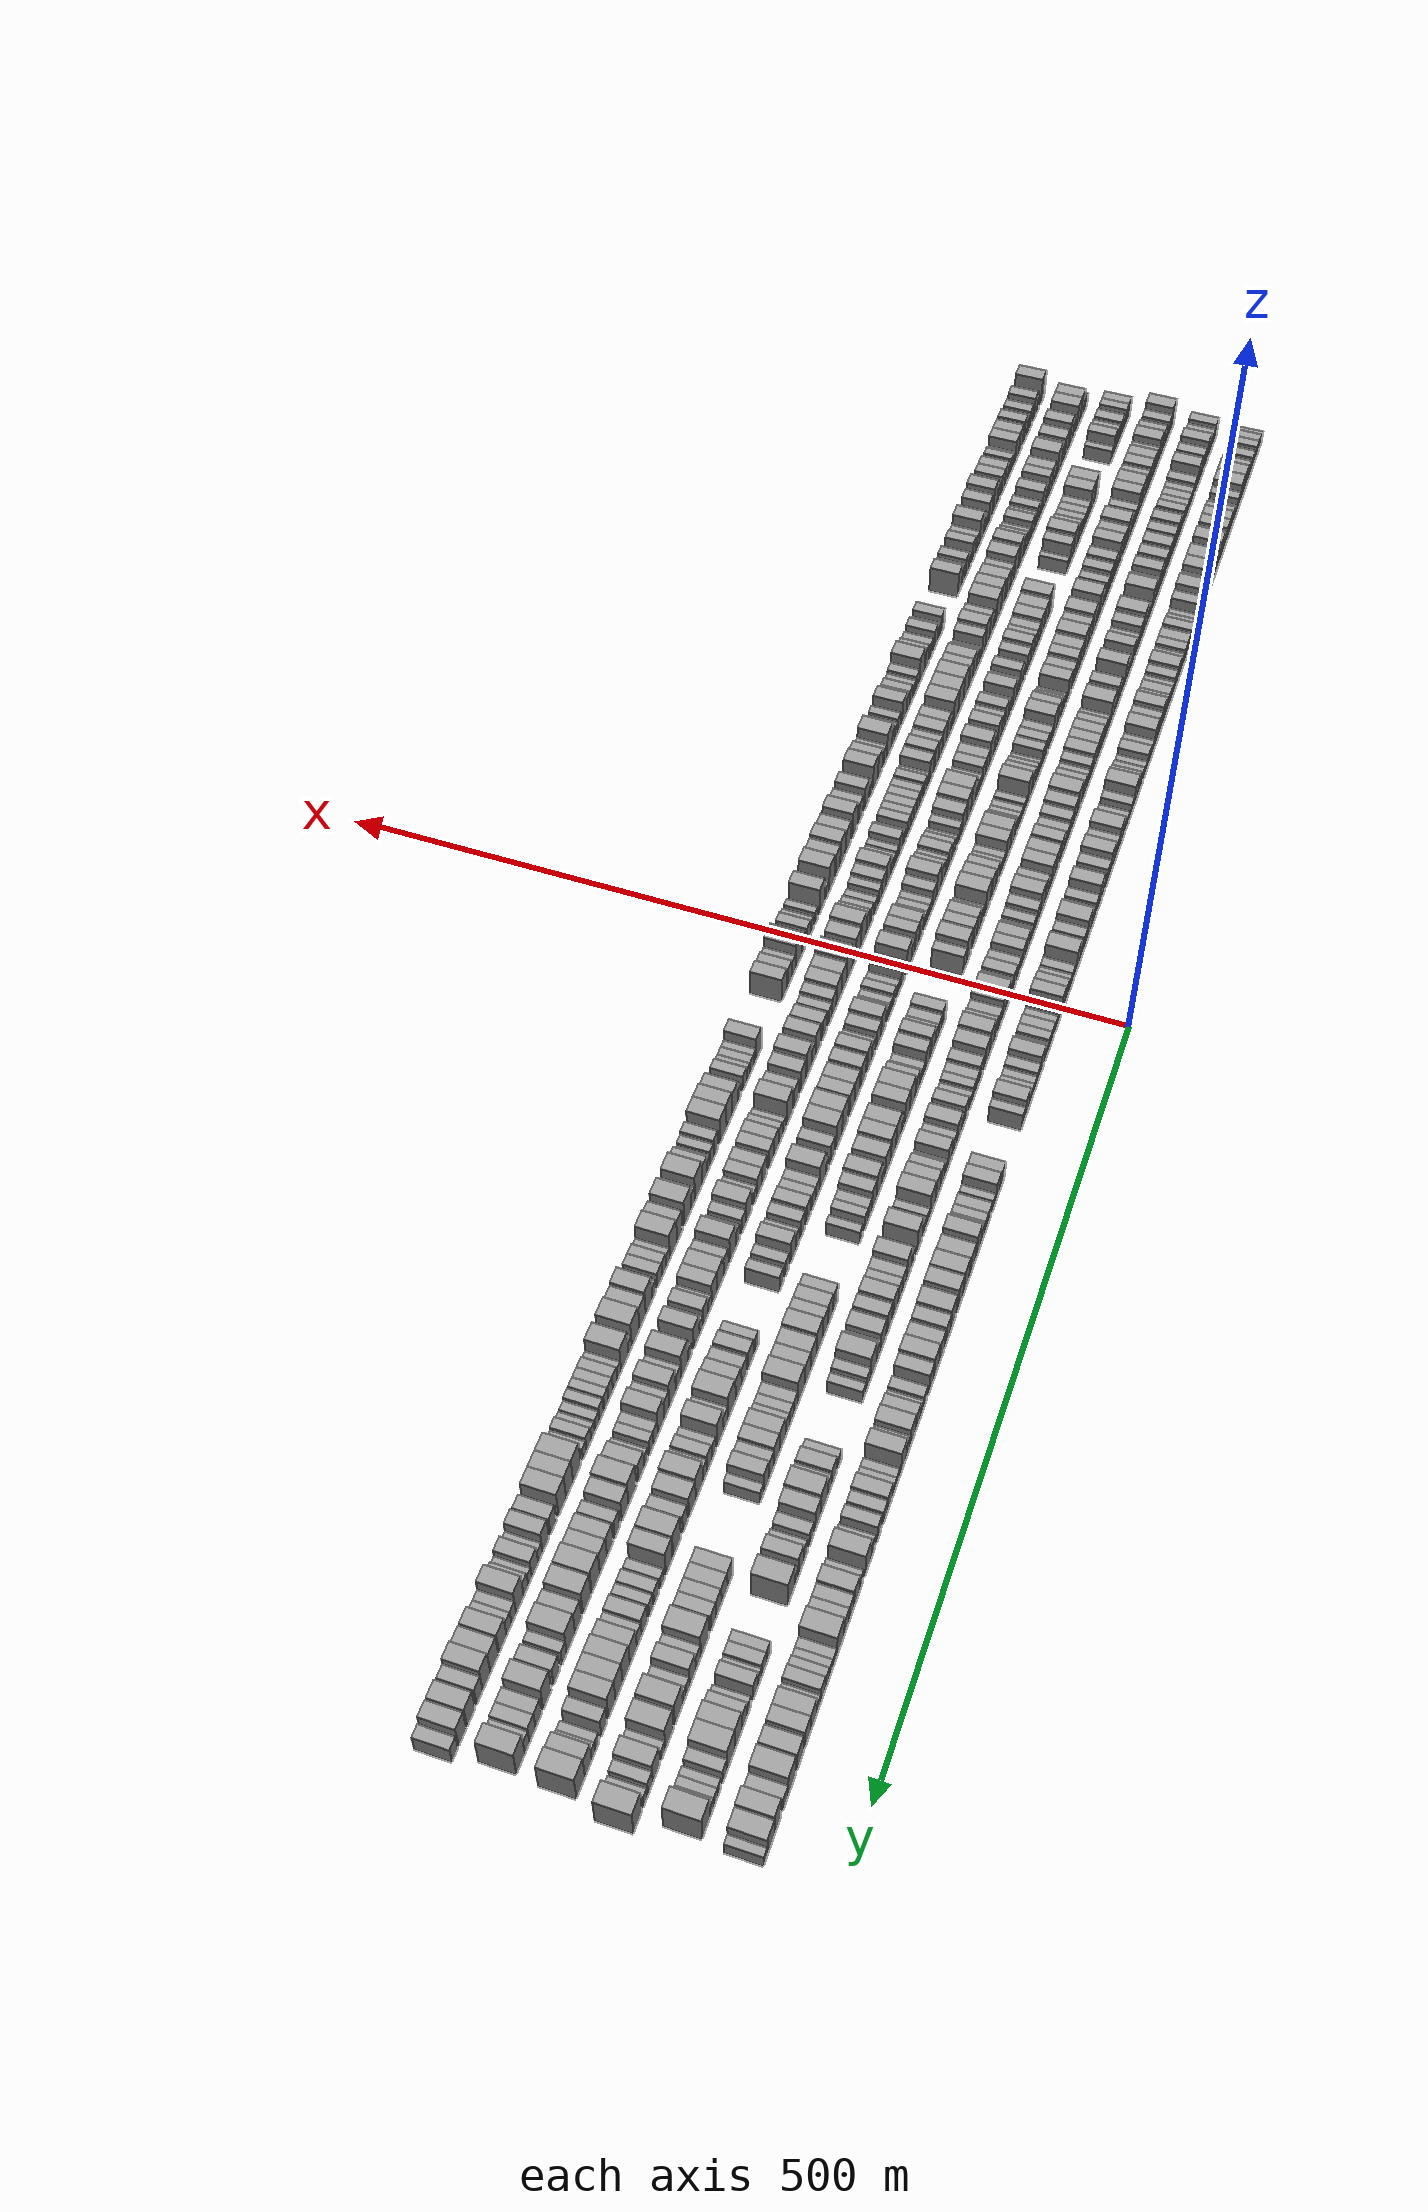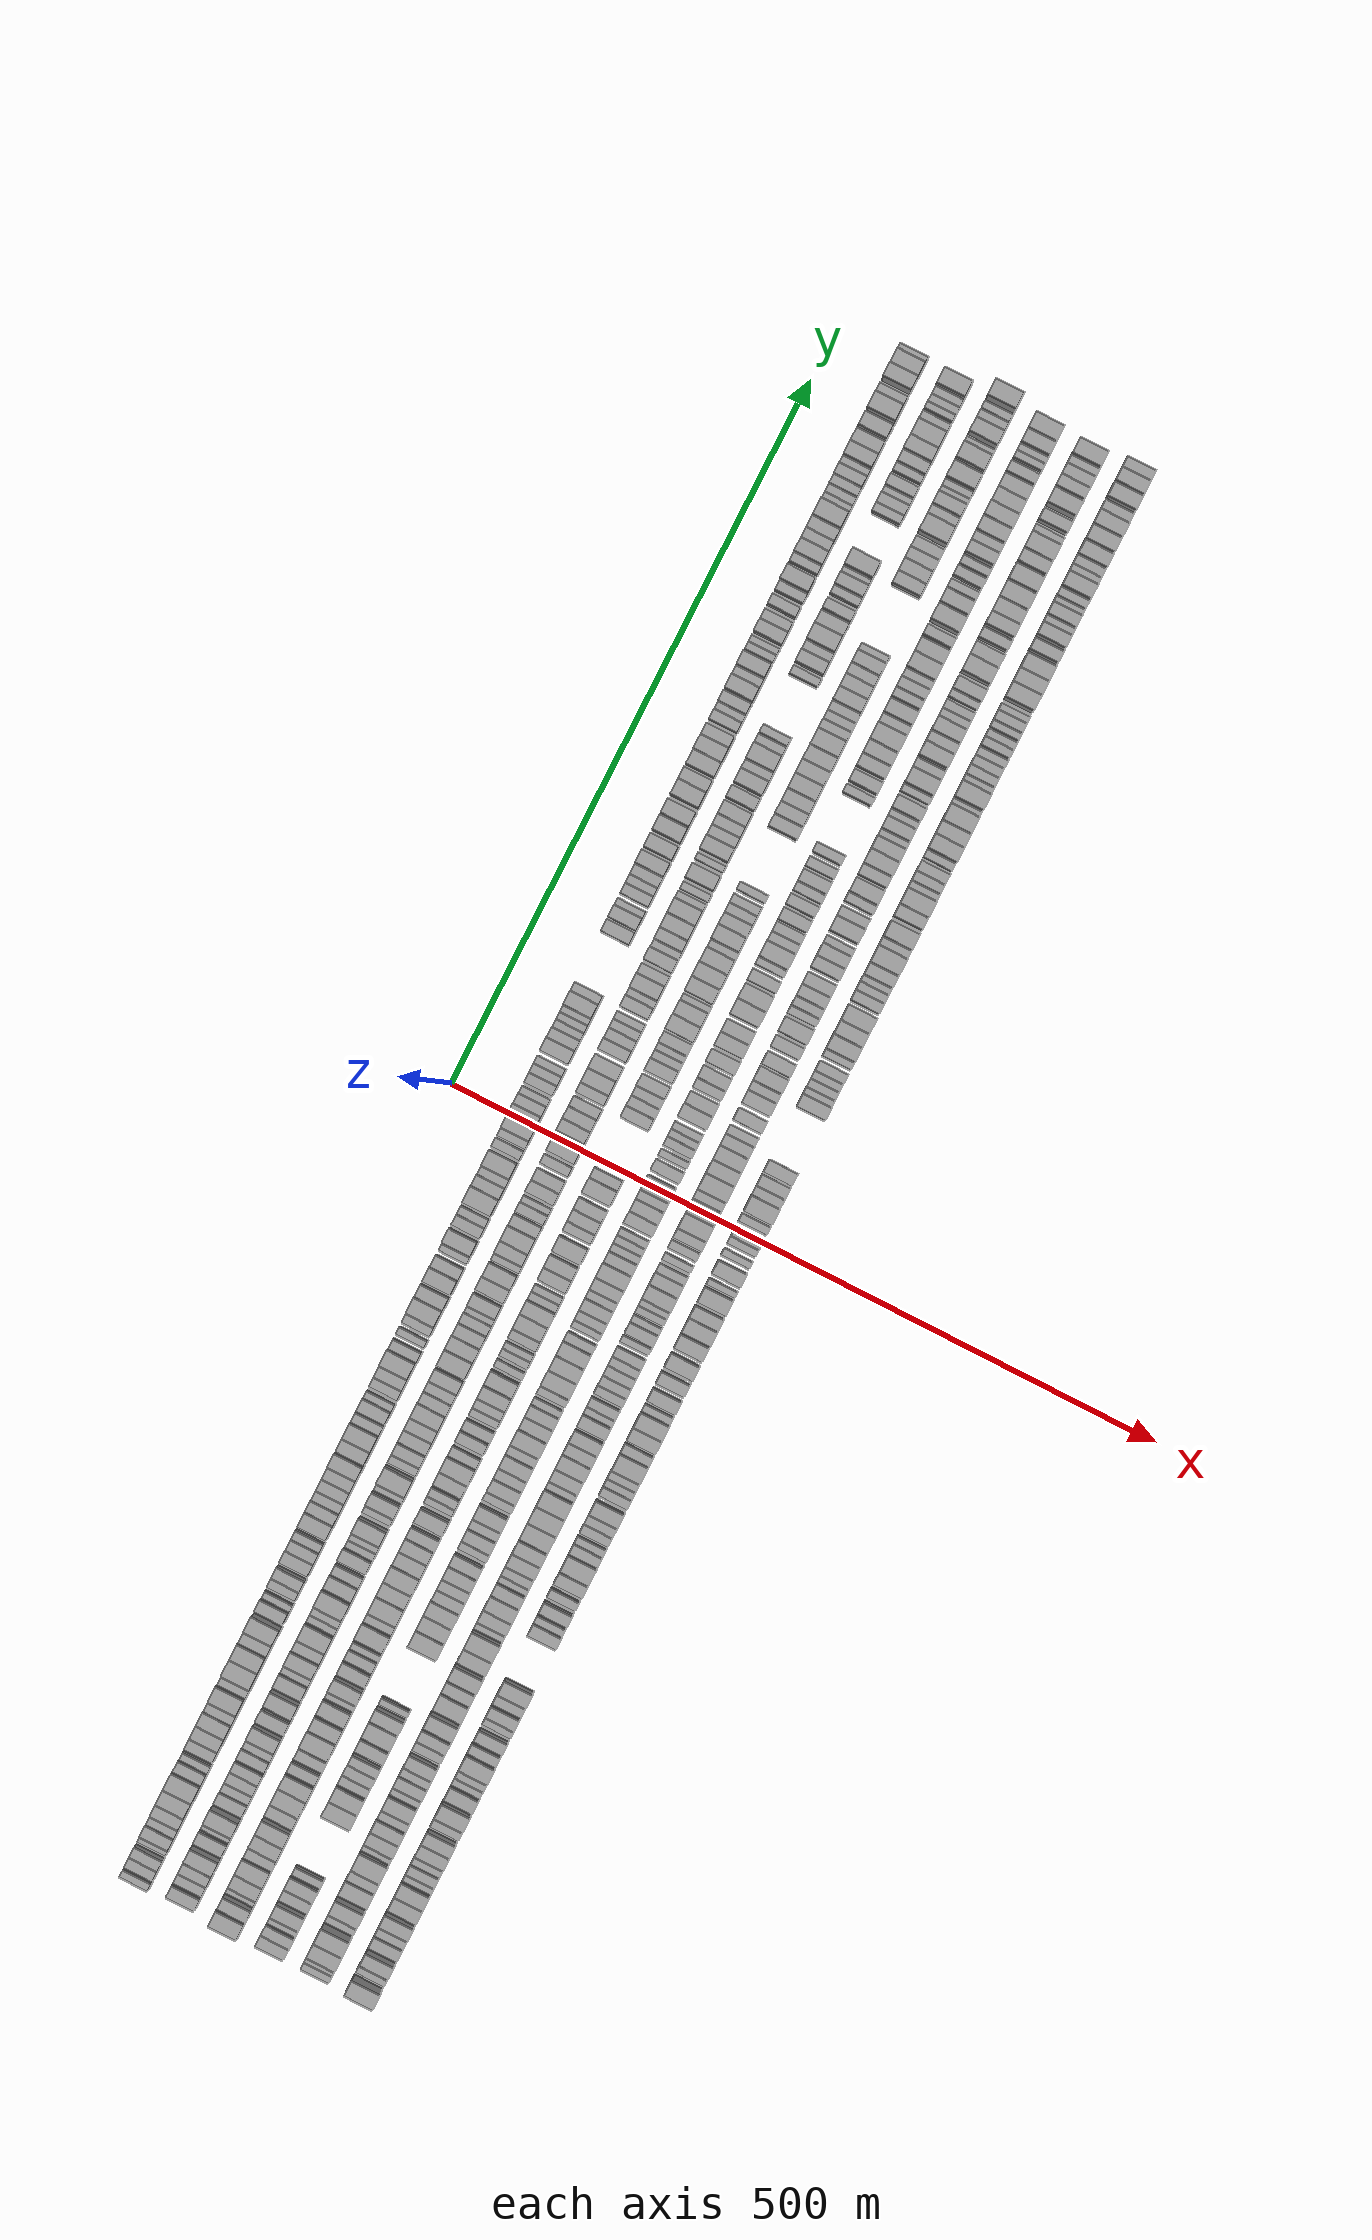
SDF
<sdf version="1.6">
 <world name="default">
  <scene>
   <sky><clouds><speed>12</speed></clouds></sky>
   <ambient>0.4 0.4 0.4 1</ambient>
   <background>0.7 0.7 0.7 1</background>
   <shadows>1</shadows>
  </scene>
  <gravity>0 0 -9.8066</gravity>
  <magnetic_field>6e-06 2.3e-05 -4.2e-05</magnetic_field>
  <physics default="0" name="default_physics" type="ode">
   <ode>
    <solver>
     <type>quick</type>
     <iters>10</iters>
     <sor>1.0</sor>
     <use_dynamic_moi_rescaling>0</use_dynamic_moi_rescaling>
    </solver>
    <constraints>
     <cfm>0</cfm>
     <erp>0.2</erp>
     <contact_max_correcting_vel>100</contact_max_correcting_vel>
     <contact_surface_layer>0.001</contact_surface_layer>
    </constraints>
   </ode>
   <max_step_size>0.004</max_step_size>
   <real_time_factor>1</real_time_factor>
   <real_time_update_rate>250</real_time_update_rate>
  </physics>
  <light name="sun" type="directional">
   <pose>0 0 10 0 0 0</pose>
   <diffuse>0.8 0.8 0.8 1</diffuse>
   <specular>0.2 0.2 0.2 1</specular>
   <attenuation>
    <range>1000</range>
    <constant>0.9</constant>
    <linear>0.01</linear>
    <quadratic>0.001</quadratic>
   </attenuation>
   <direction>-0.5 0.1 -0.9</direction>
  </light>
  <model name="building_1">
   <static>1</static>
   <pose>50.0000 -537.4246 0 0.000000 0.000000 0.000000</pose>
   <link name="link">
    <pose>0 0 6.00 0 0 0</pose>
    <collision name="collision"><geometry><box><size>20.0000 5.1508 12.0000</size></box></geometry></collision>
    <visual name="visual">
     <cast_shadows>0</cast_shadows>
     <geometry><box><size>20.0000 5.1508 12.0000</size></box></geometry>
     <material>
      <script>
       <uri>model://grey_wall/materials/scripts</uri>
       <uri>model://grey_wall/materials/textures</uri>
       <name>vrc/grey_wall</name>
      </script>
     </material>
    </visual>
   </link>
  </model>
  <model name="building_2">
   <static>1</static>
   <pose>50.0000 -529.2196 0 0.000000 0.000000 0.000000</pose>
   <link name="link">
    <pose>0 0 7.50 0 0 0</pose>
    <collision name="collision"><geometry><box><size>20.0000 7.2592 15.0000</size></box></geometry></collision>
    <visual name="visual">
     <cast_shadows>0</cast_shadows>
     <geometry><box><size>20.0000 7.2592 15.0000</size></box></geometry>
     <material>
      <script>
       <uri>model://grey_wall/materials/scripts</uri>
       <uri>model://grey_wall/materials/textures</uri>
       <name>vrc/grey_wall</name>
      </script>
     </material>
    </visual>
   </link>
  </model>
  <model name="building_3">
   <static>1</static>
   <pose>50.0000 -521.9338 0 0.000000 0.000000 0.000000</pose>
   <link name="link">
    <pose>0 0 7.50 0 0 0</pose>
    <collision name="collision"><geometry><box><size>20.0000 7.3124 15.0000</size></box></geometry></collision>
    <visual name="visual">
     <cast_shadows>0</cast_shadows>
     <geometry><box><size>20.0000 7.3124 15.0000</size></box></geometry>
     <material>
      <script>
       <uri>model://grey_wall/materials/scripts</uri>
       <uri>model://grey_wall/materials/textures</uri>
       <name>vrc/grey_wall</name>
      </script>
     </material>
    </visual>
   </link>
  </model>
  <model name="building_4">
   <static>1</static>
   <pose>50.0000 -512.8736 0 0.000000 0.000000 0.000000</pose>
   <link name="link">
    <pose>0 0 6.00 0 0 0</pose>
    <collision name="collision"><geometry><box><size>20.0000 4.8080 12.0000</size></box></geometry></collision>
    <visual name="visual">
     <cast_shadows>0</cast_shadows>
     <geometry><box><size>20.0000 4.8080 12.0000</size></box></geometry>
     <material>
      <script>
       <uri>model://grey_wall/materials/scripts</uri>
       <uri>model://grey_wall/materials/textures</uri>
       <name>vrc/grey_wall</name>
      </script>
     </material>
    </visual>
   </link>
  </model>
  <model name="building_5">
   <static>1</static>
   <pose>50.0000 -506.4843 0 0.000000 0.000000 0.000000</pose>
   <link name="link">
    <pose>0 0 9.00 0 0 0</pose>
    <collision name="collision"><geometry><box><size>20.0000 7.9707 18.0000</size></box></geometry></collision>
    <visual name="visual">
     <cast_shadows>0</cast_shadows>
     <geometry><box><size>20.0000 7.9707 18.0000</size></box></geometry>
     <material>
      <script>
       <uri>model://grey_wall/materials/scripts</uri>
       <uri>model://grey_wall/materials/textures</uri>
       <name>vrc/grey_wall</name>
      </script>
     </material>
    </visual>
   </link>
  </model>
  <model name="building_6">
   <static>1</static>
   <pose>50.0000 -499.0458 0 0.000000 0.000000 0.000000</pose>
   <link name="link">
    <pose>0 0 7.50 0 0 0</pose>
    <collision name="collision"><geometry><box><size>20.0000 6.9062 15.0000</size></box></geometry></collision>
    <visual name="visual">
     <cast_shadows>0</cast_shadows>
     <geometry><box><size>20.0000 6.9062 15.0000</size></box></geometry>
     <material>
      <script>
       <uri>model://grey_wall/materials/scripts</uri>
       <uri>model://grey_wall/materials/textures</uri>
       <name>vrc/grey_wall</name>
      </script>
     </material>
    </visual>
   </link>
  </model>
  <model name="building_7">
   <static>1</static>
   <pose>50.0000 -491.2759 0 0.000000 0.000000 0.000000</pose>
   <link name="link">
    <pose>0 0 10.50 0 0 0</pose>
    <collision name="collision"><geometry><box><size>20.0000 8.6338 21.0000</size></box></geometry></collision>
    <visual name="visual">
     <cast_shadows>0</cast_shadows>
     <geometry><box><size>20.0000 8.6338 21.0000</size></box></geometry>
     <material>
      <script>
       <uri>model://grey_wall/materials/scripts</uri>
       <uri>model://grey_wall/materials/textures</uri>
       <name>vrc/grey_wall</name>
      </script>
     </material>
    </visual>
   </link>
  </model>
  <model name="building_8">
   <static>1</static>
   <pose>50.0000 -481.7563 0 0.000000 0.000000 0.000000</pose>
   <link name="link">
    <pose>0 0 12.00 0 0 0</pose>
    <collision name="collision"><geometry><box><size>20.0000 10.4053 24.0000</size></box></geometry></collision>
    <visual name="visual">
     <cast_shadows>0</cast_shadows>
     <geometry><box><size>20.0000 10.4053 24.0000</size></box></geometry>
     <material>
      <script>
       <uri>model://grey_wall/materials/scripts</uri>
       <uri>model://grey_wall/materials/textures</uri>
       <name>vrc/grey_wall</name>
      </script>
     </material>
    </visual>
   </link>
  </model>
  <model name="building_9">
   <static>1</static>
   <pose>50.0000 -470.6066 0 0.000000 0.000000 0.000000</pose>
   <link name="link">
    <pose>0 0 12.00 0 0 0</pose>
    <collision name="collision"><geometry><box><size>20.0000 11.8942 24.0000</size></box></geometry></collision>
    <visual name="visual">
     <cast_shadows>0</cast_shadows>
     <geometry><box><size>20.0000 11.8942 24.0000</size></box></geometry>
     <material>
      <script>
       <uri>model://grey_wall/materials/scripts</uri>
       <uri>model://grey_wall/materials/textures</uri>
       <name>vrc/grey_wall</name>
      </script>
     </material>
    </visual>
   </link>
  </model>
  <model name="building_10">
   <static>1</static>
   <pose>50.0000 -460.9198 0 0.000000 0.000000 0.000000</pose>
   <link name="link">
    <pose>0 0 9.00 0 0 0</pose>
    <collision name="collision"><geometry><box><size>20.0000 7.4793 18.0000</size></box></geometry></collision>
    <visual name="visual">
     <cast_shadows>0</cast_shadows>
     <geometry><box><size>20.0000 7.4793 18.0000</size></box></geometry>
     <material>
      <script>
       <uri>model://grey_wall/materials/scripts</uri>
       <uri>model://grey_wall/materials/textures</uri>
       <name>vrc/grey_wall</name>
      </script>
     </material>
    </visual>
   </link>
  </model>
  <model name="building_11">
   <static>1</static>
   <pose>50.0000 -454.5896 0 0.000000 0.000000 0.000000</pose>
   <link name="link">
    <pose>0 0 6.00 0 0 0</pose>
    <collision name="collision"><geometry><box><size>20.0000 5.1811 12.0000</size></box></geometry></collision>
    <visual name="visual">
     <cast_shadows>0</cast_shadows>
     <geometry><box><size>20.0000 5.1811 12.0000</size></box></geometry>
     <material>
      <script>
       <uri>model://grey_wall/materials/scripts</uri>
       <uri>model://grey_wall/materials/textures</uri>
       <name>vrc/grey_wall</name>
      </script>
     </material>
    </visual>
   </link>
  </model>
  <model name="building_12">
   <static>1</static>
   <pose>50.0000 -444.8805 0 0.000000 0.000000 0.000000</pose>
   <link name="link">
    <pose>0 0 9.00 0 0 0</pose>
    <collision name="collision"><geometry><box><size>20.0000 8.2372 18.0000</size></box></geometry></collision>
    <visual name="visual">
     <cast_shadows>0</cast_shadows>
     <geometry><box><size>20.0000 8.2372 18.0000</size></box></geometry>
     <material>
      <script>
       <uri>model://grey_wall/materials/scripts</uri>
       <uri>model://grey_wall/materials/textures</uri>
       <name>vrc/grey_wall</name>
      </script>
     </material>
    </visual>
   </link>
  </model>
  <model name="building_13">
   <static>1</static>
   <pose>50.0000 -436.2609 0 0.000000 0.000000 0.000000</pose>
   <link name="link">
    <pose>0 0 10.50 0 0 0</pose>
    <collision name="collision"><geometry><box><size>20.0000 9.0019 21.0000</size></box></geometry></collision>
    <visual name="visual">
     <cast_shadows>0</cast_shadows>
     <geometry><box><size>20.0000 9.0019 21.0000</size></box></geometry>
     <material>
      <script>
       <uri>model://grey_wall/materials/scripts</uri>
       <uri>model://grey_wall/materials/textures</uri>
       <name>vrc/grey_wall</name>
      </script>
     </material>
    </visual>
   </link>
  </model>
  <model name="building_14">
   <static>1</static>
   <pose>50.0000 -426.9639 0 0.000000 0.000000 0.000000</pose>
   <link name="link">
    <pose>0 0 10.50 0 0 0</pose>
    <collision name="collision"><geometry><box><size>20.0000 9.5922 21.0000</size></box></geometry></collision>
    <visual name="visual">
     <cast_shadows>0</cast_shadows>
     <geometry><box><size>20.0000 9.5922 21.0000</size></box></geometry>
     <material>
      <script>
       <uri>model://grey_wall/materials/scripts</uri>
       <uri>model://grey_wall/materials/textures</uri>
       <name>vrc/grey_wall</name>
      </script>
     </material>
    </visual>
   </link>
  </model>
  <model name="building_15">
   <static>1</static>
   <pose>50.0000 -418.4892 0 0.000000 0.000000 0.000000</pose>
   <link name="link">
    <pose>0 0 9.00 0 0 0</pose>
    <collision name="collision"><geometry><box><size>20.0000 7.3571 18.0000</size></box></geometry></collision>
    <visual name="visual">
     <cast_shadows>0</cast_shadows>
     <geometry><box><size>20.0000 7.3571 18.0000</size></box></geometry>
     <material>
      <script>
       <uri>model://grey_wall/materials/scripts</uri>
       <uri>model://grey_wall/materials/textures</uri>
       <name>vrc/grey_wall</name>
      </script>
     </material>
    </visual>
   </link>
  </model>
  <model name="building_16">
   <static>1</static>
   <pose>50.0000 -409.1941 0 0.000000 0.000000 0.000000</pose>
   <link name="link">
    <pose>0 0 12.00 0 0 0</pose>
    <collision name="collision"><geometry><box><size>20.0000 11.2333 24.0000</size></box></geometry></collision>
    <visual name="visual">
     <cast_shadows>0</cast_shadows>
     <geometry><box><size>20.0000 11.2333 24.0000</size></box></geometry>
     <material>
      <script>
       <uri>model://grey_wall/materials/scripts</uri>
       <uri>model://grey_wall/materials/textures</uri>
       <name>vrc/grey_wall</name>
      </script>
     </material>
    </visual>
   </link>
  </model>
  <model name="building_17">
   <static>1</static>
   <pose>50.0000 -400.0829 0 0.000000 0.000000 0.000000</pose>
   <link name="link">
    <pose>0 0 7.50 0 0 0</pose>
    <collision name="collision"><geometry><box><size>20.0000 6.9891 15.0000</size></box></geometry></collision>
    <visual name="visual">
     <cast_shadows>0</cast_shadows>
     <geometry><box><size>20.0000 6.9891 15.0000</size></box></geometry>
     <material>
      <script>
       <uri>model://grey_wall/materials/scripts</uri>
       <uri>model://grey_wall/materials/textures</uri>
       <name>vrc/grey_wall</name>
      </script>
     </material>
    </visual>
   </link>
  </model>
  <model name="building_18">
   <static>1</static>
   <pose>50.0000 -390.6730 0 0.000000 0.000000 0.000000</pose>
   <link name="link">
    <pose>0 0 12.00 0 0 0</pose>
    <collision name="collision"><geometry><box><size>20.0000 11.8306 24.0000</size></box></geometry></collision>
    <visual name="visual">
     <cast_shadows>0</cast_shadows>
     <geometry><box><size>20.0000 11.8306 24.0000</size></box></geometry>
     <material>
      <script>
       <uri>model://grey_wall/materials/scripts</uri>
       <uri>model://grey_wall/materials/textures</uri>
       <name>vrc/grey_wall</name>
      </script>
     </material>
    </visual>
   </link>
  </model>
  <model name="building_19">
   <static>1</static>
   <pose>50.0000 -379.3569 0 0.000000 0.000000 0.000000</pose>
   <link name="link">
    <pose>0 0 12.00 0 0 0</pose>
    <collision name="collision"><geometry><box><size>20.0000 10.8015 24.0000</size></box></geometry></collision>
    <visual name="visual">
     <cast_shadows>0</cast_shadows>
     <geometry><box><size>20.0000 10.8015 24.0000</size></box></geometry>
     <material>
      <script>
       <uri>model://grey_wall/materials/scripts</uri>
       <uri>model://grey_wall/materials/textures</uri>
       <name>vrc/grey_wall</name>
      </script>
     </material>
    </visual>
   </link>
  </model>
  <model name="building_20">
   <static>1</static>
   <pose>50.0000 -369.6815 0 0.000000 0.000000 0.000000</pose>
   <link name="link">
    <pose>0 0 9.00 0 0 0</pose>
    <collision name="collision"><geometry><box><size>20.0000 8.5493 18.0000</size></box></geometry></collision>
    <visual name="visual">
     <cast_shadows>0</cast_shadows>
     <geometry><box><size>20.0000 8.5493 18.0000</size></box></geometry>
     <material>
      <script>
       <uri>model://grey_wall/materials/scripts</uri>
       <uri>model://grey_wall/materials/textures</uri>
       <name>vrc/grey_wall</name>
      </script>
     </material>
    </visual>
   </link>
  </model>
  <model name="building_21">
   <static>1</static>
   <pose>50.0000 -359.9097 0 0.000000 0.000000 0.000000</pose>
   <link name="link">
    <pose>0 0 12.00 0 0 0</pose>
    <collision name="collision"><geometry><box><size>20.0000 10.9943 24.0000</size></box></geometry></collision>
    <visual name="visual">
     <cast_shadows>0</cast_shadows>
     <geometry><box><size>20.0000 10.9943 24.0000</size></box></geometry>
     <material>
      <script>
       <uri>model://grey_wall/materials/scripts</uri>
       <uri>model://grey_wall/materials/textures</uri>
       <name>vrc/grey_wall</name>
      </script>
     </material>
    </visual>
   </link>
  </model>
  <model name="building_22">
   <static>1</static>
   <pose>50.0000 -347.1390 0 0.000000 0.000000 0.000000</pose>
   <link name="link">
    <pose>0 0 10.50 0 0 0</pose>
    <collision name="collision"><geometry><box><size>20.0000 8.5470 21.0000</size></box></geometry></collision>
    <visual name="visual">
     <cast_shadows>0</cast_shadows>
     <geometry><box><size>20.0000 8.5470 21.0000</size></box></geometry>
     <material>
      <script>
       <uri>model://grey_wall/materials/scripts</uri>
       <uri>model://grey_wall/materials/textures</uri>
       <name>vrc/grey_wall</name>
      </script>
     </material>
    </visual>
   </link>
  </model>
  <model name="building_23">
   <static>1</static>
   <pose>50.0000 -340.4479 0 0.000000 0.000000 0.000000</pose>
   <link name="link">
    <pose>0 0 6.00 0 0 0</pose>
    <collision name="collision"><geometry><box><size>20.0000 4.8352 12.0000</size></box></geometry></collision>
    <visual name="visual">
     <cast_shadows>0</cast_shadows>
     <geometry><box><size>20.0000 4.8352 12.0000</size></box></geometry>
     <material>
      <script>
       <uri>model://grey_wall/materials/scripts</uri>
       <uri>model://grey_wall/materials/textures</uri>
       <name>vrc/grey_wall</name>
      </script>
     </material>
    </visual>
   </link>
  </model>
  <model name="building_24">
   <static>1</static>
   <pose>50.0000 -331.6425 0 0.000000 0.000000 0.000000</pose>
   <link name="link">
    <pose>0 0 7.50 0 0 0</pose>
    <collision name="collision"><geometry><box><size>20.0000 6.7757 15.0000</size></box></geometry></collision>
    <visual name="visual">
     <cast_shadows>0</cast_shadows>
     <geometry><box><size>20.0000 6.7757 15.0000</size></box></geometry>
     <material>
      <script>
       <uri>model://grey_wall/materials/scripts</uri>
       <uri>model://grey_wall/materials/textures</uri>
       <name>vrc/grey_wall</name>
      </script>
     </material>
    </visual>
   </link>
  </model>
  <model name="building_25">
   <static>1</static>
   <pose>50.0000 -324.3452 0 0.000000 0.000000 0.000000</pose>
   <link name="link">
    <pose>0 0 9.00 0 0 0</pose>
    <collision name="collision"><geometry><box><size>20.0000 7.8188 18.0000</size></box></geometry></collision>
    <visual name="visual">
     <cast_shadows>0</cast_shadows>
     <geometry><box><size>20.0000 7.8188 18.0000</size></box></geometry>
     <material>
      <script>
       <uri>model://grey_wall/materials/scripts</uri>
       <uri>model://grey_wall/materials/textures</uri>
       <name>vrc/grey_wall</name>
      </script>
     </material>
    </visual>
   </link>
  </model>
  <model name="building_26">
   <static>1</static>
   <pose>50.0000 -313.0401 0 0.000000 0.000000 0.000000</pose>
   <link name="link">
    <pose>0 0 9.00 0 0 0</pose>
    <collision name="collision"><geometry><box><size>20.0000 8.7914 18.0000</size></box></geometry></collision>
    <visual name="visual">
     <cast_shadows>0</cast_shadows>
     <geometry><box><size>20.0000 8.7914 18.0000</size></box></geometry>
     <material>
      <script>
       <uri>model://grey_wall/materials/scripts</uri>
       <uri>model://grey_wall/materials/textures</uri>
       <name>vrc/grey_wall</name>
      </script>
     </material>
    </visual>
   </link>
  </model>
  <model name="building_27">
   <static>1</static>
   <pose>50.0000 -304.8057 0 0.000000 0.000000 0.000000</pose>
   <link name="link">
    <pose>0 0 9.00 0 0 0</pose>
    <collision name="collision"><geometry><box><size>20.0000 7.6775 18.0000</size></box></geometry></collision>
    <visual name="visual">
     <cast_shadows>0</cast_shadows>
     <geometry><box><size>20.0000 7.6775 18.0000</size></box></geometry>
     <material>
      <script>
       <uri>model://grey_wall/materials/scripts</uri>
       <uri>model://grey_wall/materials/textures</uri>
       <name>vrc/grey_wall</name>
      </script>
     </material>
    </visual>
   </link>
  </model>
  <model name="building_28">
   <static>1</static>
   <pose>50.0000 -297.8508 0 0.000000 0.000000 0.000000</pose>
   <link name="link">
    <pose>0 0 7.50 0 0 0</pose>
    <collision name="collision"><geometry><box><size>20.0000 6.2323 15.0000</size></box></geometry></collision>
    <visual name="visual">
     <cast_shadows>0</cast_shadows>
     <geometry><box><size>20.0000 6.2323 15.0000</size></box></geometry>
     <material>
      <script>
       <uri>model://grey_wall/materials/scripts</uri>
       <uri>model://grey_wall/materials/textures</uri>
       <name>vrc/grey_wall</name>
      </script>
     </material>
    </visual>
   </link>
  </model>
  <model name="building_29">
   <static>1</static>
   <pose>50.0000 -286.5448 0 0.000000 0.000000 0.000000</pose>
   <link name="link">
    <pose>0 0 10.50 0 0 0</pose>
    <collision name="collision"><geometry><box><size>20.0000 10.3797 21.0000</size></box></geometry></collision>
    <visual name="visual">
     <cast_shadows>0</cast_shadows>
     <geometry><box><size>20.0000 10.3797 21.0000</size></box></geometry>
     <material>
      <script>
       <uri>model://grey_wall/materials/scripts</uri>
       <uri>model://grey_wall/materials/textures</uri>
       <name>vrc/grey_wall</name>
      </script>
     </material>
    </visual>
   </link>
  </model>
  <model name="building_30">
   <static>1</static>
   <pose>50.0000 -277.3903 0 0.000000 0.000000 0.000000</pose>
   <link name="link">
    <pose>0 0 9.00 0 0 0</pose>
    <collision name="collision"><geometry><box><size>20.0000 7.9294 18.0000</size></box></geometry></collision>
    <visual name="visual">
     <cast_shadows>0</cast_shadows>
     <geometry><box><size>20.0000 7.9294 18.0000</size></box></geometry>
     <material>
      <script>
       <uri>model://grey_wall/materials/scripts</uri>
       <uri>model://grey_wall/materials/textures</uri>
       <name>vrc/grey_wall</name>
      </script>
     </material>
    </visual>
   </link>
  </model>
  <model name="building_31">
   <static>1</static>
   <pose>50.0000 -269.8469 0 0.000000 0.000000 0.000000</pose>
   <link name="link">
    <pose>0 0 7.50 0 0 0</pose>
    <collision name="collision"><geometry><box><size>20.0000 7.1575 15.0000</size></box></geometry></collision>
    <visual name="visual">
     <cast_shadows>0</cast_shadows>
     <geometry><box><size>20.0000 7.1575 15.0000</size></box></geometry>
     <material>
      <script>
       <uri>model://grey_wall/materials/scripts</uri>
       <uri>model://grey_wall/materials/textures</uri>
       <name>vrc/grey_wall</name>
      </script>
     </material>
    </visual>
   </link>
  </model>
  <model name="building_32">
   <static>1</static>
   <pose>50.0000 -262.2515 0 0.000000 0.000000 0.000000</pose>
   <link name="link">
    <pose>0 0 9.00 0 0 0</pose>
    <collision name="collision"><geometry><box><size>20.0000 8.0332 18.0000</size></box></geometry></collision>
    <visual name="visual">
     <cast_shadows>0</cast_shadows>
     <geometry><box><size>20.0000 8.0332 18.0000</size></box></geometry>
     <material>
      <script>
       <uri>model://grey_wall/materials/scripts</uri>
       <uri>model://grey_wall/materials/textures</uri>
       <name>vrc/grey_wall</name>
      </script>
     </material>
    </visual>
   </link>
  </model>
  <model name="building_33">
   <static>1</static>
   <pose>50.0000 -253.8243 0 0.000000 0.000000 0.000000</pose>
   <link name="link">
    <pose>0 0 9.00 0 0 0</pose>
    <collision name="collision"><geometry><box><size>20.0000 8.8211 18.0000</size></box></geometry></collision>
    <visual name="visual">
     <cast_shadows>0</cast_shadows>
     <geometry><box><size>20.0000 8.8211 18.0000</size></box></geometry>
     <material>
      <script>
       <uri>model://grey_wall/materials/scripts</uri>
       <uri>model://grey_wall/materials/textures</uri>
       <name>vrc/grey_wall</name>
      </script>
     </material>
    </visual>
   </link>
  </model>
  <model name="building_34">
   <static>1</static>
   <pose>50.0000 -244.5286 0 0.000000 0.000000 0.000000</pose>
   <link name="link">
    <pose>0 0 12.00 0 0 0</pose>
    <collision name="collision"><geometry><box><size>20.0000 9.7702 24.0000</size></box></geometry></collision>
    <visual name="visual">
     <cast_shadows>0</cast_shadows>
     <geometry><box><size>20.0000 9.7702 24.0000</size></box></geometry>
     <material>
      <script>
       <uri>model://grey_wall/materials/scripts</uri>
       <uri>model://grey_wall/materials/textures</uri>
       <name>vrc/grey_wall</name>
      </script>
     </material>
    </visual>
   </link>
  </model>
  <model name="building_35">
   <static>1</static>
   <pose>50.0000 -233.9191 0 0.000000 0.000000 0.000000</pose>
   <link name="link">
    <pose>0 0 10.50 0 0 0</pose>
    <collision name="collision"><geometry><box><size>20.0000 9.4488 21.0000</size></box></geometry></collision>
    <visual name="visual">
     <cast_shadows>0</cast_shadows>
     <geometry><box><size>20.0000 9.4488 21.0000</size></box></geometry>
     <material>
      <script>
       <uri>model://grey_wall/materials/scripts</uri>
       <uri>model://grey_wall/materials/textures</uri>
       <name>vrc/grey_wall</name>
      </script>
     </material>
    </visual>
   </link>
  </model>
  <model name="building_36">
   <static>1</static>
   <pose>50.0000 -223.7464 0 0.000000 0.000000 0.000000</pose>
   <link name="link">
    <pose>0 0 12.00 0 0 0</pose>
    <collision name="collision"><geometry><box><size>20.0000 10.8966 24.0000</size></box></geometry></collision>
    <visual name="visual">
     <cast_shadows>0</cast_shadows>
     <geometry><box><size>20.0000 10.8966 24.0000</size></box></geometry>
     <material>
      <script>
       <uri>model://grey_wall/materials/scripts</uri>
       <uri>model://grey_wall/materials/textures</uri>
       <name>vrc/grey_wall</name>
      </script>
     </material>
    </visual>
   </link>
  </model>
  <model name="building_37">
   <static>1</static>
   <pose>50.0000 -214.8736 0 0.000000 0.000000 0.000000</pose>
   <link name="link">
    <pose>0 0 7.50 0 0 0</pose>
    <collision name="collision"><geometry><box><size>20.0000 6.8491 15.0000</size></box></geometry></collision>
    <visual name="visual">
     <cast_shadows>0</cast_shadows>
     <geometry><box><size>20.0000 6.8491 15.0000</size></box></geometry>
     <material>
      <script>
       <uri>model://grey_wall/materials/scripts</uri>
       <uri>model://grey_wall/materials/textures</uri>
       <name>vrc/grey_wall</name>
      </script>
     </material>
    </visual>
   </link>
  </model>
  <model name="building_38">
   <static>1</static>
   <pose>50.0000 -205.9737 0 0.000000 0.000000 0.000000</pose>
   <link name="link">
    <pose>0 0 9.00 0 0 0</pose>
    <collision name="collision"><geometry><box><size>20.0000 8.9506 18.0000</size></box></geometry></collision>
    <visual name="visual">
     <cast_shadows>0</cast_shadows>
     <geometry><box><size>20.0000 8.9506 18.0000</size></box></geometry>
     <material>
      <script>
       <uri>model://grey_wall/materials/scripts</uri>
       <uri>model://grey_wall/materials/textures</uri>
       <name>vrc/grey_wall</name>
      </script>
     </material>
    </visual>
   </link>
  </model>
  <model name="building_39">
   <static>1</static>
   <pose>50.0000 -198.9181 0 0.000000 0.000000 0.000000</pose>
   <link name="link">
    <pose>0 0 6.00 0 0 0</pose>
    <collision name="collision"><geometry><box><size>20.0000 5.1606 12.0000</size></box></geometry></collision>
    <visual name="visual">
     <cast_shadows>0</cast_shadows>
     <geometry><box><size>20.0000 5.1606 12.0000</size></box></geometry>
     <material>
      <script>
       <uri>model://grey_wall/materials/scripts</uri>
       <uri>model://grey_wall/materials/textures</uri>
       <name>vrc/grey_wall</name>
      </script>
     </material>
    </visual>
   </link>
  </model>
  <model name="building_40">
   <static>1</static>
   <pose>50.0000 -189.7828 0 0.000000 0.000000 0.000000</pose>
   <link name="link">
    <pose>0 0 7.50 0 0 0</pose>
    <collision name="collision"><geometry><box><size>20.0000 7.1099 15.0000</size></box></geometry></collision>
    <visual name="visual">
     <cast_shadows>0</cast_shadows>
     <geometry><box><size>20.0000 7.1099 15.0000</size></box></geometry>
     <material>
      <script>
       <uri>model://grey_wall/materials/scripts</uri>
       <uri>model://grey_wall/materials/textures</uri>
       <name>vrc/grey_wall</name>
      </script>
     </material>
    </visual>
   </link>
  </model>
  <model name="building_41">
   <static>1</static>
   <pose>50.0000 -182.0409 0 0.000000 0.000000 0.000000</pose>
   <link name="link">
    <pose>0 0 9.00 0 0 0</pose>
    <collision name="collision"><geometry><box><size>20.0000 8.3740 18.0000</size></box></geometry></collision>
    <visual name="visual">
     <cast_shadows>0</cast_shadows>
     <geometry><box><size>20.0000 8.3740 18.0000</size></box></geometry>
     <material>
      <script>
       <uri>model://grey_wall/materials/scripts</uri>
       <uri>model://grey_wall/materials/textures</uri>
       <name>vrc/grey_wall</name>
      </script>
     </material>
    </visual>
   </link>
  </model>
  <model name="building_42">
   <static>1</static>
   <pose>50.0000 -172.1996 0 0.000000 0.000000 0.000000</pose>
   <link name="link">
    <pose>0 0 12.00 0 0 0</pose>
    <collision name="collision"><geometry><box><size>20.0000 11.3087 24.0000</size></box></geometry></collision>
    <visual name="visual">
     <cast_shadows>0</cast_shadows>
     <geometry><box><size>20.0000 11.3087 24.0000</size></box></geometry>
     <material>
      <script>
       <uri>model://grey_wall/materials/scripts</uri>
       <uri>model://grey_wall/materials/textures</uri>
       <name>vrc/grey_wall</name>
      </script>
     </material>
    </visual>
   </link>
  </model>
  <model name="building_43">
   <static>1</static>
   <pose>50.0000 -162.9634 0 0.000000 0.000000 0.000000</pose>
   <link name="link">
    <pose>0 0 7.50 0 0 0</pose>
    <collision name="collision"><geometry><box><size>20.0000 7.1636 15.0000</size></box></geometry></collision>
    <visual name="visual">
     <cast_shadows>0</cast_shadows>
     <geometry><box><size>20.0000 7.1636 15.0000</size></box></geometry>
     <material>
      <script>
       <uri>model://grey_wall/materials/scripts</uri>
       <uri>model://grey_wall/materials/textures</uri>
       <name>vrc/grey_wall</name>
      </script>
     </material>
    </visual>
   </link>
  </model>
  <model name="building_44">
   <static>1</static>
   <pose>50.0000 -153.7354 0 0.000000 0.000000 0.000000</pose>
   <link name="link">
    <pose>0 0 6.00 0 0 0</pose>
    <collision name="collision"><geometry><box><size>20.0000 5.2925 12.0000</size></box></geometry></collision>
    <visual name="visual">
     <cast_shadows>0</cast_shadows>
     <geometry><box><size>20.0000 5.2925 12.0000</size></box></geometry>
     <material>
      <script>
       <uri>model://grey_wall/materials/scripts</uri>
       <uri>model://grey_wall/materials/textures</uri>
       <name>vrc/grey_wall</name>
      </script>
     </material>
    </visual>
   </link>
  </model>
  <model name="building_45">
   <static>1</static>
   <pose>50.0000 -144.5357 0 0.000000 0.000000 0.000000</pose>
   <link name="link">
    <pose>0 0 7.50 0 0 0</pose>
    <collision name="collision"><geometry><box><size>20.0000 7.1068 15.0000</size></box></geometry></collision>
    <visual name="visual">
     <cast_shadows>0</cast_shadows>
     <geometry><box><size>20.0000 7.1068 15.0000</size></box></geometry>
     <material>
      <script>
       <uri>model://grey_wall/materials/scripts</uri>
       <uri>model://grey_wall/materials/textures</uri>
       <name>vrc/grey_wall</name>
      </script>
     </material>
    </visual>
   </link>
  </model>
  <model name="building_46">
   <static>1</static>
   <pose>50.0000 -135.3073 0 0.000000 0.000000 0.000000</pose>
   <link name="link">
    <pose>0 0 12.00 0 0 0</pose>
    <collision name="collision"><geometry><box><size>20.0000 11.3501 24.0000</size></box></geometry></collision>
    <visual name="visual">
     <cast_shadows>0</cast_shadows>
     <geometry><box><size>20.0000 11.3501 24.0000</size></box></geometry>
     <material>
      <script>
       <uri>model://grey_wall/materials/scripts</uri>
       <uri>model://grey_wall/materials/textures</uri>
       <name>vrc/grey_wall</name>
      </script>
     </material>
    </visual>
   </link>
  </model>
  <model name="building_47">
   <static>1</static>
   <pose>50.0000 -125.1540 0 0.000000 0.000000 0.000000</pose>
   <link name="link">
    <pose>0 0 9.00 0 0 0</pose>
    <collision name="collision"><geometry><box><size>20.0000 8.9565 18.0000</size></box></geometry></collision>
    <visual name="visual">
     <cast_shadows>0</cast_shadows>
     <geometry><box><size>20.0000 8.9565 18.0000</size></box></geometry>
     <material>
      <script>
       <uri>model://grey_wall/materials/scripts</uri>
       <uri>model://grey_wall/materials/textures</uri>
       <name>vrc/grey_wall</name>
      </script>
     </material>
    </visual>
   </link>
  </model>
  <model name="building_48">
   <static>1</static>
   <pose>50.0000 -113.5470 0 0.000000 0.000000 0.000000</pose>
   <link name="link">
    <pose>0 0 12.00 0 0 0</pose>
    <collision name="collision"><geometry><box><size>20.0000 10.2575 24.0000</size></box></geometry></collision>
    <visual name="visual">
     <cast_shadows>0</cast_shadows>
     <geometry><box><size>20.0000 10.2575 24.0000</size></box></geometry>
     <material>
      <script>
       <uri>model://grey_wall/materials/scripts</uri>
       <uri>model://grey_wall/materials/textures</uri>
       <name>vrc/grey_wall</name>
      </script>
     </material>
    </visual>
   </link>
  </model>
  <model name="building_49">
   <static>1</static>
   <pose>50.0000 -104.2475 0 0.000000 0.000000 0.000000</pose>
   <link name="link">
    <pose>0 0 9.00 0 0 0</pose>
    <collision name="collision"><geometry><box><size>20.0000 8.3414 18.0000</size></box></geometry></collision>
    <visual name="visual">
     <cast_shadows>0</cast_shadows>
     <geometry><box><size>20.0000 8.3414 18.0000</size></box></geometry>
     <material>
      <script>
       <uri>model://grey_wall/materials/scripts</uri>
       <uri>model://grey_wall/materials/textures</uri>
       <name>vrc/grey_wall</name>
      </script>
     </material>
    </visual>
   </link>
  </model>
  <model name="building_50">
   <static>1</static>
   <pose>50.0000 -94.6067 0 0.000000 0.000000 0.000000</pose>
   <link name="link">
    <pose>0 0 6.00 0 0 0</pose>
    <collision name="collision"><geometry><box><size>20.0000 4.9403 12.0000</size></box></geometry></collision>
    <visual name="visual">
     <cast_shadows>0</cast_shadows>
     <geometry><box><size>20.0000 4.9403 12.0000</size></box></geometry>
     <material>
      <script>
       <uri>model://grey_wall/materials/scripts</uri>
       <uri>model://grey_wall/materials/textures</uri>
       <name>vrc/grey_wall</name>
      </script>
     </material>
    </visual>
   </link>
  </model>
  <model name="building_51">
   <static>1</static>
   <pose>50.0000 -86.0847 0 0.000000 0.000000 0.000000</pose>
   <link name="link">
    <pose>0 0 12.00 0 0 0</pose>
    <collision name="collision"><geometry><box><size>20.0000 10.1037 24.0000</size></box></geometry></collision>
    <visual name="visual">
     <cast_shadows>0</cast_shadows>
     <geometry><box><size>20.0000 10.1037 24.0000</size></box></geometry>
     <material>
      <script>
       <uri>model://grey_wall/materials/scripts</uri>
       <uri>model://grey_wall/materials/textures</uri>
       <name>vrc/grey_wall</name>
      </script>
     </material>
    </visual>
   </link>
  </model>
  <model name="building_52">
   <static>1</static>
   <pose>50.0000 -75.1629 0 0.000000 0.000000 0.000000</pose>
   <link name="link">
    <pose>0 0 9.00 0 0 0</pose>
    <collision name="collision"><geometry><box><size>20.0000 7.7400 18.0000</size></box></geometry></collision>
    <visual name="visual">
     <cast_shadows>0</cast_shadows>
     <geometry><box><size>20.0000 7.7400 18.0000</size></box></geometry>
     <material>
      <script>
       <uri>model://grey_wall/materials/scripts</uri>
       <uri>model://grey_wall/materials/textures</uri>
       <name>vrc/grey_wall</name>
      </script>
     </material>
    </visual>
   </link>
  </model>
  <model name="building_53">
   <static>1</static>
   <pose>50.0000 -68.2267 0 0.000000 0.000000 0.000000</pose>
   <link name="link">
    <pose>0 0 7.50 0 0 0</pose>
    <collision name="collision"><geometry><box><size>20.0000 6.1323 15.0000</size></box></geometry></collision>
    <visual name="visual">
     <cast_shadows>0</cast_shadows>
     <geometry><box><size>20.0000 6.1323 15.0000</size></box></geometry>
     <material>
      <script>
       <uri>model://grey_wall/materials/scripts</uri>
       <uri>model://grey_wall/materials/textures</uri>
       <name>vrc/grey_wall</name>
      </script>
     </material>
    </visual>
   </link>
  </model>
  <model name="building_54">
   <static>1</static>
   <pose>50.0000 -57.1812 0 0.000000 0.000000 0.000000</pose>
   <link name="link">
    <pose>0 0 12.00 0 0 0</pose>
    <collision name="collision"><geometry><box><size>20.0000 11.9588 24.0000</size></box></geometry></collision>
    <visual name="visual">
     <cast_shadows>0</cast_shadows>
     <geometry><box><size>20.0000 11.9588 24.0000</size></box></geometry>
     <material>
      <script>
       <uri>model://grey_wall/materials/scripts</uri>
       <uri>model://grey_wall/materials/textures</uri>
       <name>vrc/grey_wall</name>
      </script>
     </material>
    </visual>
   </link>
  </model>
  <model name="building_55">
   <static>1</static>
   <pose>50.0000 -47.1897 0 0.000000 0.000000 0.000000</pose>
   <link name="link">
    <pose>0 0 9.00 0 0 0</pose>
    <collision name="collision"><geometry><box><size>20.0000 8.0243 18.0000</size></box></geometry></collision>
    <visual name="visual">
     <cast_shadows>0</cast_shadows>
     <geometry><box><size>20.0000 8.0243 18.0000</size></box></geometry>
     <material>
      <script>
       <uri>model://grey_wall/materials/scripts</uri>
       <uri>model://grey_wall/materials/textures</uri>
       <name>vrc/grey_wall</name>
      </script>
     </material>
    </visual>
   </link>
  </model>
  <model name="building_56">
   <static>1</static>
   <pose>50.0000 -39.9663 0 0.000000 0.000000 0.000000</pose>
   <link name="link">
    <pose>0 0 7.50 0 0 0</pose>
    <collision name="collision"><geometry><box><size>20.0000 6.4225 15.0000</size></box></geometry></collision>
    <visual name="visual">
     <cast_shadows>0</cast_shadows>
     <geometry><box><size>20.0000 6.4225 15.0000</size></box></geometry>
     <material>
      <script>
       <uri>model://grey_wall/materials/scripts</uri>
       <uri>model://grey_wall/materials/textures</uri>
       <name>vrc/grey_wall</name>
      </script>
     </material>
    </visual>
   </link>
  </model>
  <model name="building_57">
   <static>1</static>
   <pose>50.0000 -31.2169 0 0.000000 0.000000 0.000000</pose>
   <link name="link">
    <pose>0 0 12.00 0 0 0</pose>
    <collision name="collision"><geometry><box><size>20.0000 11.0762 24.0000</size></box></geometry></collision>
    <visual name="visual">
     <cast_shadows>0</cast_shadows>
     <geometry><box><size>20.0000 11.0762 24.0000</size></box></geometry>
     <material>
      <script>
       <uri>model://grey_wall/materials/scripts</uri>
       <uri>model://grey_wall/materials/textures</uri>
       <name>vrc/grey_wall</name>
      </script>
     </material>
    </visual>
   </link>
  </model>
  <model name="building_58">
   <static>1</static>
   <pose>50.0000 -20.3244 0 0.000000 0.000000 0.000000</pose>
   <link name="link">
    <pose>0 0 7.50 0 0 0</pose>
    <collision name="collision"><geometry><box><size>20.0000 6.7090 15.0000</size></box></geometry></collision>
    <visual name="visual">
     <cast_shadows>0</cast_shadows>
     <geometry><box><size>20.0000 6.7090 15.0000</size></box></geometry>
     <material>
      <script>
       <uri>model://grey_wall/materials/scripts</uri>
       <uri>model://grey_wall/materials/textures</uri>
       <name>vrc/grey_wall</name>
      </script>
     </material>
    </visual>
   </link>
  </model>
  <model name="building_59">
   <static>1</static>
   <pose>50.0000 -12.9591 0 0.000000 0.000000 0.000000</pose>
   <link name="link">
    <pose>0 0 7.50 0 0 0</pose>
    <collision name="collision"><geometry><box><size>20.0000 6.0215 15.0000</size></box></geometry></collision>
    <visual name="visual">
     <cast_shadows>0</cast_shadows>
     <geometry><box><size>20.0000 6.0215 15.0000</size></box></geometry>
     <material>
      <script>
       <uri>model://grey_wall/materials/scripts</uri>
       <uri>model://grey_wall/materials/textures</uri>
       <name>vrc/grey_wall</name>
      </script>
     </material>
    </visual>
   </link>
  </model>
  <model name="building_60">
   <static>1</static>
   <pose>50.0000 -5.7526 0 0.000000 0.000000 0.000000</pose>
   <link name="link">
    <pose>0 0 9.00 0 0 0</pose>
    <collision name="collision"><geometry><box><size>20.0000 8.3915 18.0000</size></box></geometry></collision>
    <visual name="visual">
     <cast_shadows>0</cast_shadows>
     <geometry><box><size>20.0000 8.3915 18.0000</size></box></geometry>
     <material>
      <script>
       <uri>model://grey_wall/materials/scripts</uri>
       <uri>model://grey_wall/materials/textures</uri>
       <name>vrc/grey_wall</name>
      </script>
     </material>
    </visual>
   </link>
  </model>
  <model name="building_61">
   <static>1</static>
   <pose>50.0000 2.7768 0 0.000000 0.000000 0.000000</pose>
   <link name="link">
    <pose>0 0 10.50 0 0 0</pose>
    <collision name="collision"><geometry><box><size>20.0000 8.6674 21.0000</size></box></geometry></collision>
    <visual name="visual">
     <cast_shadows>0</cast_shadows>
     <geometry><box><size>20.0000 8.6674 21.0000</size></box></geometry>
     <material>
      <script>
       <uri>model://grey_wall/materials/scripts</uri>
       <uri>model://grey_wall/materials/textures</uri>
       <name>vrc/grey_wall</name>
      </script>
     </material>
    </visual>
   </link>
  </model>
  <model name="building_62">
   <static>1</static>
   <pose>50.0000 10.7476 0 0.000000 0.000000 0.000000</pose>
   <link name="link">
    <pose>0 0 7.50 0 0 0</pose>
    <collision name="collision"><geometry><box><size>20.0000 7.2742 15.0000</size></box></geometry></collision>
    <visual name="visual">
     <cast_shadows>0</cast_shadows>
     <geometry><box><size>20.0000 7.2742 15.0000</size></box></geometry>
     <material>
      <script>
       <uri>model://grey_wall/materials/scripts</uri>
       <uri>model://grey_wall/materials/textures</uri>
       <name>vrc/grey_wall</name>
      </script>
     </material>
    </visual>
   </link>
  </model>
  <model name="building_63">
   <static>1</static>
   <pose>50.0000 17.0722 0 0.000000 0.000000 0.000000</pose>
   <link name="link">
    <pose>0 0 6.00 0 0 0</pose>
    <collision name="collision"><geometry><box><size>20.0000 5.3750 12.0000</size></box></geometry></collision>
    <visual name="visual">
     <cast_shadows>0</cast_shadows>
     <geometry><box><size>20.0000 5.3750 12.0000</size></box></geometry>
     <material>
      <script>
       <uri>model://grey_wall/materials/scripts</uri>
       <uri>model://grey_wall/materials/textures</uri>
       <name>vrc/grey_wall</name>
      </script>
     </material>
    </visual>
   </link>
  </model>
  <model name="building_64">
   <static>1</static>
   <pose>50.0000 25.3517 0 0.000000 0.000000 0.000000</pose>
   <link name="link">
    <pose>0 0 7.50 0 0 0</pose>
    <collision name="collision"><geometry><box><size>20.0000 7.1840 15.0000</size></box></geometry></collision>
    <visual name="visual">
     <cast_shadows>0</cast_shadows>
     <geometry><box><size>20.0000 7.1840 15.0000</size></box></geometry>
     <material>
      <script>
       <uri>model://grey_wall/materials/scripts</uri>
       <uri>model://grey_wall/materials/textures</uri>
       <name>vrc/grey_wall</name>
      </script>
     </material>
    </visual>
   </link>
  </model>
  <model name="building_65">
   <static>1</static>
   <pose>50.0000 32.2390 0 0.000000 0.000000 0.000000</pose>
   <link name="link">
    <pose>0 0 7.50 0 0 0</pose>
    <collision name="collision"><geometry><box><size>20.0000 6.5907 15.0000</size></box></geometry></collision>
    <visual name="visual">
     <cast_shadows>0</cast_shadows>
     <geometry><box><size>20.0000 6.5907 15.0000</size></box></geometry>
     <material>
      <script>
       <uri>model://grey_wall/materials/scripts</uri>
       <uri>model://grey_wall/materials/textures</uri>
       <name>vrc/grey_wall</name>
      </script>
     </material>
    </visual>
   </link>
  </model>
  <model name="building_66">
   <static>1</static>
   <pose>50.0000 38.3347 0 0.000000 0.000000 0.000000</pose>
   <link name="link">
    <pose>0 0 6.00 0 0 0</pose>
    <collision name="collision"><geometry><box><size>20.0000 5.6006 12.0000</size></box></geometry></collision>
    <visual name="visual">
     <cast_shadows>0</cast_shadows>
     <geometry><box><size>20.0000 5.6006 12.0000</size></box></geometry>
     <material>
      <script>
       <uri>model://grey_wall/materials/scripts</uri>
       <uri>model://grey_wall/materials/textures</uri>
       <name>vrc/grey_wall</name>
      </script>
     </material>
    </visual>
   </link>
  </model>
  <model name="building_67">
   <static>1</static>
   <pose>50.0000 48.9558 0 0.000000 0.000000 0.000000</pose>
   <link name="link">
    <pose>0 0 10.50 0 0 0</pose>
    <collision name="collision"><geometry><box><size>20.0000 9.6417 21.0000</size></box></geometry></collision>
    <visual name="visual">
     <cast_shadows>0</cast_shadows>
     <geometry><box><size>20.0000 9.6417 21.0000</size></box></geometry>
     <material>
      <script>
       <uri>model://grey_wall/materials/scripts</uri>
       <uri>model://grey_wall/materials/textures</uri>
       <name>vrc/grey_wall</name>
      </script>
     </material>
    </visual>
   </link>
  </model>
  <model name="building_68">
   <static>1</static>
   <pose>50.0000 57.4464 0 0.000000 0.000000 0.000000</pose>
   <link name="link">
    <pose>0 0 7.50 0 0 0</pose>
    <collision name="collision"><geometry><box><size>20.0000 7.3395 15.0000</size></box></geometry></collision>
    <visual name="visual">
     <cast_shadows>0</cast_shadows>
     <geometry><box><size>20.0000 7.3395 15.0000</size></box></geometry>
     <material>
      <script>
       <uri>model://grey_wall/materials/scripts</uri>
       <uri>model://grey_wall/materials/textures</uri>
       <name>vrc/grey_wall</name>
      </script>
     </material>
    </visual>
   </link>
  </model>
  <model name="building_69">
   <static>1</static>
   <pose>50.0000 63.8387 0 0.000000 0.000000 0.000000</pose>
   <link name="link">
    <pose>0 0 6.00 0 0 0</pose>
    <collision name="collision"><geometry><box><size>20.0000 5.4452 12.0000</size></box></geometry></collision>
    <visual name="visual">
     <cast_shadows>0</cast_shadows>
     <geometry><box><size>20.0000 5.4452 12.0000</size></box></geometry>
     <material>
      <script>
       <uri>model://grey_wall/materials/scripts</uri>
       <uri>model://grey_wall/materials/textures</uri>
       <name>vrc/grey_wall</name>
      </script>
     </material>
    </visual>
   </link>
  </model>
  <model name="building_70">
   <static>1</static>
   <pose>50.0000 69.1632 0 0.000000 0.000000 0.000000</pose>
   <link name="link">
    <pose>0 0 6.00 0 0 0</pose>
    <collision name="collision"><geometry><box><size>20.0000 5.2038 12.0000</size></box></geometry></collision>
    <visual name="visual">
     <cast_shadows>0</cast_shadows>
     <geometry><box><size>20.0000 5.2038 12.0000</size></box></geometry>
     <material>
      <script>
       <uri>model://grey_wall/materials/scripts</uri>
       <uri>model://grey_wall/materials/textures</uri>
       <name>vrc/grey_wall</name>
      </script>
     </material>
    </visual>
   </link>
  </model>
  <model name="building_71">
   <static>1</static>
   <pose>50.0000 74.2034 0 0.000000 0.000000 0.000000</pose>
   <link name="link">
    <pose>0 0 6.00 0 0 0</pose>
    <collision name="collision"><geometry><box><size>20.0000 4.8765 12.0000</size></box></geometry></collision>
    <visual name="visual">
     <cast_shadows>0</cast_shadows>
     <geometry><box><size>20.0000 4.8765 12.0000</size></box></geometry>
     <material>
      <script>
       <uri>model://grey_wall/materials/scripts</uri>
       <uri>model://grey_wall/materials/textures</uri>
       <name>vrc/grey_wall</name>
      </script>
     </material>
    </visual>
   </link>
  </model>
  <model name="building_72">
   <static>1</static>
   <pose>50.0000 81.5689 0 0.000000 0.000000 0.000000</pose>
   <link name="link">
    <pose>0 0 10.50 0 0 0</pose>
    <collision name="collision"><geometry><box><size>20.0000 9.8546 21.0000</size></box></geometry></collision>
    <visual name="visual">
     <cast_shadows>0</cast_shadows>
     <geometry><box><size>20.0000 9.8546 21.0000</size></box></geometry>
     <material>
      <script>
       <uri>model://grey_wall/materials/scripts</uri>
       <uri>model://grey_wall/materials/textures</uri>
       <name>vrc/grey_wall</name>
      </script>
     </material>
    </visual>
   </link>
  </model>
  <model name="building_73">
   <static>1</static>
   <pose>50.0000 89.6382 0 0.000000 0.000000 0.000000</pose>
   <link name="link">
    <pose>0 0 7.50 0 0 0</pose>
    <collision name="collision"><geometry><box><size>20.0000 6.2839 15.0000</size></box></geometry></collision>
    <visual name="visual">
     <cast_shadows>0</cast_shadows>
     <geometry><box><size>20.0000 6.2839 15.0000</size></box></geometry>
     <material>
      <script>
       <uri>model://grey_wall/materials/scripts</uri>
       <uri>model://grey_wall/materials/textures</uri>
       <name>vrc/grey_wall</name>
      </script>
     </material>
    </visual>
   </link>
  </model>
  <model name="building_74">
   <static>1</static>
   <pose>50.0000 133.0137 0 0.000000 0.000000 0.000000</pose>
   <link name="link">
    <pose>0 0 9.00 0 0 0</pose>
    <collision name="collision"><geometry><box><size>20.0000 8.8224 18.0000</size></box></geometry></collision>
    <visual name="visual">
     <cast_shadows>0</cast_shadows>
     <geometry><box><size>20.0000 8.8224 18.0000</size></box></geometry>
     <material>
      <script>
       <uri>model://grey_wall/materials/scripts</uri>
       <uri>model://grey_wall/materials/textures</uri>
       <name>vrc/grey_wall</name>
      </script>
     </material>
    </visual>
   </link>
  </model>
  <model name="building_75">
   <static>1</static>
   <pose>50.0000 142.8350 0 0.000000 0.000000 0.000000</pose>
   <link name="link">
    <pose>0 0 10.50 0 0 0</pose>
    <collision name="collision"><geometry><box><size>20.0000 8.8204 21.0000</size></box></geometry></collision>
    <visual name="visual">
     <cast_shadows>0</cast_shadows>
     <geometry><box><size>20.0000 8.8204 21.0000</size></box></geometry>
     <material>
      <script>
       <uri>model://grey_wall/materials/scripts</uri>
       <uri>model://grey_wall/materials/textures</uri>
       <name>vrc/grey_wall</name>
      </script>
     </material>
    </visual>
   </link>
  </model>
  <model name="building_76">
   <static>1</static>
   <pose>50.0000 149.8357 0 0.000000 0.000000 0.000000</pose>
   <link name="link">
    <pose>0 0 6.00 0 0 0</pose>
    <collision name="collision"><geometry><box><size>20.0000 5.1809 12.0000</size></box></geometry></collision>
    <visual name="visual">
     <cast_shadows>0</cast_shadows>
     <geometry><box><size>20.0000 5.1809 12.0000</size></box></geometry>
     <material>
      <script>
       <uri>model://grey_wall/materials/scripts</uri>
       <uri>model://grey_wall/materials/textures</uri>
       <name>vrc/grey_wall</name>
      </script>
     </material>
    </visual>
   </link>
  </model>
  <model name="building_77">
   <static>1</static>
   <pose>50.0000 159.1717 0 0.000000 0.000000 0.000000</pose>
   <link name="link">
    <pose>0 0 7.50 0 0 0</pose>
    <collision name="collision"><geometry><box><size>20.0000 7.4911 15.0000</size></box></geometry></collision>
    <visual name="visual">
     <cast_shadows>0</cast_shadows>
     <geometry><box><size>20.0000 7.4911 15.0000</size></box></geometry>
     <material>
      <script>
       <uri>model://grey_wall/materials/scripts</uri>
       <uri>model://grey_wall/materials/textures</uri>
       <name>vrc/grey_wall</name>
      </script>
     </material>
    </visual>
   </link>
  </model>
  <model name="building_78">
   <static>1</static>
   <pose>50.0000 165.9333 0 0.000000 0.000000 0.000000</pose>
   <link name="link">
    <pose>0 0 7.50 0 0 0</pose>
    <collision name="collision"><geometry><box><size>20.0000 6.0321 15.0000</size></box></geometry></collision>
    <visual name="visual">
     <cast_shadows>0</cast_shadows>
     <geometry><box><size>20.0000 6.0321 15.0000</size></box></geometry>
     <material>
      <script>
       <uri>model://grey_wall/materials/scripts</uri>
       <uri>model://grey_wall/materials/textures</uri>
       <name>vrc/grey_wall</name>
      </script>
     </material>
    </visual>
   </link>
  </model>
  <model name="building_79">
   <static>1</static>
   <pose>50.0000 172.6936 0 0.000000 0.000000 0.000000</pose>
   <link name="link">
    <pose>0 0 7.50 0 0 0</pose>
    <collision name="collision"><geometry><box><size>20.0000 7.4887 15.0000</size></box></geometry></collision>
    <visual name="visual">
     <cast_shadows>0</cast_shadows>
     <geometry><box><size>20.0000 7.4887 15.0000</size></box></geometry>
     <material>
      <script>
       <uri>model://grey_wall/materials/scripts</uri>
       <uri>model://grey_wall/materials/textures</uri>
       <name>vrc/grey_wall</name>
      </script>
     </material>
    </visual>
   </link>
  </model>
  <model name="building_80">
   <static>1</static>
   <pose>50.0000 181.2832 0 0.000000 0.000000 0.000000</pose>
   <link name="link">
    <pose>0 0 12.00 0 0 0</pose>
    <collision name="collision"><geometry><box><size>20.0000 9.6905 24.0000</size></box></geometry></collision>
    <visual name="visual">
     <cast_shadows>0</cast_shadows>
     <geometry><box><size>20.0000 9.6905 24.0000</size></box></geometry>
     <material>
      <script>
       <uri>model://grey_wall/materials/scripts</uri>
       <uri>model://grey_wall/materials/textures</uri>
       <name>vrc/grey_wall</name>
      </script>
     </material>
    </visual>
   </link>
  </model>
  <model name="building_81">
   <static>1</static>
   <pose>50.0000 193.0826 0 0.000000 0.000000 0.000000</pose>
   <link name="link">
    <pose>0 0 10.50 0 0 0</pose>
    <collision name="collision"><geometry><box><size>20.0000 9.9083 21.0000</size></box></geometry></collision>
    <visual name="visual">
     <cast_shadows>0</cast_shadows>
     <geometry><box><size>20.0000 9.9083 21.0000</size></box></geometry>
     <material>
      <script>
       <uri>model://grey_wall/materials/scripts</uri>
       <uri>model://grey_wall/materials/textures</uri>
       <name>vrc/grey_wall</name>
      </script>
     </material>
    </visual>
   </link>
  </model>
  <model name="building_82">
   <static>1</static>
   <pose>50.0000 205.3813 0 0.000000 0.000000 0.000000</pose>
   <link name="link">
    <pose>0 0 12.00 0 0 0</pose>
    <collision name="collision"><geometry><box><size>20.0000 10.6892 24.0000</size></box></geometry></collision>
    <visual name="visual">
     <cast_shadows>0</cast_shadows>
     <geometry><box><size>20.0000 10.6892 24.0000</size></box></geometry>
     <material>
      <script>
       <uri>model://grey_wall/materials/scripts</uri>
       <uri>model://grey_wall/materials/textures</uri>
       <name>vrc/grey_wall</name>
      </script>
     </material>
    </visual>
   </link>
  </model>
  <model name="building_83">
   <static>1</static>
   <pose>50.0000 216.8281 0 0.000000 0.000000 0.000000</pose>
   <link name="link">
    <pose>0 0 12.00 0 0 0</pose>
    <collision name="collision"><geometry><box><size>20.0000 10.2045 24.0000</size></box></geometry></collision>
    <visual name="visual">
     <cast_shadows>0</cast_shadows>
     <geometry><box><size>20.0000 10.2045 24.0000</size></box></geometry>
     <material>
      <script>
       <uri>model://grey_wall/materials/scripts</uri>
       <uri>model://grey_wall/materials/textures</uri>
       <name>vrc/grey_wall</name>
      </script>
     </material>
    </visual>
   </link>
  </model>
  <model name="building_84">
   <static>1</static>
   <pose>50.0000 230.3993 0 0.000000 0.000000 0.000000</pose>
   <link name="link">
    <pose>0 0 12.00 0 0 0</pose>
    <collision name="collision"><geometry><box><size>20.0000 10.9380 24.0000</size></box></geometry></collision>
    <visual name="visual">
     <cast_shadows>0</cast_shadows>
     <geometry><box><size>20.0000 10.9380 24.0000</size></box></geometry>
     <material>
      <script>
       <uri>model://grey_wall/materials/scripts</uri>
       <uri>model://grey_wall/materials/textures</uri>
       <name>vrc/grey_wall</name>
      </script>
     </material>
    </visual>
   </link>
  </model>
  <model name="building_85">
   <static>1</static>
   <pose>50.0000 240.2554 0 0.000000 0.000000 0.000000</pose>
   <link name="link">
    <pose>0 0 10.50 0 0 0</pose>
    <collision name="collision"><geometry><box><size>20.0000 8.7741 21.0000</size></box></geometry></collision>
    <visual name="visual">
     <cast_shadows>0</cast_shadows>
     <geometry><box><size>20.0000 8.7741 21.0000</size></box></geometry>
     <material>
      <script>
       <uri>model://grey_wall/materials/scripts</uri>
       <uri>model://grey_wall/materials/textures</uri>
       <name>vrc/grey_wall</name>
      </script>
     </material>
    </visual>
   </link>
  </model>
  <model name="building_86">
   <static>1</static>
   <pose>50.0000 251.7785 0 0.000000 0.000000 0.000000</pose>
   <link name="link">
    <pose>0 0 10.50 0 0 0</pose>
    <collision name="collision"><geometry><box><size>20.0000 10.2722 21.0000</size></box></geometry></collision>
    <visual name="visual">
     <cast_shadows>0</cast_shadows>
     <geometry><box><size>20.0000 10.2722 21.0000</size></box></geometry>
     <material>
      <script>
       <uri>model://grey_wall/materials/scripts</uri>
       <uri>model://grey_wall/materials/textures</uri>
       <name>vrc/grey_wall</name>
      </script>
     </material>
    </visual>
   </link>
  </model>
  <model name="building_87">
   <static>1</static>
   <pose>50.0000 262.0372 0 0.000000 0.000000 0.000000</pose>
   <link name="link">
    <pose>0 0 12.00 0 0 0</pose>
    <collision name="collision"><geometry><box><size>20.0000 10.2452 24.0000</size></box></geometry></collision>
    <visual name="visual">
     <cast_shadows>0</cast_shadows>
     <geometry><box><size>20.0000 10.2452 24.0000</size></box></geometry>
     <material>
      <script>
       <uri>model://grey_wall/materials/scripts</uri>
       <uri>model://grey_wall/materials/textures</uri>
       <name>vrc/grey_wall</name>
      </script>
     </material>
    </visual>
   </link>
  </model>
  <model name="building_88">
   <static>1</static>
   <pose>50.0000 271.3645 0 0.000000 0.000000 0.000000</pose>
   <link name="link">
    <pose>0 0 10.50 0 0 0</pose>
    <collision name="collision"><geometry><box><size>20.0000 8.4094 21.0000</size></box></geometry></collision>
    <visual name="visual">
     <cast_shadows>0</cast_shadows>
     <geometry><box><size>20.0000 8.4094 21.0000</size></box></geometry>
     <material>
      <script>
       <uri>model://grey_wall/materials/scripts</uri>
       <uri>model://grey_wall/materials/textures</uri>
       <name>vrc/grey_wall</name>
      </script>
     </material>
    </visual>
   </link>
  </model>
  <model name="building_89">
   <static>1</static>
   <pose>50.0000 282.1505 0 0.000000 0.000000 0.000000</pose>
   <link name="link">
    <pose>0 0 7.50 0 0 0</pose>
    <collision name="collision"><geometry><box><size>20.0000 7.1627 15.0000</size></box></geometry></collision>
    <visual name="visual">
     <cast_shadows>0</cast_shadows>
     <geometry><box><size>20.0000 7.1627 15.0000</size></box></geometry>
     <material>
      <script>
       <uri>model://grey_wall/materials/scripts</uri>
       <uri>model://grey_wall/materials/textures</uri>
       <name>vrc/grey_wall</name>
      </script>
     </material>
    </visual>
   </link>
  </model>
  <model name="building_90">
   <static>1</static>
   <pose>50.0000 288.5086 0 0.000000 0.000000 0.000000</pose>
   <link name="link">
    <pose>0 0 6.00 0 0 0</pose>
    <collision name="collision"><geometry><box><size>20.0000 5.5535 12.0000</size></box></geometry></collision>
    <visual name="visual">
     <cast_shadows>0</cast_shadows>
     <geometry><box><size>20.0000 5.5535 12.0000</size></box></geometry>
     <material>
      <script>
       <uri>model://grey_wall/materials/scripts</uri>
       <uri>model://grey_wall/materials/textures</uri>
       <name>vrc/grey_wall</name>
      </script>
     </material>
    </visual>
   </link>
  </model>
  <model name="building_91">
   <static>1</static>
   <pose>50.0000 295.1970 0 0.000000 0.000000 0.000000</pose>
   <link name="link">
    <pose>0 0 9.00 0 0 0</pose>
    <collision name="collision"><geometry><box><size>20.0000 7.8232 18.0000</size></box></geometry></collision>
    <visual name="visual">
     <cast_shadows>0</cast_shadows>
     <geometry><box><size>20.0000 7.8232 18.0000</size></box></geometry>
     <material>
      <script>
       <uri>model://grey_wall/materials/scripts</uri>
       <uri>model://grey_wall/materials/textures</uri>
       <name>vrc/grey_wall</name>
      </script>
     </material>
    </visual>
   </link>
  </model>
  <model name="building_92">
   <static>1</static>
   <pose>50.0000 305.0303 0 0.000000 0.000000 0.000000</pose>
   <link name="link">
    <pose>0 0 10.50 0 0 0</pose>
    <collision name="collision"><geometry><box><size>20.0000 9.8435 21.0000</size></box></geometry></collision>
    <visual name="visual">
     <cast_shadows>0</cast_shadows>
     <geometry><box><size>20.0000 9.8435 21.0000</size></box></geometry>
     <material>
      <script>
       <uri>model://grey_wall/materials/scripts</uri>
       <uri>model://grey_wall/materials/textures</uri>
       <name>vrc/grey_wall</name>
      </script>
     </material>
    </visual>
   </link>
  </model>
  <model name="building_93">
   <static>1</static>
   <pose>50.0000 313.2530 0 0.000000 0.000000 0.000000</pose>
   <link name="link">
    <pose>0 0 7.50 0 0 0</pose>
    <collision name="collision"><geometry><box><size>20.0000 6.6019 15.0000</size></box></geometry></collision>
    <visual name="visual">
     <cast_shadows>0</cast_shadows>
     <geometry><box><size>20.0000 6.6019 15.0000</size></box></geometry>
     <material>
      <script>
       <uri>model://grey_wall/materials/scripts</uri>
       <uri>model://grey_wall/materials/textures</uri>
       <name>vrc/grey_wall</name>
      </script>
     </material>
    </visual>
   </link>
  </model>
  <model name="building_94">
   <static>1</static>
   <pose>50.0000 321.4217 0 0.000000 0.000000 0.000000</pose>
   <link name="link">
    <pose>0 0 12.00 0 0 0</pose>
    <collision name="collision"><geometry><box><size>20.0000 9.7356 24.0000</size></box></geometry></collision>
    <visual name="visual">
     <cast_shadows>0</cast_shadows>
     <geometry><box><size>20.0000 9.7356 24.0000</size></box></geometry>
     <material>
      <script>
       <uri>model://grey_wall/materials/scripts</uri>
       <uri>model://grey_wall/materials/textures</uri>
       <name>vrc/grey_wall</name>
      </script>
     </material>
    </visual>
   </link>
  </model>
  <model name="building_95">
   <static>1</static>
   <pose>50.0000 330.9651 0 0.000000 0.000000 0.000000</pose>
   <link name="link">
    <pose>0 0 6.00 0 0 0</pose>
    <collision name="collision"><geometry><box><size>20.0000 5.3511 12.0000</size></box></geometry></collision>
    <visual name="visual">
     <cast_shadows>0</cast_shadows>
     <geometry><box><size>20.0000 5.3511 12.0000</size></box></geometry>
     <material>
      <script>
       <uri>model://grey_wall/materials/scripts</uri>
       <uri>model://grey_wall/materials/textures</uri>
       <name>vrc/grey_wall</name>
      </script>
     </material>
    </visual>
   </link>
  </model>
  <model name="building_96">
   <static>1</static>
   <pose>50.0000 336.0909 0 0.000000 0.000000 0.000000</pose>
   <link name="link">
    <pose>0 0 6.00 0 0 0</pose>
    <collision name="collision"><geometry><box><size>20.0000 4.9005 12.0000</size></box></geometry></collision>
    <visual name="visual">
     <cast_shadows>0</cast_shadows>
     <geometry><box><size>20.0000 4.9005 12.0000</size></box></geometry>
     <material>
      <script>
       <uri>model://grey_wall/materials/scripts</uri>
       <uri>model://grey_wall/materials/textures</uri>
       <name>vrc/grey_wall</name>
      </script>
     </material>
    </visual>
   </link>
  </model>
  <model name="building_97">
   <static>1</static>
   <pose>50.0000 344.9675 0 0.000000 0.000000 0.000000</pose>
   <link name="link">
    <pose>0 0 9.00 0 0 0</pose>
    <collision name="collision"><geometry><box><size>20.0000 8.8527 18.0000</size></box></geometry></collision>
    <visual name="visual">
     <cast_shadows>0</cast_shadows>
     <geometry><box><size>20.0000 8.8527 18.0000</size></box></geometry>
     <material>
      <script>
       <uri>model://grey_wall/materials/scripts</uri>
       <uri>model://grey_wall/materials/textures</uri>
       <name>vrc/grey_wall</name>
      </script>
     </material>
    </visual>
   </link>
  </model>
  <model name="building_98">
   <static>1</static>
   <pose>50.0000 353.0177 0 0.000000 0.000000 0.000000</pose>
   <link name="link">
    <pose>0 0 7.50 0 0 0</pose>
    <collision name="collision"><geometry><box><size>20.0000 7.2477 15.0000</size></box></geometry></collision>
    <visual name="visual">
     <cast_shadows>0</cast_shadows>
     <geometry><box><size>20.0000 7.2477 15.0000</size></box></geometry>
     <material>
      <script>
       <uri>model://grey_wall/materials/scripts</uri>
       <uri>model://grey_wall/materials/textures</uri>
       <name>vrc/grey_wall</name>
      </script>
     </material>
    </visual>
   </link>
  </model>
  <model name="building_99">
   <static>1</static>
   <pose>50.0000 363.2852 0 0.000000 0.000000 0.000000</pose>
   <link name="link">
    <pose>0 0 9.00 0 0 0</pose>
    <collision name="collision"><geometry><box><size>20.0000 7.2873 18.0000</size></box></geometry></collision>
    <visual name="visual">
     <cast_shadows>0</cast_shadows>
     <geometry><box><size>20.0000 7.2873 18.0000</size></box></geometry>
     <material>
      <script>
       <uri>model://grey_wall/materials/scripts</uri>
       <uri>model://grey_wall/materials/textures</uri>
       <name>vrc/grey_wall</name>
      </script>
     </material>
    </visual>
   </link>
  </model>
  <model name="building_100">
   <static>1</static>
   <pose>50.0000 373.3646 0 0.000000 0.000000 0.000000</pose>
   <link name="link">
    <pose>0 0 7.50 0 0 0</pose>
    <collision name="collision"><geometry><box><size>20.0000 6.8715 15.0000</size></box></geometry></collision>
    <visual name="visual">
     <cast_shadows>0</cast_shadows>
     <geometry><box><size>20.0000 6.8715 15.0000</size></box></geometry>
     <material>
      <script>
       <uri>model://grey_wall/materials/scripts</uri>
       <uri>model://grey_wall/materials/textures</uri>
       <name>vrc/grey_wall</name>
      </script>
     </material>
    </visual>
   </link>
  </model>
  <model name="building_101">
   <static>1</static>
   <pose>50.0000 382.0335 0 0.000000 0.000000 0.000000</pose>
   <link name="link">
    <pose>0 0 12.00 0 0 0</pose>
    <collision name="collision"><geometry><box><size>20.0000 10.4663 24.0000</size></box></geometry></collision>
    <visual name="visual">
     <cast_shadows>0</cast_shadows>
     <geometry><box><size>20.0000 10.4663 24.0000</size></box></geometry>
     <material>
      <script>
       <uri>model://grey_wall/materials/scripts</uri>
       <uri>model://grey_wall/materials/textures</uri>
       <name>vrc/grey_wall</name>
      </script>
     </material>
    </visual>
   </link>
  </model>
  <model name="building_102">
   <static>1</static>
   <pose>50.0000 393.3994 0 0.000000 0.000000 0.000000</pose>
   <link name="link">
    <pose>0 0 7.50 0 0 0</pose>
    <collision name="collision"><geometry><box><size>20.0000 6.2655 15.0000</size></box></geometry></collision>
    <visual name="visual">
     <cast_shadows>0</cast_shadows>
     <geometry><box><size>20.0000 6.2655 15.0000</size></box></geometry>
     <material>
      <script>
       <uri>model://grey_wall/materials/scripts</uri>
       <uri>model://grey_wall/materials/textures</uri>
       <name>vrc/grey_wall</name>
      </script>
     </material>
    </visual>
   </link>
  </model>
  <model name="building_103">
   <static>1</static>
   <pose>50.0000 401.2380 0 0.000000 0.000000 0.000000</pose>
   <link name="link">
    <pose>0 0 10.50 0 0 0</pose>
    <collision name="collision"><geometry><box><size>20.0000 9.4116 21.0000</size></box></geometry></collision>
    <visual name="visual">
     <cast_shadows>0</cast_shadows>
     <geometry><box><size>20.0000 9.4116 21.0000</size></box></geometry>
     <material>
      <script>
       <uri>model://grey_wall/materials/scripts</uri>
       <uri>model://grey_wall/materials/textures</uri>
       <name>vrc/grey_wall</name>
      </script>
     </material>
    </visual>
   </link>
  </model>
  <model name="building_104">
   <static>1</static>
   <pose>50.0000 409.7510 0 0.000000 0.000000 0.000000</pose>
   <link name="link">
    <pose>0 0 9.00 0 0 0</pose>
    <collision name="collision"><geometry><box><size>20.0000 7.6143 18.0000</size></box></geometry></collision>
    <visual name="visual">
     <cast_shadows>0</cast_shadows>
     <geometry><box><size>20.0000 7.6143 18.0000</size></box></geometry>
     <material>
      <script>
       <uri>model://grey_wall/materials/scripts</uri>
       <uri>model://grey_wall/materials/textures</uri>
       <name>vrc/grey_wall</name>
      </script>
     </material>
    </visual>
   </link>
  </model>
  <model name="building_105">
   <static>1</static>
   <pose>50.0000 417.7741 0 0.000000 0.000000 0.000000</pose>
   <link name="link">
    <pose>0 0 9.00 0 0 0</pose>
    <collision name="collision"><geometry><box><size>20.0000 8.4319 18.0000</size></box></geometry></collision>
    <visual name="visual">
     <cast_shadows>0</cast_shadows>
     <geometry><box><size>20.0000 8.4319 18.0000</size></box></geometry>
     <material>
      <script>
       <uri>model://grey_wall/materials/scripts</uri>
       <uri>model://grey_wall/materials/textures</uri>
       <name>vrc/grey_wall</name>
      </script>
     </material>
    </visual>
   </link>
  </model>
  <model name="building_106">
   <static>1</static>
   <pose>50.0000 427.7877 0 0.000000 0.000000 0.000000</pose>
   <link name="link">
    <pose>0 0 12.00 0 0 0</pose>
    <collision name="collision"><geometry><box><size>20.0000 11.5953 24.0000</size></box></geometry></collision>
    <visual name="visual">
     <cast_shadows>0</cast_shadows>
     <geometry><box><size>20.0000 11.5953 24.0000</size></box></geometry>
     <material>
      <script>
       <uri>model://grey_wall/materials/scripts</uri>
       <uri>model://grey_wall/materials/textures</uri>
       <name>vrc/grey_wall</name>
      </script>
     </material>
    </visual>
   </link>
  </model>
  <model name="building_107">
   <static>1</static>
   <pose>50.0000 436.5020 0 0.000000 0.000000 0.000000</pose>
   <link name="link">
    <pose>0 0 6.00 0 0 0</pose>
    <collision name="collision"><geometry><box><size>20.0000 5.8332 12.0000</size></box></geometry></collision>
    <visual name="visual">
     <cast_shadows>0</cast_shadows>
     <geometry><box><size>20.0000 5.8332 12.0000</size></box></geometry>
     <material>
      <script>
       <uri>model://grey_wall/materials/scripts</uri>
       <uri>model://grey_wall/materials/textures</uri>
       <name>vrc/grey_wall</name>
      </script>
     </material>
    </visual>
   </link>
  </model>
  <model name="building_108">
   <static>1</static>
   <pose>50.0000 442.3752 0 0.000000 0.000000 0.000000</pose>
   <link name="link">
    <pose>0 0 6.00 0 0 0</pose>
    <collision name="collision"><geometry><box><size>20.0000 5.9131 12.0000</size></box></geometry></collision>
    <visual name="visual">
     <cast_shadows>0</cast_shadows>
     <geometry><box><size>20.0000 5.9131 12.0000</size></box></geometry>
     <material>
      <script>
       <uri>model://grey_wall/materials/scripts</uri>
       <uri>model://grey_wall/materials/textures</uri>
       <name>vrc/grey_wall</name>
      </script>
     </material>
    </visual>
   </link>
  </model>
  <model name="building_109">
   <static>1</static>
   <pose>50.0000 448.5178 0 0.000000 0.000000 0.000000</pose>
   <link name="link">
    <pose>0 0 7.50 0 0 0</pose>
    <collision name="collision"><geometry><box><size>20.0000 6.3722 15.0000</size></box></geometry></collision>
    <visual name="visual">
     <cast_shadows>0</cast_shadows>
     <geometry><box><size>20.0000 6.3722 15.0000</size></box></geometry>
     <material>
      <script>
       <uri>model://grey_wall/materials/scripts</uri>
       <uri>model://grey_wall/materials/textures</uri>
       <name>vrc/grey_wall</name>
      </script>
     </material>
    </visual>
   </link>
  </model>
  <model name="building_110">
   <static>1</static>
   <pose>50.0000 455.4519 0 0.000000 0.000000 0.000000</pose>
   <link name="link">
    <pose>0 0 9.00 0 0 0</pose>
    <collision name="collision"><geometry><box><size>20.0000 7.4960 18.0000</size></box></geometry></collision>
    <visual name="visual">
     <cast_shadows>0</cast_shadows>
     <geometry><box><size>20.0000 7.4960 18.0000</size></box></geometry>
     <material>
      <script>
       <uri>model://grey_wall/materials/scripts</uri>
       <uri>model://grey_wall/materials/textures</uri>
       <name>vrc/grey_wall</name>
      </script>
     </material>
    </visual>
   </link>
  </model>
  <model name="building_111">
   <static>1</static>
   <pose>50.0000 462.1285 0 0.000000 0.000000 0.000000</pose>
   <link name="link">
    <pose>0 0 6.00 0 0 0</pose>
    <collision name="collision"><geometry><box><size>20.0000 5.8573 12.0000</size></box></geometry></collision>
    <visual name="visual">
     <cast_shadows>0</cast_shadows>
     <geometry><box><size>20.0000 5.8573 12.0000</size></box></geometry>
     <material>
      <script>
       <uri>model://grey_wall/materials/scripts</uri>
       <uri>model://grey_wall/materials/textures</uri>
       <name>vrc/grey_wall</name>
      </script>
     </material>
    </visual>
   </link>
  </model>
  <model name="building_112">
   <static>1</static>
   <pose>50.0000 469.8304 0 0.000000 0.000000 0.000000</pose>
   <link name="link">
    <pose>0 0 10.50 0 0 0</pose>
    <collision name="collision"><geometry><box><size>20.0000 9.5464 21.0000</size></box></geometry></collision>
    <visual name="visual">
     <cast_shadows>0</cast_shadows>
     <geometry><box><size>20.0000 9.5464 21.0000</size></box></geometry>
     <material>
      <script>
       <uri>model://grey_wall/materials/scripts</uri>
       <uri>model://grey_wall/materials/textures</uri>
       <name>vrc/grey_wall</name>
      </script>
     </material>
    </visual>
   </link>
  </model>
  <model name="building_113">
   <static>1</static>
   <pose>50.0000 479.0954 0 0.000000 0.000000 0.000000</pose>
   <link name="link">
    <pose>0 0 10.50 0 0 0</pose>
    <collision name="collision"><geometry><box><size>20.0000 8.9836 21.0000</size></box></geometry></collision>
    <visual name="visual">
     <cast_shadows>0</cast_shadows>
     <geometry><box><size>20.0000 8.9836 21.0000</size></box></geometry>
     <material>
      <script>
       <uri>model://grey_wall/materials/scripts</uri>
       <uri>model://grey_wall/materials/textures</uri>
       <name>vrc/grey_wall</name>
      </script>
     </material>
    </visual>
   </link>
  </model>
  <model name="building_114">
   <static>1</static>
   <pose>50.0000 490.4762 0 0.000000 0.000000 0.000000</pose>
   <link name="link">
    <pose>0 0 10.50 0 0 0</pose>
    <collision name="collision"><geometry><box><size>20.0000 9.7780 21.0000</size></box></geometry></collision>
    <visual name="visual">
     <cast_shadows>0</cast_shadows>
     <geometry><box><size>20.0000 9.7780 21.0000</size></box></geometry>
     <material>
      <script>
       <uri>model://grey_wall/materials/scripts</uri>
       <uri>model://grey_wall/materials/textures</uri>
       <name>vrc/grey_wall</name>
      </script>
     </material>
    </visual>
   </link>
  </model>
  <model name="building_115">
   <static>1</static>
   <pose>50.0000 503.1000 0 0.000000 0.000000 0.000000</pose>
   <link name="link">
    <pose>0 0 12.00 0 0 0</pose>
    <collision name="collision"><geometry><box><size>20.0000 11.4695 24.0000</size></box></geometry></collision>
    <visual name="visual">
     <cast_shadows>0</cast_shadows>
     <geometry><box><size>20.0000 11.4695 24.0000</size></box></geometry>
     <material>
      <script>
       <uri>model://grey_wall/materials/scripts</uri>
       <uri>model://grey_wall/materials/textures</uri>
       <name>vrc/grey_wall</name>
      </script>
     </material>
    </visual>
   </link>
  </model>
  <model name="building_116">
   <static>1</static>
   <pose>50.0000 512.5170 0 0.000000 0.000000 0.000000</pose>
   <link name="link">
    <pose>0 0 7.50 0 0 0</pose>
    <collision name="collision"><geometry><box><size>20.0000 7.3645 15.0000</size></box></geometry></collision>
    <visual name="visual">
     <cast_shadows>0</cast_shadows>
     <geometry><box><size>20.0000 7.3645 15.0000</size></box></geometry>
     <material>
      <script>
       <uri>model://grey_wall/materials/scripts</uri>
       <uri>model://grey_wall/materials/textures</uri>
       <name>vrc/grey_wall</name>
      </script>
     </material>
    </visual>
   </link>
  </model>
  <model name="building_117">
   <static>1</static>
   <pose>50.0000 524.0915 0 0.000000 0.000000 0.000000</pose>
   <link name="link">
    <pose>0 0 12.00 0 0 0</pose>
    <collision name="collision"><geometry><box><size>20.0000 9.7845 24.0000</size></box></geometry></collision>
    <visual name="visual">
     <cast_shadows>0</cast_shadows>
     <geometry><box><size>20.0000 9.7845 24.0000</size></box></geometry>
     <material>
      <script>
       <uri>model://grey_wall/materials/scripts</uri>
       <uri>model://grey_wall/materials/textures</uri>
       <name>vrc/grey_wall</name>
      </script>
     </material>
    </visual>
   </link>
  </model>
  <model name="building_118">
   <static>1</static>
   <pose>50.0000 534.2335 0 0.000000 0.000000 0.000000</pose>
   <link name="link">
    <pose>0 0 10.50 0 0 0</pose>
    <collision name="collision"><geometry><box><size>20.0000 10.4995 21.0000</size></box></geometry></collision>
    <visual name="visual">
     <cast_shadows>0</cast_shadows>
     <geometry><box><size>20.0000 10.4995 21.0000</size></box></geometry>
     <material>
      <script>
       <uri>model://grey_wall/materials/scripts</uri>
       <uri>model://grey_wall/materials/textures</uri>
       <name>vrc/grey_wall</name>
      </script>
     </material>
    </visual>
   </link>
  </model>
  <model name="building_119">
   <static>1</static>
   <pose>50.0000 542.0225 0 0.000000 0.000000 0.000000</pose>
   <link name="link">
    <pose>0 0 6.00 0 0 0</pose>
    <collision name="collision"><geometry><box><size>20.0000 5.0784 12.0000</size></box></geometry></collision>
    <visual name="visual">
     <cast_shadows>0</cast_shadows>
     <geometry><box><size>20.0000 5.0784 12.0000</size></box></geometry>
     <material>
      <script>
       <uri>model://grey_wall/materials/scripts</uri>
       <uri>model://grey_wall/materials/textures</uri>
       <name>vrc/grey_wall</name>
      </script>
     </material>
    </visual>
   </link>
  </model>
  <model name="building_120">
   <static>1</static>
   <pose>82.0000 -532.7680 0 0.000000 0.000000 0.000000</pose>
   <link name="link">
    <pose>0 0 9.00 0 0 0</pose>
    <collision name="collision"><geometry><box><size>20.0000 8.4641 18.0000</size></box></geometry></collision>
    <visual name="visual">
     <cast_shadows>0</cast_shadows>
     <geometry><box><size>20.0000 8.4641 18.0000</size></box></geometry>
     <material>
      <script>
       <uri>model://grey_wall/materials/scripts</uri>
       <uri>model://grey_wall/materials/textures</uri>
       <name>vrc/grey_wall</name>
      </script>
     </material>
    </visual>
   </link>
  </model>
  <model name="building_121">
   <static>1</static>
   <pose>82.0000 -524.0955 0 0.000000 0.000000 0.000000</pose>
   <link name="link">
    <pose>0 0 7.50 0 0 0</pose>
    <collision name="collision"><geometry><box><size>20.0000 6.8808 15.0000</size></box></geometry></collision>
    <visual name="visual">
     <cast_shadows>0</cast_shadows>
     <geometry><box><size>20.0000 6.8808 15.0000</size></box></geometry>
     <material>
      <script>
       <uri>model://grey_wall/materials/scripts</uri>
       <uri>model://grey_wall/materials/textures</uri>
       <name>vrc/grey_wall</name>
      </script>
     </material>
    </visual>
   </link>
  </model>
  <model name="building_122">
   <static>1</static>
   <pose>82.0000 -517.0714 0 0.000000 0.000000 0.000000</pose>
   <link name="link">
    <pose>0 0 7.50 0 0 0</pose>
    <collision name="collision"><geometry><box><size>20.0000 7.1675 15.0000</size></box></geometry></collision>
    <visual name="visual">
     <cast_shadows>0</cast_shadows>
     <geometry><box><size>20.0000 7.1675 15.0000</size></box></geometry>
     <material>
      <script>
       <uri>model://grey_wall/materials/scripts</uri>
       <uri>model://grey_wall/materials/textures</uri>
       <name>vrc/grey_wall</name>
      </script>
     </material>
    </visual>
   </link>
  </model>
  <model name="building_123">
   <static>1</static>
   <pose>82.0000 -506.6063 0 0.000000 0.000000 0.000000</pose>
   <link name="link">
    <pose>0 0 12.00 0 0 0</pose>
    <collision name="collision"><geometry><box><size>20.0000 9.7627 24.0000</size></box></geometry></collision>
    <visual name="visual">
     <cast_shadows>0</cast_shadows>
     <geometry><box><size>20.0000 9.7627 24.0000</size></box></geometry>
     <material>
      <script>
       <uri>model://grey_wall/materials/scripts</uri>
       <uri>model://grey_wall/materials/textures</uri>
       <name>vrc/grey_wall</name>
      </script>
     </material>
    </visual>
   </link>
  </model>
  <model name="building_124">
   <static>1</static>
   <pose>82.0000 -494.3388 0 0.000000 0.000000 0.000000</pose>
   <link name="link">
    <pose>0 0 10.50 0 0 0</pose>
    <collision name="collision"><geometry><box><size>20.0000 8.7723 21.0000</size></box></geometry></collision>
    <visual name="visual">
     <cast_shadows>0</cast_shadows>
     <geometry><box><size>20.0000 8.7723 21.0000</size></box></geometry>
     <material>
      <script>
       <uri>model://grey_wall/materials/scripts</uri>
       <uri>model://grey_wall/materials/textures</uri>
       <name>vrc/grey_wall</name>
      </script>
     </material>
    </visual>
   </link>
  </model>
  <model name="building_125">
   <static>1</static>
   <pose>82.0000 -487.1662 0 0.000000 0.000000 0.000000</pose>
   <link name="link">
    <pose>0 0 6.00 0 0 0</pose>
    <collision name="collision"><geometry><box><size>20.0000 5.5731 12.0000</size></box></geometry></collision>
    <visual name="visual">
     <cast_shadows>0</cast_shadows>
     <geometry><box><size>20.0000 5.5731 12.0000</size></box></geometry>
     <material>
      <script>
       <uri>model://grey_wall/materials/scripts</uri>
       <uri>model://grey_wall/materials/textures</uri>
       <name>vrc/grey_wall</name>
      </script>
     </material>
    </visual>
   </link>
  </model>
  <model name="building_126">
   <static>1</static>
   <pose>82.0000 -479.2567 0 0.000000 0.000000 0.000000</pose>
   <link name="link">
    <pose>0 0 12.00 0 0 0</pose>
    <collision name="collision"><geometry><box><size>20.0000 10.2459 24.0000</size></box></geometry></collision>
    <visual name="visual">
     <cast_shadows>0</cast_shadows>
     <geometry><box><size>20.0000 10.2459 24.0000</size></box></geometry>
     <material>
      <script>
       <uri>model://grey_wall/materials/scripts</uri>
       <uri>model://grey_wall/materials/textures</uri>
       <name>vrc/grey_wall</name>
      </script>
     </material>
    </visual>
   </link>
  </model>
  <model name="building_127">
   <static>1</static>
   <pose>82.0000 -466.9516 0 0.000000 0.000000 0.000000</pose>
   <link name="link">
    <pose>0 0 9.00 0 0 0</pose>
    <collision name="collision"><geometry><box><size>20.0000 8.3643 18.0000</size></box></geometry></collision>
    <visual name="visual">
     <cast_shadows>0</cast_shadows>
     <geometry><box><size>20.0000 8.3643 18.0000</size></box></geometry>
     <material>
      <script>
       <uri>model://grey_wall/materials/scripts</uri>
       <uri>model://grey_wall/materials/textures</uri>
       <name>vrc/grey_wall</name>
      </script>
     </material>
    </visual>
   </link>
  </model>
  <model name="building_128">
   <static>1</static>
   <pose>82.0000 -459.6351 0 0.000000 0.000000 0.000000</pose>
   <link name="link">
    <pose>0 0 7.50 0 0 0</pose>
    <collision name="collision"><geometry><box><size>20.0000 6.2687 15.0000</size></box></geometry></collision>
    <visual name="visual">
     <cast_shadows>0</cast_shadows>
     <geometry><box><size>20.0000 6.2687 15.0000</size></box></geometry>
     <material>
      <script>
       <uri>model://grey_wall/materials/scripts</uri>
       <uri>model://grey_wall/materials/textures</uri>
       <name>vrc/grey_wall</name>
      </script>
     </material>
    </visual>
   </link>
  </model>
  <model name="building_129">
   <static>1</static>
   <pose>82.0000 -452.7961 0 0.000000 0.000000 0.000000</pose>
   <link name="link">
    <pose>0 0 7.50 0 0 0</pose>
    <collision name="collision"><geometry><box><size>20.0000 7.4093 15.0000</size></box></geometry></collision>
    <visual name="visual">
     <cast_shadows>0</cast_shadows>
     <geometry><box><size>20.0000 7.4093 15.0000</size></box></geometry>
     <material>
      <script>
       <uri>model://grey_wall/materials/scripts</uri>
       <uri>model://grey_wall/materials/textures</uri>
       <name>vrc/grey_wall</name>
      </script>
     </material>
    </visual>
   </link>
  </model>
  <model name="building_130">
   <static>1</static>
   <pose>82.0000 -445.4182 0 0.000000 0.000000 0.000000</pose>
   <link name="link">
    <pose>0 0 7.50 0 0 0</pose>
    <collision name="collision"><geometry><box><size>20.0000 7.3465 15.0000</size></box></geometry></collision>
    <visual name="visual">
     <cast_shadows>0</cast_shadows>
     <geometry><box><size>20.0000 7.3465 15.0000</size></box></geometry>
     <material>
      <script>
       <uri>model://grey_wall/materials/scripts</uri>
       <uri>model://grey_wall/materials/textures</uri>
       <name>vrc/grey_wall</name>
      </script>
     </material>
    </visual>
   </link>
  </model>
  <model name="building_131">
   <static>1</static>
   <pose>82.0000 -436.0013 0 0.000000 0.000000 0.000000</pose>
   <link name="link">
    <pose>0 0 9.00 0 0 0</pose>
    <collision name="collision"><geometry><box><size>20.0000 7.4872 18.0000</size></box></geometry></collision>
    <visual name="visual">
     <cast_shadows>0</cast_shadows>
     <geometry><box><size>20.0000 7.4872 18.0000</size></box></geometry>
     <material>
      <script>
       <uri>model://grey_wall/materials/scripts</uri>
       <uri>model://grey_wall/materials/textures</uri>
       <name>vrc/grey_wall</name>
      </script>
     </material>
    </visual>
   </link>
  </model>
  <model name="building_132">
   <static>1</static>
   <pose>82.0000 -428.9837 0 0.000000 0.000000 0.000000</pose>
   <link name="link">
    <pose>0 0 7.50 0 0 0</pose>
    <collision name="collision"><geometry><box><size>20.0000 6.5481 15.0000</size></box></geometry></collision>
    <visual name="visual">
     <cast_shadows>0</cast_shadows>
     <geometry><box><size>20.0000 6.5481 15.0000</size></box></geometry>
     <material>
      <script>
       <uri>model://grey_wall/materials/scripts</uri>
       <uri>model://grey_wall/materials/textures</uri>
       <name>vrc/grey_wall</name>
      </script>
     </material>
    </visual>
   </link>
  </model>
  <model name="building_133">
   <static>1</static>
   <pose>82.0000 -420.8893 0 0.000000 0.000000 0.000000</pose>
   <link name="link">
    <pose>0 0 10.50 0 0 0</pose>
    <collision name="collision"><geometry><box><size>20.0000 9.6407 21.0000</size></box></geometry></collision>
    <visual name="visual">
     <cast_shadows>0</cast_shadows>
     <geometry><box><size>20.0000 9.6407 21.0000</size></box></geometry>
     <material>
      <script>
       <uri>model://grey_wall/materials/scripts</uri>
       <uri>model://grey_wall/materials/textures</uri>
       <name>vrc/grey_wall</name>
      </script>
     </material>
    </visual>
   </link>
  </model>
  <model name="building_134">
   <static>1</static>
   <pose>82.0000 -408.5473 0 0.000000 0.000000 0.000000</pose>
   <link name="link">
    <pose>0 0 10.50 0 0 0</pose>
    <collision name="collision"><geometry><box><size>20.0000 9.0432 21.0000</size></box></geometry></collision>
    <visual name="visual">
     <cast_shadows>0</cast_shadows>
     <geometry><box><size>20.0000 9.0432 21.0000</size></box></geometry>
     <material>
      <script>
       <uri>model://grey_wall/materials/scripts</uri>
       <uri>model://grey_wall/materials/textures</uri>
       <name>vrc/grey_wall</name>
      </script>
     </material>
    </visual>
   </link>
  </model>
  <model name="building_135">
   <static>1</static>
   <pose>82.0000 -396.8866 0 0.000000 0.000000 0.000000</pose>
   <link name="link">
    <pose>0 0 10.50 0 0 0</pose>
    <collision name="collision"><geometry><box><size>20.0000 10.2783 21.0000</size></box></geometry></collision>
    <visual name="visual">
     <cast_shadows>0</cast_shadows>
     <geometry><box><size>20.0000 10.2783 21.0000</size></box></geometry>
     <material>
      <script>
       <uri>model://grey_wall/materials/scripts</uri>
       <uri>model://grey_wall/materials/textures</uri>
       <name>vrc/grey_wall</name>
      </script>
     </material>
    </visual>
   </link>
  </model>
  <model name="building_136">
   <static>1</static>
   <pose>82.0000 -383.9204 0 0.000000 0.000000 0.000000</pose>
   <link name="link">
    <pose>0 0 10.50 0 0 0</pose>
    <collision name="collision"><geometry><box><size>20.0000 9.6540 21.0000</size></box></geometry></collision>
    <visual name="visual">
     <cast_shadows>0</cast_shadows>
     <geometry><box><size>20.0000 9.6540 21.0000</size></box></geometry>
     <material>
      <script>
       <uri>model://grey_wall/materials/scripts</uri>
       <uri>model://grey_wall/materials/textures</uri>
       <name>vrc/grey_wall</name>
      </script>
     </material>
    </visual>
   </link>
  </model>
  <model name="building_137">
   <static>1</static>
   <pose>82.0000 -375.9150 0 0.000000 0.000000 0.000000</pose>
   <link name="link">
    <pose>0 0 7.50 0 0 0</pose>
    <collision name="collision"><geometry><box><size>20.0000 6.3569 15.0000</size></box></geometry></collision>
    <visual name="visual">
     <cast_shadows>0</cast_shadows>
     <geometry><box><size>20.0000 6.3569 15.0000</size></box></geometry>
     <material>
      <script>
       <uri>model://grey_wall/materials/scripts</uri>
       <uri>model://grey_wall/materials/textures</uri>
       <name>vrc/grey_wall</name>
      </script>
     </material>
    </visual>
   </link>
  </model>
  <model name="building_138">
   <static>1</static>
   <pose>82.0000 -367.8662 0 0.000000 0.000000 0.000000</pose>
   <link name="link">
    <pose>0 0 12.00 0 0 0</pose>
    <collision name="collision"><geometry><box><size>20.0000 9.7405 24.0000</size></box></geometry></collision>
    <visual name="visual">
     <cast_shadows>0</cast_shadows>
     <geometry><box><size>20.0000 9.7405 24.0000</size></box></geometry>
     <material>
      <script>
       <uri>model://grey_wall/materials/scripts</uri>
       <uri>model://grey_wall/materials/textures</uri>
       <name>vrc/grey_wall</name>
      </script>
     </material>
    </visual>
   </link>
  </model>
  <model name="building_139">
   <static>1</static>
   <pose>82.0000 -358.9292 0 0.000000 0.000000 0.000000</pose>
   <link name="link">
    <pose>0 0 9.00 0 0 0</pose>
    <collision name="collision"><geometry><box><size>20.0000 8.1335 18.0000</size></box></geometry></collision>
    <visual name="visual">
     <cast_shadows>0</cast_shadows>
     <geometry><box><size>20.0000 8.1335 18.0000</size></box></geometry>
     <material>
      <script>
       <uri>model://grey_wall/materials/scripts</uri>
       <uri>model://grey_wall/materials/textures</uri>
       <name>vrc/grey_wall</name>
      </script>
     </material>
    </visual>
   </link>
  </model>
  <model name="building_140">
   <static>1</static>
   <pose>82.0000 -349.1648 0 0.000000 0.000000 0.000000</pose>
   <link name="link">
    <pose>0 0 12.00 0 0 0</pose>
    <collision name="collision"><geometry><box><size>20.0000 11.3953 24.0000</size></box></geometry></collision>
    <visual name="visual">
     <cast_shadows>0</cast_shadows>
     <geometry><box><size>20.0000 11.3953 24.0000</size></box></geometry>
     <material>
      <script>
       <uri>model://grey_wall/materials/scripts</uri>
       <uri>model://grey_wall/materials/textures</uri>
       <name>vrc/grey_wall</name>
      </script>
     </material>
    </visual>
   </link>
  </model>
  <model name="building_141">
   <static>1</static>
   <pose>82.0000 -340.7195 0 0.000000 0.000000 0.000000</pose>
   <link name="link">
    <pose>0 0 6.00 0 0 0</pose>
    <collision name="collision"><geometry><box><size>20.0000 5.4953 12.0000</size></box></geometry></collision>
    <visual name="visual">
     <cast_shadows>0</cast_shadows>
     <geometry><box><size>20.0000 5.4953 12.0000</size></box></geometry>
     <material>
      <script>
       <uri>model://grey_wall/materials/scripts</uri>
       <uri>model://grey_wall/materials/textures</uri>
       <name>vrc/grey_wall</name>
      </script>
     </material>
    </visual>
   </link>
  </model>
  <model name="building_142">
   <static>1</static>
   <pose>82.0000 -334.7163 0 0.000000 0.000000 0.000000</pose>
   <link name="link">
    <pose>0 0 7.50 0 0 0</pose>
    <collision name="collision"><geometry><box><size>20.0000 6.5112 15.0000</size></box></geometry></collision>
    <visual name="visual">
     <cast_shadows>0</cast_shadows>
     <geometry><box><size>20.0000 6.5112 15.0000</size></box></geometry>
     <material>
      <script>
       <uri>model://grey_wall/materials/scripts</uri>
       <uri>model://grey_wall/materials/textures</uri>
       <name>vrc/grey_wall</name>
      </script>
     </material>
    </visual>
   </link>
  </model>
  <model name="building_143">
   <static>1</static>
   <pose>82.0000 -325.6758 0 0.000000 0.000000 0.000000</pose>
   <link name="link">
    <pose>0 0 12.00 0 0 0</pose>
    <collision name="collision"><geometry><box><size>20.0000 11.5699 24.0000</size></box></geometry></collision>
    <visual name="visual">
     <cast_shadows>0</cast_shadows>
     <geometry><box><size>20.0000 11.5699 24.0000</size></box></geometry>
     <material>
      <script>
       <uri>model://grey_wall/materials/scripts</uri>
       <uri>model://grey_wall/materials/textures</uri>
       <name>vrc/grey_wall</name>
      </script>
     </material>
    </visual>
   </link>
  </model>
  <model name="building_144">
   <static>1</static>
   <pose>82.0000 -314.2219 0 0.000000 0.000000 0.000000</pose>
   <link name="link">
    <pose>0 0 10.50 0 0 0</pose>
    <collision name="collision"><geometry><box><size>20.0000 9.3379 21.0000</size></box></geometry></collision>
    <visual name="visual">
     <cast_shadows>0</cast_shadows>
     <geometry><box><size>20.0000 9.3379 21.0000</size></box></geometry>
     <material>
      <script>
       <uri>model://grey_wall/materials/scripts</uri>
       <uri>model://grey_wall/materials/textures</uri>
       <name>vrc/grey_wall</name>
      </script>
     </material>
    </visual>
   </link>
  </model>
  <model name="building_145">
   <static>1</static>
   <pose>82.0000 -305.9762 0 0.000000 0.000000 0.000000</pose>
   <link name="link">
    <pose>0 0 7.50 0 0 0</pose>
    <collision name="collision"><geometry><box><size>20.0000 7.1535 15.0000</size></box></geometry></collision>
    <visual name="visual">
     <cast_shadows>0</cast_shadows>
     <geometry><box><size>20.0000 7.1535 15.0000</size></box></geometry>
     <material>
      <script>
       <uri>model://grey_wall/materials/scripts</uri>
       <uri>model://grey_wall/materials/textures</uri>
       <name>vrc/grey_wall</name>
      </script>
     </material>
    </visual>
   </link>
  </model>
  <model name="building_146">
   <static>1</static>
   <pose>82.0000 -294.9641 0 0.000000 0.000000 0.000000</pose>
   <link name="link">
    <pose>0 0 10.50 0 0 0</pose>
    <collision name="collision"><geometry><box><size>20.0000 8.8707 21.0000</size></box></geometry></collision>
    <visual name="visual">
     <cast_shadows>0</cast_shadows>
     <geometry><box><size>20.0000 8.8707 21.0000</size></box></geometry>
     <material>
      <script>
       <uri>model://grey_wall/materials/scripts</uri>
       <uri>model://grey_wall/materials/textures</uri>
       <name>vrc/grey_wall</name>
      </script>
     </material>
    </visual>
   </link>
  </model>
  <model name="building_147">
   <static>1</static>
   <pose>82.0000 -287.9589 0 0.000000 0.000000 0.000000</pose>
   <link name="link">
    <pose>0 0 6.00 0 0 0</pose>
    <collision name="collision"><geometry><box><size>20.0000 5.1397 12.0000</size></box></geometry></collision>
    <visual name="visual">
     <cast_shadows>0</cast_shadows>
     <geometry><box><size>20.0000 5.1397 12.0000</size></box></geometry>
     <material>
      <script>
       <uri>model://grey_wall/materials/scripts</uri>
       <uri>model://grey_wall/materials/textures</uri>
       <name>vrc/grey_wall</name>
      </script>
     </material>
    </visual>
   </link>
  </model>
  <model name="building_148">
   <static>1</static>
   <pose>82.0000 -282.4170 0 0.000000 0.000000 0.000000</pose>
   <link name="link">
    <pose>0 0 6.00 0 0 0</pose>
    <collision name="collision"><geometry><box><size>20.0000 5.9440 12.0000</size></box></geometry></collision>
    <visual name="visual">
     <cast_shadows>0</cast_shadows>
     <geometry><box><size>20.0000 5.9440 12.0000</size></box></geometry>
     <material>
      <script>
       <uri>model://grey_wall/materials/scripts</uri>
       <uri>model://grey_wall/materials/textures</uri>
       <name>vrc/grey_wall</name>
      </script>
     </material>
    </visual>
   </link>
  </model>
  <model name="building_149">
   <static>1</static>
   <pose>82.0000 -274.2981 0 0.000000 0.000000 0.000000</pose>
   <link name="link">
    <pose>0 0 12.00 0 0 0</pose>
    <collision name="collision"><geometry><box><size>20.0000 10.2938 24.0000</size></box></geometry></collision>
    <visual name="visual">
     <cast_shadows>0</cast_shadows>
     <geometry><box><size>20.0000 10.2938 24.0000</size></box></geometry>
     <material>
      <script>
       <uri>model://grey_wall/materials/scripts</uri>
       <uri>model://grey_wall/materials/textures</uri>
       <name>vrc/grey_wall</name>
      </script>
     </material>
    </visual>
   </link>
  </model>
  <model name="building_150">
   <static>1</static>
   <pose>82.0000 -263.1757 0 0.000000 0.000000 0.000000</pose>
   <link name="link">
    <pose>0 0 6.00 0 0 0</pose>
    <collision name="collision"><geometry><box><size>20.0000 5.9511 12.0000</size></box></geometry></collision>
    <visual name="visual">
     <cast_shadows>0</cast_shadows>
     <geometry><box><size>20.0000 5.9511 12.0000</size></box></geometry>
     <material>
      <script>
       <uri>model://grey_wall/materials/scripts</uri>
       <uri>model://grey_wall/materials/textures</uri>
       <name>vrc/grey_wall</name>
      </script>
     </material>
    </visual>
   </link>
  </model>
  <model name="building_151">
   <static>1</static>
   <pose>82.0000 -255.6423 0 0.000000 0.000000 0.000000</pose>
   <link name="link">
    <pose>0 0 10.50 0 0 0</pose>
    <collision name="collision"><geometry><box><size>20.0000 9.1157 21.0000</size></box></geometry></collision>
    <visual name="visual">
     <cast_shadows>0</cast_shadows>
     <geometry><box><size>20.0000 9.1157 21.0000</size></box></geometry>
     <material>
      <script>
       <uri>model://grey_wall/materials/scripts</uri>
       <uri>model://grey_wall/materials/textures</uri>
       <name>vrc/grey_wall</name>
      </script>
     </material>
    </visual>
   </link>
  </model>
  <model name="building_152">
   <static>1</static>
   <pose>82.0000 -247.3412 0 0.000000 0.000000 0.000000</pose>
   <link name="link">
    <pose>0 0 6.00 0 0 0</pose>
    <collision name="collision"><geometry><box><size>20.0000 5.4866 12.0000</size></box></geometry></collision>
    <visual name="visual">
     <cast_shadows>0</cast_shadows>
     <geometry><box><size>20.0000 5.4866 12.0000</size></box></geometry>
     <material>
      <script>
       <uri>model://grey_wall/materials/scripts</uri>
       <uri>model://grey_wall/materials/textures</uri>
       <name>vrc/grey_wall</name>
      </script>
     </material>
    </visual>
   </link>
  </model>
  <model name="building_153">
   <static>1</static>
   <pose>82.0000 -238.6606 0 0.000000 0.000000 0.000000</pose>
   <link name="link">
    <pose>0 0 12.00 0 0 0</pose>
    <collision name="collision"><geometry><box><size>20.0000 11.8746 24.0000</size></box></geometry></collision>
    <visual name="visual">
     <cast_shadows>0</cast_shadows>
     <geometry><box><size>20.0000 11.8746 24.0000</size></box></geometry>
     <material>
      <script>
       <uri>model://grey_wall/materials/scripts</uri>
       <uri>model://grey_wall/materials/textures</uri>
       <name>vrc/grey_wall</name>
      </script>
     </material>
    </visual>
   </link>
  </model>
  <model name="building_154">
   <static>1</static>
   <pose>82.0000 -227.6185 0 0.000000 0.000000 0.000000</pose>
   <link name="link">
    <pose>0 0 7.50 0 0 0</pose>
    <collision name="collision"><geometry><box><size>20.0000 6.2097 15.0000</size></box></geometry></collision>
    <visual name="visual">
     <cast_shadows>0</cast_shadows>
     <geometry><box><size>20.0000 6.2097 15.0000</size></box></geometry>
     <material>
      <script>
       <uri>model://grey_wall/materials/scripts</uri>
       <uri>model://grey_wall/materials/textures</uri>
       <name>vrc/grey_wall</name>
      </script>
     </material>
    </visual>
   </link>
  </model>
  <model name="building_155">
   <static>1</static>
   <pose>82.0000 -220.4523 0 0.000000 0.000000 0.000000</pose>
   <link name="link">
    <pose>0 0 9.00 0 0 0</pose>
    <collision name="collision"><geometry><box><size>20.0000 8.1227 18.0000</size></box></geometry></collision>
    <visual name="visual">
     <cast_shadows>0</cast_shadows>
     <geometry><box><size>20.0000 8.1227 18.0000</size></box></geometry>
     <material>
      <script>
       <uri>model://grey_wall/materials/scripts</uri>
       <uri>model://grey_wall/materials/textures</uri>
       <name>vrc/grey_wall</name>
      </script>
     </material>
    </visual>
   </link>
  </model>
  <model name="building_156">
   <static>1</static>
   <pose>82.0000 -211.1145 0 0.000000 0.000000 0.000000</pose>
   <link name="link">
    <pose>0 0 10.50 0 0 0</pose>
    <collision name="collision"><geometry><box><size>20.0000 8.5530 21.0000</size></box></geometry></collision>
    <visual name="visual">
     <cast_shadows>0</cast_shadows>
     <geometry><box><size>20.0000 8.5530 21.0000</size></box></geometry>
     <material>
      <script>
       <uri>model://grey_wall/materials/scripts</uri>
       <uri>model://grey_wall/materials/textures</uri>
       <name>vrc/grey_wall</name>
      </script>
     </material>
    </visual>
   </link>
  </model>
  <model name="building_157">
   <static>1</static>
   <pose>82.0000 -202.5680 0 0.000000 0.000000 0.000000</pose>
   <link name="link">
    <pose>0 0 10.50 0 0 0</pose>
    <collision name="collision"><geometry><box><size>20.0000 8.5400 21.0000</size></box></geometry></collision>
    <visual name="visual">
     <cast_shadows>0</cast_shadows>
     <geometry><box><size>20.0000 8.5400 21.0000</size></box></geometry>
     <material>
      <script>
       <uri>model://grey_wall/materials/scripts</uri>
       <uri>model://grey_wall/materials/textures</uri>
       <name>vrc/grey_wall</name>
      </script>
     </material>
    </visual>
   </link>
  </model>
  <model name="building_158">
   <static>1</static>
   <pose>82.0000 -193.2021 0 0.000000 0.000000 0.000000</pose>
   <link name="link">
    <pose>0 0 10.50 0 0 0</pose>
    <collision name="collision"><geometry><box><size>20.0000 10.1916 21.0000</size></box></geometry></collision>
    <visual name="visual">
     <cast_shadows>0</cast_shadows>
     <geometry><box><size>20.0000 10.1916 21.0000</size></box></geometry>
     <material>
      <script>
       <uri>model://grey_wall/materials/scripts</uri>
       <uri>model://grey_wall/materials/textures</uri>
       <name>vrc/grey_wall</name>
      </script>
     </material>
    </visual>
   </link>
  </model>
  <model name="building_159">
   <static>1</static>
   <pose>82.0000 -184.1358 0 0.000000 0.000000 0.000000</pose>
   <link name="link">
    <pose>0 0 9.00 0 0 0</pose>
    <collision name="collision"><geometry><box><size>20.0000 7.9411 18.0000</size></box></geometry></collision>
    <visual name="visual">
     <cast_shadows>0</cast_shadows>
     <geometry><box><size>20.0000 7.9411 18.0000</size></box></geometry>
     <material>
      <script>
       <uri>model://grey_wall/materials/scripts</uri>
       <uri>model://grey_wall/materials/textures</uri>
       <name>vrc/grey_wall</name>
      </script>
     </material>
    </visual>
   </link>
  </model>
  <model name="building_160">
   <static>1</static>
   <pose>82.0000 -176.4742 0 0.000000 0.000000 0.000000</pose>
   <link name="link">
    <pose>0 0 7.50 0 0 0</pose>
    <collision name="collision"><geometry><box><size>20.0000 7.3819 15.0000</size></box></geometry></collision>
    <visual name="visual">
     <cast_shadows>0</cast_shadows>
     <geometry><box><size>20.0000 7.3819 15.0000</size></box></geometry>
     <material>
      <script>
       <uri>model://grey_wall/materials/scripts</uri>
       <uri>model://grey_wall/materials/textures</uri>
       <name>vrc/grey_wall</name>
      </script>
     </material>
    </visual>
   </link>
  </model>
  <model name="building_161">
   <static>1</static>
   <pose>82.0000 -168.3048 0 0.000000 0.000000 0.000000</pose>
   <link name="link">
    <pose>0 0 9.00 0 0 0</pose>
    <collision name="collision"><geometry><box><size>20.0000 8.9570 18.0000</size></box></geometry></collision>
    <visual name="visual">
     <cast_shadows>0</cast_shadows>
     <geometry><box><size>20.0000 8.9570 18.0000</size></box></geometry>
     <material>
      <script>
       <uri>model://grey_wall/materials/scripts</uri>
       <uri>model://grey_wall/materials/textures</uri>
       <name>vrc/grey_wall</name>
      </script>
     </material>
    </visual>
   </link>
  </model>
  <model name="building_162">
   <static>1</static>
   <pose>82.0000 -155.9748 0 0.000000 0.000000 0.000000</pose>
   <link name="link">
    <pose>0 0 12.00 0 0 0</pose>
    <collision name="collision"><geometry><box><size>20.0000 11.7029 24.0000</size></box></geometry></collision>
    <visual name="visual">
     <cast_shadows>0</cast_shadows>
     <geometry><box><size>20.0000 11.7029 24.0000</size></box></geometry>
     <material>
      <script>
       <uri>model://grey_wall/materials/scripts</uri>
       <uri>model://grey_wall/materials/textures</uri>
       <name>vrc/grey_wall</name>
      </script>
     </material>
    </visual>
   </link>
  </model>
  <model name="building_163">
   <static>1</static>
   <pose>82.0000 -145.2569 0 0.000000 0.000000 0.000000</pose>
   <link name="link">
    <pose>0 0 10.50 0 0 0</pose>
    <collision name="collision"><geometry><box><size>20.0000 9.7329 21.0000</size></box></geometry></collision>
    <visual name="visual">
     <cast_shadows>0</cast_shadows>
     <geometry><box><size>20.0000 9.7329 21.0000</size></box></geometry>
     <material>
      <script>
       <uri>model://grey_wall/materials/scripts</uri>
       <uri>model://grey_wall/materials/textures</uri>
       <name>vrc/grey_wall</name>
      </script>
     </material>
    </visual>
   </link>
  </model>
  <model name="building_164">
   <static>1</static>
   <pose>82.0000 -136.0621 0 0.000000 0.000000 0.000000</pose>
   <link name="link">
    <pose>0 0 9.00 0 0 0</pose>
    <collision name="collision"><geometry><box><size>20.0000 8.6568 18.0000</size></box></geometry></collision>
    <visual name="visual">
     <cast_shadows>0</cast_shadows>
     <geometry><box><size>20.0000 8.6568 18.0000</size></box></geometry>
     <material>
      <script>
       <uri>model://grey_wall/materials/scripts</uri>
       <uri>model://grey_wall/materials/textures</uri>
       <name>vrc/grey_wall</name>
      </script>
     </material>
    </visual>
   </link>
  </model>
  <model name="building_165">
   <static>1</static>
   <pose>82.0000 -128.0895 0 0.000000 0.000000 0.000000</pose>
   <link name="link">
    <pose>0 0 7.50 0 0 0</pose>
    <collision name="collision"><geometry><box><size>20.0000 7.2883 15.0000</size></box></geometry></collision>
    <visual name="visual">
     <cast_shadows>0</cast_shadows>
     <geometry><box><size>20.0000 7.2883 15.0000</size></box></geometry>
     <material>
      <script>
       <uri>model://grey_wall/materials/scripts</uri>
       <uri>model://grey_wall/materials/textures</uri>
       <name>vrc/grey_wall</name>
      </script>
     </material>
    </visual>
   </link>
  </model>
  <model name="building_166">
   <static>1</static>
   <pose>82.0000 -121.9640 0 0.000000 0.000000 0.000000</pose>
   <link name="link">
    <pose>0 0 6.00 0 0 0</pose>
    <collision name="collision"><geometry><box><size>20.0000 4.9628 12.0000</size></box></geometry></collision>
    <visual name="visual">
     <cast_shadows>0</cast_shadows>
     <geometry><box><size>20.0000 4.9628 12.0000</size></box></geometry>
     <material>
      <script>
       <uri>model://grey_wall/materials/scripts</uri>
       <uri>model://grey_wall/materials/textures</uri>
       <name>vrc/grey_wall</name>
      </script>
     </material>
    </visual>
   </link>
  </model>
  <model name="building_167">
   <static>1</static>
   <pose>82.0000 -114.9471 0 0.000000 0.000000 0.000000</pose>
   <link name="link">
    <pose>0 0 10.50 0 0 0</pose>
    <collision name="collision"><geometry><box><size>20.0000 9.0710 21.0000</size></box></geometry></collision>
    <visual name="visual">
     <cast_shadows>0</cast_shadows>
     <geometry><box><size>20.0000 9.0710 21.0000</size></box></geometry>
     <material>
      <script>
       <uri>model://grey_wall/materials/scripts</uri>
       <uri>model://grey_wall/materials/textures</uri>
       <name>vrc/grey_wall</name>
      </script>
     </material>
    </visual>
   </link>
  </model>
  <model name="building_168">
   <static>1</static>
   <pose>82.0000 -103.5564 0 0.000000 0.000000 0.000000</pose>
   <link name="link">
    <pose>0 0 10.50 0 0 0</pose>
    <collision name="collision"><geometry><box><size>20.0000 9.7104 21.0000</size></box></geometry></collision>
    <visual name="visual">
     <cast_shadows>0</cast_shadows>
     <geometry><box><size>20.0000 9.7104 21.0000</size></box></geometry>
     <material>
      <script>
       <uri>model://grey_wall/materials/scripts</uri>
       <uri>model://grey_wall/materials/textures</uri>
       <name>vrc/grey_wall</name>
      </script>
     </material>
    </visual>
   </link>
  </model>
  <model name="building_169">
   <static>1</static>
   <pose>82.0000 -93.7058 0 0.000000 0.000000 0.000000</pose>
   <link name="link">
    <pose>0 0 10.50 0 0 0</pose>
    <collision name="collision"><geometry><box><size>20.0000 9.9907 21.0000</size></box></geometry></collision>
    <visual name="visual">
     <cast_shadows>0</cast_shadows>
     <geometry><box><size>20.0000 9.9907 21.0000</size></box></geometry>
     <material>
      <script>
       <uri>model://grey_wall/materials/scripts</uri>
       <uri>model://grey_wall/materials/textures</uri>
       <name>vrc/grey_wall</name>
      </script>
     </material>
    </visual>
   </link>
  </model>
  <model name="building_170">
   <static>1</static>
   <pose>82.0000 -84.9278 0 0.000000 0.000000 0.000000</pose>
   <link name="link">
    <pose>0 0 6.00 0 0 0</pose>
    <collision name="collision"><geometry><box><size>20.0000 5.5653 12.0000</size></box></geometry></collision>
    <visual name="visual">
     <cast_shadows>0</cast_shadows>
     <geometry><box><size>20.0000 5.5653 12.0000</size></box></geometry>
     <material>
      <script>
       <uri>model://grey_wall/materials/scripts</uri>
       <uri>model://grey_wall/materials/textures</uri>
       <name>vrc/grey_wall</name>
      </script>
     </material>
    </visual>
   </link>
  </model>
  <model name="building_171">
   <static>1</static>
   <pose>82.0000 -77.8008 0 0.000000 0.000000 0.000000</pose>
   <link name="link">
    <pose>0 0 10.50 0 0 0</pose>
    <collision name="collision"><geometry><box><size>20.0000 8.6886 21.0000</size></box></geometry></collision>
    <visual name="visual">
     <cast_shadows>0</cast_shadows>
     <geometry><box><size>20.0000 8.6886 21.0000</size></box></geometry>
     <material>
      <script>
       <uri>model://grey_wall/materials/scripts</uri>
       <uri>model://grey_wall/materials/textures</uri>
       <name>vrc/grey_wall</name>
      </script>
     </material>
    </visual>
   </link>
  </model>
  <model name="building_172">
   <static>1</static>
   <pose>82.0000 -68.0688 0 0.000000 0.000000 0.000000</pose>
   <link name="link">
    <pose>0 0 12.00 0 0 0</pose>
    <collision name="collision"><geometry><box><size>20.0000 10.7755 24.0000</size></box></geometry></collision>
    <visual name="visual">
     <cast_shadows>0</cast_shadows>
     <geometry><box><size>20.0000 10.7755 24.0000</size></box></geometry>
     <material>
      <script>
       <uri>model://grey_wall/materials/scripts</uri>
       <uri>model://grey_wall/materials/textures</uri>
       <name>vrc/grey_wall</name>
      </script>
     </material>
    </visual>
   </link>
  </model>
  <model name="building_173">
   <static>1</static>
   <pose>82.0000 -58.5454 0 0.000000 0.000000 0.000000</pose>
   <link name="link">
    <pose>0 0 9.00 0 0 0</pose>
    <collision name="collision"><geometry><box><size>20.0000 8.2712 18.0000</size></box></geometry></collision>
    <visual name="visual">
     <cast_shadows>0</cast_shadows>
     <geometry><box><size>20.0000 8.2712 18.0000</size></box></geometry>
     <material>
      <script>
       <uri>model://grey_wall/materials/scripts</uri>
       <uri>model://grey_wall/materials/textures</uri>
       <name>vrc/grey_wall</name>
      </script>
     </material>
    </visual>
   </link>
  </model>
  <model name="building_174">
   <static>1</static>
   <pose>82.0000 -49.8387 0 0.000000 0.000000 0.000000</pose>
   <link name="link">
    <pose>0 0 7.50 0 0 0</pose>
    <collision name="collision"><geometry><box><size>20.0000 7.1422 15.0000</size></box></geometry></collision>
    <visual name="visual">
     <cast_shadows>0</cast_shadows>
     <geometry><box><size>20.0000 7.1422 15.0000</size></box></geometry>
     <material>
      <script>
       <uri>model://grey_wall/materials/scripts</uri>
       <uri>model://grey_wall/materials/textures</uri>
       <name>vrc/grey_wall</name>
      </script>
     </material>
    </visual>
   </link>
  </model>
  <model name="building_175">
   <static>1</static>
   <pose>82.0000 -43.8366 0 0.000000 0.000000 0.000000</pose>
   <link name="link">
    <pose>0 0 6.00 0 0 0</pose>
    <collision name="collision"><geometry><box><size>20.0000 4.8619 12.0000</size></box></geometry></collision>
    <visual name="visual">
     <cast_shadows>0</cast_shadows>
     <geometry><box><size>20.0000 4.8619 12.0000</size></box></geometry>
     <material>
      <script>
       <uri>model://grey_wall/materials/scripts</uri>
       <uri>model://grey_wall/materials/textures</uri>
       <name>vrc/grey_wall</name>
      </script>
     </material>
    </visual>
   </link>
  </model>
  <model name="building_176">
   <static>1</static>
   <pose>82.0000 -35.0411 0 0.000000 0.000000 0.000000</pose>
   <link name="link">
    <pose>0 0 9.00 0 0 0</pose>
    <collision name="collision"><geometry><box><size>20.0000 8.7293 18.0000</size></box></geometry></collision>
    <visual name="visual">
     <cast_shadows>0</cast_shadows>
     <geometry><box><size>20.0000 8.7293 18.0000</size></box></geometry>
     <material>
      <script>
       <uri>model://grey_wall/materials/scripts</uri>
       <uri>model://grey_wall/materials/textures</uri>
       <name>vrc/grey_wall</name>
      </script>
     </material>
    </visual>
   </link>
  </model>
  <model name="building_177">
   <static>1</static>
   <pose>82.0000 -26.3602 0 0.000000 0.000000 0.000000</pose>
   <link name="link">
    <pose>0 0 9.00 0 0 0</pose>
    <collision name="collision"><geometry><box><size>20.0000 8.6325 18.0000</size></box></geometry></collision>
    <visual name="visual">
     <cast_shadows>0</cast_shadows>
     <geometry><box><size>20.0000 8.6325 18.0000</size></box></geometry>
     <material>
      <script>
       <uri>model://grey_wall/materials/scripts</uri>
       <uri>model://grey_wall/materials/textures</uri>
       <name>vrc/grey_wall</name>
      </script>
     </material>
    </visual>
   </link>
  </model>
  <model name="building_178">
   <static>1</static>
   <pose>82.0000 -15.6247 0 0.000000 0.000000 0.000000</pose>
   <link name="link">
    <pose>0 0 7.50 0 0 0</pose>
    <collision name="collision"><geometry><box><size>20.0000 6.8386 15.0000</size></box></geometry></collision>
    <visual name="visual">
     <cast_shadows>0</cast_shadows>
     <geometry><box><size>20.0000 6.8386 15.0000</size></box></geometry>
     <material>
      <script>
       <uri>model://grey_wall/materials/scripts</uri>
       <uri>model://grey_wall/materials/textures</uri>
       <name>vrc/grey_wall</name>
      </script>
     </material>
    </visual>
   </link>
  </model>
  <model name="building_179">
   <static>1</static>
   <pose>82.0000 -6.0456 0 0.000000 0.000000 0.000000</pose>
   <link name="link">
    <pose>0 0 9.00 0 0 0</pose>
    <collision name="collision"><geometry><box><size>20.0000 8.3194 18.0000</size></box></geometry></collision>
    <visual name="visual">
     <cast_shadows>0</cast_shadows>
     <geometry><box><size>20.0000 8.3194 18.0000</size></box></geometry>
     <material>
      <script>
       <uri>model://grey_wall/materials/scripts</uri>
       <uri>model://grey_wall/materials/textures</uri>
       <name>vrc/grey_wall</name>
      </script>
     </material>
    </visual>
   </link>
  </model>
  <model name="building_180">
   <static>1</static>
   <pose>82.0000 1.1672 0 0.000000 0.000000 0.000000</pose>
   <link name="link">
    <pose>0 0 7.50 0 0 0</pose>
    <collision name="collision"><geometry><box><size>20.0000 6.1062 15.0000</size></box></geometry></collision>
    <visual name="visual">
     <cast_shadows>0</cast_shadows>
     <geometry><box><size>20.0000 6.1062 15.0000</size></box></geometry>
     <material>
      <script>
       <uri>model://grey_wall/materials/scripts</uri>
       <uri>model://grey_wall/materials/textures</uri>
       <name>vrc/grey_wall</name>
      </script>
     </material>
    </visual>
   </link>
  </model>
  <model name="building_181">
   <static>1</static>
   <pose>82.0000 8.5556 0 0.000000 0.000000 0.000000</pose>
   <link name="link">
    <pose>0 0 10.50 0 0 0</pose>
    <collision name="collision"><geometry><box><size>20.0000 8.6706 21.0000</size></box></geometry></collision>
    <visual name="visual">
     <cast_shadows>0</cast_shadows>
     <geometry><box><size>20.0000 8.6706 21.0000</size></box></geometry>
     <material>
      <script>
       <uri>model://grey_wall/materials/scripts</uri>
       <uri>model://grey_wall/materials/textures</uri>
       <name>vrc/grey_wall</name>
      </script>
     </material>
    </visual>
   </link>
  </model>
  <model name="building_182">
   <static>1</static>
   <pose>82.0000 17.1763 0 0.000000 0.000000 0.000000</pose>
   <link name="link">
    <pose>0 0 10.50 0 0 0</pose>
    <collision name="collision"><geometry><box><size>20.0000 8.5709 21.0000</size></box></geometry></collision>
    <visual name="visual">
     <cast_shadows>0</cast_shadows>
     <geometry><box><size>20.0000 8.5709 21.0000</size></box></geometry>
     <material>
      <script>
       <uri>model://grey_wall/materials/scripts</uri>
       <uri>model://grey_wall/materials/textures</uri>
       <name>vrc/grey_wall</name>
      </script>
     </material>
    </visual>
   </link>
  </model>
  <model name="building_183">
   <static>1</static>
   <pose>82.0000 25.2046 0 0.000000 0.000000 0.000000</pose>
   <link name="link">
    <pose>0 0 7.50 0 0 0</pose>
    <collision name="collision"><geometry><box><size>20.0000 7.4856 15.0000</size></box></geometry></collision>
    <visual name="visual">
     <cast_shadows>0</cast_shadows>
     <geometry><box><size>20.0000 7.4856 15.0000</size></box></geometry>
     <material>
      <script>
       <uri>model://grey_wall/materials/scripts</uri>
       <uri>model://grey_wall/materials/textures</uri>
       <name>vrc/grey_wall</name>
      </script>
     </material>
    </visual>
   </link>
  </model>
  <model name="building_184">
   <static>1</static>
   <pose>82.0000 34.5823 0 0.000000 0.000000 0.000000</pose>
   <link name="link">
    <pose>0 0 9.00 0 0 0</pose>
    <collision name="collision"><geometry><box><size>20.0000 7.2697 18.0000</size></box></geometry></collision>
    <visual name="visual">
     <cast_shadows>0</cast_shadows>
     <geometry><box><size>20.0000 7.2697 18.0000</size></box></geometry>
     <material>
      <script>
       <uri>model://grey_wall/materials/scripts</uri>
       <uri>model://grey_wall/materials/textures</uri>
       <name>vrc/grey_wall</name>
      </script>
     </material>
    </visual>
   </link>
  </model>
  <model name="building_185">
   <static>1</static>
   <pose>82.0000 43.3344 0 0.000000 0.000000 0.000000</pose>
   <link name="link">
    <pose>0 0 12.00 0 0 0</pose>
    <collision name="collision"><geometry><box><size>20.0000 10.2344 24.0000</size></box></geometry></collision>
    <visual name="visual">
     <cast_shadows>0</cast_shadows>
     <geometry><box><size>20.0000 10.2344 24.0000</size></box></geometry>
     <material>
      <script>
       <uri>model://grey_wall/materials/scripts</uri>
       <uri>model://grey_wall/materials/textures</uri>
       <name>vrc/grey_wall</name>
      </script>
     </material>
    </visual>
   </link>
  </model>
  <model name="building_186">
   <static>1</static>
   <pose>82.0000 53.5093 0 0.000000 0.000000 0.000000</pose>
   <link name="link">
    <pose>0 0 10.50 0 0 0</pose>
    <collision name="collision"><geometry><box><size>20.0000 10.1156 21.0000</size></box></geometry></collision>
    <visual name="visual">
     <cast_shadows>0</cast_shadows>
     <geometry><box><size>20.0000 10.1156 21.0000</size></box></geometry>
     <material>
      <script>
       <uri>model://grey_wall/materials/scripts</uri>
       <uri>model://grey_wall/materials/textures</uri>
       <name>vrc/grey_wall</name>
      </script>
     </material>
    </visual>
   </link>
  </model>
  <model name="building_187">
   <static>1</static>
   <pose>82.0000 65.6841 0 0.000000 0.000000 0.000000</pose>
   <link name="link">
    <pose>0 0 9.00 0 0 0</pose>
    <collision name="collision"><geometry><box><size>20.0000 8.2340 18.0000</size></box></geometry></collision>
    <visual name="visual">
     <cast_shadows>0</cast_shadows>
     <geometry><box><size>20.0000 8.2340 18.0000</size></box></geometry>
     <material>
      <script>
       <uri>model://grey_wall/materials/scripts</uri>
       <uri>model://grey_wall/materials/textures</uri>
       <name>vrc/grey_wall</name>
      </script>
     </material>
    </visual>
   </link>
  </model>
  <model name="building_188">
   <static>1</static>
   <pose>82.0000 73.3707 0 0.000000 0.000000 0.000000</pose>
   <link name="link">
    <pose>0 0 7.50 0 0 0</pose>
    <collision name="collision"><geometry><box><size>20.0000 7.1391 15.0000</size></box></geometry></collision>
    <visual name="visual">
     <cast_shadows>0</cast_shadows>
     <geometry><box><size>20.0000 7.1391 15.0000</size></box></geometry>
     <material>
      <script>
       <uri>model://grey_wall/materials/scripts</uri>
       <uri>model://grey_wall/materials/textures</uri>
       <name>vrc/grey_wall</name>
      </script>
     </material>
    </visual>
   </link>
  </model>
  <model name="building_189">
   <static>1</static>
   <pose>82.0000 80.1322 0 0.000000 0.000000 0.000000</pose>
   <link name="link">
    <pose>0 0 7.50 0 0 0</pose>
    <collision name="collision"><geometry><box><size>20.0000 6.3840 15.0000</size></box></geometry></collision>
    <visual name="visual">
     <cast_shadows>0</cast_shadows>
     <geometry><box><size>20.0000 6.3840 15.0000</size></box></geometry>
     <material>
      <script>
       <uri>model://grey_wall/materials/scripts</uri>
       <uri>model://grey_wall/materials/textures</uri>
       <name>vrc/grey_wall</name>
      </script>
     </material>
    </visual>
   </link>
  </model>
  <model name="building_190">
   <static>1</static>
   <pose>82.0000 86.1538 0 0.000000 0.000000 0.000000</pose>
   <link name="link">
    <pose>0 0 6.00 0 0 0</pose>
    <collision name="collision"><geometry><box><size>20.0000 5.6592 12.0000</size></box></geometry></collision>
    <visual name="visual">
     <cast_shadows>0</cast_shadows>
     <geometry><box><size>20.0000 5.6592 12.0000</size></box></geometry>
     <material>
      <script>
       <uri>model://grey_wall/materials/scripts</uri>
       <uri>model://grey_wall/materials/textures</uri>
       <name>vrc/grey_wall</name>
      </script>
     </material>
    </visual>
   </link>
  </model>
  <model name="building_191">
   <static>1</static>
   <pose>82.0000 95.9830 0 0.000000 0.000000 0.000000</pose>
   <link name="link">
    <pose>0 0 9.00 0 0 0</pose>
    <collision name="collision"><geometry><box><size>20.0000 7.9992 18.0000</size></box></geometry></collision>
    <visual name="visual">
     <cast_shadows>0</cast_shadows>
     <geometry><box><size>20.0000 7.9992 18.0000</size></box></geometry>
     <material>
      <script>
       <uri>model://grey_wall/materials/scripts</uri>
       <uri>model://grey_wall/materials/textures</uri>
       <name>vrc/grey_wall</name>
      </script>
     </material>
    </visual>
   </link>
  </model>
  <model name="building_192">
   <static>1</static>
   <pose>82.0000 102.6808 0 0.000000 0.000000 0.000000</pose>
   <link name="link">
    <pose>0 0 6.00 0 0 0</pose>
    <collision name="collision"><geometry><box><size>20.0000 5.3963 12.0000</size></box></geometry></collision>
    <visual name="visual">
     <cast_shadows>0</cast_shadows>
     <geometry><box><size>20.0000 5.3963 12.0000</size></box></geometry>
     <material>
      <script>
       <uri>model://grey_wall/materials/scripts</uri>
       <uri>model://grey_wall/materials/textures</uri>
       <name>vrc/grey_wall</name>
      </script>
     </material>
    </visual>
   </link>
  </model>
  <model name="building_193">
   <static>1</static>
   <pose>82.0000 110.4295 0 0.000000 0.000000 0.000000</pose>
   <link name="link">
    <pose>0 0 10.50 0 0 0</pose>
    <collision name="collision"><geometry><box><size>20.0000 10.1012 21.0000</size></box></geometry></collision>
    <visual name="visual">
     <cast_shadows>0</cast_shadows>
     <geometry><box><size>20.0000 10.1012 21.0000</size></box></geometry>
     <material>
      <script>
       <uri>model://grey_wall/materials/scripts</uri>
       <uri>model://grey_wall/materials/textures</uri>
       <name>vrc/grey_wall</name>
      </script>
     </material>
    </visual>
   </link>
  </model>
  <model name="building_194">
   <static>1</static>
   <pose>82.0000 119.1826 0 0.000000 0.000000 0.000000</pose>
   <link name="link">
    <pose>0 0 7.50 0 0 0</pose>
    <collision name="collision"><geometry><box><size>20.0000 7.4049 15.0000</size></box></geometry></collision>
    <visual name="visual">
     <cast_shadows>0</cast_shadows>
     <geometry><box><size>20.0000 7.4049 15.0000</size></box></geometry>
     <material>
      <script>
       <uri>model://grey_wall/materials/scripts</uri>
       <uri>model://grey_wall/materials/textures</uri>
       <name>vrc/grey_wall</name>
      </script>
     </material>
    </visual>
   </link>
  </model>
  <model name="building_195">
   <static>1</static>
   <pose>82.0000 129.4667 0 0.000000 0.000000 0.000000</pose>
   <link name="link">
    <pose>0 0 10.50 0 0 0</pose>
    <collision name="collision"><geometry><box><size>20.0000 9.1635 21.0000</size></box></geometry></collision>
    <visual name="visual">
     <cast_shadows>0</cast_shadows>
     <geometry><box><size>20.0000 9.1635 21.0000</size></box></geometry>
     <material>
      <script>
       <uri>model://grey_wall/materials/scripts</uri>
       <uri>model://grey_wall/materials/textures</uri>
       <name>vrc/grey_wall</name>
      </script>
     </material>
    </visual>
   </link>
  </model>
  <model name="building_196">
   <static>1</static>
   <pose>82.0000 136.8745 0 0.000000 0.000000 0.000000</pose>
   <link name="link">
    <pose>0 0 6.00 0 0 0</pose>
    <collision name="collision"><geometry><box><size>20.0000 5.6521 12.0000</size></box></geometry></collision>
    <visual name="visual">
     <cast_shadows>0</cast_shadows>
     <geometry><box><size>20.0000 5.6521 12.0000</size></box></geometry>
     <material>
      <script>
       <uri>model://grey_wall/materials/scripts</uri>
       <uri>model://grey_wall/materials/textures</uri>
       <name>vrc/grey_wall</name>
      </script>
     </material>
    </visual>
   </link>
  </model>
  <model name="building_197">
   <static>1</static>
   <pose>82.0000 143.7234 0 0.000000 0.000000 0.000000</pose>
   <link name="link">
    <pose>0 0 9.00 0 0 0</pose>
    <collision name="collision"><geometry><box><size>20.0000 8.0458 18.0000</size></box></geometry></collision>
    <visual name="visual">
     <cast_shadows>0</cast_shadows>
     <geometry><box><size>20.0000 8.0458 18.0000</size></box></geometry>
     <material>
      <script>
       <uri>model://grey_wall/materials/scripts</uri>
       <uri>model://grey_wall/materials/textures</uri>
       <name>vrc/grey_wall</name>
      </script>
     </material>
    </visual>
   </link>
  </model>
  <model name="building_198">
   <static>1</static>
   <pose>82.0000 152.8288 0 0.000000 0.000000 0.000000</pose>
   <link name="link">
    <pose>0 0 10.50 0 0 0</pose>
    <collision name="collision"><geometry><box><size>20.0000 10.1650 21.0000</size></box></geometry></collision>
    <visual name="visual">
     <cast_shadows>0</cast_shadows>
     <geometry><box><size>20.0000 10.1650 21.0000</size></box></geometry>
     <material>
      <script>
       <uri>model://grey_wall/materials/scripts</uri>
       <uri>model://grey_wall/materials/textures</uri>
       <name>vrc/grey_wall</name>
      </script>
     </material>
    </visual>
   </link>
  </model>
  <model name="building_199">
   <static>1</static>
   <pose>82.0000 163.1806 0 0.000000 0.000000 0.000000</pose>
   <link name="link">
    <pose>0 0 12.00 0 0 0</pose>
    <collision name="collision"><geometry><box><size>20.0000 10.5386 24.0000</size></box></geometry></collision>
    <visual name="visual">
     <cast_shadows>0</cast_shadows>
     <geometry><box><size>20.0000 10.5386 24.0000</size></box></geometry>
     <material>
      <script>
       <uri>model://grey_wall/materials/scripts</uri>
       <uri>model://grey_wall/materials/textures</uri>
       <name>vrc/grey_wall</name>
      </script>
     </material>
    </visual>
   </link>
  </model>
  <model name="building_200">
   <static>1</static>
   <pose>82.0000 171.2301 0 0.000000 0.000000 0.000000</pose>
   <link name="link">
    <pose>0 0 6.00 0 0 0</pose>
    <collision name="collision"><geometry><box><size>20.0000 5.5605 12.0000</size></box></geometry></collision>
    <visual name="visual">
     <cast_shadows>0</cast_shadows>
     <geometry><box><size>20.0000 5.5605 12.0000</size></box></geometry>
     <material>
      <script>
       <uri>model://grey_wall/materials/scripts</uri>
       <uri>model://grey_wall/materials/textures</uri>
       <name>vrc/grey_wall</name>
      </script>
     </material>
    </visual>
   </link>
  </model>
  <model name="building_201">
   <static>1</static>
   <pose>82.0000 177.8538 0 0.000000 0.000000 0.000000</pose>
   <link name="link">
    <pose>0 0 6.00 0 0 0</pose>
    <collision name="collision"><geometry><box><size>20.0000 5.6870 12.0000</size></box></geometry></collision>
    <visual name="visual">
     <cast_shadows>0</cast_shadows>
     <geometry><box><size>20.0000 5.6870 12.0000</size></box></geometry>
     <material>
      <script>
       <uri>model://grey_wall/materials/scripts</uri>
       <uri>model://grey_wall/materials/textures</uri>
       <name>vrc/grey_wall</name>
      </script>
     </material>
    </visual>
   </link>
  </model>
  <model name="building_202">
   <static>1</static>
   <pose>82.0000 187.8741 0 0.000000 0.000000 0.000000</pose>
   <link name="link">
    <pose>0 0 12.00 0 0 0</pose>
    <collision name="collision"><geometry><box><size>20.0000 10.3536 24.0000</size></box></geometry></collision>
    <visual name="visual">
     <cast_shadows>0</cast_shadows>
     <geometry><box><size>20.0000 10.3536 24.0000</size></box></geometry>
     <material>
      <script>
       <uri>model://grey_wall/materials/scripts</uri>
       <uri>model://grey_wall/materials/textures</uri>
       <name>vrc/grey_wall</name>
      </script>
     </material>
    </visual>
   </link>
  </model>
  <model name="building_203">
   <static>1</static>
   <pose>82.0000 198.4980 0 0.000000 0.000000 0.000000</pose>
   <link name="link">
    <pose>0 0 6.00 0 0 0</pose>
    <collision name="collision"><geometry><box><size>20.0000 4.8942 12.0000</size></box></geometry></collision>
    <visual name="visual">
     <cast_shadows>0</cast_shadows>
     <geometry><box><size>20.0000 4.8942 12.0000</size></box></geometry>
     <material>
      <script>
       <uri>model://grey_wall/materials/scripts</uri>
       <uri>model://grey_wall/materials/textures</uri>
       <name>vrc/grey_wall</name>
      </script>
     </material>
    </visual>
   </link>
  </model>
  <model name="building_204">
   <static>1</static>
   <pose>82.0000 207.8565 0 0.000000 0.000000 0.000000</pose>
   <link name="link">
    <pose>0 0 12.00 0 0 0</pose>
    <collision name="collision"><geometry><box><size>20.0000 9.8227 24.0000</size></box></geometry></collision>
    <visual name="visual">
     <cast_shadows>0</cast_shadows>
     <geometry><box><size>20.0000 9.8227 24.0000</size></box></geometry>
     <material>
      <script>
       <uri>model://grey_wall/materials/scripts</uri>
       <uri>model://grey_wall/materials/textures</uri>
       <name>vrc/grey_wall</name>
      </script>
     </material>
    </visual>
   </link>
  </model>
  <model name="building_205">
   <static>1</static>
   <pose>82.0000 216.5580 0 0.000000 0.000000 0.000000</pose>
   <link name="link">
    <pose>0 0 9.00 0 0 0</pose>
    <collision name="collision"><geometry><box><size>20.0000 7.5804 18.0000</size></box></geometry></collision>
    <visual name="visual">
     <cast_shadows>0</cast_shadows>
     <geometry><box><size>20.0000 7.5804 18.0000</size></box></geometry>
     <material>
      <script>
       <uri>model://grey_wall/materials/scripts</uri>
       <uri>model://grey_wall/materials/textures</uri>
       <name>vrc/grey_wall</name>
      </script>
     </material>
    </visual>
   </link>
  </model>
  <model name="building_206">
   <static>1</static>
   <pose>82.0000 224.1170 0 0.000000 0.000000 0.000000</pose>
   <link name="link">
    <pose>0 0 9.00 0 0 0</pose>
    <collision name="collision"><geometry><box><size>20.0000 7.5375 18.0000</size></box></geometry></collision>
    <visual name="visual">
     <cast_shadows>0</cast_shadows>
     <geometry><box><size>20.0000 7.5375 18.0000</size></box></geometry>
     <material>
      <script>
       <uri>model://grey_wall/materials/scripts</uri>
       <uri>model://grey_wall/materials/textures</uri>
       <name>vrc/grey_wall</name>
      </script>
     </material>
    </visual>
   </link>
  </model>
  <model name="building_207">
   <static>1</static>
   <pose>82.0000 232.6587 0 0.000000 0.000000 0.000000</pose>
   <link name="link">
    <pose>0 0 10.50 0 0 0</pose>
    <collision name="collision"><geometry><box><size>20.0000 9.5459 21.0000</size></box></geometry></collision>
    <visual name="visual">
     <cast_shadows>0</cast_shadows>
     <geometry><box><size>20.0000 9.5459 21.0000</size></box></geometry>
     <material>
      <script>
       <uri>model://grey_wall/materials/scripts</uri>
       <uri>model://grey_wall/materials/textures</uri>
       <name>vrc/grey_wall</name>
      </script>
     </material>
    </visual>
   </link>
  </model>
  <model name="building_208">
   <static>1</static>
   <pose>82.0000 243.7751 0 0.000000 0.000000 0.000000</pose>
   <link name="link">
    <pose>0 0 10.50 0 0 0</pose>
    <collision name="collision"><geometry><box><size>20.0000 8.6867 21.0000</size></box></geometry></collision>
    <visual name="visual">
     <cast_shadows>0</cast_shadows>
     <geometry><box><size>20.0000 8.6867 21.0000</size></box></geometry>
     <material>
      <script>
       <uri>model://grey_wall/materials/scripts</uri>
       <uri>model://grey_wall/materials/textures</uri>
       <name>vrc/grey_wall</name>
      </script>
     </material>
    </visual>
   </link>
  </model>
  <model name="building_209">
   <static>1</static>
   <pose>82.0000 255.0860 0 0.000000 0.000000 0.000000</pose>
   <link name="link">
    <pose>0 0 10.50 0 0 0</pose>
    <collision name="collision"><geometry><box><size>20.0000 9.9352 21.0000</size></box></geometry></collision>
    <visual name="visual">
     <cast_shadows>0</cast_shadows>
     <geometry><box><size>20.0000 9.9352 21.0000</size></box></geometry>
     <material>
      <script>
       <uri>model://grey_wall/materials/scripts</uri>
       <uri>model://grey_wall/materials/textures</uri>
       <name>vrc/grey_wall</name>
      </script>
     </material>
    </visual>
   </link>
  </model>
  <model name="building_210">
   <static>1</static>
   <pose>82.0000 263.3254 0 0.000000 0.000000 0.000000</pose>
   <link name="link">
    <pose>0 0 7.50 0 0 0</pose>
    <collision name="collision"><geometry><box><size>20.0000 6.5435 15.0000</size></box></geometry></collision>
    <visual name="visual">
     <cast_shadows>0</cast_shadows>
     <geometry><box><size>20.0000 6.5435 15.0000</size></box></geometry>
     <material>
      <script>
       <uri>model://grey_wall/materials/scripts</uri>
       <uri>model://grey_wall/materials/textures</uri>
       <name>vrc/grey_wall</name>
      </script>
     </material>
    </visual>
   </link>
  </model>
  <model name="building_211">
   <static>1</static>
   <pose>82.0000 272.2453 0 0.000000 0.000000 0.000000</pose>
   <link name="link">
    <pose>0 0 12.00 0 0 0</pose>
    <collision name="collision"><geometry><box><size>20.0000 11.2963 24.0000</size></box></geometry></collision>
    <visual name="visual">
     <cast_shadows>0</cast_shadows>
     <geometry><box><size>20.0000 11.2963 24.0000</size></box></geometry>
     <material>
      <script>
       <uri>model://grey_wall/materials/scripts</uri>
       <uri>model://grey_wall/materials/textures</uri>
       <name>vrc/grey_wall</name>
      </script>
     </material>
    </visual>
   </link>
  </model>
  <model name="building_212">
   <static>1</static>
   <pose>82.0000 281.2649 0 0.000000 0.000000 0.000000</pose>
   <link name="link">
    <pose>0 0 7.50 0 0 0</pose>
    <collision name="collision"><geometry><box><size>20.0000 6.7428 15.0000</size></box></geometry></collision>
    <visual name="visual">
     <cast_shadows>0</cast_shadows>
     <geometry><box><size>20.0000 6.7428 15.0000</size></box></geometry>
     <material>
      <script>
       <uri>model://grey_wall/materials/scripts</uri>
       <uri>model://grey_wall/materials/textures</uri>
       <name>vrc/grey_wall</name>
      </script>
     </material>
    </visual>
   </link>
  </model>
  <model name="building_213">
   <static>1</static>
   <pose>82.0000 288.5654 0 0.000000 0.000000 0.000000</pose>
   <link name="link">
    <pose>0 0 6.00 0 0 0</pose>
    <collision name="collision"><geometry><box><size>20.0000 5.8582 12.0000</size></box></geometry></collision>
    <visual name="visual">
     <cast_shadows>0</cast_shadows>
     <geometry><box><size>20.0000 5.8582 12.0000</size></box></geometry>
     <material>
      <script>
       <uri>model://grey_wall/materials/scripts</uri>
       <uri>model://grey_wall/materials/textures</uri>
       <name>vrc/grey_wall</name>
      </script>
     </material>
    </visual>
   </link>
  </model>
  <model name="building_214">
   <static>1</static>
   <pose>82.0000 330.4906 0 0.000000 0.000000 0.000000</pose>
   <link name="link">
    <pose>0 0 6.00 0 0 0</pose>
    <collision name="collision"><geometry><box><size>20.0000 5.9974 12.0000</size></box></geometry></collision>
    <visual name="visual">
     <cast_shadows>0</cast_shadows>
     <geometry><box><size>20.0000 5.9974 12.0000</size></box></geometry>
     <material>
      <script>
       <uri>model://grey_wall/materials/scripts</uri>
       <uri>model://grey_wall/materials/textures</uri>
       <name>vrc/grey_wall</name>
      </script>
     </material>
    </visual>
   </link>
  </model>
  <model name="building_215">
   <static>1</static>
   <pose>82.0000 339.9055 0 0.000000 0.000000 0.000000</pose>
   <link name="link">
    <pose>0 0 9.00 0 0 0</pose>
    <collision name="collision"><geometry><box><size>20.0000 8.8324 18.0000</size></box></geometry></collision>
    <visual name="visual">
     <cast_shadows>0</cast_shadows>
     <geometry><box><size>20.0000 8.8324 18.0000</size></box></geometry>
     <material>
      <script>
       <uri>model://grey_wall/materials/scripts</uri>
       <uri>model://grey_wall/materials/textures</uri>
       <name>vrc/grey_wall</name>
      </script>
     </material>
    </visual>
   </link>
  </model>
  <model name="building_216">
   <static>1</static>
   <pose>82.0000 347.6006 0 0.000000 0.000000 0.000000</pose>
   <link name="link">
    <pose>0 0 7.50 0 0 0</pose>
    <collision name="collision"><geometry><box><size>20.0000 6.5579 15.0000</size></box></geometry></collision>
    <visual name="visual">
     <cast_shadows>0</cast_shadows>
     <geometry><box><size>20.0000 6.5579 15.0000</size></box></geometry>
     <material>
      <script>
       <uri>model://grey_wall/materials/scripts</uri>
       <uri>model://grey_wall/materials/textures</uri>
       <name>vrc/grey_wall</name>
      </script>
     </material>
    </visual>
   </link>
  </model>
  <model name="building_217">
   <static>1</static>
   <pose>82.0000 356.5135 0 0.000000 0.000000 0.000000</pose>
   <link name="link">
    <pose>0 0 12.00 0 0 0</pose>
    <collision name="collision"><geometry><box><size>20.0000 11.2678 24.0000</size></box></geometry></collision>
    <visual name="visual">
     <cast_shadows>0</cast_shadows>
     <geometry><box><size>20.0000 11.2678 24.0000</size></box></geometry>
     <material>
      <script>
       <uri>model://grey_wall/materials/scripts</uri>
       <uri>model://grey_wall/materials/textures</uri>
       <name>vrc/grey_wall</name>
      </script>
     </material>
    </visual>
   </link>
  </model>
  <model name="building_218">
   <static>1</static>
   <pose>82.0000 366.7776 0 0.000000 0.000000 0.000000</pose>
   <link name="link">
    <pose>0 0 10.50 0 0 0</pose>
    <collision name="collision"><geometry><box><size>20.0000 9.2605 21.0000</size></box></geometry></collision>
    <visual name="visual">
     <cast_shadows>0</cast_shadows>
     <geometry><box><size>20.0000 9.2605 21.0000</size></box></geometry>
     <material>
      <script>
       <uri>model://grey_wall/materials/scripts</uri>
       <uri>model://grey_wall/materials/textures</uri>
       <name>vrc/grey_wall</name>
      </script>
     </material>
    </visual>
   </link>
  </model>
  <model name="building_219">
   <static>1</static>
   <pose>82.0000 377.1192 0 0.000000 0.000000 0.000000</pose>
   <link name="link">
    <pose>0 0 7.50 0 0 0</pose>
    <collision name="collision"><geometry><box><size>20.0000 7.4227 15.0000</size></box></geometry></collision>
    <visual name="visual">
     <cast_shadows>0</cast_shadows>
     <geometry><box><size>20.0000 7.4227 15.0000</size></box></geometry>
     <material>
      <script>
       <uri>model://grey_wall/materials/scripts</uri>
       <uri>model://grey_wall/materials/textures</uri>
       <name>vrc/grey_wall</name>
      </script>
     </material>
    </visual>
   </link>
  </model>
  <model name="building_220">
   <static>1</static>
   <pose>82.0000 386.8757 0 0.000000 0.000000 0.000000</pose>
   <link name="link">
    <pose>0 0 7.50 0 0 0</pose>
    <collision name="collision"><geometry><box><size>20.0000 6.0902 15.0000</size></box></geometry></collision>
    <visual name="visual">
     <cast_shadows>0</cast_shadows>
     <geometry><box><size>20.0000 6.0902 15.0000</size></box></geometry>
     <material>
      <script>
       <uri>model://grey_wall/materials/scripts</uri>
       <uri>model://grey_wall/materials/textures</uri>
       <name>vrc/grey_wall</name>
      </script>
     </material>
    </visual>
   </link>
  </model>
  <model name="building_221">
   <static>1</static>
   <pose>82.0000 394.1992 0 0.000000 0.000000 0.000000</pose>
   <link name="link">
    <pose>0 0 10.50 0 0 0</pose>
    <collision name="collision"><geometry><box><size>20.0000 8.5570 21.0000</size></box></geometry></collision>
    <visual name="visual">
     <cast_shadows>0</cast_shadows>
     <geometry><box><size>20.0000 8.5570 21.0000</size></box></geometry>
     <material>
      <script>
       <uri>model://grey_wall/materials/scripts</uri>
       <uri>model://grey_wall/materials/textures</uri>
       <name>vrc/grey_wall</name>
      </script>
     </material>
    </visual>
   </link>
  </model>
  <model name="building_222">
   <static>1</static>
   <pose>82.0000 400.9262 0 0.000000 0.000000 0.000000</pose>
   <link name="link">
    <pose>0 0 6.00 0 0 0</pose>
    <collision name="collision"><geometry><box><size>20.0000 4.8971 12.0000</size></box></geometry></collision>
    <visual name="visual">
     <cast_shadows>0</cast_shadows>
     <geometry><box><size>20.0000 4.8971 12.0000</size></box></geometry>
     <material>
      <script>
       <uri>model://grey_wall/materials/scripts</uri>
       <uri>model://grey_wall/materials/textures</uri>
       <name>vrc/grey_wall</name>
      </script>
     </material>
    </visual>
   </link>
  </model>
  <model name="building_223">
   <static>1</static>
   <pose>82.0000 409.0533 0 0.000000 0.000000 0.000000</pose>
   <link name="link">
    <pose>0 0 12.00 0 0 0</pose>
    <collision name="collision"><geometry><box><size>20.0000 11.3570 24.0000</size></box></geometry></collision>
    <visual name="visual">
     <cast_shadows>0</cast_shadows>
     <geometry><box><size>20.0000 11.3570 24.0000</size></box></geometry>
     <material>
      <script>
       <uri>model://grey_wall/materials/scripts</uri>
       <uri>model://grey_wall/materials/textures</uri>
       <name>vrc/grey_wall</name>
      </script>
     </material>
    </visual>
   </link>
  </model>
  <model name="building_224">
   <static>1</static>
   <pose>82.0000 444.9923 0 0.000000 0.000000 0.000000</pose>
   <link name="link">
    <pose>0 0 7.50 0 0 0</pose>
    <collision name="collision"><geometry><box><size>20.0000 6.1737 15.0000</size></box></geometry></collision>
    <visual name="visual">
     <cast_shadows>0</cast_shadows>
     <geometry><box><size>20.0000 6.1737 15.0000</size></box></geometry>
     <material>
      <script>
       <uri>model://grey_wall/materials/scripts</uri>
       <uri>model://grey_wall/materials/textures</uri>
       <name>vrc/grey_wall</name>
      </script>
     </material>
    </visual>
   </link>
  </model>
  <model name="building_225">
   <static>1</static>
   <pose>82.0000 451.7728 0 0.000000 0.000000 0.000000</pose>
   <link name="link">
    <pose>0 0 7.50 0 0 0</pose>
    <collision name="collision"><geometry><box><size>20.0000 7.3873 15.0000</size></box></geometry></collision>
    <visual name="visual">
     <cast_shadows>0</cast_shadows>
     <geometry><box><size>20.0000 7.3873 15.0000</size></box></geometry>
     <material>
      <script>
       <uri>model://grey_wall/materials/scripts</uri>
       <uri>model://grey_wall/materials/textures</uri>
       <name>vrc/grey_wall</name>
      </script>
     </material>
    </visual>
   </link>
  </model>
  <model name="building_226">
   <static>1</static>
   <pose>82.0000 457.9363 0 0.000000 0.000000 0.000000</pose>
   <link name="link">
    <pose>0 0 6.00 0 0 0</pose>
    <collision name="collision"><geometry><box><size>20.0000 4.9396 12.0000</size></box></geometry></collision>
    <visual name="visual">
     <cast_shadows>0</cast_shadows>
     <geometry><box><size>20.0000 4.9396 12.0000</size></box></geometry>
     <material>
      <script>
       <uri>model://grey_wall/materials/scripts</uri>
       <uri>model://grey_wall/materials/textures</uri>
       <name>vrc/grey_wall</name>
      </script>
     </material>
    </visual>
   </link>
  </model>
  <model name="building_227">
   <static>1</static>
   <pose>82.0000 464.2583 0 0.000000 0.000000 0.000000</pose>
   <link name="link">
    <pose>0 0 9.00 0 0 0</pose>
    <collision name="collision"><geometry><box><size>20.0000 7.7044 18.0000</size></box></geometry></collision>
    <visual name="visual">
     <cast_shadows>0</cast_shadows>
     <geometry><box><size>20.0000 7.7044 18.0000</size></box></geometry>
     <material>
      <script>
       <uri>model://grey_wall/materials/scripts</uri>
       <uri>model://grey_wall/materials/textures</uri>
       <name>vrc/grey_wall</name>
      </script>
     </material>
    </visual>
   </link>
  </model>
  <model name="building_228">
   <static>1</static>
   <pose>82.0000 473.9911 0 0.000000 0.000000 0.000000</pose>
   <link name="link">
    <pose>0 0 6.00 0 0 0</pose>
    <collision name="collision"><geometry><box><size>20.0000 5.7613 12.0000</size></box></geometry></collision>
    <visual name="visual">
     <cast_shadows>0</cast_shadows>
     <geometry><box><size>20.0000 5.7613 12.0000</size></box></geometry>
     <material>
      <script>
       <uri>model://grey_wall/materials/scripts</uri>
       <uri>model://grey_wall/materials/textures</uri>
       <name>vrc/grey_wall</name>
      </script>
     </material>
    </visual>
   </link>
  </model>
  <model name="building_229">
   <static>1</static>
   <pose>82.0000 480.9114 0 0.000000 0.000000 0.000000</pose>
   <link name="link">
    <pose>0 0 9.00 0 0 0</pose>
    <collision name="collision"><geometry><box><size>20.0000 8.0794 18.0000</size></box></geometry></collision>
    <visual name="visual">
     <cast_shadows>0</cast_shadows>
     <geometry><box><size>20.0000 8.0794 18.0000</size></box></geometry>
     <material>
      <script>
       <uri>model://grey_wall/materials/scripts</uri>
       <uri>model://grey_wall/materials/textures</uri>
       <name>vrc/grey_wall</name>
      </script>
     </material>
    </visual>
   </link>
  </model>
  <model name="building_230">
   <static>1</static>
   <pose>82.0000 489.7833 0 0.000000 0.000000 0.000000</pose>
   <link name="link">
    <pose>0 0 12.00 0 0 0</pose>
    <collision name="collision"><geometry><box><size>20.0000 9.6645 24.0000</size></box></geometry></collision>
    <visual name="visual">
     <cast_shadows>0</cast_shadows>
     <geometry><box><size>20.0000 9.6645 24.0000</size></box></geometry>
     <material>
      <script>
       <uri>model://grey_wall/materials/scripts</uri>
       <uri>model://grey_wall/materials/textures</uri>
       <name>vrc/grey_wall</name>
      </script>
     </material>
    </visual>
   </link>
  </model>
  <model name="building_231">
   <static>1</static>
   <pose>82.0000 500.3539 0 0.000000 0.000000 0.000000</pose>
   <link name="link">
    <pose>0 0 12.00 0 0 0</pose>
    <collision name="collision"><geometry><box><size>20.0000 11.4767 24.0000</size></box></geometry></collision>
    <visual name="visual">
     <cast_shadows>0</cast_shadows>
     <geometry><box><size>20.0000 11.4767 24.0000</size></box></geometry>
     <material>
      <script>
       <uri>model://grey_wall/materials/scripts</uri>
       <uri>model://grey_wall/materials/textures</uri>
       <name>vrc/grey_wall</name>
      </script>
     </material>
    </visual>
   </link>
  </model>
  <model name="building_232">
   <static>1</static>
   <pose>82.0000 509.5143 0 0.000000 0.000000 0.000000</pose>
   <link name="link">
    <pose>0 0 7.50 0 0 0</pose>
    <collision name="collision"><geometry><box><size>20.0000 6.8441 15.0000</size></box></geometry></collision>
    <visual name="visual">
     <cast_shadows>0</cast_shadows>
     <geometry><box><size>20.0000 6.8441 15.0000</size></box></geometry>
     <material>
      <script>
       <uri>model://grey_wall/materials/scripts</uri>
       <uri>model://grey_wall/materials/textures</uri>
       <name>vrc/grey_wall</name>
      </script>
     </material>
    </visual>
   </link>
  </model>
  <model name="building_233">
   <static>1</static>
   <pose>82.0000 517.3817 0 0.000000 0.000000 0.000000</pose>
   <link name="link">
    <pose>0 0 6.00 0 0 0</pose>
    <collision name="collision"><geometry><box><size>20.0000 4.8907 12.0000</size></box></geometry></collision>
    <visual name="visual">
     <cast_shadows>0</cast_shadows>
     <geometry><box><size>20.0000 4.8907 12.0000</size></box></geometry>
     <material>
      <script>
       <uri>model://grey_wall/materials/scripts</uri>
       <uri>model://grey_wall/materials/textures</uri>
       <name>vrc/grey_wall</name>
      </script>
     </material>
    </visual>
   </link>
  </model>
  <model name="building_234">
   <static>1</static>
   <pose>82.0000 522.4943 0 0.000000 0.000000 0.000000</pose>
   <link name="link">
    <pose>0 0 6.00 0 0 0</pose>
    <collision name="collision"><geometry><box><size>20.0000 5.3345 12.0000</size></box></geometry></collision>
    <visual name="visual">
     <cast_shadows>0</cast_shadows>
     <geometry><box><size>20.0000 5.3345 12.0000</size></box></geometry>
     <material>
      <script>
       <uri>model://grey_wall/materials/scripts</uri>
       <uri>model://grey_wall/materials/textures</uri>
       <name>vrc/grey_wall</name>
      </script>
     </material>
    </visual>
   </link>
  </model>
  <model name="building_235">
   <static>1</static>
   <pose>82.0000 527.9112 0 0.000000 0.000000 0.000000</pose>
   <link name="link">
    <pose>0 0 6.00 0 0 0</pose>
    <collision name="collision"><geometry><box><size>20.0000 5.4992 12.0000</size></box></geometry></collision>
    <visual name="visual">
     <cast_shadows>0</cast_shadows>
     <geometry><box><size>20.0000 5.4992 12.0000</size></box></geometry>
     <material>
      <script>
       <uri>model://grey_wall/materials/scripts</uri>
       <uri>model://grey_wall/materials/textures</uri>
       <name>vrc/grey_wall</name>
      </script>
     </material>
    </visual>
   </link>
  </model>
  <model name="building_236">
   <static>1</static>
   <pose>82.0000 536.2991 0 0.000000 0.000000 0.000000</pose>
   <link name="link">
    <pose>0 0 12.00 0 0 0</pose>
    <collision name="collision"><geometry><box><size>20.0000 11.2767 24.0000</size></box></geometry></collision>
    <visual name="visual">
     <cast_shadows>0</cast_shadows>
     <geometry><box><size>20.0000 11.2767 24.0000</size></box></geometry>
     <material>
      <script>
       <uri>model://grey_wall/materials/scripts</uri>
       <uri>model://grey_wall/materials/textures</uri>
       <name>vrc/grey_wall</name>
      </script>
     </material>
    </visual>
   </link>
  </model>
  <model name="building_237">
   <static>1</static>
   <pose>114.0000 -534.5068 0 0.000000 0.000000 0.000000</pose>
   <link name="link">
    <pose>0 0 12.00 0 0 0</pose>
    <collision name="collision"><geometry><box><size>20.0000 10.9864 24.0000</size></box></geometry></collision>
    <visual name="visual">
     <cast_shadows>0</cast_shadows>
     <geometry><box><size>20.0000 10.9864 24.0000</size></box></geometry>
     <material>
      <script>
       <uri>model://grey_wall/materials/scripts</uri>
       <uri>model://grey_wall/materials/textures</uri>
       <name>vrc/grey_wall</name>
      </script>
     </material>
    </visual>
   </link>
  </model>
  <model name="building_238">
   <static>1</static>
   <pose>114.0000 -524.8263 0 0.000000 0.000000 0.000000</pose>
   <link name="link">
    <pose>0 0 9.00 0 0 0</pose>
    <collision name="collision"><geometry><box><size>20.0000 8.3745 18.0000</size></box></geometry></collision>
    <visual name="visual">
     <cast_shadows>0</cast_shadows>
     <geometry><box><size>20.0000 8.3745 18.0000</size></box></geometry>
     <material>
      <script>
       <uri>model://grey_wall/materials/scripts</uri>
       <uri>model://grey_wall/materials/textures</uri>
       <name>vrc/grey_wall</name>
      </script>
     </material>
    </visual>
   </link>
  </model>
  <model name="building_239">
   <static>1</static>
   <pose>114.0000 -515.9416 0 0.000000 0.000000 0.000000</pose>
   <link name="link">
    <pose>0 0 6.00 0 0 0</pose>
    <collision name="collision"><geometry><box><size>20.0000 5.3950 12.0000</size></box></geometry></collision>
    <visual name="visual">
     <cast_shadows>0</cast_shadows>
     <geometry><box><size>20.0000 5.3950 12.0000</size></box></geometry>
     <material>
      <script>
       <uri>model://grey_wall/materials/scripts</uri>
       <uri>model://grey_wall/materials/textures</uri>
       <name>vrc/grey_wall</name>
      </script>
     </material>
    </visual>
   </link>
  </model>
  <model name="building_240">
   <static>1</static>
   <pose>114.0000 -508.3169 0 0.000000 0.000000 0.000000</pose>
   <link name="link">
    <pose>0 0 10.50 0 0 0</pose>
    <collision name="collision"><geometry><box><size>20.0000 9.8543 21.0000</size></box></geometry></collision>
    <visual name="visual">
     <cast_shadows>0</cast_shadows>
     <geometry><box><size>20.0000 9.8543 21.0000</size></box></geometry>
     <material>
      <script>
       <uri>model://grey_wall/materials/scripts</uri>
       <uri>model://grey_wall/materials/textures</uri>
       <name>vrc/grey_wall</name>
      </script>
     </material>
    </visual>
   </link>
  </model>
  <model name="building_241">
   <static>1</static>
   <pose>114.0000 -497.9650 0 0.000000 0.000000 0.000000</pose>
   <link name="link">
    <pose>0 0 12.00 0 0 0</pose>
    <collision name="collision"><geometry><box><size>20.0000 10.8495 24.0000</size></box></geometry></collision>
    <visual name="visual">
     <cast_shadows>0</cast_shadows>
     <geometry><box><size>20.0000 10.8495 24.0000</size></box></geometry>
     <material>
      <script>
       <uri>model://grey_wall/materials/scripts</uri>
       <uri>model://grey_wall/materials/textures</uri>
       <name>vrc/grey_wall</name>
      </script>
     </material>
    </visual>
   </link>
  </model>
  <model name="building_242">
   <static>1</static>
   <pose>114.0000 -488.8527 0 0.000000 0.000000 0.000000</pose>
   <link name="link">
    <pose>0 0 9.00 0 0 0</pose>
    <collision name="collision"><geometry><box><size>20.0000 7.3752 18.0000</size></box></geometry></collision>
    <visual name="visual">
     <cast_shadows>0</cast_shadows>
     <geometry><box><size>20.0000 7.3752 18.0000</size></box></geometry>
     <material>
      <script>
       <uri>model://grey_wall/materials/scripts</uri>
       <uri>model://grey_wall/materials/textures</uri>
       <name>vrc/grey_wall</name>
      </script>
     </material>
    </visual>
   </link>
  </model>
  <model name="building_243">
   <static>1</static>
   <pose>114.0000 -480.5340 0 0.000000 0.000000 0.000000</pose>
   <link name="link">
    <pose>0 0 10.50 0 0 0</pose>
    <collision name="collision"><geometry><box><size>20.0000 9.2622 21.0000</size></box></geometry></collision>
    <visual name="visual">
     <cast_shadows>0</cast_shadows>
     <geometry><box><size>20.0000 9.2622 21.0000</size></box></geometry>
     <material>
      <script>
       <uri>model://grey_wall/materials/scripts</uri>
       <uri>model://grey_wall/materials/textures</uri>
       <name>vrc/grey_wall</name>
      </script>
     </material>
    </visual>
   </link>
  </model>
  <model name="building_244">
   <static>1</static>
   <pose>114.0000 -470.9319 0 0.000000 0.000000 0.000000</pose>
   <link name="link">
    <pose>0 0 10.50 0 0 0</pose>
    <collision name="collision"><geometry><box><size>20.0000 9.9419 21.0000</size></box></geometry></collision>
    <visual name="visual">
     <cast_shadows>0</cast_shadows>
     <geometry><box><size>20.0000 9.9419 21.0000</size></box></geometry>
     <material>
      <script>
       <uri>model://grey_wall/materials/scripts</uri>
       <uri>model://grey_wall/materials/textures</uri>
       <name>vrc/grey_wall</name>
      </script>
     </material>
    </visual>
   </link>
  </model>
  <model name="building_245">
   <static>1</static>
   <pose>114.0000 -458.5997 0 0.000000 0.000000 0.000000</pose>
   <link name="link">
    <pose>0 0 10.50 0 0 0</pose>
    <collision name="collision"><geometry><box><size>20.0000 8.7226 21.0000</size></box></geometry></collision>
    <visual name="visual">
     <cast_shadows>0</cast_shadows>
     <geometry><box><size>20.0000 8.7226 21.0000</size></box></geometry>
     <material>
      <script>
       <uri>model://grey_wall/materials/scripts</uri>
       <uri>model://grey_wall/materials/textures</uri>
       <name>vrc/grey_wall</name>
      </script>
     </material>
    </visual>
   </link>
  </model>
  <model name="building_246">
   <static>1</static>
   <pose>114.0000 -448.6491 0 0.000000 0.000000 0.000000</pose>
   <link name="link">
    <pose>0 0 12.00 0 0 0</pose>
    <collision name="collision"><geometry><box><size>20.0000 11.1785 24.0000</size></box></geometry></collision>
    <visual name="visual">
     <cast_shadows>0</cast_shadows>
     <geometry><box><size>20.0000 11.1785 24.0000</size></box></geometry>
     <material>
      <script>
       <uri>model://grey_wall/materials/scripts</uri>
       <uri>model://grey_wall/materials/textures</uri>
       <name>vrc/grey_wall</name>
      </script>
     </material>
    </visual>
   </link>
  </model>
  <model name="building_247">
   <static>1</static>
   <pose>114.0000 -438.0584 0 0.000000 0.000000 0.000000</pose>
   <link name="link">
    <pose>0 0 12.00 0 0 0</pose>
    <collision name="collision"><geometry><box><size>20.0000 10.0029 24.0000</size></box></geometry></collision>
    <visual name="visual">
     <cast_shadows>0</cast_shadows>
     <geometry><box><size>20.0000 10.0029 24.0000</size></box></geometry>
     <material>
      <script>
       <uri>model://grey_wall/materials/scripts</uri>
       <uri>model://grey_wall/materials/textures</uri>
       <name>vrc/grey_wall</name>
      </script>
     </material>
    </visual>
   </link>
  </model>
  <model name="building_248">
   <static>1</static>
   <pose>114.0000 -429.3535 0 0.000000 0.000000 0.000000</pose>
   <link name="link">
    <pose>0 0 7.50 0 0 0</pose>
    <collision name="collision"><geometry><box><size>20.0000 7.4070 15.0000</size></box></geometry></collision>
    <visual name="visual">
     <cast_shadows>0</cast_shadows>
     <geometry><box><size>20.0000 7.4070 15.0000</size></box></geometry>
     <material>
      <script>
       <uri>model://grey_wall/materials/scripts</uri>
       <uri>model://grey_wall/materials/textures</uri>
       <name>vrc/grey_wall</name>
      </script>
     </material>
    </visual>
   </link>
  </model>
  <model name="building_249">
   <static>1</static>
   <pose>114.0000 -419.9532 0 0.000000 0.000000 0.000000</pose>
   <link name="link">
    <pose>0 0 7.50 0 0 0</pose>
    <collision name="collision"><geometry><box><size>20.0000 7.3935 15.0000</size></box></geometry></collision>
    <visual name="visual">
     <cast_shadows>0</cast_shadows>
     <geometry><box><size>20.0000 7.3935 15.0000</size></box></geometry>
     <material>
      <script>
       <uri>model://grey_wall/materials/scripts</uri>
       <uri>model://grey_wall/materials/textures</uri>
       <name>vrc/grey_wall</name>
      </script>
     </material>
    </visual>
   </link>
  </model>
  <model name="building_250">
   <static>1</static>
   <pose>114.0000 -408.4069 0 0.000000 0.000000 0.000000</pose>
   <link name="link">
    <pose>0 0 12.00 0 0 0</pose>
    <collision name="collision"><geometry><box><size>20.0000 11.6991 24.0000</size></box></geometry></collision>
    <visual name="visual">
     <cast_shadows>0</cast_shadows>
     <geometry><box><size>20.0000 11.6991 24.0000</size></box></geometry>
     <material>
      <script>
       <uri>model://grey_wall/materials/scripts</uri>
       <uri>model://grey_wall/materials/textures</uri>
       <name>vrc/grey_wall</name>
      </script>
     </material>
    </visual>
   </link>
  </model>
  <model name="building_251">
   <static>1</static>
   <pose>114.0000 -397.7589 0 0.000000 0.000000 0.000000</pose>
   <link name="link">
    <pose>0 0 10.50 0 0 0</pose>
    <collision name="collision"><geometry><box><size>20.0000 9.5969 21.0000</size></box></geometry></collision>
    <visual name="visual">
     <cast_shadows>0</cast_shadows>
     <geometry><box><size>20.0000 9.5969 21.0000</size></box></geometry>
     <material>
      <script>
       <uri>model://grey_wall/materials/scripts</uri>
       <uri>model://grey_wall/materials/textures</uri>
       <name>vrc/grey_wall</name>
      </script>
     </material>
    </visual>
   </link>
  </model>
  <model name="building_252">
   <static>1</static>
   <pose>114.0000 -385.9013 0 0.000000 0.000000 0.000000</pose>
   <link name="link">
    <pose>0 0 12.00 0 0 0</pose>
    <collision name="collision"><geometry><box><size>20.0000 10.1182 24.0000</size></box></geometry></collision>
    <visual name="visual">
     <cast_shadows>0</cast_shadows>
     <geometry><box><size>20.0000 10.1182 24.0000</size></box></geometry>
     <material>
      <script>
       <uri>model://grey_wall/materials/scripts</uri>
       <uri>model://grey_wall/materials/textures</uri>
       <name>vrc/grey_wall</name>
      </script>
     </material>
    </visual>
   </link>
  </model>
  <model name="building_253">
   <static>1</static>
   <pose>114.0000 -378.0275 0 0.000000 0.000000 0.000000</pose>
   <link name="link">
    <pose>0 0 6.00 0 0 0</pose>
    <collision name="collision"><geometry><box><size>20.0000 5.6295 12.0000</size></box></geometry></collision>
    <visual name="visual">
     <cast_shadows>0</cast_shadows>
     <geometry><box><size>20.0000 5.6295 12.0000</size></box></geometry>
     <material>
      <script>
       <uri>model://grey_wall/materials/scripts</uri>
       <uri>model://grey_wall/materials/textures</uri>
       <name>vrc/grey_wall</name>
      </script>
     </material>
    </visual>
   </link>
  </model>
  <model name="building_254">
   <static>1</static>
   <pose>114.0000 -370.6565 0 0.000000 0.000000 0.000000</pose>
   <link name="link">
    <pose>0 0 10.50 0 0 0</pose>
    <collision name="collision"><geometry><box><size>20.0000 9.1126 21.0000</size></box></geometry></collision>
    <visual name="visual">
     <cast_shadows>0</cast_shadows>
     <geometry><box><size>20.0000 9.1126 21.0000</size></box></geometry>
     <material>
      <script>
       <uri>model://grey_wall/materials/scripts</uri>
       <uri>model://grey_wall/materials/textures</uri>
       <name>vrc/grey_wall</name>
      </script>
     </material>
    </visual>
   </link>
  </model>
  <model name="building_255">
   <static>1</static>
   <pose>114.0000 -358.7123 0 0.000000 0.000000 0.000000</pose>
   <link name="link">
    <pose>0 0 10.50 0 0 0</pose>
    <collision name="collision"><geometry><box><size>20.0000 8.7758 21.0000</size></box></geometry></collision>
    <visual name="visual">
     <cast_shadows>0</cast_shadows>
     <geometry><box><size>20.0000 8.7758 21.0000</size></box></geometry>
     <material>
      <script>
       <uri>model://grey_wall/materials/scripts</uri>
       <uri>model://grey_wall/materials/textures</uri>
       <name>vrc/grey_wall</name>
      </script>
     </material>
    </visual>
   </link>
  </model>
  <model name="building_256">
   <static>1</static>
   <pose>114.0000 -349.6560 0 0.000000 0.000000 0.000000</pose>
   <link name="link">
    <pose>0 0 9.00 0 0 0</pose>
    <collision name="collision"><geometry><box><size>20.0000 7.3367 18.0000</size></box></geometry></collision>
    <visual name="visual">
     <cast_shadows>0</cast_shadows>
     <geometry><box><size>20.0000 7.3367 18.0000</size></box></geometry>
     <material>
      <script>
       <uri>model://grey_wall/materials/scripts</uri>
       <uri>model://grey_wall/materials/textures</uri>
       <name>vrc/grey_wall</name>
      </script>
     </material>
    </visual>
   </link>
  </model>
  <model name="building_257">
   <static>1</static>
   <pose>114.0000 -343.5760 0 0.000000 0.000000 0.000000</pose>
   <link name="link">
    <pose>0 0 6.00 0 0 0</pose>
    <collision name="collision"><geometry><box><size>20.0000 4.8232 12.0000</size></box></geometry></collision>
    <visual name="visual">
     <cast_shadows>0</cast_shadows>
     <geometry><box><size>20.0000 4.8232 12.0000</size></box></geometry>
     <material>
      <script>
       <uri>model://grey_wall/materials/scripts</uri>
       <uri>model://grey_wall/materials/textures</uri>
       <name>vrc/grey_wall</name>
      </script>
     </material>
    </visual>
   </link>
  </model>
  <model name="building_258">
   <static>1</static>
   <pose>114.0000 -332.4299 0 0.000000 0.000000 0.000000</pose>
   <link name="link">
    <pose>0 0 12.00 0 0 0</pose>
    <collision name="collision"><geometry><box><size>20.0000 11.4691 24.0000</size></box></geometry></collision>
    <visual name="visual">
     <cast_shadows>0</cast_shadows>
     <geometry><box><size>20.0000 11.4691 24.0000</size></box></geometry>
     <material>
      <script>
       <uri>model://grey_wall/materials/scripts</uri>
       <uri>model://grey_wall/materials/textures</uri>
       <name>vrc/grey_wall</name>
      </script>
     </material>
    </visual>
   </link>
  </model>
  <model name="building_259">
   <static>1</static>
   <pose>114.0000 -323.1026 0 0.000000 0.000000 0.000000</pose>
   <link name="link">
    <pose>0 0 7.50 0 0 0</pose>
    <collision name="collision"><geometry><box><size>20.0000 7.1855 15.0000</size></box></geometry></collision>
    <visual name="visual">
     <cast_shadows>0</cast_shadows>
     <geometry><box><size>20.0000 7.1855 15.0000</size></box></geometry>
     <material>
      <script>
       <uri>model://grey_wall/materials/scripts</uri>
       <uri>model://grey_wall/materials/textures</uri>
       <name>vrc/grey_wall</name>
      </script>
     </material>
    </visual>
   </link>
  </model>
  <model name="building_260">
   <static>1</static>
   <pose>114.0000 -313.6977 0 0.000000 0.000000 0.000000</pose>
   <link name="link">
    <pose>0 0 12.00 0 0 0</pose>
    <collision name="collision"><geometry><box><size>20.0000 11.6244 24.0000</size></box></geometry></collision>
    <visual name="visual">
     <cast_shadows>0</cast_shadows>
     <geometry><box><size>20.0000 11.6244 24.0000</size></box></geometry>
     <material>
      <script>
       <uri>model://grey_wall/materials/scripts</uri>
       <uri>model://grey_wall/materials/textures</uri>
       <name>vrc/grey_wall</name>
      </script>
     </material>
    </visual>
   </link>
  </model>
  <model name="building_261">
   <static>1</static>
   <pose>114.0000 -302.7366 0 0.000000 0.000000 0.000000</pose>
   <link name="link">
    <pose>0 0 10.50 0 0 0</pose>
    <collision name="collision"><geometry><box><size>20.0000 10.2979 21.0000</size></box></geometry></collision>
    <visual name="visual">
     <cast_shadows>0</cast_shadows>
     <geometry><box><size>20.0000 10.2979 21.0000</size></box></geometry>
     <material>
      <script>
       <uri>model://grey_wall/materials/scripts</uri>
       <uri>model://grey_wall/materials/textures</uri>
       <name>vrc/grey_wall</name>
      </script>
     </material>
    </visual>
   </link>
  </model>
  <model name="building_262">
   <static>1</static>
   <pose>114.0000 -291.8540 0 0.000000 0.000000 0.000000</pose>
   <link name="link">
    <pose>0 0 12.00 0 0 0</pose>
    <collision name="collision"><geometry><box><size>20.0000 11.4673 24.0000</size></box></geometry></collision>
    <visual name="visual">
     <cast_shadows>0</cast_shadows>
     <geometry><box><size>20.0000 11.4673 24.0000</size></box></geometry>
     <material>
      <script>
       <uri>model://grey_wall/materials/scripts</uri>
       <uri>model://grey_wall/materials/textures</uri>
       <name>vrc/grey_wall</name>
      </script>
     </material>
    </visual>
   </link>
  </model>
  <model name="building_263">
   <static>1</static>
   <pose>114.0000 -281.2563 0 0.000000 0.000000 0.000000</pose>
   <link name="link">
    <pose>0 0 10.50 0 0 0</pose>
    <collision name="collision"><geometry><box><size>20.0000 9.7279 21.0000</size></box></geometry></collision>
    <visual name="visual">
     <cast_shadows>0</cast_shadows>
     <geometry><box><size>20.0000 9.7279 21.0000</size></box></geometry>
     <material>
      <script>
       <uri>model://grey_wall/materials/scripts</uri>
       <uri>model://grey_wall/materials/textures</uri>
       <name>vrc/grey_wall</name>
      </script>
     </material>
    </visual>
   </link>
  </model>
  <model name="building_264">
   <static>1</static>
   <pose>114.0000 -271.8662 0 0.000000 0.000000 0.000000</pose>
   <link name="link">
    <pose>0 0 10.50 0 0 0</pose>
    <collision name="collision"><geometry><box><size>20.0000 9.0525 21.0000</size></box></geometry></collision>
    <visual name="visual">
     <cast_shadows>0</cast_shadows>
     <geometry><box><size>20.0000 9.0525 21.0000</size></box></geometry>
     <material>
      <script>
       <uri>model://grey_wall/materials/scripts</uri>
       <uri>model://grey_wall/materials/textures</uri>
       <name>vrc/grey_wall</name>
      </script>
     </material>
    </visual>
   </link>
  </model>
  <model name="building_265">
   <static>1</static>
   <pose>114.0000 -263.3411 0 0.000000 0.000000 0.000000</pose>
   <link name="link">
    <pose>0 0 9.00 0 0 0</pose>
    <collision name="collision"><geometry><box><size>20.0000 7.9977 18.0000</size></box></geometry></collision>
    <visual name="visual">
     <cast_shadows>0</cast_shadows>
     <geometry><box><size>20.0000 7.9977 18.0000</size></box></geometry>
     <material>
      <script>
       <uri>model://grey_wall/materials/scripts</uri>
       <uri>model://grey_wall/materials/textures</uri>
       <name>vrc/grey_wall</name>
      </script>
     </material>
    </visual>
   </link>
  </model>
  <model name="building_266">
   <static>1</static>
   <pose>114.0000 -251.2169 0 0.000000 0.000000 0.000000</pose>
   <link name="link">
    <pose>0 0 10.50 0 0 0</pose>
    <collision name="collision"><geometry><box><size>20.0000 10.2506 21.0000</size></box></geometry></collision>
    <visual name="visual">
     <cast_shadows>0</cast_shadows>
     <geometry><box><size>20.0000 10.2506 21.0000</size></box></geometry>
     <material>
      <script>
       <uri>model://grey_wall/materials/scripts</uri>
       <uri>model://grey_wall/materials/textures</uri>
       <name>vrc/grey_wall</name>
      </script>
     </material>
    </visual>
   </link>
  </model>
  <model name="building_267">
   <static>1</static>
   <pose>114.0000 -240.4809 0 0.000000 0.000000 0.000000</pose>
   <link name="link">
    <pose>0 0 6.00 0 0 0</pose>
    <collision name="collision"><geometry><box><size>20.0000 5.2215 12.0000</size></box></geometry></collision>
    <visual name="visual">
     <cast_shadows>0</cast_shadows>
     <geometry><box><size>20.0000 5.2215 12.0000</size></box></geometry>
     <material>
      <script>
       <uri>model://grey_wall/materials/scripts</uri>
       <uri>model://grey_wall/materials/textures</uri>
       <name>vrc/grey_wall</name>
      </script>
     </material>
    </visual>
   </link>
  </model>
  <model name="building_268">
   <static>1</static>
   <pose>114.0000 -234.7616 0 0.000000 0.000000 0.000000</pose>
   <link name="link">
    <pose>0 0 7.50 0 0 0</pose>
    <collision name="collision"><geometry><box><size>20.0000 6.2170 15.0000</size></box></geometry></collision>
    <visual name="visual">
     <cast_shadows>0</cast_shadows>
     <geometry><box><size>20.0000 6.2170 15.0000</size></box></geometry>
     <material>
      <script>
       <uri>model://grey_wall/materials/scripts</uri>
       <uri>model://grey_wall/materials/textures</uri>
       <name>vrc/grey_wall</name>
      </script>
     </material>
    </visual>
   </link>
  </model>
  <model name="building_269">
   <static>1</static>
   <pose>114.0000 -224.9014 0 0.000000 0.000000 0.000000</pose>
   <link name="link">
    <pose>0 0 10.50 0 0 0</pose>
    <collision name="collision"><geometry><box><size>20.0000 9.5034 21.0000</size></box></geometry></collision>
    <visual name="visual">
     <cast_shadows>0</cast_shadows>
     <geometry><box><size>20.0000 9.5034 21.0000</size></box></geometry>
     <material>
      <script>
       <uri>model://grey_wall/materials/scripts</uri>
       <uri>model://grey_wall/materials/textures</uri>
       <name>vrc/grey_wall</name>
      </script>
     </material>
    </visual>
   </link>
  </model>
  <model name="building_270">
   <static>1</static>
   <pose>114.0000 -214.7660 0 0.000000 0.000000 0.000000</pose>
   <link name="link">
    <pose>0 0 12.00 0 0 0</pose>
    <collision name="collision"><geometry><box><size>20.0000 10.7674 24.0000</size></box></geometry></collision>
    <visual name="visual">
     <cast_shadows>0</cast_shadows>
     <geometry><box><size>20.0000 10.7674 24.0000</size></box></geometry>
     <material>
      <script>
       <uri>model://grey_wall/materials/scripts</uri>
       <uri>model://grey_wall/materials/textures</uri>
       <name>vrc/grey_wall</name>
      </script>
     </material>
    </visual>
   </link>
  </model>
  <model name="building_271">
   <static>1</static>
   <pose>114.0000 -205.9160 0 0.000000 0.000000 0.000000</pose>
   <link name="link">
    <pose>0 0 7.50 0 0 0</pose>
    <collision name="collision"><geometry><box><size>20.0000 6.9326 15.0000</size></box></geometry></collision>
    <visual name="visual">
     <cast_shadows>0</cast_shadows>
     <geometry><box><size>20.0000 6.9326 15.0000</size></box></geometry>
     <material>
      <script>
       <uri>model://grey_wall/materials/scripts</uri>
       <uri>model://grey_wall/materials/textures</uri>
       <name>vrc/grey_wall</name>
      </script>
     </material>
    </visual>
   </link>
  </model>
  <model name="building_272">
   <static>1</static>
   <pose>114.0000 -195.5907 0 0.000000 0.000000 0.000000</pose>
   <link name="link">
    <pose>0 0 9.00 0 0 0</pose>
    <collision name="collision"><geometry><box><size>20.0000 7.7179 18.0000</size></box></geometry></collision>
    <visual name="visual">
     <cast_shadows>0</cast_shadows>
     <geometry><box><size>20.0000 7.7179 18.0000</size></box></geometry>
     <material>
      <script>
       <uri>model://grey_wall/materials/scripts</uri>
       <uri>model://grey_wall/materials/textures</uri>
       <name>vrc/grey_wall</name>
      </script>
     </material>
    </visual>
   </link>
  </model>
  <model name="building_273">
   <static>1</static>
   <pose>114.0000 -186.9895 0 0.000000 0.000000 0.000000</pose>
   <link name="link">
    <pose>0 0 9.00 0 0 0</pose>
    <collision name="collision"><geometry><box><size>20.0000 7.4845 18.0000</size></box></geometry></collision>
    <visual name="visual">
     <cast_shadows>0</cast_shadows>
     <geometry><box><size>20.0000 7.4845 18.0000</size></box></geometry>
     <material>
      <script>
       <uri>model://grey_wall/materials/scripts</uri>
       <uri>model://grey_wall/materials/textures</uri>
       <name>vrc/grey_wall</name>
      </script>
     </material>
    </visual>
   </link>
  </model>
  <model name="building_274">
   <static>1</static>
   <pose>114.0000 -178.2730 0 0.000000 0.000000 0.000000</pose>
   <link name="link">
    <pose>0 0 6.00 0 0 0</pose>
    <collision name="collision"><geometry><box><size>20.0000 5.9485 12.0000</size></box></geometry></collision>
    <visual name="visual">
     <cast_shadows>0</cast_shadows>
     <geometry><box><size>20.0000 5.9485 12.0000</size></box></geometry>
     <material>
      <script>
       <uri>model://grey_wall/materials/scripts</uri>
       <uri>model://grey_wall/materials/textures</uri>
       <name>vrc/grey_wall</name>
      </script>
     </material>
    </visual>
   </link>
  </model>
  <model name="building_275">
   <static>1</static>
   <pose>114.0000 -171.9778 0 0.000000 0.000000 0.000000</pose>
   <link name="link">
    <pose>0 0 7.50 0 0 0</pose>
    <collision name="collision"><geometry><box><size>20.0000 6.6419 15.0000</size></box></geometry></collision>
    <visual name="visual">
     <cast_shadows>0</cast_shadows>
     <geometry><box><size>20.0000 6.6419 15.0000</size></box></geometry>
     <material>
      <script>
       <uri>model://grey_wall/materials/scripts</uri>
       <uri>model://grey_wall/materials/textures</uri>
       <name>vrc/grey_wall</name>
      </script>
     </material>
    </visual>
   </link>
  </model>
  <model name="building_276">
   <static>1</static>
   <pose>114.0000 -164.1762 0 0.000000 0.000000 0.000000</pose>
   <link name="link">
    <pose>0 0 9.00 0 0 0</pose>
    <collision name="collision"><geometry><box><size>20.0000 8.9612 18.0000</size></box></geometry></collision>
    <visual name="visual">
     <cast_shadows>0</cast_shadows>
     <geometry><box><size>20.0000 8.9612 18.0000</size></box></geometry>
     <material>
      <script>
       <uri>model://grey_wall/materials/scripts</uri>
       <uri>model://grey_wall/materials/textures</uri>
       <name>vrc/grey_wall</name>
      </script>
     </material>
    </visual>
   </link>
  </model>
  <model name="building_277">
   <static>1</static>
   <pose>114.0000 -153.6867 0 0.000000 0.000000 0.000000</pose>
   <link name="link">
    <pose>0 0 12.00 0 0 0</pose>
    <collision name="collision"><geometry><box><size>20.0000 10.0178 24.0000</size></box></geometry></collision>
    <visual name="visual">
     <cast_shadows>0</cast_shadows>
     <geometry><box><size>20.0000 10.0178 24.0000</size></box></geometry>
     <material>
      <script>
       <uri>model://grey_wall/materials/scripts</uri>
       <uri>model://grey_wall/materials/textures</uri>
       <name>vrc/grey_wall</name>
      </script>
     </material>
    </visual>
   </link>
  </model>
  <model name="building_278">
   <static>1</static>
   <pose>114.0000 -143.8730 0 0.000000 0.000000 0.000000</pose>
   <link name="link">
    <pose>0 0 6.00 0 0 0</pose>
    <collision name="collision"><geometry><box><size>20.0000 5.6096 12.0000</size></box></geometry></collision>
    <visual name="visual">
     <cast_shadows>0</cast_shadows>
     <geometry><box><size>20.0000 5.6096 12.0000</size></box></geometry>
     <material>
      <script>
       <uri>model://grey_wall/materials/scripts</uri>
       <uri>model://grey_wall/materials/textures</uri>
       <name>vrc/grey_wall</name>
      </script>
     </material>
    </visual>
   </link>
  </model>
  <model name="building_279">
   <static>1</static>
   <pose>114.0000 -136.2894 0 0.000000 0.000000 0.000000</pose>
   <link name="link">
    <pose>0 0 6.00 0 0 0</pose>
    <collision name="collision"><geometry><box><size>20.0000 5.5576 12.0000</size></box></geometry></collision>
    <visual name="visual">
     <cast_shadows>0</cast_shadows>
     <geometry><box><size>20.0000 5.5576 12.0000</size></box></geometry>
     <material>
      <script>
       <uri>model://grey_wall/materials/scripts</uri>
       <uri>model://grey_wall/materials/textures</uri>
       <name>vrc/grey_wall</name>
      </script>
     </material>
    </visual>
   </link>
  </model>
  <model name="building_280">
   <static>1</static>
   <pose>114.0000 -131.0046 0 0.000000 0.000000 0.000000</pose>
   <link name="link">
    <pose>0 0 6.00 0 0 0</pose>
    <collision name="collision"><geometry><box><size>20.0000 5.0121 12.0000</size></box></geometry></collision>
    <visual name="visual">
     <cast_shadows>0</cast_shadows>
     <geometry><box><size>20.0000 5.0121 12.0000</size></box></geometry>
     <material>
      <script>
       <uri>model://grey_wall/materials/scripts</uri>
       <uri>model://grey_wall/materials/textures</uri>
       <name>vrc/grey_wall</name>
      </script>
     </material>
    </visual>
   </link>
  </model>
  <model name="building_281">
   <static>1</static>
   <pose>114.0000 -122.9035 0 0.000000 0.000000 0.000000</pose>
   <link name="link">
    <pose>0 0 7.50 0 0 0</pose>
    <collision name="collision"><geometry><box><size>20.0000 7.1901 15.0000</size></box></geometry></collision>
    <visual name="visual">
     <cast_shadows>0</cast_shadows>
     <geometry><box><size>20.0000 7.1901 15.0000</size></box></geometry>
     <material>
      <script>
       <uri>model://grey_wall/materials/scripts</uri>
       <uri>model://grey_wall/materials/textures</uri>
       <name>vrc/grey_wall</name>
      </script>
     </material>
    </visual>
   </link>
  </model>
  <model name="building_282">
   <static>1</static>
   <pose>114.0000 -114.1454 0 0.000000 0.000000 0.000000</pose>
   <link name="link">
    <pose>0 0 10.50 0 0 0</pose>
    <collision name="collision"><geometry><box><size>20.0000 10.3260 21.0000</size></box></geometry></collision>
    <visual name="visual">
     <cast_shadows>0</cast_shadows>
     <geometry><box><size>20.0000 10.3260 21.0000</size></box></geometry>
     <material>
      <script>
       <uri>model://grey_wall/materials/scripts</uri>
       <uri>model://grey_wall/materials/textures</uri>
       <name>vrc/grey_wall</name>
      </script>
     </material>
    </visual>
   </link>
  </model>
  <model name="building_283">
   <static>1</static>
   <pose>114.0000 -103.9990 0 0.000000 0.000000 0.000000</pose>
   <link name="link">
    <pose>0 0 10.50 0 0 0</pose>
    <collision name="collision"><geometry><box><size>20.0000 9.9668 21.0000</size></box></geometry></collision>
    <visual name="visual">
     <cast_shadows>0</cast_shadows>
     <geometry><box><size>20.0000 9.9668 21.0000</size></box></geometry>
     <material>
      <script>
       <uri>model://grey_wall/materials/scripts</uri>
       <uri>model://grey_wall/materials/textures</uri>
       <name>vrc/grey_wall</name>
      </script>
     </material>
    </visual>
   </link>
  </model>
  <model name="building_284">
   <static>1</static>
   <pose>114.0000 -96.2114 0 0.000000 0.000000 0.000000</pose>
   <link name="link">
    <pose>0 0 6.00 0 0 0</pose>
    <collision name="collision"><geometry><box><size>20.0000 5.6083 12.0000</size></box></geometry></collision>
    <visual name="visual">
     <cast_shadows>0</cast_shadows>
     <geometry><box><size>20.0000 5.6083 12.0000</size></box></geometry>
     <material>
      <script>
       <uri>model://grey_wall/materials/scripts</uri>
       <uri>model://grey_wall/materials/textures</uri>
       <name>vrc/grey_wall</name>
      </script>
     </material>
    </visual>
   </link>
  </model>
  <model name="building_285">
   <static>1</static>
   <pose>114.0000 -90.7280 0 0.000000 0.000000 0.000000</pose>
   <link name="link">
    <pose>0 0 6.00 0 0 0</pose>
    <collision name="collision"><geometry><box><size>20.0000 5.3585 12.0000</size></box></geometry></collision>
    <visual name="visual">
     <cast_shadows>0</cast_shadows>
     <geometry><box><size>20.0000 5.3585 12.0000</size></box></geometry>
     <material>
      <script>
       <uri>model://grey_wall/materials/scripts</uri>
       <uri>model://grey_wall/materials/textures</uri>
       <name>vrc/grey_wall</name>
      </script>
     </material>
    </visual>
   </link>
  </model>
  <model name="building_286">
   <static>1</static>
   <pose>114.0000 -80.5575 0 0.000000 0.000000 0.000000</pose>
   <link name="link">
    <pose>0 0 9.00 0 0 0</pose>
    <collision name="collision"><geometry><box><size>20.0000 8.9825 18.0000</size></box></geometry></collision>
    <visual name="visual">
     <cast_shadows>0</cast_shadows>
     <geometry><box><size>20.0000 8.9825 18.0000</size></box></geometry>
     <material>
      <script>
       <uri>model://grey_wall/materials/scripts</uri>
       <uri>model://grey_wall/materials/textures</uri>
       <name>vrc/grey_wall</name>
      </script>
     </material>
    </visual>
   </link>
  </model>
  <model name="building_287">
   <static>1</static>
   <pose>114.0000 -71.4640 0 0.000000 0.000000 0.000000</pose>
   <link name="link">
    <pose>0 0 10.50 0 0 0</pose>
    <collision name="collision"><geometry><box><size>20.0000 9.2046 21.0000</size></box></geometry></collision>
    <visual name="visual">
     <cast_shadows>0</cast_shadows>
     <geometry><box><size>20.0000 9.2046 21.0000</size></box></geometry>
     <material>
      <script>
       <uri>model://grey_wall/materials/scripts</uri>
       <uri>model://grey_wall/materials/textures</uri>
       <name>vrc/grey_wall</name>
      </script>
     </material>
    </visual>
   </link>
  </model>
  <model name="building_288">
   <static>1</static>
   <pose>114.0000 -59.1335 0 0.000000 0.000000 0.000000</pose>
   <link name="link">
    <pose>0 0 12.00 0 0 0</pose>
    <collision name="collision"><geometry><box><size>20.0000 11.4564 24.0000</size></box></geometry></collision>
    <visual name="visual">
     <cast_shadows>0</cast_shadows>
     <geometry><box><size>20.0000 11.4564 24.0000</size></box></geometry>
     <material>
      <script>
       <uri>model://grey_wall/materials/scripts</uri>
       <uri>model://grey_wall/materials/textures</uri>
       <name>vrc/grey_wall</name>
      </script>
     </material>
    </visual>
   </link>
  </model>
  <model name="building_289">
   <static>1</static>
   <pose>114.0000 -46.8817 0 0.000000 0.000000 0.000000</pose>
   <link name="link">
    <pose>0 0 7.50 0 0 0</pose>
    <collision name="collision"><geometry><box><size>20.0000 7.0471 15.0000</size></box></geometry></collision>
    <visual name="visual">
     <cast_shadows>0</cast_shadows>
     <geometry><box><size>20.0000 7.0471 15.0000</size></box></geometry>
     <material>
      <script>
       <uri>model://grey_wall/materials/scripts</uri>
       <uri>model://grey_wall/materials/textures</uri>
       <name>vrc/grey_wall</name>
      </script>
     </material>
    </visual>
   </link>
  </model>
  <model name="building_290">
   <static>1</static>
   <pose>114.0000 -39.1507 0 0.000000 0.000000 0.000000</pose>
   <link name="link">
    <pose>0 0 10.50 0 0 0</pose>
    <collision name="collision"><geometry><box><size>20.0000 8.4151 21.0000</size></box></geometry></collision>
    <visual name="visual">
     <cast_shadows>0</cast_shadows>
     <geometry><box><size>20.0000 8.4151 21.0000</size></box></geometry>
     <material>
      <script>
       <uri>model://grey_wall/materials/scripts</uri>
       <uri>model://grey_wall/materials/textures</uri>
       <name>vrc/grey_wall</name>
      </script>
     </material>
    </visual>
   </link>
  </model>
  <model name="building_291">
   <static>1</static>
   <pose>114.0000 -30.7255 0 0.000000 0.000000 0.000000</pose>
   <link name="link">
    <pose>0 0 10.50 0 0 0</pose>
    <collision name="collision"><geometry><box><size>20.0000 8.4353 21.0000</size></box></geometry></collision>
    <visual name="visual">
     <cast_shadows>0</cast_shadows>
     <geometry><box><size>20.0000 8.4353 21.0000</size></box></geometry>
     <material>
      <script>
       <uri>model://grey_wall/materials/scripts</uri>
       <uri>model://grey_wall/materials/textures</uri>
       <name>vrc/grey_wall</name>
      </script>
     </material>
    </visual>
   </link>
  </model>
  <model name="building_292">
   <static>1</static>
   <pose>114.0000 -18.0808 0 0.000000 0.000000 0.000000</pose>
   <link name="link">
    <pose>0 0 12.00 0 0 0</pose>
    <collision name="collision"><geometry><box><size>20.0000 10.8541 24.0000</size></box></geometry></collision>
    <visual name="visual">
     <cast_shadows>0</cast_shadows>
     <geometry><box><size>20.0000 10.8541 24.0000</size></box></geometry>
     <material>
      <script>
       <uri>model://grey_wall/materials/scripts</uri>
       <uri>model://grey_wall/materials/textures</uri>
       <name>vrc/grey_wall</name>
      </script>
     </material>
    </visual>
   </link>
  </model>
  <model name="building_293">
   <static>1</static>
   <pose>114.0000 -9.0034 0 0.000000 0.000000 0.000000</pose>
   <link name="link">
    <pose>0 0 9.00 0 0 0</pose>
    <collision name="collision"><geometry><box><size>20.0000 7.3008 18.0000</size></box></geometry></collision>
    <visual name="visual">
     <cast_shadows>0</cast_shadows>
     <geometry><box><size>20.0000 7.3008 18.0000</size></box></geometry>
     <material>
      <script>
       <uri>model://grey_wall/materials/scripts</uri>
       <uri>model://grey_wall/materials/textures</uri>
       <name>vrc/grey_wall</name>
      </script>
     </material>
    </visual>
   </link>
  </model>
  <model name="building_294">
   <static>1</static>
   <pose>114.0000 34.0008 0 0.000000 0.000000 0.000000</pose>
   <link name="link">
    <pose>0 0 9.00 0 0 0</pose>
    <collision name="collision"><geometry><box><size>20.0000 8.2358 18.0000</size></box></geometry></collision>
    <visual name="visual">
     <cast_shadows>0</cast_shadows>
     <geometry><box><size>20.0000 8.2358 18.0000</size></box></geometry>
     <material>
      <script>
       <uri>model://grey_wall/materials/scripts</uri>
       <uri>model://grey_wall/materials/textures</uri>
       <name>vrc/grey_wall</name>
      </script>
     </material>
    </visual>
   </link>
  </model>
  <model name="building_295">
   <static>1</static>
   <pose>114.0000 41.7479 0 0.000000 0.000000 0.000000</pose>
   <link name="link">
    <pose>0 0 7.50 0 0 0</pose>
    <collision name="collision"><geometry><box><size>20.0000 7.2583 15.0000</size></box></geometry></collision>
    <visual name="visual">
     <cast_shadows>0</cast_shadows>
     <geometry><box><size>20.0000 7.2583 15.0000</size></box></geometry>
     <material>
      <script>
       <uri>model://grey_wall/materials/scripts</uri>
       <uri>model://grey_wall/materials/textures</uri>
       <name>vrc/grey_wall</name>
      </script>
     </material>
    </visual>
   </link>
  </model>
  <model name="building_296">
   <static>1</static>
   <pose>114.0000 48.8464 0 0.000000 0.000000 0.000000</pose>
   <link name="link">
    <pose>0 0 7.50 0 0 0</pose>
    <collision name="collision"><geometry><box><size>20.0000 6.9389 15.0000</size></box></geometry></collision>
    <visual name="visual">
     <cast_shadows>0</cast_shadows>
     <geometry><box><size>20.0000 6.9389 15.0000</size></box></geometry>
     <material>
      <script>
       <uri>model://grey_wall/materials/scripts</uri>
       <uri>model://grey_wall/materials/textures</uri>
       <name>vrc/grey_wall</name>
      </script>
     </material>
    </visual>
   </link>
  </model>
  <model name="building_297">
   <static>1</static>
   <pose>114.0000 56.6478 0 0.000000 0.000000 0.000000</pose>
   <link name="link">
    <pose>0 0 10.50 0 0 0</pose>
    <collision name="collision"><geometry><box><size>20.0000 8.6639 21.0000</size></box></geometry></collision>
    <visual name="visual">
     <cast_shadows>0</cast_shadows>
     <geometry><box><size>20.0000 8.6639 21.0000</size></box></geometry>
     <material>
      <script>
       <uri>model://grey_wall/materials/scripts</uri>
       <uri>model://grey_wall/materials/textures</uri>
       <name>vrc/grey_wall</name>
      </script>
     </material>
    </visual>
   </link>
  </model>
  <model name="building_298">
   <static>1</static>
   <pose>114.0000 67.4749 0 0.000000 0.000000 0.000000</pose>
   <link name="link">
    <pose>0 0 10.50 0 0 0</pose>
    <collision name="collision"><geometry><box><size>20.0000 8.9902 21.0000</size></box></geometry></collision>
    <visual name="visual">
     <cast_shadows>0</cast_shadows>
     <geometry><box><size>20.0000 8.9902 21.0000</size></box></geometry>
     <material>
      <script>
       <uri>model://grey_wall/materials/scripts</uri>
       <uri>model://grey_wall/materials/textures</uri>
       <name>vrc/grey_wall</name>
      </script>
     </material>
    </visual>
   </link>
  </model>
  <model name="building_299">
   <static>1</static>
   <pose>114.0000 74.9051 0 0.000000 0.000000 0.000000</pose>
   <link name="link">
    <pose>0 0 6.00 0 0 0</pose>
    <collision name="collision"><geometry><box><size>20.0000 5.8703 12.0000</size></box></geometry></collision>
    <visual name="visual">
     <cast_shadows>0</cast_shadows>
     <geometry><box><size>20.0000 5.8703 12.0000</size></box></geometry>
     <material>
      <script>
       <uri>model://grey_wall/materials/scripts</uri>
       <uri>model://grey_wall/materials/textures</uri>
       <name>vrc/grey_wall</name>
      </script>
     </material>
    </visual>
   </link>
  </model>
  <model name="building_300">
   <static>1</static>
   <pose>114.0000 80.3320 0 0.000000 0.000000 0.000000</pose>
   <link name="link">
    <pose>0 0 6.00 0 0 0</pose>
    <collision name="collision"><geometry><box><size>20.0000 4.9835 12.0000</size></box></geometry></collision>
    <visual name="visual">
     <cast_shadows>0</cast_shadows>
     <geometry><box><size>20.0000 4.9835 12.0000</size></box></geometry>
     <material>
      <script>
       <uri>model://grey_wall/materials/scripts</uri>
       <uri>model://grey_wall/materials/textures</uri>
       <name>vrc/grey_wall</name>
      </script>
     </material>
    </visual>
   </link>
  </model>
  <model name="building_301">
   <static>1</static>
   <pose>114.0000 86.9029 0 0.000000 0.000000 0.000000</pose>
   <link name="link">
    <pose>0 0 9.00 0 0 0</pose>
    <collision name="collision"><geometry><box><size>20.0000 8.1582 18.0000</size></box></geometry></collision>
    <visual name="visual">
     <cast_shadows>0</cast_shadows>
     <geometry><box><size>20.0000 8.1582 18.0000</size></box></geometry>
     <material>
      <script>
       <uri>model://grey_wall/materials/scripts</uri>
       <uri>model://grey_wall/materials/textures</uri>
       <name>vrc/grey_wall</name>
      </script>
     </material>
    </visual>
   </link>
  </model>
  <model name="building_302">
   <static>1</static>
   <pose>114.0000 97.4266 0 0.000000 0.000000 0.000000</pose>
   <link name="link">
    <pose>0 0 12.00 0 0 0</pose>
    <collision name="collision"><geometry><box><size>20.0000 10.8891 24.0000</size></box></geometry></collision>
    <visual name="visual">
     <cast_shadows>0</cast_shadows>
     <geometry><box><size>20.0000 10.8891 24.0000</size></box></geometry>
     <material>
      <script>
       <uri>model://grey_wall/materials/scripts</uri>
       <uri>model://grey_wall/materials/textures</uri>
       <name>vrc/grey_wall</name>
      </script>
     </material>
    </visual>
   </link>
  </model>
  <model name="building_303">
   <static>1</static>
   <pose>114.0000 107.8581 0 0.000000 0.000000 0.000000</pose>
   <link name="link">
    <pose>0 0 12.00 0 0 0</pose>
    <collision name="collision"><geometry><box><size>20.0000 9.9739 24.0000</size></box></geometry></collision>
    <visual name="visual">
     <cast_shadows>0</cast_shadows>
     <geometry><box><size>20.0000 9.9739 24.0000</size></box></geometry>
     <material>
      <script>
       <uri>model://grey_wall/materials/scripts</uri>
       <uri>model://grey_wall/materials/textures</uri>
       <name>vrc/grey_wall</name>
      </script>
     </material>
    </visual>
   </link>
  </model>
  <model name="building_304">
   <static>1</static>
   <pose>114.0000 115.3713 0 0.000000 0.000000 0.000000</pose>
   <link name="link">
    <pose>0 0 6.00 0 0 0</pose>
    <collision name="collision"><geometry><box><size>20.0000 5.0524 12.0000</size></box></geometry></collision>
    <visual name="visual">
     <cast_shadows>0</cast_shadows>
     <geometry><box><size>20.0000 5.0524 12.0000</size></box></geometry>
     <material>
      <script>
       <uri>model://grey_wall/materials/scripts</uri>
       <uri>model://grey_wall/materials/textures</uri>
       <name>vrc/grey_wall</name>
      </script>
     </material>
    </visual>
   </link>
  </model>
  <model name="building_305">
   <static>1</static>
   <pose>114.0000 124.1783 0 0.000000 0.000000 0.000000</pose>
   <link name="link">
    <pose>0 0 12.00 0 0 0</pose>
    <collision name="collision"><geometry><box><size>20.0000 10.5617 24.0000</size></box></geometry></collision>
    <visual name="visual">
     <cast_shadows>0</cast_shadows>
     <geometry><box><size>20.0000 10.5617 24.0000</size></box></geometry>
     <material>
      <script>
       <uri>model://grey_wall/materials/scripts</uri>
       <uri>model://grey_wall/materials/textures</uri>
       <name>vrc/grey_wall</name>
      </script>
     </material>
    </visual>
   </link>
  </model>
  <model name="building_306">
   <static>1</static>
   <pose>114.0000 134.5652 0 0.000000 0.000000 0.000000</pose>
   <link name="link">
    <pose>0 0 12.00 0 0 0</pose>
    <collision name="collision"><geometry><box><size>20.0000 10.2120 24.0000</size></box></geometry></collision>
    <visual name="visual">
     <cast_shadows>0</cast_shadows>
     <geometry><box><size>20.0000 10.2120 24.0000</size></box></geometry>
     <material>
      <script>
       <uri>model://grey_wall/materials/scripts</uri>
       <uri>model://grey_wall/materials/textures</uri>
       <name>vrc/grey_wall</name>
      </script>
     </material>
    </visual>
   </link>
  </model>
  <model name="building_307">
   <static>1</static>
   <pose>114.0000 144.8932 0 0.000000 0.000000 0.000000</pose>
   <link name="link">
    <pose>0 0 10.50 0 0 0</pose>
    <collision name="collision"><geometry><box><size>20.0000 10.4440 21.0000</size></box></geometry></collision>
    <visual name="visual">
     <cast_shadows>0</cast_shadows>
     <geometry><box><size>20.0000 10.4440 21.0000</size></box></geometry>
     <material>
      <script>
       <uri>model://grey_wall/materials/scripts</uri>
       <uri>model://grey_wall/materials/textures</uri>
       <name>vrc/grey_wall</name>
      </script>
     </material>
    </visual>
   </link>
  </model>
  <model name="building_308">
   <static>1</static>
   <pose>114.0000 152.9682 0 0.000000 0.000000 0.000000</pose>
   <link name="link">
    <pose>0 0 6.00 0 0 0</pose>
    <collision name="collision"><geometry><box><size>20.0000 5.7062 12.0000</size></box></geometry></collision>
    <visual name="visual">
     <cast_shadows>0</cast_shadows>
     <geometry><box><size>20.0000 5.7062 12.0000</size></box></geometry>
     <material>
      <script>
       <uri>model://grey_wall/materials/scripts</uri>
       <uri>model://grey_wall/materials/textures</uri>
       <name>vrc/grey_wall</name>
      </script>
     </material>
    </visual>
   </link>
  </model>
  <model name="building_309">
   <static>1</static>
   <pose>114.0000 160.9161 0 0.000000 0.000000 0.000000</pose>
   <link name="link">
    <pose>0 0 12.00 0 0 0</pose>
    <collision name="collision"><geometry><box><size>20.0000 10.1895 24.0000</size></box></geometry></collision>
    <visual name="visual">
     <cast_shadows>0</cast_shadows>
     <geometry><box><size>20.0000 10.1895 24.0000</size></box></geometry>
     <material>
      <script>
       <uri>model://grey_wall/materials/scripts</uri>
       <uri>model://grey_wall/materials/textures</uri>
       <name>vrc/grey_wall</name>
      </script>
     </material>
    </visual>
   </link>
  </model>
  <model name="building_310">
   <static>1</static>
   <pose>114.0000 170.3335 0 0.000000 0.000000 0.000000</pose>
   <link name="link">
    <pose>0 0 10.50 0 0 0</pose>
    <collision name="collision"><geometry><box><size>20.0000 8.6452 21.0000</size></box></geometry></collision>
    <visual name="visual">
     <cast_shadows>0</cast_shadows>
     <geometry><box><size>20.0000 8.6452 21.0000</size></box></geometry>
     <material>
      <script>
       <uri>model://grey_wall/materials/scripts</uri>
       <uri>model://grey_wall/materials/textures</uri>
       <name>vrc/grey_wall</name>
      </script>
     </material>
    </visual>
   </link>
  </model>
  <model name="building_311">
   <static>1</static>
   <pose>114.0000 178.0998 0 0.000000 0.000000 0.000000</pose>
   <link name="link">
    <pose>0 0 7.50 0 0 0</pose>
    <collision name="collision"><geometry><box><size>20.0000 6.8875 15.0000</size></box></geometry></collision>
    <visual name="visual">
     <cast_shadows>0</cast_shadows>
     <geometry><box><size>20.0000 6.8875 15.0000</size></box></geometry>
     <material>
      <script>
       <uri>model://grey_wall/materials/scripts</uri>
       <uri>model://grey_wall/materials/textures</uri>
       <name>vrc/grey_wall</name>
      </script>
     </material>
    </visual>
   </link>
  </model>
  <model name="building_312">
   <static>1</static>
   <pose>114.0000 184.7397 0 0.000000 0.000000 0.000000</pose>
   <link name="link">
    <pose>0 0 7.50 0 0 0</pose>
    <collision name="collision"><geometry><box><size>20.0000 6.3922 15.0000</size></box></geometry></collision>
    <visual name="visual">
     <cast_shadows>0</cast_shadows>
     <geometry><box><size>20.0000 6.3922 15.0000</size></box></geometry>
     <material>
      <script>
       <uri>model://grey_wall/materials/scripts</uri>
       <uri>model://grey_wall/materials/textures</uri>
       <name>vrc/grey_wall</name>
      </script>
     </material>
    </visual>
   </link>
  </model>
  <model name="building_313">
   <static>1</static>
   <pose>114.0000 193.7819 0 0.000000 0.000000 0.000000</pose>
   <link name="link">
    <pose>0 0 6.00 0 0 0</pose>
    <collision name="collision"><geometry><box><size>20.0000 5.6922 12.0000</size></box></geometry></collision>
    <visual name="visual">
     <cast_shadows>0</cast_shadows>
     <geometry><box><size>20.0000 5.6922 12.0000</size></box></geometry>
     <material>
      <script>
       <uri>model://grey_wall/materials/scripts</uri>
       <uri>model://grey_wall/materials/textures</uri>
       <name>vrc/grey_wall</name>
      </script>
     </material>
    </visual>
   </link>
  </model>
  <model name="building_314">
   <static>1</static>
   <pose>114.0000 239.8226 0 0.000000 0.000000 0.000000</pose>
   <link name="link">
    <pose>0 0 9.00 0 0 0</pose>
    <collision name="collision"><geometry><box><size>20.0000 8.7964 18.0000</size></box></geometry></collision>
    <visual name="visual">
     <cast_shadows>0</cast_shadows>
     <geometry><box><size>20.0000 8.7964 18.0000</size></box></geometry>
     <material>
      <script>
       <uri>model://grey_wall/materials/scripts</uri>
       <uri>model://grey_wall/materials/textures</uri>
       <name>vrc/grey_wall</name>
      </script>
     </material>
    </visual>
   </link>
  </model>
  <model name="building_315">
   <static>1</static>
   <pose>114.0000 248.6138 0 0.000000 0.000000 0.000000</pose>
   <link name="link">
    <pose>0 0 10.50 0 0 0</pose>
    <collision name="collision"><geometry><box><size>20.0000 8.7861 21.0000</size></box></geometry></collision>
    <visual name="visual">
     <cast_shadows>0</cast_shadows>
     <geometry><box><size>20.0000 8.7861 21.0000</size></box></geometry>
     <material>
      <script>
       <uri>model://grey_wall/materials/scripts</uri>
       <uri>model://grey_wall/materials/textures</uri>
       <name>vrc/grey_wall</name>
      </script>
     </material>
    </visual>
   </link>
  </model>
  <model name="building_316">
   <static>1</static>
   <pose>114.0000 257.4664 0 0.000000 0.000000 0.000000</pose>
   <link name="link">
    <pose>0 0 10.50 0 0 0</pose>
    <collision name="collision"><geometry><box><size>20.0000 8.9191 21.0000</size></box></geometry></collision>
    <visual name="visual">
     <cast_shadows>0</cast_shadows>
     <geometry><box><size>20.0000 8.9191 21.0000</size></box></geometry>
     <material>
      <script>
       <uri>model://grey_wall/materials/scripts</uri>
       <uri>model://grey_wall/materials/textures</uri>
       <name>vrc/grey_wall</name>
      </script>
     </material>
    </visual>
   </link>
  </model>
  <model name="building_317">
   <static>1</static>
   <pose>114.0000 267.2604 0 0.000000 0.000000 0.000000</pose>
   <link name="link">
    <pose>0 0 12.00 0 0 0</pose>
    <collision name="collision"><geometry><box><size>20.0000 10.6688 24.0000</size></box></geometry></collision>
    <visual name="visual">
     <cast_shadows>0</cast_shadows>
     <geometry><box><size>20.0000 10.6688 24.0000</size></box></geometry>
     <material>
      <script>
       <uri>model://grey_wall/materials/scripts</uri>
       <uri>model://grey_wall/materials/textures</uri>
       <name>vrc/grey_wall</name>
      </script>
     </material>
    </visual>
   </link>
  </model>
  <model name="building_318">
   <static>1</static>
   <pose>114.0000 277.6326 0 0.000000 0.000000 0.000000</pose>
   <link name="link">
    <pose>0 0 10.50 0 0 0</pose>
    <collision name="collision"><geometry><box><size>20.0000 10.0757 21.0000</size></box></geometry></collision>
    <visual name="visual">
     <cast_shadows>0</cast_shadows>
     <geometry><box><size>20.0000 10.0757 21.0000</size></box></geometry>
     <material>
      <script>
       <uri>model://grey_wall/materials/scripts</uri>
       <uri>model://grey_wall/materials/textures</uri>
       <name>vrc/grey_wall</name>
      </script>
     </material>
    </visual>
   </link>
  </model>
  <model name="building_319">
   <static>1</static>
   <pose>114.0000 287.7949 0 0.000000 0.000000 0.000000</pose>
   <link name="link">
    <pose>0 0 10.50 0 0 0</pose>
    <collision name="collision"><geometry><box><size>20.0000 10.2488 21.0000</size></box></geometry></collision>
    <visual name="visual">
     <cast_shadows>0</cast_shadows>
     <geometry><box><size>20.0000 10.2488 21.0000</size></box></geometry>
     <material>
      <script>
       <uri>model://grey_wall/materials/scripts</uri>
       <uri>model://grey_wall/materials/textures</uri>
       <name>vrc/grey_wall</name>
      </script>
     </material>
    </visual>
   </link>
  </model>
  <model name="building_320">
   <static>1</static>
   <pose>114.0000 298.5970 0 0.000000 0.000000 0.000000</pose>
   <link name="link">
    <pose>0 0 12.00 0 0 0</pose>
    <collision name="collision"><geometry><box><size>20.0000 11.3553 24.0000</size></box></geometry></collision>
    <visual name="visual">
     <cast_shadows>0</cast_shadows>
     <geometry><box><size>20.0000 11.3553 24.0000</size></box></geometry>
     <material>
      <script>
       <uri>model://grey_wall/materials/scripts</uri>
       <uri>model://grey_wall/materials/textures</uri>
       <name>vrc/grey_wall</name>
      </script>
     </material>
    </visual>
   </link>
  </model>
  <model name="building_321">
   <static>1</static>
   <pose>114.0000 307.9433 0 0.000000 0.000000 0.000000</pose>
   <link name="link">
    <pose>0 0 7.50 0 0 0</pose>
    <collision name="collision"><geometry><box><size>20.0000 7.3373 15.0000</size></box></geometry></collision>
    <visual name="visual">
     <cast_shadows>0</cast_shadows>
     <geometry><box><size>20.0000 7.3373 15.0000</size></box></geometry>
     <material>
      <script>
       <uri>model://grey_wall/materials/scripts</uri>
       <uri>model://grey_wall/materials/textures</uri>
       <name>vrc/grey_wall</name>
      </script>
     </material>
    </visual>
   </link>
  </model>
  <model name="building_322">
   <static>1</static>
   <pose>114.0000 314.7021 0 0.000000 0.000000 0.000000</pose>
   <link name="link">
    <pose>0 0 7.50 0 0 0</pose>
    <collision name="collision"><geometry><box><size>20.0000 6.1803 15.0000</size></box></geometry></collision>
    <visual name="visual">
     <cast_shadows>0</cast_shadows>
     <geometry><box><size>20.0000 6.1803 15.0000</size></box></geometry>
     <material>
      <script>
       <uri>model://grey_wall/materials/scripts</uri>
       <uri>model://grey_wall/materials/textures</uri>
       <name>vrc/grey_wall</name>
      </script>
     </material>
    </visual>
   </link>
  </model>
  <model name="building_323">
   <static>1</static>
   <pose>114.0000 321.2119 0 0.000000 0.000000 0.000000</pose>
   <link name="link">
    <pose>0 0 7.50 0 0 0</pose>
    <collision name="collision"><geometry><box><size>20.0000 6.8393 15.0000</size></box></geometry></collision>
    <visual name="visual">
     <cast_shadows>0</cast_shadows>
     <geometry><box><size>20.0000 6.8393 15.0000</size></box></geometry>
     <material>
      <script>
       <uri>model://grey_wall/materials/scripts</uri>
       <uri>model://grey_wall/materials/textures</uri>
       <name>vrc/grey_wall</name>
      </script>
     </material>
    </visual>
   </link>
  </model>
  <model name="building_324">
   <static>1</static>
   <pose>114.0000 329.3617 0 0.000000 0.000000 0.000000</pose>
   <link name="link">
    <pose>0 0 10.50 0 0 0</pose>
    <collision name="collision"><geometry><box><size>20.0000 9.4604 21.0000</size></box></geometry></collision>
    <visual name="visual">
     <cast_shadows>0</cast_shadows>
     <geometry><box><size>20.0000 9.4604 21.0000</size></box></geometry>
     <material>
      <script>
       <uri>model://grey_wall/materials/scripts</uri>
       <uri>model://grey_wall/materials/textures</uri>
       <name>vrc/grey_wall</name>
      </script>
     </material>
    </visual>
   </link>
  </model>
  <model name="building_325">
   <static>1</static>
   <pose>114.0000 338.5198 0 0.000000 0.000000 0.000000</pose>
   <link name="link">
    <pose>0 0 10.50 0 0 0</pose>
    <collision name="collision"><geometry><box><size>20.0000 8.8559 21.0000</size></box></geometry></collision>
    <visual name="visual">
     <cast_shadows>0</cast_shadows>
     <geometry><box><size>20.0000 8.8559 21.0000</size></box></geometry>
     <material>
      <script>
       <uri>model://grey_wall/materials/scripts</uri>
       <uri>model://grey_wall/materials/textures</uri>
       <name>vrc/grey_wall</name>
      </script>
     </material>
    </visual>
   </link>
  </model>
  <model name="building_326">
   <static>1</static>
   <pose>114.0000 346.8800 0 0.000000 0.000000 0.000000</pose>
   <link name="link">
    <pose>0 0 9.00 0 0 0</pose>
    <collision name="collision"><geometry><box><size>20.0000 7.8645 18.0000</size></box></geometry></collision>
    <visual name="visual">
     <cast_shadows>0</cast_shadows>
     <geometry><box><size>20.0000 7.8645 18.0000</size></box></geometry>
     <material>
      <script>
       <uri>model://grey_wall/materials/scripts</uri>
       <uri>model://grey_wall/materials/textures</uri>
       <name>vrc/grey_wall</name>
      </script>
     </material>
    </visual>
   </link>
  </model>
  <model name="building_327">
   <static>1</static>
   <pose>114.0000 355.2289 0 0.000000 0.000000 0.000000</pose>
   <link name="link">
    <pose>0 0 10.50 0 0 0</pose>
    <collision name="collision"><geometry><box><size>20.0000 8.8331 21.0000</size></box></geometry></collision>
    <visual name="visual">
     <cast_shadows>0</cast_shadows>
     <geometry><box><size>20.0000 8.8331 21.0000</size></box></geometry>
     <material>
      <script>
       <uri>model://grey_wall/materials/scripts</uri>
       <uri>model://grey_wall/materials/textures</uri>
       <name>vrc/grey_wall</name>
      </script>
     </material>
    </visual>
   </link>
  </model>
  <model name="building_328">
   <static>1</static>
   <pose>114.0000 362.5262 0 0.000000 0.000000 0.000000</pose>
   <link name="link">
    <pose>0 0 6.00 0 0 0</pose>
    <collision name="collision"><geometry><box><size>20.0000 5.7616 12.0000</size></box></geometry></collision>
    <visual name="visual">
     <cast_shadows>0</cast_shadows>
     <geometry><box><size>20.0000 5.7616 12.0000</size></box></geometry>
     <material>
      <script>
       <uri>model://grey_wall/materials/scripts</uri>
       <uri>model://grey_wall/materials/textures</uri>
       <name>vrc/grey_wall</name>
      </script>
     </material>
    </visual>
   </link>
  </model>
  <model name="building_329">
   <static>1</static>
   <pose>114.0000 411.4403 0 0.000000 0.000000 0.000000</pose>
   <link name="link">
    <pose>0 0 9.00 0 0 0</pose>
    <collision name="collision"><geometry><box><size>20.0000 8.6888 18.0000</size></box></geometry></collision>
    <visual name="visual">
     <cast_shadows>0</cast_shadows>
     <geometry><box><size>20.0000 8.6888 18.0000</size></box></geometry>
     <material>
      <script>
       <uri>model://grey_wall/materials/scripts</uri>
       <uri>model://grey_wall/materials/textures</uri>
       <name>vrc/grey_wall</name>
      </script>
     </material>
    </visual>
   </link>
  </model>
  <model name="building_330">
   <static>1</static>
   <pose>114.0000 420.2679 0 0.000000 0.000000 0.000000</pose>
   <link name="link">
    <pose>0 0 9.00 0 0 0</pose>
    <collision name="collision"><geometry><box><size>20.0000 8.9664 18.0000</size></box></geometry></collision>
    <visual name="visual">
     <cast_shadows>0</cast_shadows>
     <geometry><box><size>20.0000 8.9664 18.0000</size></box></geometry>
     <material>
      <script>
       <uri>model://grey_wall/materials/scripts</uri>
       <uri>model://grey_wall/materials/textures</uri>
       <name>vrc/grey_wall</name>
      </script>
     </material>
    </visual>
   </link>
  </model>
  <model name="building_331">
   <static>1</static>
   <pose>114.0000 428.7092 0 0.000000 0.000000 0.000000</pose>
   <link name="link">
    <pose>0 0 9.00 0 0 0</pose>
    <collision name="collision"><geometry><box><size>20.0000 7.9162 18.0000</size></box></geometry></collision>
    <visual name="visual">
     <cast_shadows>0</cast_shadows>
     <geometry><box><size>20.0000 7.9162 18.0000</size></box></geometry>
     <material>
      <script>
       <uri>model://grey_wall/materials/scripts</uri>
       <uri>model://grey_wall/materials/textures</uri>
       <name>vrc/grey_wall</name>
      </script>
     </material>
    </visual>
   </link>
  </model>
  <model name="building_332">
   <static>1</static>
   <pose>114.0000 436.5910 0 0.000000 0.000000 0.000000</pose>
   <link name="link">
    <pose>0 0 9.00 0 0 0</pose>
    <collision name="collision"><geometry><box><size>20.0000 7.8474 18.0000</size></box></geometry></collision>
    <visual name="visual">
     <cast_shadows>0</cast_shadows>
     <geometry><box><size>20.0000 7.8474 18.0000</size></box></geometry>
     <material>
      <script>
       <uri>model://grey_wall/materials/scripts</uri>
       <uri>model://grey_wall/materials/textures</uri>
       <name>vrc/grey_wall</name>
      </script>
     </material>
    </visual>
   </link>
  </model>
  <model name="building_333">
   <static>1</static>
   <pose>114.0000 449.4453 0 0.000000 0.000000 0.000000</pose>
   <link name="link">
    <pose>0 0 12.00 0 0 0</pose>
    <collision name="collision"><geometry><box><size>20.0000 11.8613 24.0000</size></box></geometry></collision>
    <visual name="visual">
     <cast_shadows>0</cast_shadows>
     <geometry><box><size>20.0000 11.8613 24.0000</size></box></geometry>
     <material>
      <script>
       <uri>model://grey_wall/materials/scripts</uri>
       <uri>model://grey_wall/materials/textures</uri>
       <name>vrc/grey_wall</name>
      </script>
     </material>
    </visual>
   </link>
  </model>
  <model name="building_334">
   <static>1</static>
   <pose>114.0000 459.1137 0 0.000000 0.000000 0.000000</pose>
   <link name="link">
    <pose>0 0 7.50 0 0 0</pose>
    <collision name="collision"><geometry><box><size>20.0000 7.4756 15.0000</size></box></geometry></collision>
    <visual name="visual">
     <cast_shadows>0</cast_shadows>
     <geometry><box><size>20.0000 7.4756 15.0000</size></box></geometry>
     <material>
      <script>
       <uri>model://grey_wall/materials/scripts</uri>
       <uri>model://grey_wall/materials/textures</uri>
       <name>vrc/grey_wall</name>
      </script>
     </material>
    </visual>
   </link>
  </model>
  <model name="building_335">
   <static>1</static>
   <pose>114.0000 467.2316 0 0.000000 0.000000 0.000000</pose>
   <link name="link">
    <pose>0 0 10.50 0 0 0</pose>
    <collision name="collision"><geometry><box><size>20.0000 8.7603 21.0000</size></box></geometry></collision>
    <visual name="visual">
     <cast_shadows>0</cast_shadows>
     <geometry><box><size>20.0000 8.7603 21.0000</size></box></geometry>
     <material>
      <script>
       <uri>model://grey_wall/materials/scripts</uri>
       <uri>model://grey_wall/materials/textures</uri>
       <name>vrc/grey_wall</name>
      </script>
     </material>
    </visual>
   </link>
  </model>
  <model name="building_336">
   <static>1</static>
   <pose>114.0000 474.1477 0 0.000000 0.000000 0.000000</pose>
   <link name="link">
    <pose>0 0 6.00 0 0 0</pose>
    <collision name="collision"><geometry><box><size>20.0000 5.0718 12.0000</size></box></geometry></collision>
    <visual name="visual">
     <cast_shadows>0</cast_shadows>
     <geometry><box><size>20.0000 5.0718 12.0000</size></box></geometry>
     <material>
      <script>
       <uri>model://grey_wall/materials/scripts</uri>
       <uri>model://grey_wall/materials/textures</uri>
       <name>vrc/grey_wall</name>
      </script>
     </material>
    </visual>
   </link>
  </model>
  <model name="building_337">
   <static>1</static>
   <pose>114.0000 479.1568 0 0.000000 0.000000 0.000000</pose>
   <link name="link">
    <pose>0 0 6.00 0 0 0</pose>
    <collision name="collision"><geometry><box><size>20.0000 4.9465 12.0000</size></box></geometry></collision>
    <visual name="visual">
     <cast_shadows>0</cast_shadows>
     <geometry><box><size>20.0000 4.9465 12.0000</size></box></geometry>
     <material>
      <script>
       <uri>model://grey_wall/materials/scripts</uri>
       <uri>model://grey_wall/materials/textures</uri>
       <name>vrc/grey_wall</name>
      </script>
     </material>
    </visual>
   </link>
  </model>
  <model name="building_338">
   <static>1</static>
   <pose>114.0000 487.2721 0 0.000000 0.000000 0.000000</pose>
   <link name="link">
    <pose>0 0 12.00 0 0 0</pose>
    <collision name="collision"><geometry><box><size>20.0000 11.2841 24.0000</size></box></geometry></collision>
    <visual name="visual">
     <cast_shadows>0</cast_shadows>
     <geometry><box><size>20.0000 11.2841 24.0000</size></box></geometry>
     <material>
      <script>
       <uri>model://grey_wall/materials/scripts</uri>
       <uri>model://grey_wall/materials/textures</uri>
       <name>vrc/grey_wall</name>
      </script>
     </material>
    </visual>
   </link>
  </model>
  <model name="building_339">
   <static>1</static>
   <pose>114.0000 500.5069 0 0.000000 0.000000 0.000000</pose>
   <link name="link">
    <pose>0 0 12.00 0 0 0</pose>
    <collision name="collision"><geometry><box><size>20.0000 11.1854 24.0000</size></box></geometry></collision>
    <visual name="visual">
     <cast_shadows>0</cast_shadows>
     <geometry><box><size>20.0000 11.1854 24.0000</size></box></geometry>
     <material>
      <script>
       <uri>model://grey_wall/materials/scripts</uri>
       <uri>model://grey_wall/materials/textures</uri>
       <name>vrc/grey_wall</name>
      </script>
     </material>
    </visual>
   </link>
  </model>
  <model name="building_340">
   <static>1</static>
   <pose>114.0000 508.8546 0 0.000000 0.000000 0.000000</pose>
   <link name="link">
    <pose>0 0 6.00 0 0 0</pose>
    <collision name="collision"><geometry><box><size>20.0000 5.5102 12.0000</size></box></geometry></collision>
    <visual name="visual">
     <cast_shadows>0</cast_shadows>
     <geometry><box><size>20.0000 5.5102 12.0000</size></box></geometry>
     <material>
      <script>
       <uri>model://grey_wall/materials/scripts</uri>
       <uri>model://grey_wall/materials/textures</uri>
       <name>vrc/grey_wall</name>
      </script>
     </material>
    </visual>
   </link>
  </model>
  <model name="building_341">
   <static>1</static>
   <pose>114.0000 518.6071 0 0.000000 0.000000 0.000000</pose>
   <link name="link">
    <pose>0 0 10.50 0 0 0</pose>
    <collision name="collision"><geometry><box><size>20.0000 9.9948 21.0000</size></box></geometry></collision>
    <visual name="visual">
     <cast_shadows>0</cast_shadows>
     <geometry><box><size>20.0000 9.9948 21.0000</size></box></geometry>
     <material>
      <script>
       <uri>model://grey_wall/materials/scripts</uri>
       <uri>model://grey_wall/materials/textures</uri>
       <name>vrc/grey_wall</name>
      </script>
     </material>
    </visual>
   </link>
  </model>
  <model name="building_342">
   <static>1</static>
   <pose>114.0000 526.8687 0 0.000000 0.000000 0.000000</pose>
   <link name="link">
    <pose>0 0 7.50 0 0 0</pose>
    <collision name="collision"><geometry><box><size>20.0000 6.5284 15.0000</size></box></geometry></collision>
    <visual name="visual">
     <cast_shadows>0</cast_shadows>
     <geometry><box><size>20.0000 6.5284 15.0000</size></box></geometry>
     <material>
      <script>
       <uri>model://grey_wall/materials/scripts</uri>
       <uri>model://grey_wall/materials/textures</uri>
       <name>vrc/grey_wall</name>
      </script>
     </material>
    </visual>
   </link>
  </model>
  <model name="building_343">
   <static>1</static>
   <pose>114.0000 533.8383 0 0.000000 0.000000 0.000000</pose>
   <link name="link">
    <pose>0 0 6.00 0 0 0</pose>
    <collision name="collision"><geometry><box><size>20.0000 5.4108 12.0000</size></box></geometry></collision>
    <visual name="visual">
     <cast_shadows>0</cast_shadows>
     <geometry><box><size>20.0000 5.4108 12.0000</size></box></geometry>
     <material>
      <script>
       <uri>model://grey_wall/materials/scripts</uri>
       <uri>model://grey_wall/materials/textures</uri>
       <name>vrc/grey_wall</name>
      </script>
     </material>
    </visual>
   </link>
  </model>
  <model name="building_344">
   <static>1</static>
   <pose>114.0000 544.2766 0 0.000000 0.000000 0.000000</pose>
   <link name="link">
    <pose>0 0 12.00 0 0 0</pose>
    <collision name="collision"><geometry><box><size>20.0000 11.4657 24.0000</size></box></geometry></collision>
    <visual name="visual">
     <cast_shadows>0</cast_shadows>
     <geometry><box><size>20.0000 11.4657 24.0000</size></box></geometry>
     <material>
      <script>
       <uri>model://grey_wall/materials/scripts</uri>
       <uri>model://grey_wall/materials/textures</uri>
       <name>vrc/grey_wall</name>
      </script>
     </material>
    </visual>
   </link>
  </model>
  <model name="building_345">
   <static>1</static>
   <pose>146.0000 -535.0195 0 0.000000 0.000000 0.000000</pose>
   <link name="link">
    <pose>0 0 9.00 0 0 0</pose>
    <collision name="collision"><geometry><box><size>20.0000 7.9610 18.0000</size></box></geometry></collision>
    <visual name="visual">
     <cast_shadows>0</cast_shadows>
     <geometry><box><size>20.0000 7.9610 18.0000</size></box></geometry>
     <material>
      <script>
       <uri>model://grey_wall/materials/scripts</uri>
       <uri>model://grey_wall/materials/textures</uri>
       <name>vrc/grey_wall</name>
      </script>
     </material>
    </visual>
   </link>
  </model>
  <model name="building_346">
   <static>1</static>
   <pose>146.0000 -527.3900 0 0.000000 0.000000 0.000000</pose>
   <link name="link">
    <pose>0 0 9.00 0 0 0</pose>
    <collision name="collision"><geometry><box><size>20.0000 7.2980 18.0000</size></box></geometry></collision>
    <visual name="visual">
     <cast_shadows>0</cast_shadows>
     <geometry><box><size>20.0000 7.2980 18.0000</size></box></geometry>
     <material>
      <script>
       <uri>model://grey_wall/materials/scripts</uri>
       <uri>model://grey_wall/materials/textures</uri>
       <name>vrc/grey_wall</name>
      </script>
     </material>
    </visual>
   </link>
  </model>
  <model name="building_347">
   <static>1</static>
   <pose>146.0000 -521.1068 0 0.000000 0.000000 0.000000</pose>
   <link name="link">
    <pose>0 0 6.00 0 0 0</pose>
    <collision name="collision"><geometry><box><size>20.0000 5.2684 12.0000</size></box></geometry></collision>
    <visual name="visual">
     <cast_shadows>0</cast_shadows>
     <geometry><box><size>20.0000 5.2684 12.0000</size></box></geometry>
     <material>
      <script>
       <uri>model://grey_wall/materials/scripts</uri>
       <uri>model://grey_wall/materials/textures</uri>
       <name>vrc/grey_wall</name>
      </script>
     </material>
    </visual>
   </link>
  </model>
  <model name="building_348">
   <static>1</static>
   <pose>146.0000 -513.9784 0 0.000000 0.000000 0.000000</pose>
   <link name="link">
    <pose>0 0 9.00 0 0 0</pose>
    <collision name="collision"><geometry><box><size>20.0000 8.9884 18.0000</size></box></geometry></collision>
    <visual name="visual">
     <cast_shadows>0</cast_shadows>
     <geometry><box><size>20.0000 8.9884 18.0000</size></box></geometry>
     <material>
      <script>
       <uri>model://grey_wall/materials/scripts</uri>
       <uri>model://grey_wall/materials/textures</uri>
       <name>vrc/grey_wall</name>
      </script>
     </material>
    </visual>
   </link>
  </model>
  <model name="building_349">
   <static>1</static>
   <pose>146.0000 -502.4098 0 0.000000 0.000000 0.000000</pose>
   <link name="link">
    <pose>0 0 9.00 0 0 0</pose>
    <collision name="collision"><geometry><box><size>20.0000 8.1488 18.0000</size></box></geometry></collision>
    <visual name="visual">
     <cast_shadows>0</cast_shadows>
     <geometry><box><size>20.0000 8.1488 18.0000</size></box></geometry>
     <material>
      <script>
       <uri>model://grey_wall/materials/scripts</uri>
       <uri>model://grey_wall/materials/textures</uri>
       <name>vrc/grey_wall</name>
      </script>
     </material>
    </visual>
   </link>
  </model>
  <model name="building_350">
   <static>1</static>
   <pose>146.0000 -493.9927 0 0.000000 0.000000 0.000000</pose>
   <link name="link">
    <pose>0 0 10.50 0 0 0</pose>
    <collision name="collision"><geometry><box><size>20.0000 8.6854 21.0000</size></box></geometry></collision>
    <visual name="visual">
     <cast_shadows>0</cast_shadows>
     <geometry><box><size>20.0000 8.6854 21.0000</size></box></geometry>
     <material>
      <script>
       <uri>model://grey_wall/materials/scripts</uri>
       <uri>model://grey_wall/materials/textures</uri>
       <name>vrc/grey_wall</name>
      </script>
     </material>
    </visual>
   </link>
  </model>
  <model name="building_351">
   <static>1</static>
   <pose>146.0000 -486.8085 0 0.000000 0.000000 0.000000</pose>
   <link name="link">
    <pose>0 0 6.00 0 0 0</pose>
    <collision name="collision"><geometry><box><size>20.0000 5.6830 12.0000</size></box></geometry></collision>
    <visual name="visual">
     <cast_shadows>0</cast_shadows>
     <geometry><box><size>20.0000 5.6830 12.0000</size></box></geometry>
     <material>
      <script>
       <uri>model://grey_wall/materials/scripts</uri>
       <uri>model://grey_wall/materials/textures</uri>
       <name>vrc/grey_wall</name>
      </script>
     </material>
    </visual>
   </link>
  </model>
  <model name="building_352">
   <static>1</static>
   <pose>146.0000 -441.0536 0 0.000000 0.000000 0.000000</pose>
   <link name="link">
    <pose>0 0 12.00 0 0 0</pose>
    <collision name="collision"><geometry><box><size>20.0000 10.6090 24.0000</size></box></geometry></collision>
    <visual name="visual">
     <cast_shadows>0</cast_shadows>
     <geometry><box><size>20.0000 10.6090 24.0000</size></box></geometry>
     <material>
      <script>
       <uri>model://grey_wall/materials/scripts</uri>
       <uri>model://grey_wall/materials/textures</uri>
       <name>vrc/grey_wall</name>
      </script>
     </material>
    </visual>
   </link>
  </model>
  <model name="building_353">
   <static>1</static>
   <pose>146.0000 -430.4767 0 0.000000 0.000000 0.000000</pose>
   <link name="link">
    <pose>0 0 12.00 0 0 0</pose>
    <collision name="collision"><geometry><box><size>20.0000 10.5447 24.0000</size></box></geometry></collision>
    <visual name="visual">
     <cast_shadows>0</cast_shadows>
     <geometry><box><size>20.0000 10.5447 24.0000</size></box></geometry>
     <material>
      <script>
       <uri>model://grey_wall/materials/scripts</uri>
       <uri>model://grey_wall/materials/textures</uri>
       <name>vrc/grey_wall</name>
      </script>
     </material>
    </visual>
   </link>
  </model>
  <model name="building_354">
   <static>1</static>
   <pose>146.0000 -421.8922 0 0.000000 0.000000 0.000000</pose>
   <link name="link">
    <pose>0 0 7.50 0 0 0</pose>
    <collision name="collision"><geometry><box><size>20.0000 6.6243 15.0000</size></box></geometry></collision>
    <visual name="visual">
     <cast_shadows>0</cast_shadows>
     <geometry><box><size>20.0000 6.6243 15.0000</size></box></geometry>
     <material>
      <script>
       <uri>model://grey_wall/materials/scripts</uri>
       <uri>model://grey_wall/materials/textures</uri>
       <name>vrc/grey_wall</name>
      </script>
     </material>
    </visual>
   </link>
  </model>
  <model name="building_355">
   <static>1</static>
   <pose>146.0000 -414.9227 0 0.000000 0.000000 0.000000</pose>
   <link name="link">
    <pose>0 0 7.50 0 0 0</pose>
    <collision name="collision"><geometry><box><size>20.0000 7.3148 15.0000</size></box></geometry></collision>
    <visual name="visual">
     <cast_shadows>0</cast_shadows>
     <geometry><box><size>20.0000 7.3148 15.0000</size></box></geometry>
     <material>
      <script>
       <uri>model://grey_wall/materials/scripts</uri>
       <uri>model://grey_wall/materials/textures</uri>
       <name>vrc/grey_wall</name>
      </script>
     </material>
    </visual>
   </link>
  </model>
  <model name="building_356">
   <static>1</static>
   <pose>146.0000 -407.9516 0 0.000000 0.000000 0.000000</pose>
   <link name="link">
    <pose>0 0 7.50 0 0 0</pose>
    <collision name="collision"><geometry><box><size>20.0000 6.6273 15.0000</size></box></geometry></collision>
    <visual name="visual">
     <cast_shadows>0</cast_shadows>
     <geometry><box><size>20.0000 6.6273 15.0000</size></box></geometry>
     <material>
      <script>
       <uri>model://grey_wall/materials/scripts</uri>
       <uri>model://grey_wall/materials/textures</uri>
       <name>vrc/grey_wall</name>
      </script>
     </material>
    </visual>
   </link>
  </model>
  <model name="building_357">
   <static>1</static>
   <pose>146.0000 -397.3216 0 0.000000 0.000000 0.000000</pose>
   <link name="link">
    <pose>0 0 9.00 0 0 0</pose>
    <collision name="collision"><geometry><box><size>20.0000 8.6326 18.0000</size></box></geometry></collision>
    <visual name="visual">
     <cast_shadows>0</cast_shadows>
     <geometry><box><size>20.0000 8.6326 18.0000</size></box></geometry>
     <material>
      <script>
       <uri>model://grey_wall/materials/scripts</uri>
       <uri>model://grey_wall/materials/textures</uri>
       <name>vrc/grey_wall</name>
      </script>
     </material>
    </visual>
   </link>
  </model>
  <model name="building_358">
   <static>1</static>
   <pose>146.0000 -385.4671 0 0.000000 0.000000 0.000000</pose>
   <link name="link">
    <pose>0 0 12.00 0 0 0</pose>
    <collision name="collision"><geometry><box><size>20.0000 11.0765 24.0000</size></box></geometry></collision>
    <visual name="visual">
     <cast_shadows>0</cast_shadows>
     <geometry><box><size>20.0000 11.0765 24.0000</size></box></geometry>
     <material>
      <script>
       <uri>model://grey_wall/materials/scripts</uri>
       <uri>model://grey_wall/materials/textures</uri>
       <name>vrc/grey_wall</name>
      </script>
     </material>
    </visual>
   </link>
  </model>
  <model name="building_359">
   <static>1</static>
   <pose>146.0000 -375.5095 0 0.000000 0.000000 0.000000</pose>
   <link name="link">
    <pose>0 0 10.50 0 0 0</pose>
    <collision name="collision"><geometry><box><size>20.0000 8.8386 21.0000</size></box></geometry></collision>
    <visual name="visual">
     <cast_shadows>0</cast_shadows>
     <geometry><box><size>20.0000 8.8386 21.0000</size></box></geometry>
     <material>
      <script>
       <uri>model://grey_wall/materials/scripts</uri>
       <uri>model://grey_wall/materials/textures</uri>
       <name>vrc/grey_wall</name>
      </script>
     </material>
    </visual>
   </link>
  </model>
  <model name="building_360">
   <static>1</static>
   <pose>146.0000 -366.6422 0 0.000000 0.000000 0.000000</pose>
   <link name="link">
    <pose>0 0 6.00 0 0 0</pose>
    <collision name="collision"><geometry><box><size>20.0000 4.8961 12.0000</size></box></geometry></collision>
    <visual name="visual">
     <cast_shadows>0</cast_shadows>
     <geometry><box><size>20.0000 4.8961 12.0000</size></box></geometry>
     <material>
      <script>
       <uri>model://grey_wall/materials/scripts</uri>
       <uri>model://grey_wall/materials/textures</uri>
       <name>vrc/grey_wall</name>
      </script>
     </material>
    </visual>
   </link>
  </model>
  <model name="building_361">
   <static>1</static>
   <pose>146.0000 -321.1829 0 0.000000 0.000000 0.000000</pose>
   <link name="link">
    <pose>0 0 12.00 0 0 0</pose>
    <collision name="collision"><geometry><box><size>20.0000 11.3408 24.0000</size></box></geometry></collision>
    <visual name="visual">
     <cast_shadows>0</cast_shadows>
     <geometry><box><size>20.0000 11.3408 24.0000</size></box></geometry>
     <material>
      <script>
       <uri>model://grey_wall/materials/scripts</uri>
       <uri>model://grey_wall/materials/textures</uri>
       <name>vrc/grey_wall</name>
      </script>
     </material>
    </visual>
   </link>
  </model>
  <model name="building_362">
   <static>1</static>
   <pose>146.0000 -310.3748 0 0.000000 0.000000 0.000000</pose>
   <link name="link">
    <pose>0 0 10.50 0 0 0</pose>
    <collision name="collision"><geometry><box><size>20.0000 10.2754 21.0000</size></box></geometry></collision>
    <visual name="visual">
     <cast_shadows>0</cast_shadows>
     <geometry><box><size>20.0000 10.2754 21.0000</size></box></geometry>
     <material>
      <script>
       <uri>model://grey_wall/materials/scripts</uri>
       <uri>model://grey_wall/materials/textures</uri>
       <name>vrc/grey_wall</name>
      </script>
     </material>
    </visual>
   </link>
  </model>
  <model name="building_363">
   <static>1</static>
   <pose>146.0000 -300.1262 0 0.000000 0.000000 0.000000</pose>
   <link name="link">
    <pose>0 0 10.50 0 0 0</pose>
    <collision name="collision"><geometry><box><size>20.0000 10.2217 21.0000</size></box></geometry></collision>
    <visual name="visual">
     <cast_shadows>0</cast_shadows>
     <geometry><box><size>20.0000 10.2217 21.0000</size></box></geometry>
     <material>
      <script>
       <uri>model://grey_wall/materials/scripts</uri>
       <uri>model://grey_wall/materials/textures</uri>
       <name>vrc/grey_wall</name>
      </script>
     </material>
    </visual>
   </link>
  </model>
  <model name="building_364">
   <static>1</static>
   <pose>146.0000 -291.1533 0 0.000000 0.000000 0.000000</pose>
   <link name="link">
    <pose>0 0 9.00 0 0 0</pose>
    <collision name="collision"><geometry><box><size>20.0000 7.7240 18.0000</size></box></geometry></collision>
    <visual name="visual">
     <cast_shadows>0</cast_shadows>
     <geometry><box><size>20.0000 7.7240 18.0000</size></box></geometry>
     <material>
      <script>
       <uri>model://grey_wall/materials/scripts</uri>
       <uri>model://grey_wall/materials/textures</uri>
       <name>vrc/grey_wall</name>
      </script>
     </material>
    </visual>
   </link>
  </model>
  <model name="building_365">
   <static>1</static>
   <pose>146.0000 -283.4234 0 0.000000 0.000000 0.000000</pose>
   <link name="link">
    <pose>0 0 9.00 0 0 0</pose>
    <collision name="collision"><geometry><box><size>20.0000 7.7359 18.0000</size></box></geometry></collision>
    <visual name="visual">
     <cast_shadows>0</cast_shadows>
     <geometry><box><size>20.0000 7.7359 18.0000</size></box></geometry>
     <material>
      <script>
       <uri>model://grey_wall/materials/scripts</uri>
       <uri>model://grey_wall/materials/textures</uri>
       <name>vrc/grey_wall</name>
      </script>
     </material>
    </visual>
   </link>
  </model>
  <model name="building_366">
   <static>1</static>
   <pose>146.0000 -275.1281 0 0.000000 0.000000 0.000000</pose>
   <link name="link">
    <pose>0 0 10.50 0 0 0</pose>
    <collision name="collision"><geometry><box><size>20.0000 8.8546 21.0000</size></box></geometry></collision>
    <visual name="visual">
     <cast_shadows>0</cast_shadows>
     <geometry><box><size>20.0000 8.8546 21.0000</size></box></geometry>
     <material>
      <script>
       <uri>model://grey_wall/materials/scripts</uri>
       <uri>model://grey_wall/materials/textures</uri>
       <name>vrc/grey_wall</name>
      </script>
     </material>
    </visual>
   </link>
  </model>
  <model name="building_367">
   <static>1</static>
   <pose>146.0000 -266.5201 0 0.000000 0.000000 0.000000</pose>
   <link name="link">
    <pose>0 0 9.00 0 0 0</pose>
    <collision name="collision"><geometry><box><size>20.0000 8.3615 18.0000</size></box></geometry></collision>
    <visual name="visual">
     <cast_shadows>0</cast_shadows>
     <geometry><box><size>20.0000 8.3615 18.0000</size></box></geometry>
     <material>
      <script>
       <uri>model://grey_wall/materials/scripts</uri>
       <uri>model://grey_wall/materials/textures</uri>
       <name>vrc/grey_wall</name>
      </script>
     </material>
    </visual>
   </link>
  </model>
  <model name="building_368">
   <static>1</static>
   <pose>146.0000 -256.5459 0 0.000000 0.000000 0.000000</pose>
   <link name="link">
    <pose>0 0 6.00 0 0 0</pose>
    <collision name="collision"><geometry><box><size>20.0000 5.5869 12.0000</size></box></geometry></collision>
    <visual name="visual">
     <cast_shadows>0</cast_shadows>
     <geometry><box><size>20.0000 5.5869 12.0000</size></box></geometry>
     <material>
      <script>
       <uri>model://grey_wall/materials/scripts</uri>
       <uri>model://grey_wall/materials/textures</uri>
       <name>vrc/grey_wall</name>
      </script>
     </material>
    </visual>
   </link>
  </model>
  <model name="building_369">
   <static>1</static>
   <pose>146.0000 -248.5032 0 0.000000 0.000000 0.000000</pose>
   <link name="link">
    <pose>0 0 10.50 0 0 0</pose>
    <collision name="collision"><geometry><box><size>20.0000 8.4985 21.0000</size></box></geometry></collision>
    <visual name="visual">
     <cast_shadows>0</cast_shadows>
     <geometry><box><size>20.0000 8.4985 21.0000</size></box></geometry>
     <material>
      <script>
       <uri>model://grey_wall/materials/scripts</uri>
       <uri>model://grey_wall/materials/textures</uri>
       <name>vrc/grey_wall</name>
      </script>
     </material>
    </visual>
   </link>
  </model>
  <model name="building_370">
   <static>1</static>
   <pose>146.0000 -240.7117 0 0.000000 0.000000 0.000000</pose>
   <link name="link">
    <pose>0 0 7.50 0 0 0</pose>
    <collision name="collision"><geometry><box><size>20.0000 7.0846 15.0000</size></box></geometry></collision>
    <visual name="visual">
     <cast_shadows>0</cast_shadows>
     <geometry><box><size>20.0000 7.0846 15.0000</size></box></geometry>
     <material>
      <script>
       <uri>model://grey_wall/materials/scripts</uri>
       <uri>model://grey_wall/materials/textures</uri>
       <name>vrc/grey_wall</name>
      </script>
     </material>
    </visual>
   </link>
  </model>
  <model name="building_371">
   <static>1</static>
   <pose>146.0000 -232.3244 0 0.000000 0.000000 0.000000</pose>
   <link name="link">
    <pose>0 0 10.50 0 0 0</pose>
    <collision name="collision"><geometry><box><size>20.0000 9.6901 21.0000</size></box></geometry></collision>
    <visual name="visual">
     <cast_shadows>0</cast_shadows>
     <geometry><box><size>20.0000 9.6901 21.0000</size></box></geometry>
     <material>
      <script>
       <uri>model://grey_wall/materials/scripts</uri>
       <uri>model://grey_wall/materials/textures</uri>
       <name>vrc/grey_wall</name>
      </script>
     </material>
    </visual>
   </link>
  </model>
  <model name="building_372">
   <static>1</static>
   <pose>146.0000 -221.1708 0 0.000000 0.000000 0.000000</pose>
   <link name="link">
    <pose>0 0 7.50 0 0 0</pose>
    <collision name="collision"><geometry><box><size>20.0000 6.6171 15.0000</size></box></geometry></collision>
    <visual name="visual">
     <cast_shadows>0</cast_shadows>
     <geometry><box><size>20.0000 6.6171 15.0000</size></box></geometry>
     <material>
      <script>
       <uri>model://grey_wall/materials/scripts</uri>
       <uri>model://grey_wall/materials/textures</uri>
       <name>vrc/grey_wall</name>
      </script>
     </material>
    </visual>
   </link>
  </model>
  <model name="building_373">
   <static>1</static>
   <pose>146.0000 -213.3752 0 0.000000 0.000000 0.000000</pose>
   <link name="link">
    <pose>0 0 10.50 0 0 0</pose>
    <collision name="collision"><geometry><box><size>20.0000 8.9741 21.0000</size></box></geometry></collision>
    <visual name="visual">
     <cast_shadows>0</cast_shadows>
     <geometry><box><size>20.0000 8.9741 21.0000</size></box></geometry>
     <material>
      <script>
       <uri>model://grey_wall/materials/scripts</uri>
       <uri>model://grey_wall/materials/textures</uri>
       <name>vrc/grey_wall</name>
      </script>
     </material>
    </visual>
   </link>
  </model>
  <model name="building_374">
   <static>1</static>
   <pose>146.0000 -205.1313 0 0.000000 0.000000 0.000000</pose>
   <link name="link">
    <pose>0 0 9.00 0 0 0</pose>
    <collision name="collision"><geometry><box><size>20.0000 7.5135 18.0000</size></box></geometry></collision>
    <visual name="visual">
     <cast_shadows>0</cast_shadows>
     <geometry><box><size>20.0000 7.5135 18.0000</size></box></geometry>
     <material>
      <script>
       <uri>model://grey_wall/materials/scripts</uri>
       <uri>model://grey_wall/materials/textures</uri>
       <name>vrc/grey_wall</name>
      </script>
     </material>
    </visual>
   </link>
  </model>
  <model name="building_375">
   <static>1</static>
   <pose>146.0000 -196.6264 0 0.000000 0.000000 0.000000</pose>
   <link name="link">
    <pose>0 0 10.50 0 0 0</pose>
    <collision name="collision"><geometry><box><size>20.0000 9.4964 21.0000</size></box></geometry></collision>
    <visual name="visual">
     <cast_shadows>0</cast_shadows>
     <geometry><box><size>20.0000 9.4964 21.0000</size></box></geometry>
     <material>
      <script>
       <uri>model://grey_wall/materials/scripts</uri>
       <uri>model://grey_wall/materials/textures</uri>
       <name>vrc/grey_wall</name>
      </script>
     </material>
    </visual>
   </link>
  </model>
  <model name="building_376">
   <static>1</static>
   <pose>146.0000 -188.2795 0 0.000000 0.000000 0.000000</pose>
   <link name="link">
    <pose>0 0 7.50 0 0 0</pose>
    <collision name="collision"><geometry><box><size>20.0000 7.1973 15.0000</size></box></geometry></collision>
    <visual name="visual">
     <cast_shadows>0</cast_shadows>
     <geometry><box><size>20.0000 7.1973 15.0000</size></box></geometry>
     <material>
      <script>
       <uri>model://grey_wall/materials/scripts</uri>
       <uri>model://grey_wall/materials/textures</uri>
       <name>vrc/grey_wall</name>
      </script>
     </material>
    </visual>
   </link>
  </model>
  <model name="building_377">
   <static>1</static>
   <pose>146.0000 -179.2810 0 0.000000 0.000000 0.000000</pose>
   <link name="link">
    <pose>0 0 12.00 0 0 0</pose>
    <collision name="collision"><geometry><box><size>20.0000 10.7997 24.0000</size></box></geometry></collision>
    <visual name="visual">
     <cast_shadows>0</cast_shadows>
     <geometry><box><size>20.0000 10.7997 24.0000</size></box></geometry>
     <material>
      <script>
       <uri>model://grey_wall/materials/scripts</uri>
       <uri>model://grey_wall/materials/textures</uri>
       <name>vrc/grey_wall</name>
      </script>
     </material>
    </visual>
   </link>
  </model>
  <model name="building_378">
   <static>1</static>
   <pose>146.0000 -169.6002 0 0.000000 0.000000 0.000000</pose>
   <link name="link">
    <pose>0 0 9.00 0 0 0</pose>
    <collision name="collision"><geometry><box><size>20.0000 8.5618 18.0000</size></box></geometry></collision>
    <visual name="visual">
     <cast_shadows>0</cast_shadows>
     <geometry><box><size>20.0000 8.5618 18.0000</size></box></geometry>
     <material>
      <script>
       <uri>model://grey_wall/materials/scripts</uri>
       <uri>model://grey_wall/materials/textures</uri>
       <name>vrc/grey_wall</name>
      </script>
     </material>
    </visual>
   </link>
  </model>
  <model name="building_379">
   <static>1</static>
   <pose>146.0000 -161.1227 0 0.000000 0.000000 0.000000</pose>
   <link name="link">
    <pose>0 0 9.00 0 0 0</pose>
    <collision name="collision"><geometry><box><size>20.0000 8.3933 18.0000</size></box></geometry></collision>
    <visual name="visual">
     <cast_shadows>0</cast_shadows>
     <geometry><box><size>20.0000 8.3933 18.0000</size></box></geometry>
     <material>
      <script>
       <uri>model://grey_wall/materials/scripts</uri>
       <uri>model://grey_wall/materials/textures</uri>
       <name>vrc/grey_wall</name>
      </script>
     </material>
    </visual>
   </link>
  </model>
  <model name="building_380">
   <static>1</static>
   <pose>146.0000 -154.3424 0 0.000000 0.000000 0.000000</pose>
   <link name="link">
    <pose>0 0 6.00 0 0 0</pose>
    <collision name="collision"><geometry><box><size>20.0000 5.1673 12.0000</size></box></geometry></collision>
    <visual name="visual">
     <cast_shadows>0</cast_shadows>
     <geometry><box><size>20.0000 5.1673 12.0000</size></box></geometry>
     <material>
      <script>
       <uri>model://grey_wall/materials/scripts</uri>
       <uri>model://grey_wall/materials/textures</uri>
       <name>vrc/grey_wall</name>
      </script>
     </material>
    </visual>
   </link>
  </model>
  <model name="building_381">
   <static>1</static>
   <pose>146.0000 -146.8288 0 0.000000 0.000000 0.000000</pose>
   <link name="link">
    <pose>0 0 6.00 0 0 0</pose>
    <collision name="collision"><geometry><box><size>20.0000 5.8598 12.0000</size></box></geometry></collision>
    <visual name="visual">
     <cast_shadows>0</cast_shadows>
     <geometry><box><size>20.0000 5.8598 12.0000</size></box></geometry>
     <material>
      <script>
       <uri>model://grey_wall/materials/scripts</uri>
       <uri>model://grey_wall/materials/textures</uri>
       <name>vrc/grey_wall</name>
      </script>
     </material>
    </visual>
   </link>
  </model>
  <model name="building_382">
   <static>1</static>
   <pose>146.0000 -137.4668 0 0.000000 0.000000 0.000000</pose>
   <link name="link">
    <pose>0 0 12.00 0 0 0</pose>
    <collision name="collision"><geometry><box><size>20.0000 10.8642 24.0000</size></box></geometry></collision>
    <visual name="visual">
     <cast_shadows>0</cast_shadows>
     <geometry><box><size>20.0000 10.8642 24.0000</size></box></geometry>
     <material>
      <script>
       <uri>model://grey_wall/materials/scripts</uri>
       <uri>model://grey_wall/materials/textures</uri>
       <name>vrc/grey_wall</name>
      </script>
     </material>
    </visual>
   </link>
  </model>
  <model name="building_383">
   <static>1</static>
   <pose>146.0000 -126.8823 0 0.000000 0.000000 0.000000</pose>
   <link name="link">
    <pose>0 0 12.00 0 0 0</pose>
    <collision name="collision"><geometry><box><size>20.0000 10.3047 24.0000</size></box></geometry></collision>
    <visual name="visual">
     <cast_shadows>0</cast_shadows>
     <geometry><box><size>20.0000 10.3047 24.0000</size></box></geometry>
     <material>
      <script>
       <uri>model://grey_wall/materials/scripts</uri>
       <uri>model://grey_wall/materials/textures</uri>
       <name>vrc/grey_wall</name>
      </script>
     </material>
    </visual>
   </link>
  </model>
  <model name="building_384">
   <static>1</static>
   <pose>146.0000 -116.7826 0 0.000000 0.000000 0.000000</pose>
   <link name="link">
    <pose>0 0 10.50 0 0 0</pose>
    <collision name="collision"><geometry><box><size>20.0000 9.8947 21.0000</size></box></geometry></collision>
    <visual name="visual">
     <cast_shadows>0</cast_shadows>
     <geometry><box><size>20.0000 9.8947 21.0000</size></box></geometry>
     <material>
      <script>
       <uri>model://grey_wall/materials/scripts</uri>
       <uri>model://grey_wall/materials/textures</uri>
       <name>vrc/grey_wall</name>
      </script>
     </material>
    </visual>
   </link>
  </model>
  <model name="building_385">
   <static>1</static>
   <pose>146.0000 -108.5150 0 0.000000 0.000000 0.000000</pose>
   <link name="link">
    <pose>0 0 7.50 0 0 0</pose>
    <collision name="collision"><geometry><box><size>20.0000 6.6405 15.0000</size></box></geometry></collision>
    <visual name="visual">
     <cast_shadows>0</cast_shadows>
     <geometry><box><size>20.0000 6.6405 15.0000</size></box></geometry>
     <material>
      <script>
       <uri>model://grey_wall/materials/scripts</uri>
       <uri>model://grey_wall/materials/textures</uri>
       <name>vrc/grey_wall</name>
      </script>
     </material>
    </visual>
   </link>
  </model>
  <model name="building_386">
   <static>1</static>
   <pose>146.0000 -99.5848 0 0.000000 0.000000 0.000000</pose>
   <link name="link">
    <pose>0 0 6.00 0 0 0</pose>
    <collision name="collision"><geometry><box><size>20.0000 5.2197 12.0000</size></box></geometry></collision>
    <visual name="visual">
     <cast_shadows>0</cast_shadows>
     <geometry><box><size>20.0000 5.2197 12.0000</size></box></geometry>
     <material>
      <script>
       <uri>model://grey_wall/materials/scripts</uri>
       <uri>model://grey_wall/materials/textures</uri>
       <name>vrc/grey_wall</name>
      </script>
     </material>
    </visual>
   </link>
  </model>
  <model name="building_387">
   <static>1</static>
   <pose>146.0000 -93.4553 0 0.000000 0.000000 0.000000</pose>
   <link name="link">
    <pose>0 0 7.50 0 0 0</pose>
    <collision name="collision"><geometry><box><size>20.0000 7.0393 15.0000</size></box></geometry></collision>
    <visual name="visual">
     <cast_shadows>0</cast_shadows>
     <geometry><box><size>20.0000 7.0393 15.0000</size></box></geometry>
     <material>
      <script>
       <uri>model://grey_wall/materials/scripts</uri>
       <uri>model://grey_wall/materials/textures</uri>
       <name>vrc/grey_wall</name>
      </script>
     </material>
    </visual>
   </link>
  </model>
  <model name="building_388">
   <static>1</static>
   <pose>146.0000 -85.7322 0 0.000000 0.000000 0.000000</pose>
   <link name="link">
    <pose>0 0 9.00 0 0 0</pose>
    <collision name="collision"><geometry><box><size>20.0000 8.4069 18.0000</size></box></geometry></collision>
    <visual name="visual">
     <cast_shadows>0</cast_shadows>
     <geometry><box><size>20.0000 8.4069 18.0000</size></box></geometry>
     <material>
      <script>
       <uri>model://grey_wall/materials/scripts</uri>
       <uri>model://grey_wall/materials/textures</uri>
       <name>vrc/grey_wall</name>
      </script>
     </material>
    </visual>
   </link>
  </model>
  <model name="building_389">
   <static>1</static>
   <pose>146.0000 -78.4744 0 0.000000 0.000000 0.000000</pose>
   <link name="link">
    <pose>0 0 7.50 0 0 0</pose>
    <collision name="collision"><geometry><box><size>20.0000 6.1088 15.0000</size></box></geometry></collision>
    <visual name="visual">
     <cast_shadows>0</cast_shadows>
     <geometry><box><size>20.0000 6.1088 15.0000</size></box></geometry>
     <material>
      <script>
       <uri>model://grey_wall/materials/scripts</uri>
       <uri>model://grey_wall/materials/textures</uri>
       <name>vrc/grey_wall</name>
      </script>
     </material>
    </visual>
   </link>
  </model>
  <model name="building_390">
   <static>1</static>
   <pose>146.0000 -71.0781 0 0.000000 0.000000 0.000000</pose>
   <link name="link">
    <pose>0 0 9.00 0 0 0</pose>
    <collision name="collision"><geometry><box><size>20.0000 8.6838 18.0000</size></box></geometry></collision>
    <visual name="visual">
     <cast_shadows>0</cast_shadows>
     <geometry><box><size>20.0000 8.6838 18.0000</size></box></geometry>
     <material>
      <script>
       <uri>model://grey_wall/materials/scripts</uri>
       <uri>model://grey_wall/materials/textures</uri>
       <name>vrc/grey_wall</name>
      </script>
     </material>
    </visual>
   </link>
  </model>
  <model name="building_391">
   <static>1</static>
   <pose>146.0000 -61.5404 0 0.000000 0.000000 0.000000</pose>
   <link name="link">
    <pose>0 0 12.00 0 0 0</pose>
    <collision name="collision"><geometry><box><size>20.0000 10.3917 24.0000</size></box></geometry></collision>
    <visual name="visual">
     <cast_shadows>0</cast_shadows>
     <geometry><box><size>20.0000 10.3917 24.0000</size></box></geometry>
     <material>
      <script>
       <uri>model://grey_wall/materials/scripts</uri>
       <uri>model://grey_wall/materials/textures</uri>
       <name>vrc/grey_wall</name>
      </script>
     </material>
    </visual>
   </link>
  </model>
  <model name="building_392">
   <static>1</static>
   <pose>146.0000 -52.3349 0 0.000000 0.000000 0.000000</pose>
   <link name="link">
    <pose>0 0 9.00 0 0 0</pose>
    <collision name="collision"><geometry><box><size>20.0000 8.0192 18.0000</size></box></geometry></collision>
    <visual name="visual">
     <cast_shadows>0</cast_shadows>
     <geometry><box><size>20.0000 8.0192 18.0000</size></box></geometry>
     <material>
      <script>
       <uri>model://grey_wall/materials/scripts</uri>
       <uri>model://grey_wall/materials/textures</uri>
       <name>vrc/grey_wall</name>
      </script>
     </material>
    </visual>
   </link>
  </model>
  <model name="building_393">
   <static>1</static>
   <pose>146.0000 -45.5096 0 0.000000 0.000000 0.000000</pose>
   <link name="link">
    <pose>0 0 6.00 0 0 0</pose>
    <collision name="collision"><geometry><box><size>20.0000 5.6314 12.0000</size></box></geometry></collision>
    <visual name="visual">
     <cast_shadows>0</cast_shadows>
     <geometry><box><size>20.0000 5.6314 12.0000</size></box></geometry>
     <material>
      <script>
       <uri>model://grey_wall/materials/scripts</uri>
       <uri>model://grey_wall/materials/textures</uri>
       <name>vrc/grey_wall</name>
      </script>
     </material>
    </visual>
   </link>
  </model>
  <model name="building_394">
   <static>1</static>
   <pose>146.0000 -39.9316 0 0.000000 0.000000 0.000000</pose>
   <link name="link">
    <pose>0 0 6.00 0 0 0</pose>
    <collision name="collision"><geometry><box><size>20.0000 5.5246 12.0000</size></box></geometry></collision>
    <visual name="visual">
     <cast_shadows>0</cast_shadows>
     <geometry><box><size>20.0000 5.5246 12.0000</size></box></geometry>
     <material>
      <script>
       <uri>model://grey_wall/materials/scripts</uri>
       <uri>model://grey_wall/materials/textures</uri>
       <name>vrc/grey_wall</name>
      </script>
     </material>
    </visual>
   </link>
  </model>
  <model name="building_395">
   <static>1</static>
   <pose>146.0000 -34.4014 0 0.000000 0.000000 0.000000</pose>
   <link name="link">
    <pose>0 0 6.00 0 0 0</pose>
    <collision name="collision"><geometry><box><size>20.0000 5.5359 12.0000</size></box></geometry></collision>
    <visual name="visual">
     <cast_shadows>0</cast_shadows>
     <geometry><box><size>20.0000 5.5359 12.0000</size></box></geometry>
     <material>
      <script>
       <uri>model://grey_wall/materials/scripts</uri>
       <uri>model://grey_wall/materials/textures</uri>
       <name>vrc/grey_wall</name>
      </script>
     </material>
    </visual>
   </link>
  </model>
  <model name="building_396">
   <static>1</static>
   <pose>146.0000 -24.3433 0 0.000000 0.000000 0.000000</pose>
   <link name="link">
    <pose>0 0 10.50 0 0 0</pose>
    <collision name="collision"><geometry><box><size>20.0000 8.5803 21.0000</size></box></geometry></collision>
    <visual name="visual">
     <cast_shadows>0</cast_shadows>
     <geometry><box><size>20.0000 8.5803 21.0000</size></box></geometry>
     <material>
      <script>
       <uri>model://grey_wall/materials/scripts</uri>
       <uri>model://grey_wall/materials/textures</uri>
       <name>vrc/grey_wall</name>
      </script>
     </material>
    </visual>
   </link>
  </model>
  <model name="building_397">
   <static>1</static>
   <pose>146.0000 -15.6816 0 0.000000 0.000000 0.000000</pose>
   <link name="link">
    <pose>0 0 10.50 0 0 0</pose>
    <collision name="collision"><geometry><box><size>20.0000 8.7432 21.0000</size></box></geometry></collision>
    <visual name="visual">
     <cast_shadows>0</cast_shadows>
     <geometry><box><size>20.0000 8.7432 21.0000</size></box></geometry>
     <material>
      <script>
       <uri>model://grey_wall/materials/scripts</uri>
       <uri>model://grey_wall/materials/textures</uri>
       <name>vrc/grey_wall</name>
      </script>
     </material>
    </visual>
   </link>
  </model>
  <model name="building_398">
   <static>1</static>
   <pose>146.0000 -8.0152 0 0.000000 0.000000 0.000000</pose>
   <link name="link">
    <pose>0 0 7.50 0 0 0</pose>
    <collision name="collision"><geometry><box><size>20.0000 6.5896 15.0000</size></box></geometry></collision>
    <visual name="visual">
     <cast_shadows>0</cast_shadows>
     <geometry><box><size>20.0000 6.5896 15.0000</size></box></geometry>
     <material>
      <script>
       <uri>model://grey_wall/materials/scripts</uri>
       <uri>model://grey_wall/materials/textures</uri>
       <name>vrc/grey_wall</name>
      </script>
     </material>
    </visual>
   </link>
  </model>
  <model name="building_399">
   <static>1</static>
   <pose>146.0000 0.5206 0 0.000000 0.000000 0.000000</pose>
   <link name="link">
    <pose>0 0 12.00 0 0 0</pose>
    <collision name="collision"><geometry><box><size>20.0000 10.4820 24.0000</size></box></geometry></collision>
    <visual name="visual">
     <cast_shadows>0</cast_shadows>
     <geometry><box><size>20.0000 10.4820 24.0000</size></box></geometry>
     <material>
      <script>
       <uri>model://grey_wall/materials/scripts</uri>
       <uri>model://grey_wall/materials/textures</uri>
       <name>vrc/grey_wall</name>
      </script>
     </material>
    </visual>
   </link>
  </model>
  <model name="building_400">
   <static>1</static>
   <pose>146.0000 12.8534 0 0.000000 0.000000 0.000000</pose>
   <link name="link">
    <pose>0 0 9.00 0 0 0</pose>
    <collision name="collision"><geometry><box><size>20.0000 8.1835 18.0000</size></box></geometry></collision>
    <visual name="visual">
     <cast_shadows>0</cast_shadows>
     <geometry><box><size>20.0000 8.1835 18.0000</size></box></geometry>
     <material>
      <script>
       <uri>model://grey_wall/materials/scripts</uri>
       <uri>model://grey_wall/materials/textures</uri>
       <name>vrc/grey_wall</name>
      </script>
     </material>
    </visual>
   </link>
  </model>
  <model name="building_401">
   <static>1</static>
   <pose>146.0000 21.5603 0 0.000000 0.000000 0.000000</pose>
   <link name="link">
    <pose>0 0 6.00 0 0 0</pose>
    <collision name="collision"><geometry><box><size>20.0000 5.2304 12.0000</size></box></geometry></collision>
    <visual name="visual">
     <cast_shadows>0</cast_shadows>
     <geometry><box><size>20.0000 5.2304 12.0000</size></box></geometry>
     <material>
      <script>
       <uri>model://grey_wall/materials/scripts</uri>
       <uri>model://grey_wall/materials/textures</uri>
       <name>vrc/grey_wall</name>
      </script>
     </material>
    </visual>
   </link>
  </model>
  <model name="building_402">
   <static>1</static>
   <pose>146.0000 29.4177 0 0.000000 0.000000 0.000000</pose>
   <link name="link">
    <pose>0 0 7.50 0 0 0</pose>
    <collision name="collision"><geometry><box><size>20.0000 6.4843 15.0000</size></box></geometry></collision>
    <visual name="visual">
     <cast_shadows>0</cast_shadows>
     <geometry><box><size>20.0000 6.4843 15.0000</size></box></geometry>
     <material>
      <script>
       <uri>model://grey_wall/materials/scripts</uri>
       <uri>model://grey_wall/materials/textures</uri>
       <name>vrc/grey_wall</name>
      </script>
     </material>
    </visual>
   </link>
  </model>
  <model name="building_403">
   <static>1</static>
   <pose>146.0000 35.3189 0 0.000000 0.000000 0.000000</pose>
   <link name="link">
    <pose>0 0 6.00 0 0 0</pose>
    <collision name="collision"><geometry><box><size>20.0000 5.3182 12.0000</size></box></geometry></collision>
    <visual name="visual">
     <cast_shadows>0</cast_shadows>
     <geometry><box><size>20.0000 5.3182 12.0000</size></box></geometry>
     <material>
      <script>
       <uri>model://grey_wall/materials/scripts</uri>
       <uri>model://grey_wall/materials/textures</uri>
       <name>vrc/grey_wall</name>
      </script>
     </material>
    </visual>
   </link>
  </model>
  <model name="building_404">
   <static>1</static>
   <pose>146.0000 40.7493 0 0.000000 0.000000 0.000000</pose>
   <link name="link">
    <pose>0 0 6.00 0 0 0</pose>
    <collision name="collision"><geometry><box><size>20.0000 5.5427 12.0000</size></box></geometry></collision>
    <visual name="visual">
     <cast_shadows>0</cast_shadows>
     <geometry><box><size>20.0000 5.5427 12.0000</size></box></geometry>
     <material>
      <script>
       <uri>model://grey_wall/materials/scripts</uri>
       <uri>model://grey_wall/materials/textures</uri>
       <name>vrc/grey_wall</name>
      </script>
     </material>
    </visual>
   </link>
  </model>
  <model name="building_405">
   <static>1</static>
   <pose>146.0000 51.3825 0 0.000000 0.000000 0.000000</pose>
   <link name="link">
    <pose>0 0 10.50 0 0 0</pose>
    <collision name="collision"><geometry><box><size>20.0000 9.7236 21.0000</size></box></geometry></collision>
    <visual name="visual">
     <cast_shadows>0</cast_shadows>
     <geometry><box><size>20.0000 9.7236 21.0000</size></box></geometry>
     <material>
      <script>
       <uri>model://grey_wall/materials/scripts</uri>
       <uri>model://grey_wall/materials/textures</uri>
       <name>vrc/grey_wall</name>
      </script>
     </material>
    </visual>
   </link>
  </model>
  <model name="building_406">
   <static>1</static>
   <pose>146.0000 60.6930 0 0.000000 0.000000 0.000000</pose>
   <link name="link">
    <pose>0 0 9.00 0 0 0</pose>
    <collision name="collision"><geometry><box><size>20.0000 8.8974 18.0000</size></box></geometry></collision>
    <visual name="visual">
     <cast_shadows>0</cast_shadows>
     <geometry><box><size>20.0000 8.8974 18.0000</size></box></geometry>
     <material>
      <script>
       <uri>model://grey_wall/materials/scripts</uri>
       <uri>model://grey_wall/materials/textures</uri>
       <name>vrc/grey_wall</name>
      </script>
     </material>
    </visual>
   </link>
  </model>
  <model name="building_407">
   <static>1</static>
   <pose>146.0000 70.6832 0 0.000000 0.000000 0.000000</pose>
   <link name="link">
    <pose>0 0 7.50 0 0 0</pose>
    <collision name="collision"><geometry><box><size>20.0000 7.0830 15.0000</size></box></geometry></collision>
    <visual name="visual">
     <cast_shadows>0</cast_shadows>
     <geometry><box><size>20.0000 7.0830 15.0000</size></box></geometry>
     <material>
      <script>
       <uri>model://grey_wall/materials/scripts</uri>
       <uri>model://grey_wall/materials/textures</uri>
       <name>vrc/grey_wall</name>
      </script>
     </material>
    </visual>
   </link>
  </model>
  <model name="building_408">
   <static>1</static>
   <pose>146.0000 78.7227 0 0.000000 0.000000 0.000000</pose>
   <link name="link">
    <pose>0 0 10.50 0 0 0</pose>
    <collision name="collision"><geometry><box><size>20.0000 8.9960 21.0000</size></box></geometry></collision>
    <visual name="visual">
     <cast_shadows>0</cast_shadows>
     <geometry><box><size>20.0000 8.9960 21.0000</size></box></geometry>
     <material>
      <script>
       <uri>model://grey_wall/materials/scripts</uri>
       <uri>model://grey_wall/materials/textures</uri>
       <name>vrc/grey_wall</name>
      </script>
     </material>
    </visual>
   </link>
  </model>
  <model name="building_409">
   <static>1</static>
   <pose>146.0000 90.0213 0 0.000000 0.000000 0.000000</pose>
   <link name="link">
    <pose>0 0 10.50 0 0 0</pose>
    <collision name="collision"><geometry><box><size>20.0000 9.6012 21.0000</size></box></geometry></collision>
    <visual name="visual">
     <cast_shadows>0</cast_shadows>
     <geometry><box><size>20.0000 9.6012 21.0000</size></box></geometry>
     <material>
      <script>
       <uri>model://grey_wall/materials/scripts</uri>
       <uri>model://grey_wall/materials/textures</uri>
       <name>vrc/grey_wall</name>
      </script>
     </material>
    </visual>
   </link>
  </model>
  <model name="building_410">
   <static>1</static>
   <pose>146.0000 101.7502 0 0.000000 0.000000 0.000000</pose>
   <link name="link">
    <pose>0 0 10.50 0 0 0</pose>
    <collision name="collision"><geometry><box><size>20.0000 9.8565 21.0000</size></box></geometry></collision>
    <visual name="visual">
     <cast_shadows>0</cast_shadows>
     <geometry><box><size>20.0000 9.8565 21.0000</size></box></geometry>
     <material>
      <script>
       <uri>model://grey_wall/materials/scripts</uri>
       <uri>model://grey_wall/materials/textures</uri>
       <name>vrc/grey_wall</name>
      </script>
     </material>
    </visual>
   </link>
  </model>
  <model name="building_411">
   <static>1</static>
   <pose>146.0000 111.3064 0 0.000000 0.000000 0.000000</pose>
   <link name="link">
    <pose>0 0 10.50 0 0 0</pose>
    <collision name="collision"><geometry><box><size>20.0000 9.2557 21.0000</size></box></geometry></collision>
    <visual name="visual">
     <cast_shadows>0</cast_shadows>
     <geometry><box><size>20.0000 9.2557 21.0000</size></box></geometry>
     <material>
      <script>
       <uri>model://grey_wall/materials/scripts</uri>
       <uri>model://grey_wall/materials/textures</uri>
       <name>vrc/grey_wall</name>
      </script>
     </material>
    </visual>
   </link>
  </model>
  <model name="building_412">
   <static>1</static>
   <pose>146.0000 124.4808 0 0.000000 0.000000 0.000000</pose>
   <link name="link">
    <pose>0 0 12.00 0 0 0</pose>
    <collision name="collision"><geometry><box><size>20.0000 11.0932 24.0000</size></box></geometry></collision>
    <visual name="visual">
     <cast_shadows>0</cast_shadows>
     <geometry><box><size>20.0000 11.0932 24.0000</size></box></geometry>
     <material>
      <script>
       <uri>model://grey_wall/materials/scripts</uri>
       <uri>model://grey_wall/materials/textures</uri>
       <name>vrc/grey_wall</name>
      </script>
     </material>
    </visual>
   </link>
  </model>
  <model name="building_413">
   <static>1</static>
   <pose>146.0000 135.5241 0 0.000000 0.000000 0.000000</pose>
   <link name="link">
    <pose>0 0 12.00 0 0 0</pose>
    <collision name="collision"><geometry><box><size>20.0000 10.9934 24.0000</size></box></geometry></collision>
    <visual name="visual">
     <cast_shadows>0</cast_shadows>
     <geometry><box><size>20.0000 10.9934 24.0000</size></box></geometry>
     <material>
      <script>
       <uri>model://grey_wall/materials/scripts</uri>
       <uri>model://grey_wall/materials/textures</uri>
       <name>vrc/grey_wall</name>
      </script>
     </material>
    </visual>
   </link>
  </model>
  <model name="building_414">
   <static>1</static>
   <pose>146.0000 147.1641 0 0.000000 0.000000 0.000000</pose>
   <link name="link">
    <pose>0 0 9.00 0 0 0</pose>
    <collision name="collision"><geometry><box><size>20.0000 8.2865 18.0000</size></box></geometry></collision>
    <visual name="visual">
     <cast_shadows>0</cast_shadows>
     <geometry><box><size>20.0000 8.2865 18.0000</size></box></geometry>
     <material>
      <script>
       <uri>model://grey_wall/materials/scripts</uri>
       <uri>model://grey_wall/materials/textures</uri>
       <name>vrc/grey_wall</name>
      </script>
     </material>
    </visual>
   </link>
  </model>
  <model name="building_415">
   <static>1</static>
   <pose>146.0000 157.0046 0 0.000000 0.000000 0.000000</pose>
   <link name="link">
    <pose>0 0 6.00 0 0 0</pose>
    <collision name="collision"><geometry><box><size>20.0000 5.3944 12.0000</size></box></geometry></collision>
    <visual name="visual">
     <cast_shadows>0</cast_shadows>
     <geometry><box><size>20.0000 5.3944 12.0000</size></box></geometry>
     <material>
      <script>
       <uri>model://grey_wall/materials/scripts</uri>
       <uri>model://grey_wall/materials/textures</uri>
       <name>vrc/grey_wall</name>
      </script>
     </material>
    </visual>
   </link>
  </model>
  <model name="building_416">
   <static>1</static>
   <pose>146.0000 165.2286 0 0.000000 0.000000 0.000000</pose>
   <link name="link">
    <pose>0 0 12.00 0 0 0</pose>
    <collision name="collision"><geometry><box><size>20.0000 11.0537 24.0000</size></box></geometry></collision>
    <visual name="visual">
     <cast_shadows>0</cast_shadows>
     <geometry><box><size>20.0000 11.0537 24.0000</size></box></geometry>
     <material>
      <script>
       <uri>model://grey_wall/materials/scripts</uri>
       <uri>model://grey_wall/materials/textures</uri>
       <name>vrc/grey_wall</name>
      </script>
     </material>
    </visual>
   </link>
  </model>
  <model name="building_417">
   <static>1</static>
   <pose>146.0000 174.2040 0 0.000000 0.000000 0.000000</pose>
   <link name="link">
    <pose>0 0 7.50 0 0 0</pose>
    <collision name="collision"><geometry><box><size>20.0000 6.8971 15.0000</size></box></geometry></collision>
    <visual name="visual">
     <cast_shadows>0</cast_shadows>
     <geometry><box><size>20.0000 6.8971 15.0000</size></box></geometry>
     <material>
      <script>
       <uri>model://grey_wall/materials/scripts</uri>
       <uri>model://grey_wall/materials/textures</uri>
       <name>vrc/grey_wall</name>
      </script>
     </material>
    </visual>
   </link>
  </model>
  <model name="building_418">
   <static>1</static>
   <pose>146.0000 181.2807 0 0.000000 0.000000 0.000000</pose>
   <link name="link">
    <pose>0 0 7.50 0 0 0</pose>
    <collision name="collision"><geometry><box><size>20.0000 7.2561 15.0000</size></box></geometry></collision>
    <visual name="visual">
     <cast_shadows>0</cast_shadows>
     <geometry><box><size>20.0000 7.2561 15.0000</size></box></geometry>
     <material>
      <script>
       <uri>model://grey_wall/materials/scripts</uri>
       <uri>model://grey_wall/materials/textures</uri>
       <name>vrc/grey_wall</name>
      </script>
     </material>
    </visual>
   </link>
  </model>
  <model name="building_419">
   <static>1</static>
   <pose>146.0000 190.2460 0 0.000000 0.000000 0.000000</pose>
   <link name="link">
    <pose>0 0 9.00 0 0 0</pose>
    <collision name="collision"><geometry><box><size>20.0000 8.6746 18.0000</size></box></geometry></collision>
    <visual name="visual">
     <cast_shadows>0</cast_shadows>
     <geometry><box><size>20.0000 8.6746 18.0000</size></box></geometry>
     <material>
      <script>
       <uri>model://grey_wall/materials/scripts</uri>
       <uri>model://grey_wall/materials/textures</uri>
       <name>vrc/grey_wall</name>
      </script>
     </material>
    </visual>
   </link>
  </model>
  <model name="building_420">
   <static>1</static>
   <pose>146.0000 200.5320 0 0.000000 0.000000 0.000000</pose>
   <link name="link">
    <pose>0 0 9.00 0 0 0</pose>
    <collision name="collision"><geometry><box><size>20.0000 7.8972 18.0000</size></box></geometry></collision>
    <visual name="visual">
     <cast_shadows>0</cast_shadows>
     <geometry><box><size>20.0000 7.8972 18.0000</size></box></geometry>
     <material>
      <script>
       <uri>model://grey_wall/materials/scripts</uri>
       <uri>model://grey_wall/materials/textures</uri>
       <name>vrc/grey_wall</name>
      </script>
     </material>
    </visual>
   </link>
  </model>
  <model name="building_421">
   <static>1</static>
   <pose>146.0000 209.7532 0 0.000000 0.000000 0.000000</pose>
   <link name="link">
    <pose>0 0 7.50 0 0 0</pose>
    <collision name="collision"><geometry><box><size>20.0000 6.5452 15.0000</size></box></geometry></collision>
    <visual name="visual">
     <cast_shadows>0</cast_shadows>
     <geometry><box><size>20.0000 6.5452 15.0000</size></box></geometry>
     <material>
      <script>
       <uri>model://grey_wall/materials/scripts</uri>
       <uri>model://grey_wall/materials/textures</uri>
       <name>vrc/grey_wall</name>
      </script>
     </material>
    </visual>
   </link>
  </model>
  <model name="building_422">
   <static>1</static>
   <pose>146.0000 217.4311 0 0.000000 0.000000 0.000000</pose>
   <link name="link">
    <pose>0 0 10.50 0 0 0</pose>
    <collision name="collision"><geometry><box><size>20.0000 8.8108 21.0000</size></box></geometry></collision>
    <visual name="visual">
     <cast_shadows>0</cast_shadows>
     <geometry><box><size>20.0000 8.8108 21.0000</size></box></geometry>
     <material>
      <script>
       <uri>model://grey_wall/materials/scripts</uri>
       <uri>model://grey_wall/materials/textures</uri>
       <name>vrc/grey_wall</name>
      </script>
     </material>
    </visual>
   </link>
  </model>
  <model name="building_423">
   <static>1</static>
   <pose>146.0000 227.3429 0 0.000000 0.000000 0.000000</pose>
   <link name="link">
    <pose>0 0 7.50 0 0 0</pose>
    <collision name="collision"><geometry><box><size>20.0000 7.0128 15.0000</size></box></geometry></collision>
    <visual name="visual">
     <cast_shadows>0</cast_shadows>
     <geometry><box><size>20.0000 7.0128 15.0000</size></box></geometry>
     <material>
      <script>
       <uri>model://grey_wall/materials/scripts</uri>
       <uri>model://grey_wall/materials/textures</uri>
       <name>vrc/grey_wall</name>
      </script>
     </material>
    </visual>
   </link>
  </model>
  <model name="building_424">
   <static>1</static>
   <pose>146.0000 237.2827 0 0.000000 0.000000 0.000000</pose>
   <link name="link">
    <pose>0 0 7.50 0 0 0</pose>
    <collision name="collision"><geometry><box><size>20.0000 6.8669 15.0000</size></box></geometry></collision>
    <visual name="visual">
     <cast_shadows>0</cast_shadows>
     <geometry><box><size>20.0000 6.8669 15.0000</size></box></geometry>
     <material>
      <script>
       <uri>model://grey_wall/materials/scripts</uri>
       <uri>model://grey_wall/materials/textures</uri>
       <name>vrc/grey_wall</name>
      </script>
     </material>
    </visual>
   </link>
  </model>
  <model name="building_425">
   <static>1</static>
   <pose>146.0000 278.8688 0 0.000000 0.000000 0.000000</pose>
   <link name="link">
    <pose>0 0 7.50 0 0 0</pose>
    <collision name="collision"><geometry><box><size>20.0000 6.1018 15.0000</size></box></geometry></collision>
    <visual name="visual">
     <cast_shadows>0</cast_shadows>
     <geometry><box><size>20.0000 6.1018 15.0000</size></box></geometry>
     <material>
      <script>
       <uri>model://grey_wall/materials/scripts</uri>
       <uri>model://grey_wall/materials/textures</uri>
       <name>vrc/grey_wall</name>
      </script>
     </material>
    </visual>
   </link>
  </model>
  <model name="building_426">
   <static>1</static>
   <pose>146.0000 288.2239 0 0.000000 0.000000 0.000000</pose>
   <link name="link">
    <pose>0 0 9.00 0 0 0</pose>
    <collision name="collision"><geometry><box><size>20.0000 8.6084 18.0000</size></box></geometry></collision>
    <visual name="visual">
     <cast_shadows>0</cast_shadows>
     <geometry><box><size>20.0000 8.6084 18.0000</size></box></geometry>
     <material>
      <script>
       <uri>model://grey_wall/materials/scripts</uri>
       <uri>model://grey_wall/materials/textures</uri>
       <name>vrc/grey_wall</name>
      </script>
     </material>
    </visual>
   </link>
  </model>
  <model name="building_427">
   <static>1</static>
   <pose>146.0000 298.9796 0 0.000000 0.000000 0.000000</pose>
   <link name="link">
    <pose>0 0 9.00 0 0 0</pose>
    <collision name="collision"><geometry><box><size>20.0000 8.9030 18.0000</size></box></geometry></collision>
    <visual name="visual">
     <cast_shadows>0</cast_shadows>
     <geometry><box><size>20.0000 8.9030 18.0000</size></box></geometry>
     <material>
      <script>
       <uri>model://grey_wall/materials/scripts</uri>
       <uri>model://grey_wall/materials/textures</uri>
       <name>vrc/grey_wall</name>
      </script>
     </material>
    </visual>
   </link>
  </model>
  <model name="building_428">
   <static>1</static>
   <pose>146.0000 308.1440 0 0.000000 0.000000 0.000000</pose>
   <link name="link">
    <pose>0 0 10.50 0 0 0</pose>
    <collision name="collision"><geometry><box><size>20.0000 9.4257 21.0000</size></box></geometry></collision>
    <visual name="visual">
     <cast_shadows>0</cast_shadows>
     <geometry><box><size>20.0000 9.4257 21.0000</size></box></geometry>
     <material>
      <script>
       <uri>model://grey_wall/materials/scripts</uri>
       <uri>model://grey_wall/materials/textures</uri>
       <name>vrc/grey_wall</name>
      </script>
     </material>
    </visual>
   </link>
  </model>
  <model name="building_429">
   <static>1</static>
   <pose>146.0000 318.8328 0 0.000000 0.000000 0.000000</pose>
   <link name="link">
    <pose>0 0 12.00 0 0 0</pose>
    <collision name="collision"><geometry><box><size>20.0000 11.9521 24.0000</size></box></geometry></collision>
    <visual name="visual">
     <cast_shadows>0</cast_shadows>
     <geometry><box><size>20.0000 11.9521 24.0000</size></box></geometry>
     <material>
      <script>
       <uri>model://grey_wall/materials/scripts</uri>
       <uri>model://grey_wall/materials/textures</uri>
       <name>vrc/grey_wall</name>
      </script>
     </material>
    </visual>
   </link>
  </model>
  <model name="building_430">
   <static>1</static>
   <pose>146.0000 328.4493 0 0.000000 0.000000 0.000000</pose>
   <link name="link">
    <pose>0 0 7.50 0 0 0</pose>
    <collision name="collision"><geometry><box><size>20.0000 7.2808 15.0000</size></box></geometry></collision>
    <visual name="visual">
     <cast_shadows>0</cast_shadows>
     <geometry><box><size>20.0000 7.2808 15.0000</size></box></geometry>
     <material>
      <script>
       <uri>model://grey_wall/materials/scripts</uri>
       <uri>model://grey_wall/materials/textures</uri>
       <name>vrc/grey_wall</name>
      </script>
     </material>
    </visual>
   </link>
  </model>
  <model name="building_431">
   <static>1</static>
   <pose>146.0000 337.0014 0 0.000000 0.000000 0.000000</pose>
   <link name="link">
    <pose>0 0 12.00 0 0 0</pose>
    <collision name="collision"><geometry><box><size>20.0000 9.8233 24.0000</size></box></geometry></collision>
    <visual name="visual">
     <cast_shadows>0</cast_shadows>
     <geometry><box><size>20.0000 9.8233 24.0000</size></box></geometry>
     <material>
      <script>
       <uri>model://grey_wall/materials/scripts</uri>
       <uri>model://grey_wall/materials/textures</uri>
       <name>vrc/grey_wall</name>
      </script>
     </material>
    </visual>
   </link>
  </model>
  <model name="building_432">
   <static>1</static>
   <pose>146.0000 347.1135 0 0.000000 0.000000 0.000000</pose>
   <link name="link">
    <pose>0 0 7.50 0 0 0</pose>
    <collision name="collision"><geometry><box><size>20.0000 6.4010 15.0000</size></box></geometry></collision>
    <visual name="visual">
     <cast_shadows>0</cast_shadows>
     <geometry><box><size>20.0000 6.4010 15.0000</size></box></geometry>
     <material>
      <script>
       <uri>model://grey_wall/materials/scripts</uri>
       <uri>model://grey_wall/materials/textures</uri>
       <name>vrc/grey_wall</name>
      </script>
     </material>
    </visual>
   </link>
  </model>
  <model name="building_433">
   <static>1</static>
   <pose>146.0000 353.9999 0 0.000000 0.000000 0.000000</pose>
   <link name="link">
    <pose>0 0 9.00 0 0 0</pose>
    <collision name="collision"><geometry><box><size>20.0000 7.3718 18.0000</size></box></geometry></collision>
    <visual name="visual">
     <cast_shadows>0</cast_shadows>
     <geometry><box><size>20.0000 7.3718 18.0000</size></box></geometry>
     <material>
      <script>
       <uri>model://grey_wall/materials/scripts</uri>
       <uri>model://grey_wall/materials/textures</uri>
       <name>vrc/grey_wall</name>
      </script>
     </material>
    </visual>
   </link>
  </model>
  <model name="building_434">
   <static>1</static>
   <pose>146.0000 360.7739 0 0.000000 0.000000 0.000000</pose>
   <link name="link">
    <pose>0 0 7.50 0 0 0</pose>
    <collision name="collision"><geometry><box><size>20.0000 6.1762 15.0000</size></box></geometry></collision>
    <visual name="visual">
     <cast_shadows>0</cast_shadows>
     <geometry><box><size>20.0000 6.1762 15.0000</size></box></geometry>
     <material>
      <script>
       <uri>model://grey_wall/materials/scripts</uri>
       <uri>model://grey_wall/materials/textures</uri>
       <name>vrc/grey_wall</name>
      </script>
     </material>
    </visual>
   </link>
  </model>
  <model name="building_435">
   <static>1</static>
   <pose>146.0000 369.3236 0 0.000000 0.000000 0.000000</pose>
   <link name="link">
    <pose>0 0 12.00 0 0 0</pose>
    <collision name="collision"><geometry><box><size>20.0000 10.9232 24.0000</size></box></geometry></collision>
    <visual name="visual">
     <cast_shadows>0</cast_shadows>
     <geometry><box><size>20.0000 10.9232 24.0000</size></box></geometry>
     <material>
      <script>
       <uri>model://grey_wall/materials/scripts</uri>
       <uri>model://grey_wall/materials/textures</uri>
       <name>vrc/grey_wall</name>
      </script>
     </material>
    </visual>
   </link>
  </model>
  <model name="building_436">
   <static>1</static>
   <pose>146.0000 379.9260 0 0.000000 0.000000 0.000000</pose>
   <link name="link">
    <pose>0 0 10.50 0 0 0</pose>
    <collision name="collision"><geometry><box><size>20.0000 10.2815 21.0000</size></box></geometry></collision>
    <visual name="visual">
     <cast_shadows>0</cast_shadows>
     <geometry><box><size>20.0000 10.2815 21.0000</size></box></geometry>
     <material>
      <script>
       <uri>model://grey_wall/materials/scripts</uri>
       <uri>model://grey_wall/materials/textures</uri>
       <name>vrc/grey_wall</name>
      </script>
     </material>
    </visual>
   </link>
  </model>
  <model name="building_437">
   <static>1</static>
   <pose>146.0000 390.6860 0 0.000000 0.000000 0.000000</pose>
   <link name="link">
    <pose>0 0 9.00 0 0 0</pose>
    <collision name="collision"><geometry><box><size>20.0000 7.2386 18.0000</size></box></geometry></collision>
    <visual name="visual">
     <cast_shadows>0</cast_shadows>
     <geometry><box><size>20.0000 7.2386 18.0000</size></box></geometry>
     <material>
      <script>
       <uri>model://grey_wall/materials/scripts</uri>
       <uri>model://grey_wall/materials/textures</uri>
       <name>vrc/grey_wall</name>
      </script>
     </material>
    </visual>
   </link>
  </model>
  <model name="building_438">
   <static>1</static>
   <pose>146.0000 403.0190 0 0.000000 0.000000 0.000000</pose>
   <link name="link">
    <pose>0 0 12.00 0 0 0</pose>
    <collision name="collision"><geometry><box><size>20.0000 11.4273 24.0000</size></box></geometry></collision>
    <visual name="visual">
     <cast_shadows>0</cast_shadows>
     <geometry><box><size>20.0000 11.4273 24.0000</size></box></geometry>
     <material>
      <script>
       <uri>model://grey_wall/materials/scripts</uri>
       <uri>model://grey_wall/materials/textures</uri>
       <name>vrc/grey_wall</name>
      </script>
     </material>
    </visual>
   </link>
  </model>
  <model name="building_439">
   <static>1</static>
   <pose>146.0000 414.5593 0 0.000000 0.000000 0.000000</pose>
   <link name="link">
    <pose>0 0 12.00 0 0 0</pose>
    <collision name="collision"><geometry><box><size>20.0000 9.6533 24.0000</size></box></geometry></collision>
    <visual name="visual">
     <cast_shadows>0</cast_shadows>
     <geometry><box><size>20.0000 9.6533 24.0000</size></box></geometry>
     <material>
      <script>
       <uri>model://grey_wall/materials/scripts</uri>
       <uri>model://grey_wall/materials/textures</uri>
       <name>vrc/grey_wall</name>
      </script>
     </material>
    </visual>
   </link>
  </model>
  <model name="building_440">
   <static>1</static>
   <pose>146.0000 424.3354 0 0.000000 0.000000 0.000000</pose>
   <link name="link">
    <pose>0 0 6.00 0 0 0</pose>
    <collision name="collision"><geometry><box><size>20.0000 5.8988 12.0000</size></box></geometry></collision>
    <visual name="visual">
     <cast_shadows>0</cast_shadows>
     <geometry><box><size>20.0000 5.8988 12.0000</size></box></geometry>
     <material>
      <script>
       <uri>model://grey_wall/materials/scripts</uri>
       <uri>model://grey_wall/materials/textures</uri>
       <name>vrc/grey_wall</name>
      </script>
     </material>
    </visual>
   </link>
  </model>
  <model name="building_441">
   <static>1</static>
   <pose>146.0000 432.9249 0 0.000000 0.000000 0.000000</pose>
   <link name="link">
    <pose>0 0 7.50 0 0 0</pose>
    <collision name="collision"><geometry><box><size>20.0000 7.2802 15.0000</size></box></geometry></collision>
    <visual name="visual">
     <cast_shadows>0</cast_shadows>
     <geometry><box><size>20.0000 7.2802 15.0000</size></box></geometry>
     <material>
      <script>
       <uri>model://grey_wall/materials/scripts</uri>
       <uri>model://grey_wall/materials/textures</uri>
       <name>vrc/grey_wall</name>
      </script>
     </material>
    </visual>
   </link>
  </model>
  <model name="building_442">
   <static>1</static>
   <pose>146.0000 440.5945 0 0.000000 0.000000 0.000000</pose>
   <link name="link">
    <pose>0 0 7.50 0 0 0</pose>
    <collision name="collision"><geometry><box><size>20.0000 6.0592 15.0000</size></box></geometry></collision>
    <visual name="visual">
     <cast_shadows>0</cast_shadows>
     <geometry><box><size>20.0000 6.0592 15.0000</size></box></geometry>
     <material>
      <script>
       <uri>model://grey_wall/materials/scripts</uri>
       <uri>model://grey_wall/materials/textures</uri>
       <name>vrc/grey_wall</name>
      </script>
     </material>
    </visual>
   </link>
  </model>
  <model name="building_443">
   <static>1</static>
   <pose>146.0000 449.8623 0 0.000000 0.000000 0.000000</pose>
   <link name="link">
    <pose>0 0 9.00 0 0 0</pose>
    <collision name="collision"><geometry><box><size>20.0000 8.4763 18.0000</size></box></geometry></collision>
    <visual name="visual">
     <cast_shadows>0</cast_shadows>
     <geometry><box><size>20.0000 8.4763 18.0000</size></box></geometry>
     <material>
      <script>
       <uri>model://grey_wall/materials/scripts</uri>
       <uri>model://grey_wall/materials/textures</uri>
       <name>vrc/grey_wall</name>
      </script>
     </material>
    </visual>
   </link>
  </model>
  <model name="building_444">
   <static>1</static>
   <pose>146.0000 457.5555 0 0.000000 0.000000 0.000000</pose>
   <link name="link">
    <pose>0 0 7.50 0 0 0</pose>
    <collision name="collision"><geometry><box><size>20.0000 6.9101 15.0000</size></box></geometry></collision>
    <visual name="visual">
     <cast_shadows>0</cast_shadows>
     <geometry><box><size>20.0000 6.9101 15.0000</size></box></geometry>
     <material>
      <script>
       <uri>model://grey_wall/materials/scripts</uri>
       <uri>model://grey_wall/materials/textures</uri>
       <name>vrc/grey_wall</name>
      </script>
     </material>
    </visual>
   </link>
  </model>
  <model name="building_445">
   <static>1</static>
   <pose>146.0000 465.8631 0 0.000000 0.000000 0.000000</pose>
   <link name="link">
    <pose>0 0 10.50 0 0 0</pose>
    <collision name="collision"><geometry><box><size>20.0000 9.7052 21.0000</size></box></geometry></collision>
    <visual name="visual">
     <cast_shadows>0</cast_shadows>
     <geometry><box><size>20.0000 9.7052 21.0000</size></box></geometry>
     <material>
      <script>
       <uri>model://grey_wall/materials/scripts</uri>
       <uri>model://grey_wall/materials/textures</uri>
       <name>vrc/grey_wall</name>
      </script>
     </material>
    </visual>
   </link>
  </model>
  <model name="building_446">
   <static>1</static>
   <pose>146.0000 475.7474 0 0.000000 0.000000 0.000000</pose>
   <link name="link">
    <pose>0 0 12.00 0 0 0</pose>
    <collision name="collision"><geometry><box><size>20.0000 10.0633 24.0000</size></box></geometry></collision>
    <visual name="visual">
     <cast_shadows>0</cast_shadows>
     <geometry><box><size>20.0000 10.0633 24.0000</size></box></geometry>
     <material>
      <script>
       <uri>model://grey_wall/materials/scripts</uri>
       <uri>model://grey_wall/materials/textures</uri>
       <name>vrc/grey_wall</name>
      </script>
     </material>
    </visual>
   </link>
  </model>
  <model name="building_447">
   <static>1</static>
   <pose>146.0000 485.6946 0 0.000000 0.000000 0.000000</pose>
   <link name="link">
    <pose>0 0 12.00 0 0 0</pose>
    <collision name="collision"><geometry><box><size>20.0000 9.8312 24.0000</size></box></geometry></collision>
    <visual name="visual">
     <cast_shadows>0</cast_shadows>
     <geometry><box><size>20.0000 9.8312 24.0000</size></box></geometry>
     <material>
      <script>
       <uri>model://grey_wall/materials/scripts</uri>
       <uri>model://grey_wall/materials/textures</uri>
       <name>vrc/grey_wall</name>
      </script>
     </material>
    </visual>
   </link>
  </model>
  <model name="building_448">
   <static>1</static>
   <pose>146.0000 495.4647 0 0.000000 0.000000 0.000000</pose>
   <link name="link">
    <pose>0 0 12.00 0 0 0</pose>
    <collision name="collision"><geometry><box><size>20.0000 9.7090 24.0000</size></box></geometry></collision>
    <visual name="visual">
     <cast_shadows>0</cast_shadows>
     <geometry><box><size>20.0000 9.7090 24.0000</size></box></geometry>
     <material>
      <script>
       <uri>model://grey_wall/materials/scripts</uri>
       <uri>model://grey_wall/materials/textures</uri>
       <name>vrc/grey_wall</name>
      </script>
     </material>
    </visual>
   </link>
  </model>
  <model name="building_449">
   <static>1</static>
   <pose>146.0000 506.1019 0 0.000000 0.000000 0.000000</pose>
   <link name="link">
    <pose>0 0 9.00 0 0 0</pose>
    <collision name="collision"><geometry><box><size>20.0000 7.5655 18.0000</size></box></geometry></collision>
    <visual name="visual">
     <cast_shadows>0</cast_shadows>
     <geometry><box><size>20.0000 7.5655 18.0000</size></box></geometry>
     <material>
      <script>
       <uri>model://grey_wall/materials/scripts</uri>
       <uri>model://grey_wall/materials/textures</uri>
       <name>vrc/grey_wall</name>
      </script>
     </material>
    </visual>
   </link>
  </model>
  <model name="building_450">
   <static>1</static>
   <pose>146.0000 515.3960 0 0.000000 0.000000 0.000000</pose>
   <link name="link">
    <pose>0 0 6.00 0 0 0</pose>
    <collision name="collision"><geometry><box><size>20.0000 5.0226 12.0000</size></box></geometry></collision>
    <visual name="visual">
     <cast_shadows>0</cast_shadows>
     <geometry><box><size>20.0000 5.0226 12.0000</size></box></geometry>
     <material>
      <script>
       <uri>model://grey_wall/materials/scripts</uri>
       <uri>model://grey_wall/materials/textures</uri>
       <name>vrc/grey_wall</name>
      </script>
     </material>
    </visual>
   </link>
  </model>
  <model name="building_451">
   <static>1</static>
   <pose>146.0000 520.3159 0 0.000000 0.000000 0.000000</pose>
   <link name="link">
    <pose>0 0 6.00 0 0 0</pose>
    <collision name="collision"><geometry><box><size>20.0000 4.8171 12.0000</size></box></geometry></collision>
    <visual name="visual">
     <cast_shadows>0</cast_shadows>
     <geometry><box><size>20.0000 4.8171 12.0000</size></box></geometry>
     <material>
      <script>
       <uri>model://grey_wall/materials/scripts</uri>
       <uri>model://grey_wall/materials/textures</uri>
       <name>vrc/grey_wall</name>
      </script>
     </material>
    </visual>
   </link>
  </model>
  <model name="building_452">
   <static>1</static>
   <pose>146.0000 527.3183 0 0.000000 0.000000 0.000000</pose>
   <link name="link">
    <pose>0 0 10.50 0 0 0</pose>
    <collision name="collision"><geometry><box><size>20.0000 9.1877 21.0000</size></box></geometry></collision>
    <visual name="visual">
     <cast_shadows>0</cast_shadows>
     <geometry><box><size>20.0000 9.1877 21.0000</size></box></geometry>
     <material>
      <script>
       <uri>model://grey_wall/materials/scripts</uri>
       <uri>model://grey_wall/materials/textures</uri>
       <name>vrc/grey_wall</name>
      </script>
     </material>
    </visual>
   </link>
  </model>
  <model name="building_453">
   <static>1</static>
   <pose>146.0000 537.4878 0 0.000000 0.000000 0.000000</pose>
   <link name="link">
    <pose>0 0 12.00 0 0 0</pose>
    <collision name="collision"><geometry><box><size>20.0000 11.1512 24.0000</size></box></geometry></collision>
    <visual name="visual">
     <cast_shadows>0</cast_shadows>
     <geometry><box><size>20.0000 11.1512 24.0000</size></box></geometry>
     <material>
      <script>
       <uri>model://grey_wall/materials/scripts</uri>
       <uri>model://grey_wall/materials/textures</uri>
       <name>vrc/grey_wall</name>
      </script>
     </material>
    </visual>
   </link>
  </model>
  <model name="building_454">
   <static>1</static>
   <pose>178.0000 -537.4668 0 0.000000 0.000000 0.000000</pose>
   <link name="link">
    <pose>0 0 6.00 0 0 0</pose>
    <collision name="collision"><geometry><box><size>20.0000 5.0663 12.0000</size></box></geometry></collision>
    <visual name="visual">
     <cast_shadows>0</cast_shadows>
     <geometry><box><size>20.0000 5.0663 12.0000</size></box></geometry>
     <material>
      <script>
       <uri>model://grey_wall/materials/scripts</uri>
       <uri>model://grey_wall/materials/textures</uri>
       <name>vrc/grey_wall</name>
      </script>
     </material>
    </visual>
   </link>
  </model>
  <model name="building_455">
   <static>1</static>
   <pose>178.0000 -532.2196 0 0.000000 0.000000 0.000000</pose>
   <link name="link">
    <pose>0 0 6.00 0 0 0</pose>
    <collision name="collision"><geometry><box><size>20.0000 5.4281 12.0000</size></box></geometry></collision>
    <visual name="visual">
     <cast_shadows>0</cast_shadows>
     <geometry><box><size>20.0000 5.4281 12.0000</size></box></geometry>
     <material>
      <script>
       <uri>model://grey_wall/materials/scripts</uri>
       <uri>model://grey_wall/materials/textures</uri>
       <name>vrc/grey_wall</name>
      </script>
     </material>
    </visual>
   </link>
  </model>
  <model name="building_456">
   <static>1</static>
   <pose>178.0000 -524.5306 0 0.000000 0.000000 0.000000</pose>
   <link name="link">
    <pose>0 0 12.00 0 0 0</pose>
    <collision name="collision"><geometry><box><size>20.0000 9.9499 24.0000</size></box></geometry></collision>
    <visual name="visual">
     <cast_shadows>0</cast_shadows>
     <geometry><box><size>20.0000 9.9499 24.0000</size></box></geometry>
     <material>
      <script>
       <uri>model://grey_wall/materials/scripts</uri>
       <uri>model://grey_wall/materials/textures</uri>
       <name>vrc/grey_wall</name>
      </script>
     </material>
    </visual>
   </link>
  </model>
  <model name="building_457">
   <static>1</static>
   <pose>178.0000 -514.2088 0 0.000000 0.000000 0.000000</pose>
   <link name="link">
    <pose>0 0 12.00 0 0 0</pose>
    <collision name="collision"><geometry><box><size>20.0000 10.6936 24.0000</size></box></geometry></collision>
    <visual name="visual">
     <cast_shadows>0</cast_shadows>
     <geometry><box><size>20.0000 10.6936 24.0000</size></box></geometry>
     <material>
      <script>
       <uri>model://grey_wall/materials/scripts</uri>
       <uri>model://grey_wall/materials/textures</uri>
       <name>vrc/grey_wall</name>
      </script>
     </material>
    </visual>
   </link>
  </model>
  <model name="building_458">
   <static>1</static>
   <pose>178.0000 -502.5401 0 0.000000 0.000000 0.000000</pose>
   <link name="link">
    <pose>0 0 7.50 0 0 0</pose>
    <collision name="collision"><geometry><box><size>20.0000 6.6438 15.0000</size></box></geometry></collision>
    <visual name="visual">
     <cast_shadows>0</cast_shadows>
     <geometry><box><size>20.0000 6.6438 15.0000</size></box></geometry>
     <material>
      <script>
       <uri>model://grey_wall/materials/scripts</uri>
       <uri>model://grey_wall/materials/textures</uri>
       <name>vrc/grey_wall</name>
      </script>
     </material>
    </visual>
   </link>
  </model>
  <model name="building_459">
   <static>1</static>
   <pose>178.0000 -494.2383 0 0.000000 0.000000 0.000000</pose>
   <link name="link">
    <pose>0 0 12.00 0 0 0</pose>
    <collision name="collision"><geometry><box><size>20.0000 9.9599 24.0000</size></box></geometry></collision>
    <visual name="visual">
     <cast_shadows>0</cast_shadows>
     <geometry><box><size>20.0000 9.9599 24.0000</size></box></geometry>
     <material>
      <script>
       <uri>model://grey_wall/materials/scripts</uri>
       <uri>model://grey_wall/materials/textures</uri>
       <name>vrc/grey_wall</name>
      </script>
     </material>
    </visual>
   </link>
  </model>
  <model name="building_460">
   <static>1</static>
   <pose>178.0000 -481.0750 0 0.000000 0.000000 0.000000</pose>
   <link name="link">
    <pose>0 0 10.50 0 0 0</pose>
    <collision name="collision"><geometry><box><size>20.0000 10.3667 21.0000</size></box></geometry></collision>
    <visual name="visual">
     <cast_shadows>0</cast_shadows>
     <geometry><box><size>20.0000 10.3667 21.0000</size></box></geometry>
     <material>
      <script>
       <uri>model://grey_wall/materials/scripts</uri>
       <uri>model://grey_wall/materials/textures</uri>
       <name>vrc/grey_wall</name>
      </script>
     </material>
    </visual>
   </link>
  </model>
  <model name="building_461">
   <static>1</static>
   <pose>178.0000 -471.8965 0 0.000000 0.000000 0.000000</pose>
   <link name="link">
    <pose>0 0 9.00 0 0 0</pose>
    <collision name="collision"><geometry><box><size>20.0000 7.9904 18.0000</size></box></geometry></collision>
    <visual name="visual">
     <cast_shadows>0</cast_shadows>
     <geometry><box><size>20.0000 7.9904 18.0000</size></box></geometry>
     <material>
      <script>
       <uri>model://grey_wall/materials/scripts</uri>
       <uri>model://grey_wall/materials/textures</uri>
       <name>vrc/grey_wall</name>
      </script>
     </material>
    </visual>
   </link>
  </model>
  <model name="building_462">
   <static>1</static>
   <pose>178.0000 -461.9274 0 0.000000 0.000000 0.000000</pose>
   <link name="link">
    <pose>0 0 12.00 0 0 0</pose>
    <collision name="collision"><geometry><box><size>20.0000 11.9478 24.0000</size></box></geometry></collision>
    <visual name="visual">
     <cast_shadows>0</cast_shadows>
     <geometry><box><size>20.0000 11.9478 24.0000</size></box></geometry>
     <material>
      <script>
       <uri>model://grey_wall/materials/scripts</uri>
       <uri>model://grey_wall/materials/textures</uri>
       <name>vrc/grey_wall</name>
      </script>
     </material>
    </visual>
   </link>
  </model>
  <model name="building_463">
   <static>1</static>
   <pose>178.0000 -453.1906 0 0.000000 0.000000 0.000000</pose>
   <link name="link">
    <pose>0 0 6.00 0 0 0</pose>
    <collision name="collision"><geometry><box><size>20.0000 5.5258 12.0000</size></box></geometry></collision>
    <visual name="visual">
     <cast_shadows>0</cast_shadows>
     <geometry><box><size>20.0000 5.5258 12.0000</size></box></geometry>
     <material>
      <script>
       <uri>model://grey_wall/materials/scripts</uri>
       <uri>model://grey_wall/materials/textures</uri>
       <name>vrc/grey_wall</name>
      </script>
     </material>
    </visual>
   </link>
  </model>
  <model name="building_464">
   <static>1</static>
   <pose>178.0000 -445.9883 0 0.000000 0.000000 0.000000</pose>
   <link name="link">
    <pose>0 0 10.50 0 0 0</pose>
    <collision name="collision"><geometry><box><size>20.0000 8.8787 21.0000</size></box></geometry></collision>
    <visual name="visual">
     <cast_shadows>0</cast_shadows>
     <geometry><box><size>20.0000 8.8787 21.0000</size></box></geometry>
     <material>
      <script>
       <uri>model://grey_wall/materials/scripts</uri>
       <uri>model://grey_wall/materials/textures</uri>
       <name>vrc/grey_wall</name>
      </script>
     </material>
    </visual>
   </link>
  </model>
  <model name="building_465">
   <static>1</static>
   <pose>178.0000 -437.2751 0 0.000000 0.000000 0.000000</pose>
   <link name="link">
    <pose>0 0 10.50 0 0 0</pose>
    <collision name="collision"><geometry><box><size>20.0000 8.5477 21.0000</size></box></geometry></collision>
    <visual name="visual">
     <cast_shadows>0</cast_shadows>
     <geometry><box><size>20.0000 8.5477 21.0000</size></box></geometry>
     <material>
      <script>
       <uri>model://grey_wall/materials/scripts</uri>
       <uri>model://grey_wall/materials/textures</uri>
       <name>vrc/grey_wall</name>
      </script>
     </material>
    </visual>
   </link>
  </model>
  <model name="building_466">
   <static>1</static>
   <pose>178.0000 -429.5597 0 0.000000 0.000000 0.000000</pose>
   <link name="link">
    <pose>0 0 7.50 0 0 0</pose>
    <collision name="collision"><geometry><box><size>20.0000 6.8830 15.0000</size></box></geometry></collision>
    <visual name="visual">
     <cast_shadows>0</cast_shadows>
     <geometry><box><size>20.0000 6.8830 15.0000</size></box></geometry>
     <material>
      <script>
       <uri>model://grey_wall/materials/scripts</uri>
       <uri>model://grey_wall/materials/textures</uri>
       <name>vrc/grey_wall</name>
      </script>
     </material>
    </visual>
   </link>
  </model>
  <model name="building_467">
   <static>1</static>
   <pose>178.0000 -421.2283 0 0.000000 0.000000 0.000000</pose>
   <link name="link">
    <pose>0 0 10.50 0 0 0</pose>
    <collision name="collision"><geometry><box><size>20.0000 9.7798 21.0000</size></box></geometry></collision>
    <visual name="visual">
     <cast_shadows>0</cast_shadows>
     <geometry><box><size>20.0000 9.7798 21.0000</size></box></geometry>
     <material>
      <script>
       <uri>model://grey_wall/materials/scripts</uri>
       <uri>model://grey_wall/materials/textures</uri>
       <name>vrc/grey_wall</name>
      </script>
     </material>
    </visual>
   </link>
  </model>
  <model name="building_468">
   <static>1</static>
   <pose>178.0000 -413.5065 0 0.000000 0.000000 0.000000</pose>
   <link name="link">
    <pose>0 0 6.00 0 0 0</pose>
    <collision name="collision"><geometry><box><size>20.0000 5.6639 12.0000</size></box></geometry></collision>
    <visual name="visual">
     <cast_shadows>0</cast_shadows>
     <geometry><box><size>20.0000 5.6639 12.0000</size></box></geometry>
     <material>
      <script>
       <uri>model://grey_wall/materials/scripts</uri>
       <uri>model://grey_wall/materials/textures</uri>
       <name>vrc/grey_wall</name>
      </script>
     </material>
    </visual>
   </link>
  </model>
  <model name="building_469">
   <static>1</static>
   <pose>178.0000 -406.7600 0 0.000000 0.000000 0.000000</pose>
   <link name="link">
    <pose>0 0 9.00 0 0 0</pose>
    <collision name="collision"><geometry><box><size>20.0000 7.8291 18.0000</size></box></geometry></collision>
    <visual name="visual">
     <cast_shadows>0</cast_shadows>
     <geometry><box><size>20.0000 7.8291 18.0000</size></box></geometry>
     <material>
      <script>
       <uri>model://grey_wall/materials/scripts</uri>
       <uri>model://grey_wall/materials/textures</uri>
       <name>vrc/grey_wall</name>
      </script>
     </material>
    </visual>
   </link>
  </model>
  <model name="building_470">
   <static>1</static>
   <pose>178.0000 -399.6728 0 0.000000 0.000000 0.000000</pose>
   <link name="link">
    <pose>0 0 7.50 0 0 0</pose>
    <collision name="collision"><geometry><box><size>20.0000 6.3453 15.0000</size></box></geometry></collision>
    <visual name="visual">
     <cast_shadows>0</cast_shadows>
     <geometry><box><size>20.0000 6.3453 15.0000</size></box></geometry>
     <material>
      <script>
       <uri>model://grey_wall/materials/scripts</uri>
       <uri>model://grey_wall/materials/textures</uri>
       <name>vrc/grey_wall</name>
      </script>
     </material>
    </visual>
   </link>
  </model>
  <model name="building_471">
   <static>1</static>
   <pose>178.0000 -392.2343 0 0.000000 0.000000 0.000000</pose>
   <link name="link">
    <pose>0 0 9.00 0 0 0</pose>
    <collision name="collision"><geometry><box><size>20.0000 8.5316 18.0000</size></box></geometry></collision>
    <visual name="visual">
     <cast_shadows>0</cast_shadows>
     <geometry><box><size>20.0000 8.5316 18.0000</size></box></geometry>
     <material>
      <script>
       <uri>model://grey_wall/materials/scripts</uri>
       <uri>model://grey_wall/materials/textures</uri>
       <name>vrc/grey_wall</name>
      </script>
     </material>
    </visual>
   </link>
  </model>
  <model name="building_472">
   <static>1</static>
   <pose>178.0000 -381.5538 0 0.000000 0.000000 0.000000</pose>
   <link name="link">
    <pose>0 0 7.50 0 0 0</pose>
    <collision name="collision"><geometry><box><size>20.0000 6.8296 15.0000</size></box></geometry></collision>
    <visual name="visual">
     <cast_shadows>0</cast_shadows>
     <geometry><box><size>20.0000 6.8296 15.0000</size></box></geometry>
     <material>
      <script>
       <uri>model://grey_wall/materials/scripts</uri>
       <uri>model://grey_wall/materials/textures</uri>
       <name>vrc/grey_wall</name>
      </script>
     </material>
    </visual>
   </link>
  </model>
  <model name="building_473">
   <static>1</static>
   <pose>178.0000 -374.2193 0 0.000000 0.000000 0.000000</pose>
   <link name="link">
    <pose>0 0 9.00 0 0 0</pose>
    <collision name="collision"><geometry><box><size>20.0000 7.8394 18.0000</size></box></geometry></collision>
    <visual name="visual">
     <cast_shadows>0</cast_shadows>
     <geometry><box><size>20.0000 7.8394 18.0000</size></box></geometry>
     <material>
      <script>
       <uri>model://grey_wall/materials/scripts</uri>
       <uri>model://grey_wall/materials/textures</uri>
       <name>vrc/grey_wall</name>
      </script>
     </material>
    </visual>
   </link>
  </model>
  <model name="building_474">
   <static>1</static>
   <pose>178.0000 -363.3285 0 0.000000 0.000000 0.000000</pose>
   <link name="link">
    <pose>0 0 12.00 0 0 0</pose>
    <collision name="collision"><geometry><box><size>20.0000 9.9422 24.0000</size></box></geometry></collision>
    <visual name="visual">
     <cast_shadows>0</cast_shadows>
     <geometry><box><size>20.0000 9.9422 24.0000</size></box></geometry>
     <material>
      <script>
       <uri>model://grey_wall/materials/scripts</uri>
       <uri>model://grey_wall/materials/textures</uri>
       <name>vrc/grey_wall</name>
      </script>
     </material>
    </visual>
   </link>
  </model>
  <model name="building_475">
   <static>1</static>
   <pose>178.0000 -349.6474 0 0.000000 0.000000 0.000000</pose>
   <link name="link">
    <pose>0 0 12.00 0 0 0</pose>
    <collision name="collision"><geometry><box><size>20.0000 11.4200 24.0000</size></box></geometry></collision>
    <visual name="visual">
     <cast_shadows>0</cast_shadows>
     <geometry><box><size>20.0000 11.4200 24.0000</size></box></geometry>
     <material>
      <script>
       <uri>model://grey_wall/materials/scripts</uri>
       <uri>model://grey_wall/materials/textures</uri>
       <name>vrc/grey_wall</name>
      </script>
     </material>
    </visual>
   </link>
  </model>
  <model name="building_476">
   <static>1</static>
   <pose>178.0000 -339.8916 0 0.000000 0.000000 0.000000</pose>
   <link name="link">
    <pose>0 0 9.00 0 0 0</pose>
    <collision name="collision"><geometry><box><size>20.0000 8.0916 18.0000</size></box></geometry></collision>
    <visual name="visual">
     <cast_shadows>0</cast_shadows>
     <geometry><box><size>20.0000 8.0916 18.0000</size></box></geometry>
     <material>
      <script>
       <uri>model://grey_wall/materials/scripts</uri>
       <uri>model://grey_wall/materials/textures</uri>
       <name>vrc/grey_wall</name>
      </script>
     </material>
    </visual>
   </link>
  </model>
  <model name="building_477">
   <static>1</static>
   <pose>178.0000 -329.8254 0 0.000000 0.000000 0.000000</pose>
   <link name="link">
    <pose>0 0 10.50 0 0 0</pose>
    <collision name="collision"><geometry><box><size>20.0000 10.0408 21.0000</size></box></geometry></collision>
    <visual name="visual">
     <cast_shadows>0</cast_shadows>
     <geometry><box><size>20.0000 10.0408 21.0000</size></box></geometry>
     <material>
      <script>
       <uri>model://grey_wall/materials/scripts</uri>
       <uri>model://grey_wall/materials/textures</uri>
       <name>vrc/grey_wall</name>
      </script>
     </material>
    </visual>
   </link>
  </model>
  <model name="building_478">
   <static>1</static>
   <pose>178.0000 -316.9623 0 0.000000 0.000000 0.000000</pose>
   <link name="link">
    <pose>0 0 12.00 0 0 0</pose>
    <collision name="collision"><geometry><box><size>20.0000 9.6856 24.0000</size></box></geometry></collision>
    <visual name="visual">
     <cast_shadows>0</cast_shadows>
     <geometry><box><size>20.0000 9.6856 24.0000</size></box></geometry>
     <material>
      <script>
       <uri>model://grey_wall/materials/scripts</uri>
       <uri>model://grey_wall/materials/textures</uri>
       <name>vrc/grey_wall</name>
      </script>
     </material>
    </visual>
   </link>
  </model>
  <model name="building_479">
   <static>1</static>
   <pose>178.0000 -306.1847 0 0.000000 0.000000 0.000000</pose>
   <link name="link">
    <pose>0 0 12.00 0 0 0</pose>
    <collision name="collision"><geometry><box><size>20.0000 11.8694 24.0000</size></box></geometry></collision>
    <visual name="visual">
     <cast_shadows>0</cast_shadows>
     <geometry><box><size>20.0000 11.8694 24.0000</size></box></geometry>
     <material>
      <script>
       <uri>model://grey_wall/materials/scripts</uri>
       <uri>model://grey_wall/materials/textures</uri>
       <name>vrc/grey_wall</name>
      </script>
     </material>
    </visual>
   </link>
  </model>
  <model name="building_480">
   <static>1</static>
   <pose>178.0000 -296.4812 0 0.000000 0.000000 0.000000</pose>
   <link name="link">
    <pose>0 0 6.00 0 0 0</pose>
    <collision name="collision"><geometry><box><size>20.0000 5.5377 12.0000</size></box></geometry></collision>
    <visual name="visual">
     <cast_shadows>0</cast_shadows>
     <geometry><box><size>20.0000 5.5377 12.0000</size></box></geometry>
     <material>
      <script>
       <uri>model://grey_wall/materials/scripts</uri>
       <uri>model://grey_wall/materials/textures</uri>
       <name>vrc/grey_wall</name>
      </script>
     </material>
    </visual>
   </link>
  </model>
  <model name="building_481">
   <static>1</static>
   <pose>178.0000 -289.2358 0 0.000000 0.000000 0.000000</pose>
   <link name="link">
    <pose>0 0 10.50 0 0 0</pose>
    <collision name="collision"><geometry><box><size>20.0000 8.9531 21.0000</size></box></geometry></collision>
    <visual name="visual">
     <cast_shadows>0</cast_shadows>
     <geometry><box><size>20.0000 8.9531 21.0000</size></box></geometry>
     <material>
      <script>
       <uri>model://grey_wall/materials/scripts</uri>
       <uri>model://grey_wall/materials/textures</uri>
       <name>vrc/grey_wall</name>
      </script>
     </material>
    </visual>
   </link>
  </model>
  <model name="building_482">
   <static>1</static>
   <pose>178.0000 -279.7600 0 0.000000 0.000000 0.000000</pose>
   <link name="link">
    <pose>0 0 12.00 0 0 0</pose>
    <collision name="collision"><geometry><box><size>20.0000 9.9984 24.0000</size></box></geometry></collision>
    <visual name="visual">
     <cast_shadows>0</cast_shadows>
     <geometry><box><size>20.0000 9.9984 24.0000</size></box></geometry>
     <material>
      <script>
       <uri>model://grey_wall/materials/scripts</uri>
       <uri>model://grey_wall/materials/textures</uri>
       <name>vrc/grey_wall</name>
      </script>
     </material>
    </visual>
   </link>
  </model>
  <model name="building_483">
   <static>1</static>
   <pose>178.0000 -270.5320 0 0.000000 0.000000 0.000000</pose>
   <link name="link">
    <pose>0 0 10.50 0 0 0</pose>
    <collision name="collision"><geometry><box><size>20.0000 8.4575 21.0000</size></box></geometry></collision>
    <visual name="visual">
     <cast_shadows>0</cast_shadows>
     <geometry><box><size>20.0000 8.4575 21.0000</size></box></geometry>
     <material>
      <script>
       <uri>model://grey_wall/materials/scripts</uri>
       <uri>model://grey_wall/materials/textures</uri>
       <name>vrc/grey_wall</name>
      </script>
     </material>
    </visual>
   </link>
  </model>
  <model name="building_484">
   <static>1</static>
   <pose>178.0000 -263.8284 0 0.000000 0.000000 0.000000</pose>
   <link name="link">
    <pose>0 0 6.00 0 0 0</pose>
    <collision name="collision"><geometry><box><size>20.0000 4.9498 12.0000</size></box></geometry></collision>
    <visual name="visual">
     <cast_shadows>0</cast_shadows>
     <geometry><box><size>20.0000 4.9498 12.0000</size></box></geometry>
     <material>
      <script>
       <uri>model://grey_wall/materials/scripts</uri>
       <uri>model://grey_wall/materials/textures</uri>
       <name>vrc/grey_wall</name>
      </script>
     </material>
    </visual>
   </link>
  </model>
  <model name="building_485">
   <static>1</static>
   <pose>178.0000 -257.8368 0 0.000000 0.000000 0.000000</pose>
   <link name="link">
    <pose>0 0 7.50 0 0 0</pose>
    <collision name="collision"><geometry><box><size>20.0000 7.0333 15.0000</size></box></geometry></collision>
    <visual name="visual">
     <cast_shadows>0</cast_shadows>
     <geometry><box><size>20.0000 7.0333 15.0000</size></box></geometry>
     <material>
      <script>
       <uri>model://grey_wall/materials/scripts</uri>
       <uri>model://grey_wall/materials/textures</uri>
       <name>vrc/grey_wall</name>
      </script>
     </material>
    </visual>
   </link>
  </model>
  <model name="building_486">
   <static>1</static>
   <pose>178.0000 -249.8114 0 0.000000 0.000000 0.000000</pose>
   <link name="link">
    <pose>0 0 10.50 0 0 0</pose>
    <collision name="collision"><geometry><box><size>20.0000 9.0174 21.0000</size></box></geometry></collision>
    <visual name="visual">
     <cast_shadows>0</cast_shadows>
     <geometry><box><size>20.0000 9.0174 21.0000</size></box></geometry>
     <material>
      <script>
       <uri>model://grey_wall/materials/scripts</uri>
       <uri>model://grey_wall/materials/textures</uri>
       <name>vrc/grey_wall</name>
      </script>
     </material>
    </visual>
   </link>
  </model>
  <model name="building_487">
   <static>1</static>
   <pose>178.0000 -240.6952 0 0.000000 0.000000 0.000000</pose>
   <link name="link">
    <pose>0 0 10.50 0 0 0</pose>
    <collision name="collision"><geometry><box><size>20.0000 9.2151 21.0000</size></box></geometry></collision>
    <visual name="visual">
     <cast_shadows>0</cast_shadows>
     <geometry><box><size>20.0000 9.2151 21.0000</size></box></geometry>
     <material>
      <script>
       <uri>model://grey_wall/materials/scripts</uri>
       <uri>model://grey_wall/materials/textures</uri>
       <name>vrc/grey_wall</name>
      </script>
     </material>
    </visual>
   </link>
  </model>
  <model name="building_488">
   <static>1</static>
   <pose>178.0000 -229.3125 0 0.000000 0.000000 0.000000</pose>
   <link name="link">
    <pose>0 0 12.00 0 0 0</pose>
    <collision name="collision"><geometry><box><size>20.0000 11.5503 24.0000</size></box></geometry></collision>
    <visual name="visual">
     <cast_shadows>0</cast_shadows>
     <geometry><box><size>20.0000 11.5503 24.0000</size></box></geometry>
     <material>
      <script>
       <uri>model://grey_wall/materials/scripts</uri>
       <uri>model://grey_wall/materials/textures</uri>
       <name>vrc/grey_wall</name>
      </script>
     </material>
    </visual>
   </link>
  </model>
  <model name="building_489">
   <static>1</static>
   <pose>178.0000 -217.6250 0 0.000000 0.000000 0.000000</pose>
   <link name="link">
    <pose>0 0 12.00 0 0 0</pose>
    <collision name="collision"><geometry><box><size>20.0000 11.8246 24.0000</size></box></geometry></collision>
    <visual name="visual">
     <cast_shadows>0</cast_shadows>
     <geometry><box><size>20.0000 11.8246 24.0000</size></box></geometry>
     <material>
      <script>
       <uri>model://grey_wall/materials/scripts</uri>
       <uri>model://grey_wall/materials/textures</uri>
       <name>vrc/grey_wall</name>
      </script>
     </material>
    </visual>
   </link>
  </model>
  <model name="building_490">
   <static>1</static>
   <pose>178.0000 -205.8962 0 0.000000 0.000000 0.000000</pose>
   <link name="link">
    <pose>0 0 12.00 0 0 0</pose>
    <collision name="collision"><geometry><box><size>20.0000 11.6328 24.0000</size></box></geometry></collision>
    <visual name="visual">
     <cast_shadows>0</cast_shadows>
     <geometry><box><size>20.0000 11.6328 24.0000</size></box></geometry>
     <material>
      <script>
       <uri>model://grey_wall/materials/scripts</uri>
       <uri>model://grey_wall/materials/textures</uri>
       <name>vrc/grey_wall</name>
      </script>
     </material>
    </visual>
   </link>
  </model>
  <model name="building_491">
   <static>1</static>
   <pose>178.0000 -197.2244 0 0.000000 0.000000 0.000000</pose>
   <link name="link">
    <pose>0 0 6.00 0 0 0</pose>
    <collision name="collision"><geometry><box><size>20.0000 5.7109 12.0000</size></box></geometry></collision>
    <visual name="visual">
     <cast_shadows>0</cast_shadows>
     <geometry><box><size>20.0000 5.7109 12.0000</size></box></geometry>
     <material>
      <script>
       <uri>model://grey_wall/materials/scripts</uri>
       <uri>model://grey_wall/materials/textures</uri>
       <name>vrc/grey_wall</name>
      </script>
     </material>
    </visual>
   </link>
  </model>
  <model name="building_492">
   <static>1</static>
   <pose>178.0000 -190.0054 0 0.000000 0.000000 0.000000</pose>
   <link name="link">
    <pose>0 0 10.50 0 0 0</pose>
    <collision name="collision"><geometry><box><size>20.0000 8.7271 21.0000</size></box></geometry></collision>
    <visual name="visual">
     <cast_shadows>0</cast_shadows>
     <geometry><box><size>20.0000 8.7271 21.0000</size></box></geometry>
     <material>
      <script>
       <uri>model://grey_wall/materials/scripts</uri>
       <uri>model://grey_wall/materials/textures</uri>
       <name>vrc/grey_wall</name>
      </script>
     </material>
    </visual>
   </link>
  </model>
  <model name="building_493">
   <static>1</static>
   <pose>178.0000 -180.6107 0 0.000000 0.000000 0.000000</pose>
   <link name="link">
    <pose>0 0 10.50 0 0 0</pose>
    <collision name="collision"><geometry><box><size>20.0000 10.0622 21.0000</size></box></geometry></collision>
    <visual name="visual">
     <cast_shadows>0</cast_shadows>
     <geometry><box><size>20.0000 10.0622 21.0000</size></box></geometry>
     <material>
      <script>
       <uri>model://grey_wall/materials/scripts</uri>
       <uri>model://grey_wall/materials/textures</uri>
       <name>vrc/grey_wall</name>
      </script>
     </material>
    </visual>
   </link>
  </model>
  <model name="building_494">
   <static>1</static>
   <pose>178.0000 -171.3494 0 0.000000 0.000000 0.000000</pose>
   <link name="link">
    <pose>0 0 9.00 0 0 0</pose>
    <collision name="collision"><geometry><box><size>20.0000 8.4605 18.0000</size></box></geometry></collision>
    <visual name="visual">
     <cast_shadows>0</cast_shadows>
     <geometry><box><size>20.0000 8.4605 18.0000</size></box></geometry>
     <material>
      <script>
       <uri>model://grey_wall/materials/scripts</uri>
       <uri>model://grey_wall/materials/textures</uri>
       <name>vrc/grey_wall</name>
      </script>
     </material>
    </visual>
   </link>
  </model>
  <model name="building_495">
   <static>1</static>
   <pose>178.0000 -162.6447 0 0.000000 0.000000 0.000000</pose>
   <link name="link">
    <pose>0 0 10.50 0 0 0</pose>
    <collision name="collision"><geometry><box><size>20.0000 8.9489 21.0000</size></box></geometry></collision>
    <visual name="visual">
     <cast_shadows>0</cast_shadows>
     <geometry><box><size>20.0000 8.9489 21.0000</size></box></geometry>
     <material>
      <script>
       <uri>model://grey_wall/materials/scripts</uri>
       <uri>model://grey_wall/materials/textures</uri>
       <name>vrc/grey_wall</name>
      </script>
     </material>
    </visual>
   </link>
  </model>
  <model name="building_496">
   <static>1</static>
   <pose>178.0000 -151.7306 0 0.000000 0.000000 0.000000</pose>
   <link name="link">
    <pose>0 0 10.50 0 0 0</pose>
    <collision name="collision"><geometry><box><size>20.0000 8.8793 21.0000</size></box></geometry></collision>
    <visual name="visual">
     <cast_shadows>0</cast_shadows>
     <geometry><box><size>20.0000 8.8793 21.0000</size></box></geometry>
     <material>
      <script>
       <uri>model://grey_wall/materials/scripts</uri>
       <uri>model://grey_wall/materials/textures</uri>
       <name>vrc/grey_wall</name>
      </script>
     </material>
    </visual>
   </link>
  </model>
  <model name="building_497">
   <static>1</static>
   <pose>178.0000 -144.6940 0 0.000000 0.000000 0.000000</pose>
   <link name="link">
    <pose>0 0 6.00 0 0 0</pose>
    <collision name="collision"><geometry><box><size>20.0000 5.1939 12.0000</size></box></geometry></collision>
    <visual name="visual">
     <cast_shadows>0</cast_shadows>
     <geometry><box><size>20.0000 5.1939 12.0000</size></box></geometry>
     <material>
      <script>
       <uri>model://grey_wall/materials/scripts</uri>
       <uri>model://grey_wall/materials/textures</uri>
       <name>vrc/grey_wall</name>
      </script>
     </material>
    </visual>
   </link>
  </model>
  <model name="building_498">
   <static>1</static>
   <pose>178.0000 -138.6037 0 0.000000 0.000000 0.000000</pose>
   <link name="link">
    <pose>0 0 7.50 0 0 0</pose>
    <collision name="collision"><geometry><box><size>20.0000 6.9867 15.0000</size></box></geometry></collision>
    <visual name="visual">
     <cast_shadows>0</cast_shadows>
     <geometry><box><size>20.0000 6.9867 15.0000</size></box></geometry>
     <material>
      <script>
       <uri>model://grey_wall/materials/scripts</uri>
       <uri>model://grey_wall/materials/textures</uri>
       <name>vrc/grey_wall</name>
      </script>
     </material>
    </visual>
   </link>
  </model>
  <model name="building_499">
   <static>1</static>
   <pose>178.0000 -129.9241 0 0.000000 0.000000 0.000000</pose>
   <link name="link">
    <pose>0 0 7.50 0 0 0</pose>
    <collision name="collision"><geometry><box><size>20.0000 6.3726 15.0000</size></box></geometry></collision>
    <visual name="visual">
     <cast_shadows>0</cast_shadows>
     <geometry><box><size>20.0000 6.3726 15.0000</size></box></geometry>
     <material>
      <script>
       <uri>model://grey_wall/materials/scripts</uri>
       <uri>model://grey_wall/materials/textures</uri>
       <name>vrc/grey_wall</name>
      </script>
     </material>
    </visual>
   </link>
  </model>
  <model name="building_500">
   <static>1</static>
   <pose>178.0000 -123.3153 0 0.000000 0.000000 0.000000</pose>
   <link name="link">
    <pose>0 0 7.50 0 0 0</pose>
    <collision name="collision"><geometry><box><size>20.0000 6.8449 15.0000</size></box></geometry></collision>
    <visual name="visual">
     <cast_shadows>0</cast_shadows>
     <geometry><box><size>20.0000 6.8449 15.0000</size></box></geometry>
     <material>
      <script>
       <uri>model://grey_wall/materials/scripts</uri>
       <uri>model://grey_wall/materials/textures</uri>
       <name>vrc/grey_wall</name>
      </script>
     </material>
    </visual>
   </link>
  </model>
  <model name="building_501">
   <static>1</static>
   <pose>178.0000 -116.3751 0 0.000000 0.000000 0.000000</pose>
   <link name="link">
    <pose>0 0 7.50 0 0 0</pose>
    <collision name="collision"><geometry><box><size>20.0000 7.0355 15.0000</size></box></geometry></collision>
    <visual name="visual">
     <cast_shadows>0</cast_shadows>
     <geometry><box><size>20.0000 7.0355 15.0000</size></box></geometry>
     <material>
      <script>
       <uri>model://grey_wall/materials/scripts</uri>
       <uri>model://grey_wall/materials/textures</uri>
       <name>vrc/grey_wall</name>
      </script>
     </material>
    </visual>
   </link>
  </model>
  <model name="building_502">
   <static>1</static>
   <pose>178.0000 -109.7334 0 0.000000 0.000000 0.000000</pose>
   <link name="link">
    <pose>0 0 7.50 0 0 0</pose>
    <collision name="collision"><geometry><box><size>20.0000 6.2479 15.0000</size></box></geometry></collision>
    <visual name="visual">
     <cast_shadows>0</cast_shadows>
     <geometry><box><size>20.0000 6.2479 15.0000</size></box></geometry>
     <material>
      <script>
       <uri>model://grey_wall/materials/scripts</uri>
       <uri>model://grey_wall/materials/textures</uri>
       <name>vrc/grey_wall</name>
      </script>
     </material>
    </visual>
   </link>
  </model>
  <model name="building_503">
   <static>1</static>
   <pose>178.0000 -103.0528 0 0.000000 0.000000 0.000000</pose>
   <link name="link">
    <pose>0 0 7.50 0 0 0</pose>
    <collision name="collision"><geometry><box><size>20.0000 7.1134 15.0000</size></box></geometry></collision>
    <visual name="visual">
     <cast_shadows>0</cast_shadows>
     <geometry><box><size>20.0000 7.1134 15.0000</size></box></geometry>
     <material>
      <script>
       <uri>model://grey_wall/materials/scripts</uri>
       <uri>model://grey_wall/materials/textures</uri>
       <name>vrc/grey_wall</name>
      </script>
     </material>
    </visual>
   </link>
  </model>
  <model name="building_504">
   <static>1</static>
   <pose>178.0000 -93.9634 0 0.000000 0.000000 0.000000</pose>
   <link name="link">
    <pose>0 0 6.00 0 0 0</pose>
    <collision name="collision"><geometry><box><size>20.0000 5.0654 12.0000</size></box></geometry></collision>
    <visual name="visual">
     <cast_shadows>0</cast_shadows>
     <geometry><box><size>20.0000 5.0654 12.0000</size></box></geometry>
     <material>
      <script>
       <uri>model://grey_wall/materials/scripts</uri>
       <uri>model://grey_wall/materials/textures</uri>
       <name>vrc/grey_wall</name>
      </script>
     </material>
    </visual>
   </link>
  </model>
  <model name="building_505">
   <static>1</static>
   <pose>178.0000 -86.3265 0 0.000000 0.000000 0.000000</pose>
   <link name="link">
    <pose>0 0 9.00 0 0 0</pose>
    <collision name="collision"><geometry><box><size>20.0000 8.2085 18.0000</size></box></geometry></collision>
    <visual name="visual">
     <cast_shadows>0</cast_shadows>
     <geometry><box><size>20.0000 8.2085 18.0000</size></box></geometry>
     <material>
      <script>
       <uri>model://grey_wall/materials/scripts</uri>
       <uri>model://grey_wall/materials/textures</uri>
       <name>vrc/grey_wall</name>
      </script>
     </material>
    </visual>
   </link>
  </model>
  <model name="building_506">
   <static>1</static>
   <pose>178.0000 -79.5813 0 0.000000 0.000000 0.000000</pose>
   <link name="link">
    <pose>0 0 6.00 0 0 0</pose>
    <collision name="collision"><geometry><box><size>20.0000 5.2817 12.0000</size></box></geometry></collision>
    <visual name="visual">
     <cast_shadows>0</cast_shadows>
     <geometry><box><size>20.0000 5.2817 12.0000</size></box></geometry>
     <material>
      <script>
       <uri>model://grey_wall/materials/scripts</uri>
       <uri>model://grey_wall/materials/textures</uri>
       <name>vrc/grey_wall</name>
      </script>
     </material>
    </visual>
   </link>
  </model>
  <model name="building_507">
   <static>1</static>
   <pose>178.0000 -73.2686 0 0.000000 0.000000 0.000000</pose>
   <link name="link">
    <pose>0 0 6.00 0 0 0</pose>
    <collision name="collision"><geometry><box><size>20.0000 5.3438 12.0000</size></box></geometry></collision>
    <visual name="visual">
     <cast_shadows>0</cast_shadows>
     <geometry><box><size>20.0000 5.3438 12.0000</size></box></geometry>
     <material>
      <script>
       <uri>model://grey_wall/materials/scripts</uri>
       <uri>model://grey_wall/materials/textures</uri>
       <name>vrc/grey_wall</name>
      </script>
     </material>
    </visual>
   </link>
  </model>
  <model name="building_508">
   <static>1</static>
   <pose>178.0000 -68.0975 0 0.000000 0.000000 0.000000</pose>
   <link name="link">
    <pose>0 0 6.00 0 0 0</pose>
    <collision name="collision"><geometry><box><size>20.0000 4.9984 12.0000</size></box></geometry></collision>
    <visual name="visual">
     <cast_shadows>0</cast_shadows>
     <geometry><box><size>20.0000 4.9984 12.0000</size></box></geometry>
     <material>
      <script>
       <uri>model://grey_wall/materials/scripts</uri>
       <uri>model://grey_wall/materials/textures</uri>
       <name>vrc/grey_wall</name>
      </script>
     </material>
    </visual>
   </link>
  </model>
  <model name="building_509">
   <static>1</static>
   <pose>178.0000 -60.5693 0 0.000000 0.000000 0.000000</pose>
   <link name="link">
    <pose>0 0 10.50 0 0 0</pose>
    <collision name="collision"><geometry><box><size>20.0000 10.0579 21.0000</size></box></geometry></collision>
    <visual name="visual">
     <cast_shadows>0</cast_shadows>
     <geometry><box><size>20.0000 10.0579 21.0000</size></box></geometry>
     <material>
      <script>
       <uri>model://grey_wall/materials/scripts</uri>
       <uri>model://grey_wall/materials/textures</uri>
       <name>vrc/grey_wall</name>
      </script>
     </material>
    </visual>
   </link>
  </model>
  <model name="building_510">
   <static>1</static>
   <pose>178.0000 -51.1582 0 0.000000 0.000000 0.000000</pose>
   <link name="link">
    <pose>0 0 9.00 0 0 0</pose>
    <collision name="collision"><geometry><box><size>20.0000 8.7643 18.0000</size></box></geometry></collision>
    <visual name="visual">
     <cast_shadows>0</cast_shadows>
     <geometry><box><size>20.0000 8.7643 18.0000</size></box></geometry>
     <material>
      <script>
       <uri>model://grey_wall/materials/scripts</uri>
       <uri>model://grey_wall/materials/textures</uri>
       <name>vrc/grey_wall</name>
      </script>
     </material>
    </visual>
   </link>
  </model>
  <model name="building_511">
   <static>1</static>
   <pose>178.0000 -43.6707 0 0.000000 0.000000 0.000000</pose>
   <link name="link">
    <pose>0 0 7.50 0 0 0</pose>
    <collision name="collision"><geometry><box><size>20.0000 6.2108 15.0000</size></box></geometry></collision>
    <visual name="visual">
     <cast_shadows>0</cast_shadows>
     <geometry><box><size>20.0000 6.2108 15.0000</size></box></geometry>
     <material>
      <script>
       <uri>model://grey_wall/materials/scripts</uri>
       <uri>model://grey_wall/materials/textures</uri>
       <name>vrc/grey_wall</name>
      </script>
     </material>
    </visual>
   </link>
  </model>
  <model name="building_512">
   <static>1</static>
   <pose>178.0000 -35.8130 0 0.000000 0.000000 0.000000</pose>
   <link name="link">
    <pose>0 0 6.00 0 0 0</pose>
    <collision name="collision"><geometry><box><size>20.0000 5.5045 12.0000</size></box></geometry></collision>
    <visual name="visual">
     <cast_shadows>0</cast_shadows>
     <geometry><box><size>20.0000 5.5045 12.0000</size></box></geometry>
     <material>
      <script>
       <uri>model://grey_wall/materials/scripts</uri>
       <uri>model://grey_wall/materials/textures</uri>
       <name>vrc/grey_wall</name>
      </script>
     </material>
    </visual>
   </link>
  </model>
  <model name="building_513">
   <static>1</static>
   <pose>178.0000 -26.9609 0 0.000000 0.000000 0.000000</pose>
   <link name="link">
    <pose>0 0 7.50 0 0 0</pose>
    <collision name="collision"><geometry><box><size>20.0000 6.1996 15.0000</size></box></geometry></collision>
    <visual name="visual">
     <cast_shadows>0</cast_shadows>
     <geometry><box><size>20.0000 6.1996 15.0000</size></box></geometry>
     <material>
      <script>
       <uri>model://grey_wall/materials/scripts</uri>
       <uri>model://grey_wall/materials/textures</uri>
       <name>vrc/grey_wall</name>
      </script>
     </material>
    </visual>
   </link>
  </model>
  <model name="building_514">
   <static>1</static>
   <pose>178.0000 -19.2526 0 0.000000 0.000000 0.000000</pose>
   <link name="link">
    <pose>0 0 9.00 0 0 0</pose>
    <collision name="collision"><geometry><box><size>20.0000 7.2170 18.0000</size></box></geometry></collision>
    <visual name="visual">
     <cast_shadows>0</cast_shadows>
     <geometry><box><size>20.0000 7.2170 18.0000</size></box></geometry>
     <material>
      <script>
       <uri>model://grey_wall/materials/scripts</uri>
       <uri>model://grey_wall/materials/textures</uri>
       <name>vrc/grey_wall</name>
      </script>
     </material>
    </visual>
   </link>
  </model>
  <model name="building_515">
   <static>1</static>
   <pose>178.0000 -10.1976 0 0.000000 0.000000 0.000000</pose>
   <link name="link">
    <pose>0 0 12.00 0 0 0</pose>
    <collision name="collision"><geometry><box><size>20.0000 10.8931 24.0000</size></box></geometry></collision>
    <visual name="visual">
     <cast_shadows>0</cast_shadows>
     <geometry><box><size>20.0000 10.8931 24.0000</size></box></geometry>
     <material>
      <script>
       <uri>model://grey_wall/materials/scripts</uri>
       <uri>model://grey_wall/materials/textures</uri>
       <name>vrc/grey_wall</name>
      </script>
     </material>
    </visual>
   </link>
  </model>
  <model name="building_516">
   <static>1</static>
   <pose>178.0000 0.2254 0 0.000000 0.000000 0.000000</pose>
   <link name="link">
    <pose>0 0 10.50 0 0 0</pose>
    <collision name="collision"><geometry><box><size>20.0000 9.9528 21.0000</size></box></geometry></collision>
    <visual name="visual">
     <cast_shadows>0</cast_shadows>
     <geometry><box><size>20.0000 9.9528 21.0000</size></box></geometry>
     <material>
      <script>
       <uri>model://grey_wall/materials/scripts</uri>
       <uri>model://grey_wall/materials/textures</uri>
       <name>vrc/grey_wall</name>
      </script>
     </material>
    </visual>
   </link>
  </model>
  <model name="building_517">
   <static>1</static>
   <pose>178.0000 8.4982 0 0.000000 0.000000 0.000000</pose>
   <link name="link">
    <pose>0 0 7.50 0 0 0</pose>
    <collision name="collision"><geometry><box><size>20.0000 6.5929 15.0000</size></box></geometry></collision>
    <visual name="visual">
     <cast_shadows>0</cast_shadows>
     <geometry><box><size>20.0000 6.5929 15.0000</size></box></geometry>
     <material>
      <script>
       <uri>model://grey_wall/materials/scripts</uri>
       <uri>model://grey_wall/materials/textures</uri>
       <name>vrc/grey_wall</name>
      </script>
     </material>
    </visual>
   </link>
  </model>
  <model name="building_518">
   <static>1</static>
   <pose>178.0000 17.5535 0 0.000000 0.000000 0.000000</pose>
   <link name="link">
    <pose>0 0 12.00 0 0 0</pose>
    <collision name="collision"><geometry><box><size>20.0000 11.5177 24.0000</size></box></geometry></collision>
    <visual name="visual">
     <cast_shadows>0</cast_shadows>
     <geometry><box><size>20.0000 11.5177 24.0000</size></box></geometry>
     <material>
      <script>
       <uri>model://grey_wall/materials/scripts</uri>
       <uri>model://grey_wall/materials/textures</uri>
       <name>vrc/grey_wall</name>
      </script>
     </material>
    </visual>
   </link>
  </model>
  <model name="building_519">
   <static>1</static>
   <pose>178.0000 28.0218 0 0.000000 0.000000 0.000000</pose>
   <link name="link">
    <pose>0 0 10.50 0 0 0</pose>
    <collision name="collision"><geometry><box><size>20.0000 9.4190 21.0000</size></box></geometry></collision>
    <visual name="visual">
     <cast_shadows>0</cast_shadows>
     <geometry><box><size>20.0000 9.4190 21.0000</size></box></geometry>
     <material>
      <script>
       <uri>model://grey_wall/materials/scripts</uri>
       <uri>model://grey_wall/materials/textures</uri>
       <name>vrc/grey_wall</name>
      </script>
     </material>
    </visual>
   </link>
  </model>
  <model name="building_520">
   <static>1</static>
   <pose>178.0000 37.7705 0 0.000000 0.000000 0.000000</pose>
   <link name="link">
    <pose>0 0 10.50 0 0 0</pose>
    <collision name="collision"><geometry><box><size>20.0000 10.0784 21.0000</size></box></geometry></collision>
    <visual name="visual">
     <cast_shadows>0</cast_shadows>
     <geometry><box><size>20.0000 10.0784 21.0000</size></box></geometry>
     <material>
      <script>
       <uri>model://grey_wall/materials/scripts</uri>
       <uri>model://grey_wall/materials/textures</uri>
       <name>vrc/grey_wall</name>
      </script>
     </material>
    </visual>
   </link>
  </model>
  <model name="building_521">
   <static>1</static>
   <pose>178.0000 46.8859 0 0.000000 0.000000 0.000000</pose>
   <link name="link">
    <pose>0 0 9.00 0 0 0</pose>
    <collision name="collision"><geometry><box><size>20.0000 8.1523 18.0000</size></box></geometry></collision>
    <visual name="visual">
     <cast_shadows>0</cast_shadows>
     <geometry><box><size>20.0000 8.1523 18.0000</size></box></geometry>
     <material>
      <script>
       <uri>model://grey_wall/materials/scripts</uri>
       <uri>model://grey_wall/materials/textures</uri>
       <name>vrc/grey_wall</name>
      </script>
     </material>
    </visual>
   </link>
  </model>
  <model name="building_522">
   <static>1</static>
   <pose>178.0000 54.2145 0 0.000000 0.000000 0.000000</pose>
   <link name="link">
    <pose>0 0 7.50 0 0 0</pose>
    <collision name="collision"><geometry><box><size>20.0000 6.5049 15.0000</size></box></geometry></collision>
    <visual name="visual">
     <cast_shadows>0</cast_shadows>
     <geometry><box><size>20.0000 6.5049 15.0000</size></box></geometry>
     <material>
      <script>
       <uri>model://grey_wall/materials/scripts</uri>
       <uri>model://grey_wall/materials/textures</uri>
       <name>vrc/grey_wall</name>
      </script>
     </material>
    </visual>
   </link>
  </model>
  <model name="building_523">
   <static>1</static>
   <pose>178.0000 64.9645 0 0.000000 0.000000 0.000000</pose>
   <link name="link">
    <pose>0 0 9.00 0 0 0</pose>
    <collision name="collision"><geometry><box><size>20.0000 8.9949 18.0000</size></box></geometry></collision>
    <visual name="visual">
     <cast_shadows>0</cast_shadows>
     <geometry><box><size>20.0000 8.9949 18.0000</size></box></geometry>
     <material>
      <script>
       <uri>model://grey_wall/materials/scripts</uri>
       <uri>model://grey_wall/materials/textures</uri>
       <name>vrc/grey_wall</name>
      </script>
     </material>
    </visual>
   </link>
  </model>
  <model name="building_524">
   <static>1</static>
   <pose>178.0000 77.1707 0 0.000000 0.000000 0.000000</pose>
   <link name="link">
    <pose>0 0 10.50 0 0 0</pose>
    <collision name="collision"><geometry><box><size>20.0000 9.4175 21.0000</size></box></geometry></collision>
    <visual name="visual">
     <cast_shadows>0</cast_shadows>
     <geometry><box><size>20.0000 9.4175 21.0000</size></box></geometry>
     <material>
      <script>
       <uri>model://grey_wall/materials/scripts</uri>
       <uri>model://grey_wall/materials/textures</uri>
       <name>vrc/grey_wall</name>
      </script>
     </material>
    </visual>
   </link>
  </model>
  <model name="building_525">
   <static>1</static>
   <pose>178.0000 85.2183 0 0.000000 0.000000 0.000000</pose>
   <link name="link">
    <pose>0 0 7.50 0 0 0</pose>
    <collision name="collision"><geometry><box><size>20.0000 6.6776 15.0000</size></box></geometry></collision>
    <visual name="visual">
     <cast_shadows>0</cast_shadows>
     <geometry><box><size>20.0000 6.6776 15.0000</size></box></geometry>
     <material>
      <script>
       <uri>model://grey_wall/materials/scripts</uri>
       <uri>model://grey_wall/materials/textures</uri>
       <name>vrc/grey_wall</name>
      </script>
     </material>
    </visual>
   </link>
  </model>
  <model name="building_526">
   <static>1</static>
   <pose>178.0000 93.6958 0 0.000000 0.000000 0.000000</pose>
   <link name="link">
    <pose>0 0 12.00 0 0 0</pose>
    <collision name="collision"><geometry><box><size>20.0000 10.2774 24.0000</size></box></geometry></collision>
    <visual name="visual">
     <cast_shadows>0</cast_shadows>
     <geometry><box><size>20.0000 10.2774 24.0000</size></box></geometry>
     <material>
      <script>
       <uri>model://grey_wall/materials/scripts</uri>
       <uri>model://grey_wall/materials/textures</uri>
       <name>vrc/grey_wall</name>
      </script>
     </material>
    </visual>
   </link>
  </model>
  <model name="building_527">
   <static>1</static>
   <pose>178.0000 104.5770 0 0.000000 0.000000 0.000000</pose>
   <link name="link">
    <pose>0 0 10.50 0 0 0</pose>
    <collision name="collision"><geometry><box><size>20.0000 9.4850 21.0000</size></box></geometry></collision>
    <visual name="visual">
     <cast_shadows>0</cast_shadows>
     <geometry><box><size>20.0000 9.4850 21.0000</size></box></geometry>
     <material>
      <script>
       <uri>model://grey_wall/materials/scripts</uri>
       <uri>model://grey_wall/materials/textures</uri>
       <name>vrc/grey_wall</name>
      </script>
     </material>
    </visual>
   </link>
  </model>
  <model name="building_528">
   <static>1</static>
   <pose>178.0000 116.6459 0 0.000000 0.000000 0.000000</pose>
   <link name="link">
    <pose>0 0 9.00 0 0 0</pose>
    <collision name="collision"><geometry><box><size>20.0000 8.6529 18.0000</size></box></geometry></collision>
    <visual name="visual">
     <cast_shadows>0</cast_shadows>
     <geometry><box><size>20.0000 8.6529 18.0000</size></box></geometry>
     <material>
      <script>
       <uri>model://grey_wall/materials/scripts</uri>
       <uri>model://grey_wall/materials/textures</uri>
       <name>vrc/grey_wall</name>
      </script>
     </material>
    </visual>
   </link>
  </model>
  <model name="building_529">
   <static>1</static>
   <pose>178.0000 128.3835 0 0.000000 0.000000 0.000000</pose>
   <link name="link">
    <pose>0 0 12.00 0 0 0</pose>
    <collision name="collision"><geometry><box><size>20.0000 10.8223 24.0000</size></box></geometry></collision>
    <visual name="visual">
     <cast_shadows>0</cast_shadows>
     <geometry><box><size>20.0000 10.8223 24.0000</size></box></geometry>
     <material>
      <script>
       <uri>model://grey_wall/materials/scripts</uri>
       <uri>model://grey_wall/materials/textures</uri>
       <name>vrc/grey_wall</name>
      </script>
     </material>
    </visual>
   </link>
  </model>
  <model name="building_530">
   <static>1</static>
   <pose>178.0000 138.7907 0 0.000000 0.000000 0.000000</pose>
   <link name="link">
    <pose>0 0 6.00 0 0 0</pose>
    <collision name="collision"><geometry><box><size>20.0000 5.9921 12.0000</size></box></geometry></collision>
    <visual name="visual">
     <cast_shadows>0</cast_shadows>
     <geometry><box><size>20.0000 5.9921 12.0000</size></box></geometry>
     <material>
      <script>
       <uri>model://grey_wall/materials/scripts</uri>
       <uri>model://grey_wall/materials/textures</uri>
       <name>vrc/grey_wall</name>
      </script>
     </material>
    </visual>
   </link>
  </model>
  <model name="building_531">
   <static>1</static>
   <pose>178.0000 145.1191 0 0.000000 0.000000 0.000000</pose>
   <link name="link">
    <pose>0 0 7.50 0 0 0</pose>
    <collision name="collision"><geometry><box><size>20.0000 6.6646 15.0000</size></box></geometry></collision>
    <visual name="visual">
     <cast_shadows>0</cast_shadows>
     <geometry><box><size>20.0000 6.6646 15.0000</size></box></geometry>
     <material>
      <script>
       <uri>model://grey_wall/materials/scripts</uri>
       <uri>model://grey_wall/materials/textures</uri>
       <name>vrc/grey_wall</name>
      </script>
     </material>
    </visual>
   </link>
  </model>
  <model name="building_532">
   <static>1</static>
   <pose>178.0000 152.5653 0 0.000000 0.000000 0.000000</pose>
   <link name="link">
    <pose>0 0 9.00 0 0 0</pose>
    <collision name="collision"><geometry><box><size>20.0000 8.2279 18.0000</size></box></geometry></collision>
    <visual name="visual">
     <cast_shadows>0</cast_shadows>
     <geometry><box><size>20.0000 8.2279 18.0000</size></box></geometry>
     <material>
      <script>
       <uri>model://grey_wall/materials/scripts</uri>
       <uri>model://grey_wall/materials/textures</uri>
       <name>vrc/grey_wall</name>
      </script>
     </material>
    </visual>
   </link>
  </model>
  <model name="building_533">
   <static>1</static>
   <pose>178.0000 161.0480 0 0.000000 0.000000 0.000000</pose>
   <link name="link">
    <pose>0 0 9.00 0 0 0</pose>
    <collision name="collision"><geometry><box><size>20.0000 8.7376 18.0000</size></box></geometry></collision>
    <visual name="visual">
     <cast_shadows>0</cast_shadows>
     <geometry><box><size>20.0000 8.7376 18.0000</size></box></geometry>
     <material>
      <script>
       <uri>model://grey_wall/materials/scripts</uri>
       <uri>model://grey_wall/materials/textures</uri>
       <name>vrc/grey_wall</name>
      </script>
     </material>
    </visual>
   </link>
  </model>
  <model name="building_534">
   <static>1</static>
   <pose>178.0000 172.7022 0 0.000000 0.000000 0.000000</pose>
   <link name="link">
    <pose>0 0 9.00 0 0 0</pose>
    <collision name="collision"><geometry><box><size>20.0000 8.5707 18.0000</size></box></geometry></collision>
    <visual name="visual">
     <cast_shadows>0</cast_shadows>
     <geometry><box><size>20.0000 8.5707 18.0000</size></box></geometry>
     <material>
      <script>
       <uri>model://grey_wall/materials/scripts</uri>
       <uri>model://grey_wall/materials/textures</uri>
       <name>vrc/grey_wall</name>
      </script>
     </material>
    </visual>
   </link>
  </model>
  <model name="building_535">
   <static>1</static>
   <pose>178.0000 181.3693 0 0.000000 0.000000 0.000000</pose>
   <link name="link">
    <pose>0 0 9.00 0 0 0</pose>
    <collision name="collision"><geometry><box><size>20.0000 8.7636 18.0000</size></box></geometry></collision>
    <visual name="visual">
     <cast_shadows>0</cast_shadows>
     <geometry><box><size>20.0000 8.7636 18.0000</size></box></geometry>
     <material>
      <script>
       <uri>model://grey_wall/materials/scripts</uri>
       <uri>model://grey_wall/materials/textures</uri>
       <name>vrc/grey_wall</name>
      </script>
     </material>
    </visual>
   </link>
  </model>
  <model name="building_536">
   <static>1</static>
   <pose>178.0000 188.5905 0 0.000000 0.000000 0.000000</pose>
   <link name="link">
    <pose>0 0 6.00 0 0 0</pose>
    <collision name="collision"><geometry><box><size>20.0000 5.6788 12.0000</size></box></geometry></collision>
    <visual name="visual">
     <cast_shadows>0</cast_shadows>
     <geometry><box><size>20.0000 5.6788 12.0000</size></box></geometry>
     <material>
      <script>
       <uri>model://grey_wall/materials/scripts</uri>
       <uri>model://grey_wall/materials/textures</uri>
       <name>vrc/grey_wall</name>
      </script>
     </material>
    </visual>
   </link>
  </model>
  <model name="building_537">
   <static>1</static>
   <pose>178.0000 199.6415 0 0.000000 0.000000 0.000000</pose>
   <link name="link">
    <pose>0 0 10.50 0 0 0</pose>
    <collision name="collision"><geometry><box><size>20.0000 10.4233 21.0000</size></box></geometry></collision>
    <visual name="visual">
     <cast_shadows>0</cast_shadows>
     <geometry><box><size>20.0000 10.4233 21.0000</size></box></geometry>
     <material>
      <script>
       <uri>model://grey_wall/materials/scripts</uri>
       <uri>model://grey_wall/materials/textures</uri>
       <name>vrc/grey_wall</name>
      </script>
     </material>
    </visual>
   </link>
  </model>
  <model name="building_538">
   <static>1</static>
   <pose>178.0000 208.5240 0 0.000000 0.000000 0.000000</pose>
   <link name="link">
    <pose>0 0 7.50 0 0 0</pose>
    <collision name="collision"><geometry><box><size>20.0000 7.3417 15.0000</size></box></geometry></collision>
    <visual name="visual">
     <cast_shadows>0</cast_shadows>
     <geometry><box><size>20.0000 7.3417 15.0000</size></box></geometry>
     <material>
      <script>
       <uri>model://grey_wall/materials/scripts</uri>
       <uri>model://grey_wall/materials/textures</uri>
       <name>vrc/grey_wall</name>
      </script>
     </material>
    </visual>
   </link>
  </model>
  <model name="building_539">
   <static>1</static>
   <pose>178.0000 218.4253 0 0.000000 0.000000 0.000000</pose>
   <link name="link">
    <pose>0 0 7.50 0 0 0</pose>
    <collision name="collision"><geometry><box><size>20.0000 6.4609 15.0000</size></box></geometry></collision>
    <visual name="visual">
     <cast_shadows>0</cast_shadows>
     <geometry><box><size>20.0000 6.4609 15.0000</size></box></geometry>
     <material>
      <script>
       <uri>model://grey_wall/materials/scripts</uri>
       <uri>model://grey_wall/materials/textures</uri>
       <name>vrc/grey_wall</name>
      </script>
     </material>
    </visual>
   </link>
  </model>
  <model name="building_540">
   <static>1</static>
   <pose>178.0000 226.7966 0 0.000000 0.000000 0.000000</pose>
   <link name="link">
    <pose>0 0 12.00 0 0 0</pose>
    <collision name="collision"><geometry><box><size>20.0000 10.2817 24.0000</size></box></geometry></collision>
    <visual name="visual">
     <cast_shadows>0</cast_shadows>
     <geometry><box><size>20.0000 10.2817 24.0000</size></box></geometry>
     <material>
      <script>
       <uri>model://grey_wall/materials/scripts</uri>
       <uri>model://grey_wall/materials/textures</uri>
       <name>vrc/grey_wall</name>
      </script>
     </material>
    </visual>
   </link>
  </model>
  <model name="building_541">
   <static>1</static>
   <pose>178.0000 237.9258 0 0.000000 0.000000 0.000000</pose>
   <link name="link">
    <pose>0 0 9.00 0 0 0</pose>
    <collision name="collision"><geometry><box><size>20.0000 7.9769 18.0000</size></box></geometry></collision>
    <visual name="visual">
     <cast_shadows>0</cast_shadows>
     <geometry><box><size>20.0000 7.9769 18.0000</size></box></geometry>
     <material>
      <script>
       <uri>model://grey_wall/materials/scripts</uri>
       <uri>model://grey_wall/materials/textures</uri>
       <name>vrc/grey_wall</name>
      </script>
     </material>
    </visual>
   </link>
  </model>
  <model name="building_542">
   <static>1</static>
   <pose>178.0000 247.0427 0 0.000000 0.000000 0.000000</pose>
   <link name="link">
    <pose>0 0 10.50 0 0 0</pose>
    <collision name="collision"><geometry><box><size>20.0000 10.2568 21.0000</size></box></geometry></collision>
    <visual name="visual">
     <cast_shadows>0</cast_shadows>
     <geometry><box><size>20.0000 10.2568 21.0000</size></box></geometry>
     <material>
      <script>
       <uri>model://grey_wall/materials/scripts</uri>
       <uri>model://grey_wall/materials/textures</uri>
       <name>vrc/grey_wall</name>
      </script>
     </material>
    </visual>
   </link>
  </model>
  <model name="building_543">
   <static>1</static>
   <pose>178.0000 256.7063 0 0.000000 0.000000 0.000000</pose>
   <link name="link">
    <pose>0 0 10.50 0 0 0</pose>
    <collision name="collision"><geometry><box><size>20.0000 9.0706 21.0000</size></box></geometry></collision>
    <visual name="visual">
     <cast_shadows>0</cast_shadows>
     <geometry><box><size>20.0000 9.0706 21.0000</size></box></geometry>
     <material>
      <script>
       <uri>model://grey_wall/materials/scripts</uri>
       <uri>model://grey_wall/materials/textures</uri>
       <name>vrc/grey_wall</name>
      </script>
     </material>
    </visual>
   </link>
  </model>
  <model name="building_544">
   <static>1</static>
   <pose>178.0000 264.0158 0 0.000000 0.000000 0.000000</pose>
   <link name="link">
    <pose>0 0 6.00 0 0 0</pose>
    <collision name="collision"><geometry><box><size>20.0000 5.5484 12.0000</size></box></geometry></collision>
    <visual name="visual">
     <cast_shadows>0</cast_shadows>
     <geometry><box><size>20.0000 5.5484 12.0000</size></box></geometry>
     <material>
      <script>
       <uri>model://grey_wall/materials/scripts</uri>
       <uri>model://grey_wall/materials/textures</uri>
       <name>vrc/grey_wall</name>
      </script>
     </material>
    </visual>
   </link>
  </model>
  <model name="building_545">
   <static>1</static>
   <pose>178.0000 271.1369 0 0.000000 0.000000 0.000000</pose>
   <link name="link">
    <pose>0 0 9.00 0 0 0</pose>
    <collision name="collision"><geometry><box><size>20.0000 8.6938 18.0000</size></box></geometry></collision>
    <visual name="visual">
     <cast_shadows>0</cast_shadows>
     <geometry><box><size>20.0000 8.6938 18.0000</size></box></geometry>
     <material>
      <script>
       <uri>model://grey_wall/materials/scripts</uri>
       <uri>model://grey_wall/materials/textures</uri>
       <name>vrc/grey_wall</name>
      </script>
     </material>
    </visual>
   </link>
  </model>
  <model name="building_546">
   <static>1</static>
   <pose>178.0000 278.1693 0 0.000000 0.000000 0.000000</pose>
   <link name="link">
    <pose>0 0 6.00 0 0 0</pose>
    <collision name="collision"><geometry><box><size>20.0000 5.3710 12.0000</size></box></geometry></collision>
    <visual name="visual">
     <cast_shadows>0</cast_shadows>
     <geometry><box><size>20.0000 5.3710 12.0000</size></box></geometry>
     <material>
      <script>
       <uri>model://grey_wall/materials/scripts</uri>
       <uri>model://grey_wall/materials/textures</uri>
       <name>vrc/grey_wall</name>
      </script>
     </material>
    </visual>
   </link>
  </model>
  <model name="building_547">
   <static>1</static>
   <pose>178.0000 285.4806 0 0.000000 0.000000 0.000000</pose>
   <link name="link">
    <pose>0 0 10.50 0 0 0</pose>
    <collision name="collision"><geometry><box><size>20.0000 9.2515 21.0000</size></box></geometry></collision>
    <visual name="visual">
     <cast_shadows>0</cast_shadows>
     <geometry><box><size>20.0000 9.2515 21.0000</size></box></geometry>
     <material>
      <script>
       <uri>model://grey_wall/materials/scripts</uri>
       <uri>model://grey_wall/materials/textures</uri>
       <name>vrc/grey_wall</name>
      </script>
     </material>
    </visual>
   </link>
  </model>
  <model name="building_548">
   <static>1</static>
   <pose>178.0000 295.8750 0 0.000000 0.000000 0.000000</pose>
   <link name="link">
    <pose>0 0 6.00 0 0 0</pose>
    <collision name="collision"><geometry><box><size>20.0000 5.5372 12.0000</size></box></geometry></collision>
    <visual name="visual">
     <cast_shadows>0</cast_shadows>
     <geometry><box><size>20.0000 5.5372 12.0000</size></box></geometry>
     <material>
      <script>
       <uri>model://grey_wall/materials/scripts</uri>
       <uri>model://grey_wall/materials/textures</uri>
       <name>vrc/grey_wall</name>
      </script>
     </material>
    </visual>
   </link>
  </model>
  <model name="building_549">
   <static>1</static>
   <pose>178.0000 304.1027 0 0.000000 0.000000 0.000000</pose>
   <link name="link">
    <pose>0 0 12.00 0 0 0</pose>
    <collision name="collision"><geometry><box><size>20.0000 10.9182 24.0000</size></box></geometry></collision>
    <visual name="visual">
     <cast_shadows>0</cast_shadows>
     <geometry><box><size>20.0000 10.9182 24.0000</size></box></geometry>
     <material>
      <script>
       <uri>model://grey_wall/materials/scripts</uri>
       <uri>model://grey_wall/materials/textures</uri>
       <name>vrc/grey_wall</name>
      </script>
     </material>
    </visual>
   </link>
  </model>
  <model name="building_550">
   <static>1</static>
   <pose>178.0000 313.2603 0 0.000000 0.000000 0.000000</pose>
   <link name="link">
    <pose>0 0 7.50 0 0 0</pose>
    <collision name="collision"><geometry><box><size>20.0000 7.3970 15.0000</size></box></geometry></collision>
    <visual name="visual">
     <cast_shadows>0</cast_shadows>
     <geometry><box><size>20.0000 7.3970 15.0000</size></box></geometry>
     <material>
      <script>
       <uri>model://grey_wall/materials/scripts</uri>
       <uri>model://grey_wall/materials/textures</uri>
       <name>vrc/grey_wall</name>
      </script>
     </material>
    </visual>
   </link>
  </model>
  <model name="building_551">
   <static>1</static>
   <pose>178.0000 322.9404 0 0.000000 0.000000 0.000000</pose>
   <link name="link">
    <pose>0 0 12.00 0 0 0</pose>
    <collision name="collision"><geometry><box><size>20.0000 9.9632 24.0000</size></box></geometry></collision>
    <visual name="visual">
     <cast_shadows>0</cast_shadows>
     <geometry><box><size>20.0000 9.9632 24.0000</size></box></geometry>
     <material>
      <script>
       <uri>model://grey_wall/materials/scripts</uri>
       <uri>model://grey_wall/materials/textures</uri>
       <name>vrc/grey_wall</name>
      </script>
     </material>
    </visual>
   </link>
  </model>
  <model name="building_552">
   <static>1</static>
   <pose>178.0000 331.7810 0 0.000000 0.000000 0.000000</pose>
   <link name="link">
    <pose>0 0 9.00 0 0 0</pose>
    <collision name="collision"><geometry><box><size>20.0000 7.7181 18.0000</size></box></geometry></collision>
    <visual name="visual">
     <cast_shadows>0</cast_shadows>
     <geometry><box><size>20.0000 7.7181 18.0000</size></box></geometry>
     <material>
      <script>
       <uri>model://grey_wall/materials/scripts</uri>
       <uri>model://grey_wall/materials/textures</uri>
       <name>vrc/grey_wall</name>
      </script>
     </material>
    </visual>
   </link>
  </model>
  <model name="building_553">
   <static>1</static>
   <pose>178.0000 340.4791 0 0.000000 0.000000 0.000000</pose>
   <link name="link">
    <pose>0 0 12.00 0 0 0</pose>
    <collision name="collision"><geometry><box><size>20.0000 9.6782 24.0000</size></box></geometry></collision>
    <visual name="visual">
     <cast_shadows>0</cast_shadows>
     <geometry><box><size>20.0000 9.6782 24.0000</size></box></geometry>
     <material>
      <script>
       <uri>model://grey_wall/materials/scripts</uri>
       <uri>model://grey_wall/materials/textures</uri>
       <name>vrc/grey_wall</name>
      </script>
     </material>
    </visual>
   </link>
  </model>
  <model name="building_554">
   <static>1</static>
   <pose>178.0000 348.5585 0 0.000000 0.000000 0.000000</pose>
   <link name="link">
    <pose>0 0 7.50 0 0 0</pose>
    <collision name="collision"><geometry><box><size>20.0000 6.4805 15.0000</size></box></geometry></collision>
    <visual name="visual">
     <cast_shadows>0</cast_shadows>
     <geometry><box><size>20.0000 6.4805 15.0000</size></box></geometry>
     <material>
      <script>
       <uri>model://grey_wall/materials/scripts</uri>
       <uri>model://grey_wall/materials/textures</uri>
       <name>vrc/grey_wall</name>
      </script>
     </material>
    </visual>
   </link>
  </model>
  <model name="building_555">
   <static>1</static>
   <pose>178.0000 354.9276 0 0.000000 0.000000 0.000000</pose>
   <link name="link">
    <pose>0 0 7.50 0 0 0</pose>
    <collision name="collision"><geometry><box><size>20.0000 6.2577 15.0000</size></box></geometry></collision>
    <visual name="visual">
     <cast_shadows>0</cast_shadows>
     <geometry><box><size>20.0000 6.2577 15.0000</size></box></geometry>
     <material>
      <script>
       <uri>model://grey_wall/materials/scripts</uri>
       <uri>model://grey_wall/materials/textures</uri>
       <name>vrc/grey_wall</name>
      </script>
     </material>
    </visual>
   </link>
  </model>
  <model name="building_556">
   <static>1</static>
   <pose>178.0000 362.7560 0 0.000000 0.000000 0.000000</pose>
   <link name="link">
    <pose>0 0 6.00 0 0 0</pose>
    <collision name="collision"><geometry><box><size>20.0000 5.3991 12.0000</size></box></geometry></collision>
    <visual name="visual">
     <cast_shadows>0</cast_shadows>
     <geometry><box><size>20.0000 5.3991 12.0000</size></box></geometry>
     <material>
      <script>
       <uri>model://grey_wall/materials/scripts</uri>
       <uri>model://grey_wall/materials/textures</uri>
       <name>vrc/grey_wall</name>
      </script>
     </material>
    </visual>
   </link>
  </model>
  <model name="building_557">
   <static>1</static>
   <pose>178.0000 369.8858 0 0.000000 0.000000 0.000000</pose>
   <link name="link">
    <pose>0 0 9.00 0 0 0</pose>
    <collision name="collision"><geometry><box><size>20.0000 8.8605 18.0000</size></box></geometry></collision>
    <visual name="visual">
     <cast_shadows>0</cast_shadows>
     <geometry><box><size>20.0000 8.8605 18.0000</size></box></geometry>
     <material>
      <script>
       <uri>model://grey_wall/materials/scripts</uri>
       <uri>model://grey_wall/materials/textures</uri>
       <name>vrc/grey_wall</name>
      </script>
     </material>
    </visual>
   </link>
  </model>
  <model name="building_558">
   <static>1</static>
   <pose>178.0000 383.0546 0 0.000000 0.000000 0.000000</pose>
   <link name="link">
    <pose>0 0 12.00 0 0 0</pose>
    <collision name="collision"><geometry><box><size>20.0000 11.4771 24.0000</size></box></geometry></collision>
    <visual name="visual">
     <cast_shadows>0</cast_shadows>
     <geometry><box><size>20.0000 11.4771 24.0000</size></box></geometry>
     <material>
      <script>
       <uri>model://grey_wall/materials/scripts</uri>
       <uri>model://grey_wall/materials/textures</uri>
       <name>vrc/grey_wall</name>
      </script>
     </material>
    </visual>
   </link>
  </model>
  <model name="building_559">
   <static>1</static>
   <pose>178.0000 393.5975 0 0.000000 0.000000 0.000000</pose>
   <link name="link">
    <pose>0 0 10.50 0 0 0</pose>
    <collision name="collision"><geometry><box><size>20.0000 9.6087 21.0000</size></box></geometry></collision>
    <visual name="visual">
     <cast_shadows>0</cast_shadows>
     <geometry><box><size>20.0000 9.6087 21.0000</size></box></geometry>
     <material>
      <script>
       <uri>model://grey_wall/materials/scripts</uri>
       <uri>model://grey_wall/materials/textures</uri>
       <name>vrc/grey_wall</name>
      </script>
     </material>
    </visual>
   </link>
  </model>
  <model name="building_560">
   <static>1</static>
   <pose>178.0000 405.0354 0 0.000000 0.000000 0.000000</pose>
   <link name="link">
    <pose>0 0 9.00 0 0 0</pose>
    <collision name="collision"><geometry><box><size>20.0000 7.2672 18.0000</size></box></geometry></collision>
    <visual name="visual">
     <cast_shadows>0</cast_shadows>
     <geometry><box><size>20.0000 7.2672 18.0000</size></box></geometry>
     <material>
      <script>
       <uri>model://grey_wall/materials/scripts</uri>
       <uri>model://grey_wall/materials/textures</uri>
       <name>vrc/grey_wall</name>
      </script>
     </material>
    </visual>
   </link>
  </model>
  <model name="building_561">
   <static>1</static>
   <pose>178.0000 415.1168 0 0.000000 0.000000 0.000000</pose>
   <link name="link">
    <pose>0 0 10.50 0 0 0</pose>
    <collision name="collision"><geometry><box><size>20.0000 8.8956 21.0000</size></box></geometry></collision>
    <visual name="visual">
     <cast_shadows>0</cast_shadows>
     <geometry><box><size>20.0000 8.8956 21.0000</size></box></geometry>
     <material>
      <script>
       <uri>model://grey_wall/materials/scripts</uri>
       <uri>model://grey_wall/materials/textures</uri>
       <name>vrc/grey_wall</name>
      </script>
     </material>
    </visual>
   </link>
  </model>
  <model name="building_562">
   <static>1</static>
   <pose>178.0000 424.5899 0 0.000000 0.000000 0.000000</pose>
   <link name="link">
    <pose>0 0 10.50 0 0 0</pose>
    <collision name="collision"><geometry><box><size>20.0000 10.0506 21.0000</size></box></geometry></collision>
    <visual name="visual">
     <cast_shadows>0</cast_shadows>
     <geometry><box><size>20.0000 10.0506 21.0000</size></box></geometry>
     <material>
      <script>
       <uri>model://grey_wall/materials/scripts</uri>
       <uri>model://grey_wall/materials/textures</uri>
       <name>vrc/grey_wall</name>
      </script>
     </material>
    </visual>
   </link>
  </model>
  <model name="building_563">
   <static>1</static>
   <pose>178.0000 435.3117 0 0.000000 0.000000 0.000000</pose>
   <link name="link">
    <pose>0 0 12.00 0 0 0</pose>
    <collision name="collision"><geometry><box><size>20.0000 11.3929 24.0000</size></box></geometry></collision>
    <visual name="visual">
     <cast_shadows>0</cast_shadows>
     <geometry><box><size>20.0000 11.3929 24.0000</size></box></geometry>
     <material>
      <script>
       <uri>model://grey_wall/materials/scripts</uri>
       <uri>model://grey_wall/materials/textures</uri>
       <name>vrc/grey_wall</name>
      </script>
     </material>
    </visual>
   </link>
  </model>
  <model name="building_564">
   <static>1</static>
   <pose>178.0000 447.5423 0 0.000000 0.000000 0.000000</pose>
   <link name="link">
    <pose>0 0 12.00 0 0 0</pose>
    <collision name="collision"><geometry><box><size>20.0000 11.0684 24.0000</size></box></geometry></collision>
    <visual name="visual">
     <cast_shadows>0</cast_shadows>
     <geometry><box><size>20.0000 11.0684 24.0000</size></box></geometry>
     <material>
      <script>
       <uri>model://grey_wall/materials/scripts</uri>
       <uri>model://grey_wall/materials/textures</uri>
       <name>vrc/grey_wall</name>
      </script>
     </material>
    </visual>
   </link>
  </model>
  <model name="building_565">
   <static>1</static>
   <pose>178.0000 459.5193 0 0.000000 0.000000 0.000000</pose>
   <link name="link">
    <pose>0 0 10.50 0 0 0</pose>
    <collision name="collision"><geometry><box><size>20.0000 8.8857 21.0000</size></box></geometry></collision>
    <visual name="visual">
     <cast_shadows>0</cast_shadows>
     <geometry><box><size>20.0000 8.8857 21.0000</size></box></geometry>
     <material>
      <script>
       <uri>model://grey_wall/materials/scripts</uri>
       <uri>model://grey_wall/materials/textures</uri>
       <name>vrc/grey_wall</name>
      </script>
     </material>
    </visual>
   </link>
  </model>
  <model name="building_566">
   <static>1</static>
   <pose>178.0000 469.6822 0 0.000000 0.000000 0.000000</pose>
   <link name="link">
    <pose>0 0 12.00 0 0 0</pose>
    <collision name="collision"><geometry><box><size>20.0000 11.4401 24.0000</size></box></geometry></collision>
    <visual name="visual">
     <cast_shadows>0</cast_shadows>
     <geometry><box><size>20.0000 11.4401 24.0000</size></box></geometry>
     <material>
      <script>
       <uri>model://grey_wall/materials/scripts</uri>
       <uri>model://grey_wall/materials/textures</uri>
       <name>vrc/grey_wall</name>
      </script>
     </material>
    </visual>
   </link>
  </model>
  <model name="building_567">
   <static>1</static>
   <pose>178.0000 478.4973 0 0.000000 0.000000 0.000000</pose>
   <link name="link">
    <pose>0 0 7.50 0 0 0</pose>
    <collision name="collision"><geometry><box><size>20.0000 6.1902 15.0000</size></box></geometry></collision>
    <visual name="visual">
     <cast_shadows>0</cast_shadows>
     <geometry><box><size>20.0000 6.1902 15.0000</size></box></geometry>
     <material>
      <script>
       <uri>model://grey_wall/materials/scripts</uri>
       <uri>model://grey_wall/materials/textures</uri>
       <name>vrc/grey_wall</name>
      </script>
     </material>
    </visual>
   </link>
  </model>
  <model name="building_568">
   <static>1</static>
   <pose>178.0000 488.6981 0 0.000000 0.000000 0.000000</pose>
   <link name="link">
    <pose>0 0 9.00 0 0 0</pose>
    <collision name="collision"><geometry><box><size>20.0000 8.2113 18.0000</size></box></geometry></collision>
    <visual name="visual">
     <cast_shadows>0</cast_shadows>
     <geometry><box><size>20.0000 8.2113 18.0000</size></box></geometry>
     <material>
      <script>
       <uri>model://grey_wall/materials/scripts</uri>
       <uri>model://grey_wall/materials/textures</uri>
       <name>vrc/grey_wall</name>
      </script>
     </material>
    </visual>
   </link>
  </model>
  <model name="building_569">
   <static>1</static>
   <pose>178.0000 501.1652 0 0.000000 0.000000 0.000000</pose>
   <link name="link">
    <pose>0 0 12.00 0 0 0</pose>
    <collision name="collision"><geometry><box><size>20.0000 10.7230 24.0000</size></box></geometry></collision>
    <visual name="visual">
     <cast_shadows>0</cast_shadows>
     <geometry><box><size>20.0000 10.7230 24.0000</size></box></geometry>
     <material>
      <script>
       <uri>model://grey_wall/materials/scripts</uri>
       <uri>model://grey_wall/materials/textures</uri>
       <name>vrc/grey_wall</name>
      </script>
     </material>
    </visual>
   </link>
  </model>
  <model name="building_570">
   <static>1</static>
   <pose>178.0000 512.5145 0 0.000000 0.000000 0.000000</pose>
   <link name="link">
    <pose>0 0 9.00 0 0 0</pose>
    <collision name="collision"><geometry><box><size>20.0000 7.9756 18.0000</size></box></geometry></collision>
    <visual name="visual">
     <cast_shadows>0</cast_shadows>
     <geometry><box><size>20.0000 7.9756 18.0000</size></box></geometry>
     <material>
      <script>
       <uri>model://grey_wall/materials/scripts</uri>
       <uri>model://grey_wall/materials/textures</uri>
       <name>vrc/grey_wall</name>
      </script>
     </material>
    </visual>
   </link>
  </model>
  <model name="building_571">
   <static>1</static>
   <pose>178.0000 520.3920 0 0.000000 0.000000 0.000000</pose>
   <link name="link">
    <pose>0 0 9.00 0 0 0</pose>
    <collision name="collision"><geometry><box><size>20.0000 7.7794 18.0000</size></box></geometry></collision>
    <visual name="visual">
     <cast_shadows>0</cast_shadows>
     <geometry><box><size>20.0000 7.7794 18.0000</size></box></geometry>
     <material>
      <script>
       <uri>model://grey_wall/materials/scripts</uri>
       <uri>model://grey_wall/materials/textures</uri>
       <name>vrc/grey_wall</name>
      </script>
     </material>
    </visual>
   </link>
  </model>
  <model name="building_572">
   <static>1</static>
   <pose>178.0000 527.3102 0 0.000000 0.000000 0.000000</pose>
   <link name="link">
    <pose>0 0 7.50 0 0 0</pose>
    <collision name="collision"><geometry><box><size>20.0000 6.0571 15.0000</size></box></geometry></collision>
    <visual name="visual">
     <cast_shadows>0</cast_shadows>
     <geometry><box><size>20.0000 6.0571 15.0000</size></box></geometry>
     <material>
      <script>
       <uri>model://grey_wall/materials/scripts</uri>
       <uri>model://grey_wall/materials/textures</uri>
       <name>vrc/grey_wall</name>
      </script>
     </material>
    </visual>
   </link>
  </model>
  <model name="building_573">
   <static>1</static>
   <pose>178.0000 535.7511 0 0.000000 0.000000 0.000000</pose>
   <link name="link">
    <pose>0 0 12.00 0 0 0</pose>
    <collision name="collision"><geometry><box><size>20.0000 10.8247 24.0000</size></box></geometry></collision>
    <visual name="visual">
     <cast_shadows>0</cast_shadows>
     <geometry><box><size>20.0000 10.8247 24.0000</size></box></geometry>
     <material>
      <script>
       <uri>model://grey_wall/materials/scripts</uri>
       <uri>model://grey_wall/materials/textures</uri>
       <name>vrc/grey_wall</name>
      </script>
     </material>
    </visual>
   </link>
  </model>
  <model name="building_574">
   <static>1</static>
   <pose>210.0000 -534.5940 0 0.000000 0.000000 0.000000</pose>
   <link name="link">
    <pose>0 0 12.00 0 0 0</pose>
    <collision name="collision"><geometry><box><size>20.0000 10.8120 24.0000</size></box></geometry></collision>
    <visual name="visual">
     <cast_shadows>0</cast_shadows>
     <geometry><box><size>20.0000 10.8120 24.0000</size></box></geometry>
     <material>
      <script>
       <uri>model://grey_wall/materials/scripts</uri>
       <uri>model://grey_wall/materials/textures</uri>
       <name>vrc/grey_wall</name>
      </script>
     </material>
    </visual>
   </link>
  </model>
  <model name="building_575">
   <static>1</static>
   <pose>210.0000 -523.7458 0 0.000000 0.000000 0.000000</pose>
   <link name="link">
    <pose>0 0 6.00 0 0 0</pose>
    <collision name="collision"><geometry><box><size>20.0000 4.8844 12.0000</size></box></geometry></collision>
    <visual name="visual">
     <cast_shadows>0</cast_shadows>
     <geometry><box><size>20.0000 4.8844 12.0000</size></box></geometry>
     <material>
      <script>
       <uri>model://grey_wall/materials/scripts</uri>
       <uri>model://grey_wall/materials/textures</uri>
       <name>vrc/grey_wall</name>
      </script>
     </material>
    </visual>
   </link>
  </model>
  <model name="building_576">
   <static>1</static>
   <pose>210.0000 -514.9911 0 0.000000 0.000000 0.000000</pose>
   <link name="link">
    <pose>0 0 10.50 0 0 0</pose>
    <collision name="collision"><geometry><box><size>20.0000 8.6251 21.0000</size></box></geometry></collision>
    <visual name="visual">
     <cast_shadows>0</cast_shadows>
     <geometry><box><size>20.0000 8.6251 21.0000</size></box></geometry>
     <material>
      <script>
       <uri>model://grey_wall/materials/scripts</uri>
       <uri>model://grey_wall/materials/textures</uri>
       <name>vrc/grey_wall</name>
      </script>
     </material>
    </visual>
   </link>
  </model>
  <model name="building_577">
   <static>1</static>
   <pose>210.0000 -503.5986 0 0.000000 0.000000 0.000000</pose>
   <link name="link">
    <pose>0 0 9.00 0 0 0</pose>
    <collision name="collision"><geometry><box><size>20.0000 8.1599 18.0000</size></box></geometry></collision>
    <visual name="visual">
     <cast_shadows>0</cast_shadows>
     <geometry><box><size>20.0000 8.1599 18.0000</size></box></geometry>
     <material>
      <script>
       <uri>model://grey_wall/materials/scripts</uri>
       <uri>model://grey_wall/materials/textures</uri>
       <name>vrc/grey_wall</name>
      </script>
     </material>
    </visual>
   </link>
  </model>
  <model name="building_578">
   <static>1</static>
   <pose>210.0000 -496.0052 0 0.000000 0.000000 0.000000</pose>
   <link name="link">
    <pose>0 0 7.50 0 0 0</pose>
    <collision name="collision"><geometry><box><size>20.0000 7.0269 15.0000</size></box></geometry></collision>
    <visual name="visual">
     <cast_shadows>0</cast_shadows>
     <geometry><box><size>20.0000 7.0269 15.0000</size></box></geometry>
     <material>
      <script>
       <uri>model://grey_wall/materials/scripts</uri>
       <uri>model://grey_wall/materials/textures</uri>
       <name>vrc/grey_wall</name>
      </script>
     </material>
    </visual>
   </link>
  </model>
  <model name="building_579">
   <static>1</static>
   <pose>210.0000 -488.1323 0 0.000000 0.000000 0.000000</pose>
   <link name="link">
    <pose>0 0 10.50 0 0 0</pose>
    <collision name="collision"><geometry><box><size>20.0000 8.7189 21.0000</size></box></geometry></collision>
    <visual name="visual">
     <cast_shadows>0</cast_shadows>
     <geometry><box><size>20.0000 8.7189 21.0000</size></box></geometry>
     <material>
      <script>
       <uri>model://grey_wall/materials/scripts</uri>
       <uri>model://grey_wall/materials/textures</uri>
       <name>vrc/grey_wall</name>
      </script>
     </material>
    </visual>
   </link>
  </model>
  <model name="building_580">
   <static>1</static>
   <pose>210.0000 -475.9482 0 0.000000 0.000000 0.000000</pose>
   <link name="link">
    <pose>0 0 10.50 0 0 0</pose>
    <collision name="collision"><geometry><box><size>20.0000 9.6494 21.0000</size></box></geometry></collision>
    <visual name="visual">
     <cast_shadows>0</cast_shadows>
     <geometry><box><size>20.0000 9.6494 21.0000</size></box></geometry>
     <material>
      <script>
       <uri>model://grey_wall/materials/scripts</uri>
       <uri>model://grey_wall/materials/textures</uri>
       <name>vrc/grey_wall</name>
      </script>
     </material>
    </visual>
   </link>
  </model>
  <model name="building_581">
   <static>1</static>
   <pose>210.0000 -466.1457 0 0.000000 0.000000 0.000000</pose>
   <link name="link">
    <pose>0 0 10.50 0 0 0</pose>
    <collision name="collision"><geometry><box><size>20.0000 9.9556 21.0000</size></box></geometry></collision>
    <visual name="visual">
     <cast_shadows>0</cast_shadows>
     <geometry><box><size>20.0000 9.9556 21.0000</size></box></geometry>
     <material>
      <script>
       <uri>model://grey_wall/materials/scripts</uri>
       <uri>model://grey_wall/materials/textures</uri>
       <name>vrc/grey_wall</name>
      </script>
     </material>
    </visual>
   </link>
  </model>
  <model name="building_582">
   <static>1</static>
   <pose>210.0000 -458.6944 0 0.000000 0.000000 0.000000</pose>
   <link name="link">
    <pose>0 0 6.00 0 0 0</pose>
    <collision name="collision"><geometry><box><size>20.0000 4.9470 12.0000</size></box></geometry></collision>
    <visual name="visual">
     <cast_shadows>0</cast_shadows>
     <geometry><box><size>20.0000 4.9470 12.0000</size></box></geometry>
     <material>
      <script>
       <uri>model://grey_wall/materials/scripts</uri>
       <uri>model://grey_wall/materials/textures</uri>
       <name>vrc/grey_wall</name>
      </script>
     </material>
    </visual>
   </link>
  </model>
  <model name="building_583">
   <static>1</static>
   <pose>210.0000 -452.8400 0 0.000000 0.000000 0.000000</pose>
   <link name="link">
    <pose>0 0 7.50 0 0 0</pose>
    <collision name="collision"><geometry><box><size>20.0000 6.7619 15.0000</size></box></geometry></collision>
    <visual name="visual">
     <cast_shadows>0</cast_shadows>
     <geometry><box><size>20.0000 6.7619 15.0000</size></box></geometry>
     <material>
      <script>
       <uri>model://grey_wall/materials/scripts</uri>
       <uri>model://grey_wall/materials/textures</uri>
       <name>vrc/grey_wall</name>
      </script>
     </material>
    </visual>
   </link>
  </model>
  <model name="building_584">
   <static>1</static>
   <pose>210.0000 -446.8482 0 0.000000 0.000000 0.000000</pose>
   <link name="link">
    <pose>0 0 6.00 0 0 0</pose>
    <collision name="collision"><geometry><box><size>20.0000 5.2217 12.0000</size></box></geometry></collision>
    <visual name="visual">
     <cast_shadows>0</cast_shadows>
     <geometry><box><size>20.0000 5.2217 12.0000</size></box></geometry>
     <material>
      <script>
       <uri>model://grey_wall/materials/scripts</uri>
       <uri>model://grey_wall/materials/textures</uri>
       <name>vrc/grey_wall</name>
      </script>
     </material>
    </visual>
   </link>
  </model>
  <model name="building_585">
   <static>1</static>
   <pose>210.0000 -438.9443 0 0.000000 0.000000 0.000000</pose>
   <link name="link">
    <pose>0 0 9.00 0 0 0</pose>
    <collision name="collision"><geometry><box><size>20.0000 8.5859 18.0000</size></box></geometry></collision>
    <visual name="visual">
     <cast_shadows>0</cast_shadows>
     <geometry><box><size>20.0000 8.5859 18.0000</size></box></geometry>
     <material>
      <script>
       <uri>model://grey_wall/materials/scripts</uri>
       <uri>model://grey_wall/materials/textures</uri>
       <name>vrc/grey_wall</name>
      </script>
     </material>
    </visual>
   </link>
  </model>
  <model name="building_586">
   <static>1</static>
   <pose>210.0000 -430.2315 0 0.000000 0.000000 0.000000</pose>
   <link name="link">
    <pose>0 0 9.00 0 0 0</pose>
    <collision name="collision"><geometry><box><size>20.0000 8.8397 18.0000</size></box></geometry></collision>
    <visual name="visual">
     <cast_shadows>0</cast_shadows>
     <geometry><box><size>20.0000 8.8397 18.0000</size></box></geometry>
     <material>
      <script>
       <uri>model://grey_wall/materials/scripts</uri>
       <uri>model://grey_wall/materials/textures</uri>
       <name>vrc/grey_wall</name>
      </script>
     </material>
    </visual>
   </link>
  </model>
  <model name="building_587">
   <static>1</static>
   <pose>210.0000 -419.5481 0 0.000000 0.000000 0.000000</pose>
   <link name="link">
    <pose>0 0 7.50 0 0 0</pose>
    <collision name="collision"><geometry><box><size>20.0000 6.5271 15.0000</size></box></geometry></collision>
    <visual name="visual">
     <cast_shadows>0</cast_shadows>
     <geometry><box><size>20.0000 6.5271 15.0000</size></box></geometry>
     <material>
      <script>
       <uri>model://grey_wall/materials/scripts</uri>
       <uri>model://grey_wall/materials/textures</uri>
       <name>vrc/grey_wall</name>
      </script>
     </material>
    </visual>
   </link>
  </model>
  <model name="building_588">
   <static>1</static>
   <pose>210.0000 -410.1335 0 0.000000 0.000000 0.000000</pose>
   <link name="link">
    <pose>0 0 12.00 0 0 0</pose>
    <collision name="collision"><geometry><box><size>20.0000 10.3022 24.0000</size></box></geometry></collision>
    <visual name="visual">
     <cast_shadows>0</cast_shadows>
     <geometry><box><size>20.0000 10.3022 24.0000</size></box></geometry>
     <material>
      <script>
       <uri>model://grey_wall/materials/scripts</uri>
       <uri>model://grey_wall/materials/textures</uri>
       <name>vrc/grey_wall</name>
      </script>
     </material>
    </visual>
   </link>
  </model>
  <model name="building_589">
   <static>1</static>
   <pose>210.0000 -398.2264 0 0.000000 0.000000 0.000000</pose>
   <link name="link">
    <pose>0 0 10.50 0 0 0</pose>
    <collision name="collision"><geometry><box><size>20.0000 9.5118 21.0000</size></box></geometry></collision>
    <visual name="visual">
     <cast_shadows>0</cast_shadows>
     <geometry><box><size>20.0000 9.5118 21.0000</size></box></geometry>
     <material>
      <script>
       <uri>model://grey_wall/materials/scripts</uri>
       <uri>model://grey_wall/materials/textures</uri>
       <name>vrc/grey_wall</name>
      </script>
     </material>
    </visual>
   </link>
  </model>
  <model name="building_590">
   <static>1</static>
   <pose>210.0000 -390.7528 0 0.000000 0.000000 0.000000</pose>
   <link name="link">
    <pose>0 0 6.00 0 0 0</pose>
    <collision name="collision"><geometry><box><size>20.0000 5.4354 12.0000</size></box></geometry></collision>
    <visual name="visual">
     <cast_shadows>0</cast_shadows>
     <geometry><box><size>20.0000 5.4354 12.0000</size></box></geometry>
     <material>
      <script>
       <uri>model://grey_wall/materials/scripts</uri>
       <uri>model://grey_wall/materials/textures</uri>
       <name>vrc/grey_wall</name>
      </script>
     </material>
    </visual>
   </link>
  </model>
  <model name="building_591">
   <static>1</static>
   <pose>210.0000 -384.8062 0 0.000000 0.000000 0.000000</pose>
   <link name="link">
    <pose>0 0 7.50 0 0 0</pose>
    <collision name="collision"><geometry><box><size>20.0000 6.4579 15.0000</size></box></geometry></collision>
    <visual name="visual">
     <cast_shadows>0</cast_shadows>
     <geometry><box><size>20.0000 6.4579 15.0000</size></box></geometry>
     <material>
      <script>
       <uri>model://grey_wall/materials/scripts</uri>
       <uri>model://grey_wall/materials/textures</uri>
       <name>vrc/grey_wall</name>
      </script>
     </material>
    </visual>
   </link>
  </model>
  <model name="building_592">
   <static>1</static>
   <pose>210.0000 -376.2147 0 0.000000 0.000000 0.000000</pose>
   <link name="link">
    <pose>0 0 12.00 0 0 0</pose>
    <collision name="collision"><geometry><box><size>20.0000 10.7251 24.0000</size></box></geometry></collision>
    <visual name="visual">
     <cast_shadows>0</cast_shadows>
     <geometry><box><size>20.0000 10.7251 24.0000</size></box></geometry>
     <material>
      <script>
       <uri>model://grey_wall/materials/scripts</uri>
       <uri>model://grey_wall/materials/textures</uri>
       <name>vrc/grey_wall</name>
      </script>
     </material>
    </visual>
   </link>
  </model>
  <model name="building_593">
   <static>1</static>
   <pose>210.0000 -367.4174 0 0.000000 0.000000 0.000000</pose>
   <link name="link">
    <pose>0 0 7.50 0 0 0</pose>
    <collision name="collision"><geometry><box><size>20.0000 6.8696 15.0000</size></box></geometry></collision>
    <visual name="visual">
     <cast_shadows>0</cast_shadows>
     <geometry><box><size>20.0000 6.8696 15.0000</size></box></geometry>
     <material>
      <script>
       <uri>model://grey_wall/materials/scripts</uri>
       <uri>model://grey_wall/materials/textures</uri>
       <name>vrc/grey_wall</name>
      </script>
     </material>
    </visual>
   </link>
  </model>
  <model name="building_594">
   <static>1</static>
   <pose>210.0000 -357.9921 0 0.000000 0.000000 0.000000</pose>
   <link name="link">
    <pose>0 0 9.00 0 0 0</pose>
    <collision name="collision"><geometry><box><size>20.0000 7.9809 18.0000</size></box></geometry></collision>
    <visual name="visual">
     <cast_shadows>0</cast_shadows>
     <geometry><box><size>20.0000 7.9809 18.0000</size></box></geometry>
     <material>
      <script>
       <uri>model://grey_wall/materials/scripts</uri>
       <uri>model://grey_wall/materials/textures</uri>
       <name>vrc/grey_wall</name>
      </script>
     </material>
    </visual>
   </link>
  </model>
  <model name="building_595">
   <static>1</static>
   <pose>210.0000 -348.0234 0 0.000000 0.000000 0.000000</pose>
   <link name="link">
    <pose>0 0 6.00 0 0 0</pose>
    <collision name="collision"><geometry><box><size>20.0000 5.9564 12.0000</size></box></geometry></collision>
    <visual name="visual">
     <cast_shadows>0</cast_shadows>
     <geometry><box><size>20.0000 5.9564 12.0000</size></box></geometry>
     <material>
      <script>
       <uri>model://grey_wall/materials/scripts</uri>
       <uri>model://grey_wall/materials/textures</uri>
       <name>vrc/grey_wall</name>
      </script>
     </material>
    </visual>
   </link>
  </model>
  <model name="building_596">
   <static>1</static>
   <pose>210.0000 -341.0354 0 0.000000 0.000000 0.000000</pose>
   <link name="link">
    <pose>0 0 9.00 0 0 0</pose>
    <collision name="collision"><geometry><box><size>20.0000 8.0197 18.0000</size></box></geometry></collision>
    <visual name="visual">
     <cast_shadows>0</cast_shadows>
     <geometry><box><size>20.0000 8.0197 18.0000</size></box></geometry>
     <material>
      <script>
       <uri>model://grey_wall/materials/scripts</uri>
       <uri>model://grey_wall/materials/textures</uri>
       <name>vrc/grey_wall</name>
      </script>
     </material>
    </visual>
   </link>
  </model>
  <model name="building_597">
   <static>1</static>
   <pose>210.0000 -332.2992 0 0.000000 0.000000 0.000000</pose>
   <link name="link">
    <pose>0 0 7.50 0 0 0</pose>
    <collision name="collision"><geometry><box><size>20.0000 7.4528 15.0000</size></box></geometry></collision>
    <visual name="visual">
     <cast_shadows>0</cast_shadows>
     <geometry><box><size>20.0000 7.4528 15.0000</size></box></geometry>
     <material>
      <script>
       <uri>model://grey_wall/materials/scripts</uri>
       <uri>model://grey_wall/materials/textures</uri>
       <name>vrc/grey_wall</name>
      </script>
     </material>
    </visual>
   </link>
  </model>
  <model name="building_598">
   <static>1</static>
   <pose>210.0000 -323.6150 0 0.000000 0.000000 0.000000</pose>
   <link name="link">
    <pose>0 0 10.50 0 0 0</pose>
    <collision name="collision"><geometry><box><size>20.0000 9.9158 21.0000</size></box></geometry></collision>
    <visual name="visual">
     <cast_shadows>0</cast_shadows>
     <geometry><box><size>20.0000 9.9158 21.0000</size></box></geometry>
     <material>
      <script>
       <uri>model://grey_wall/materials/scripts</uri>
       <uri>model://grey_wall/materials/textures</uri>
       <name>vrc/grey_wall</name>
      </script>
     </material>
    </visual>
   </link>
  </model>
  <model name="building_599">
   <static>1</static>
   <pose>210.0000 -283.1869 0 0.000000 0.000000 0.000000</pose>
   <link name="link">
    <pose>0 0 9.00 0 0 0</pose>
    <collision name="collision"><geometry><box><size>20.0000 8.3134 18.0000</size></box></geometry></collision>
    <visual name="visual">
     <cast_shadows>0</cast_shadows>
     <geometry><box><size>20.0000 8.3134 18.0000</size></box></geometry>
     <material>
      <script>
       <uri>model://grey_wall/materials/scripts</uri>
       <uri>model://grey_wall/materials/textures</uri>
       <name>vrc/grey_wall</name>
      </script>
     </material>
    </visual>
   </link>
  </model>
  <model name="building_600">
   <static>1</static>
   <pose>210.0000 -276.4063 0 0.000000 0.000000 0.000000</pose>
   <link name="link">
    <pose>0 0 6.00 0 0 0</pose>
    <collision name="collision"><geometry><box><size>20.0000 5.2477 12.0000</size></box></geometry></collision>
    <visual name="visual">
     <cast_shadows>0</cast_shadows>
     <geometry><box><size>20.0000 5.2477 12.0000</size></box></geometry>
     <material>
      <script>
       <uri>model://grey_wall/materials/scripts</uri>
       <uri>model://grey_wall/materials/textures</uri>
       <name>vrc/grey_wall</name>
      </script>
     </material>
    </visual>
   </link>
  </model>
  <model name="building_601">
   <static>1</static>
   <pose>210.0000 -267.7252 0 0.000000 0.000000 0.000000</pose>
   <link name="link">
    <pose>0 0 9.00 0 0 0</pose>
    <collision name="collision"><geometry><box><size>20.0000 8.1145 18.0000</size></box></geometry></collision>
    <visual name="visual">
     <cast_shadows>0</cast_shadows>
     <geometry><box><size>20.0000 8.1145 18.0000</size></box></geometry>
     <material>
      <script>
       <uri>model://grey_wall/materials/scripts</uri>
       <uri>model://grey_wall/materials/textures</uri>
       <name>vrc/grey_wall</name>
      </script>
     </material>
    </visual>
   </link>
  </model>
  <model name="building_602">
   <static>1</static>
   <pose>210.0000 -257.4883 0 0.000000 0.000000 0.000000</pose>
   <link name="link">
    <pose>0 0 7.50 0 0 0</pose>
    <collision name="collision"><geometry><box><size>20.0000 6.3595 15.0000</size></box></geometry></collision>
    <visual name="visual">
     <cast_shadows>0</cast_shadows>
     <geometry><box><size>20.0000 6.3595 15.0000</size></box></geometry>
     <material>
      <script>
       <uri>model://grey_wall/materials/scripts</uri>
       <uri>model://grey_wall/materials/textures</uri>
       <name>vrc/grey_wall</name>
      </script>
     </material>
    </visual>
   </link>
  </model>
  <model name="building_603">
   <static>1</static>
   <pose>210.0000 -246.9714 0 0.000000 0.000000 0.000000</pose>
   <link name="link">
    <pose>0 0 9.00 0 0 0</pose>
    <collision name="collision"><geometry><box><size>20.0000 8.6742 18.0000</size></box></geometry></collision>
    <visual name="visual">
     <cast_shadows>0</cast_shadows>
     <geometry><box><size>20.0000 8.6742 18.0000</size></box></geometry>
     <material>
      <script>
       <uri>model://grey_wall/materials/scripts</uri>
       <uri>model://grey_wall/materials/textures</uri>
       <name>vrc/grey_wall</name>
      </script>
     </material>
    </visual>
   </link>
  </model>
  <model name="building_604">
   <static>1</static>
   <pose>210.0000 -235.8237 0 0.000000 0.000000 0.000000</pose>
   <link name="link">
    <pose>0 0 12.00 0 0 0</pose>
    <collision name="collision"><geometry><box><size>20.0000 11.6211 24.0000</size></box></geometry></collision>
    <visual name="visual">
     <cast_shadows>0</cast_shadows>
     <geometry><box><size>20.0000 11.6211 24.0000</size></box></geometry>
     <material>
      <script>
       <uri>model://grey_wall/materials/scripts</uri>
       <uri>model://grey_wall/materials/textures</uri>
       <name>vrc/grey_wall</name>
      </script>
     </material>
    </visual>
   </link>
  </model>
  <model name="building_605">
   <static>1</static>
   <pose>210.0000 -226.4241 0 0.000000 0.000000 0.000000</pose>
   <link name="link">
    <pose>0 0 7.50 0 0 0</pose>
    <collision name="collision"><geometry><box><size>20.0000 7.1781 15.0000</size></box></geometry></collision>
    <visual name="visual">
     <cast_shadows>0</cast_shadows>
     <geometry><box><size>20.0000 7.1781 15.0000</size></box></geometry>
     <material>
      <script>
       <uri>model://grey_wall/materials/scripts</uri>
       <uri>model://grey_wall/materials/textures</uri>
       <name>vrc/grey_wall</name>
      </script>
     </material>
    </visual>
   </link>
  </model>
  <model name="building_606">
   <static>1</static>
   <pose>210.0000 -220.1212 0 0.000000 0.000000 0.000000</pose>
   <link name="link">
    <pose>0 0 6.00 0 0 0</pose>
    <collision name="collision"><geometry><box><size>20.0000 5.4277 12.0000</size></box></geometry></collision>
    <visual name="visual">
     <cast_shadows>0</cast_shadows>
     <geometry><box><size>20.0000 5.4277 12.0000</size></box></geometry>
     <material>
      <script>
       <uri>model://grey_wall/materials/scripts</uri>
       <uri>model://grey_wall/materials/textures</uri>
       <name>vrc/grey_wall</name>
      </script>
     </material>
    </visual>
   </link>
  </model>
  <model name="building_607">
   <static>1</static>
   <pose>210.0000 -212.0822 0 0.000000 0.000000 0.000000</pose>
   <link name="link">
    <pose>0 0 7.50 0 0 0</pose>
    <collision name="collision"><geometry><box><size>20.0000 6.6503 15.0000</size></box></geometry></collision>
    <visual name="visual">
     <cast_shadows>0</cast_shadows>
     <geometry><box><size>20.0000 6.6503 15.0000</size></box></geometry>
     <material>
      <script>
       <uri>model://grey_wall/materials/scripts</uri>
       <uri>model://grey_wall/materials/textures</uri>
       <name>vrc/grey_wall</name>
      </script>
     </material>
    </visual>
   </link>
  </model>
  <model name="building_608">
   <static>1</static>
   <pose>210.0000 -205.2289 0 0.000000 0.000000 0.000000</pose>
   <link name="link">
    <pose>0 0 7.50 0 0 0</pose>
    <collision name="collision"><geometry><box><size>20.0000 7.0562 15.0000</size></box></geometry></collision>
    <visual name="visual">
     <cast_shadows>0</cast_shadows>
     <geometry><box><size>20.0000 7.0562 15.0000</size></box></geometry>
     <material>
      <script>
       <uri>model://grey_wall/materials/scripts</uri>
       <uri>model://grey_wall/materials/textures</uri>
       <name>vrc/grey_wall</name>
      </script>
     </material>
    </visual>
   </link>
  </model>
  <model name="building_609">
   <static>1</static>
   <pose>210.0000 -196.7787 0 0.000000 0.000000 0.000000</pose>
   <link name="link">
    <pose>0 0 10.50 0 0 0</pose>
    <collision name="collision"><geometry><box><size>20.0000 9.8442 21.0000</size></box></geometry></collision>
    <visual name="visual">
     <cast_shadows>0</cast_shadows>
     <geometry><box><size>20.0000 9.8442 21.0000</size></box></geometry>
     <material>
      <script>
       <uri>model://grey_wall/materials/scripts</uri>
       <uri>model://grey_wall/materials/textures</uri>
       <name>vrc/grey_wall</name>
      </script>
     </material>
    </visual>
   </link>
  </model>
  <model name="building_610">
   <static>1</static>
   <pose>210.0000 -185.5665 0 0.000000 0.000000 0.000000</pose>
   <link name="link">
    <pose>0 0 7.50 0 0 0</pose>
    <collision name="collision"><geometry><box><size>20.0000 6.5803 15.0000</size></box></geometry></collision>
    <visual name="visual">
     <cast_shadows>0</cast_shadows>
     <geometry><box><size>20.0000 6.5803 15.0000</size></box></geometry>
     <material>
      <script>
       <uri>model://grey_wall/materials/scripts</uri>
       <uri>model://grey_wall/materials/textures</uri>
       <name>vrc/grey_wall</name>
      </script>
     </material>
    </visual>
   </link>
  </model>
  <model name="building_611">
   <static>1</static>
   <pose>210.0000 -179.4464 0 0.000000 0.000000 0.000000</pose>
   <link name="link">
    <pose>0 0 6.00 0 0 0</pose>
    <collision name="collision"><geometry><box><size>20.0000 5.6599 12.0000</size></box></geometry></collision>
    <visual name="visual">
     <cast_shadows>0</cast_shadows>
     <geometry><box><size>20.0000 5.6599 12.0000</size></box></geometry>
     <material>
      <script>
       <uri>model://grey_wall/materials/scripts</uri>
       <uri>model://grey_wall/materials/textures</uri>
       <name>vrc/grey_wall</name>
      </script>
     </material>
    </visual>
   </link>
  </model>
  <model name="building_612">
   <static>1</static>
   <pose>210.0000 -173.4340 0 0.000000 0.000000 0.000000</pose>
   <link name="link">
    <pose>0 0 7.50 0 0 0</pose>
    <collision name="collision"><geometry><box><size>20.0000 6.3648 15.0000</size></box></geometry></collision>
    <visual name="visual">
     <cast_shadows>0</cast_shadows>
     <geometry><box><size>20.0000 6.3648 15.0000</size></box></geometry>
     <material>
      <script>
       <uri>model://grey_wall/materials/scripts</uri>
       <uri>model://grey_wall/materials/textures</uri>
       <name>vrc/grey_wall</name>
      </script>
     </material>
    </visual>
   </link>
  </model>
  <model name="building_613">
   <static>1</static>
   <pose>210.0000 -164.3910 0 0.000000 0.000000 0.000000</pose>
   <link name="link">
    <pose>0 0 12.00 0 0 0</pose>
    <collision name="collision"><geometry><box><size>20.0000 11.7212 24.0000</size></box></geometry></collision>
    <visual name="visual">
     <cast_shadows>0</cast_shadows>
     <geometry><box><size>20.0000 11.7212 24.0000</size></box></geometry>
     <material>
      <script>
       <uri>model://grey_wall/materials/scripts</uri>
       <uri>model://grey_wall/materials/textures</uri>
       <name>vrc/grey_wall</name>
      </script>
     </material>
    </visual>
   </link>
  </model>
  <model name="building_614">
   <static>1</static>
   <pose>210.0000 -155.0964 0 0.000000 0.000000 0.000000</pose>
   <link name="link">
    <pose>0 0 7.50 0 0 0</pose>
    <collision name="collision"><geometry><box><size>20.0000 6.8681 15.0000</size></box></geometry></collision>
    <visual name="visual">
     <cast_shadows>0</cast_shadows>
     <geometry><box><size>20.0000 6.8681 15.0000</size></box></geometry>
     <material>
      <script>
       <uri>model://grey_wall/materials/scripts</uri>
       <uri>model://grey_wall/materials/textures</uri>
       <name>vrc/grey_wall</name>
      </script>
     </material>
    </visual>
   </link>
  </model>
  <model name="building_615">
   <static>1</static>
   <pose>210.0000 -144.8017 0 0.000000 0.000000 0.000000</pose>
   <link name="link">
    <pose>0 0 10.50 0 0 0</pose>
    <collision name="collision"><geometry><box><size>20.0000 9.7213 21.0000</size></box></geometry></collision>
    <visual name="visual">
     <cast_shadows>0</cast_shadows>
     <geometry><box><size>20.0000 9.7213 21.0000</size></box></geometry>
     <material>
      <script>
       <uri>model://grey_wall/materials/scripts</uri>
       <uri>model://grey_wall/materials/textures</uri>
       <name>vrc/grey_wall</name>
      </script>
     </material>
    </visual>
   </link>
  </model>
  <model name="building_616">
   <static>1</static>
   <pose>210.0000 -134.6372 0 0.000000 0.000000 0.000000</pose>
   <link name="link">
    <pose>0 0 12.00 0 0 0</pose>
    <collision name="collision"><geometry><box><size>20.0000 10.6078 24.0000</size></box></geometry></collision>
    <visual name="visual">
     <cast_shadows>0</cast_shadows>
     <geometry><box><size>20.0000 10.6078 24.0000</size></box></geometry>
     <material>
      <script>
       <uri>model://grey_wall/materials/scripts</uri>
       <uri>model://grey_wall/materials/textures</uri>
       <name>vrc/grey_wall</name>
      </script>
     </material>
    </visual>
   </link>
  </model>
  <model name="building_617">
   <static>1</static>
   <pose>210.0000 -126.5776 0 0.000000 0.000000 0.000000</pose>
   <link name="link">
    <pose>0 0 6.00 0 0 0</pose>
    <collision name="collision"><geometry><box><size>20.0000 5.5114 12.0000</size></box></geometry></collision>
    <visual name="visual">
     <cast_shadows>0</cast_shadows>
     <geometry><box><size>20.0000 5.5114 12.0000</size></box></geometry>
     <material>
      <script>
       <uri>model://grey_wall/materials/scripts</uri>
       <uri>model://grey_wall/materials/textures</uri>
       <name>vrc/grey_wall</name>
      </script>
     </material>
    </visual>
   </link>
  </model>
  <model name="building_618">
   <static>1</static>
   <pose>210.0000 -117.1122 0 0.000000 0.000000 0.000000</pose>
   <link name="link">
    <pose>0 0 10.50 0 0 0</pose>
    <collision name="collision"><geometry><box><size>20.0000 9.4196 21.0000</size></box></geometry></collision>
    <visual name="visual">
     <cast_shadows>0</cast_shadows>
     <geometry><box><size>20.0000 9.4196 21.0000</size></box></geometry>
     <material>
      <script>
       <uri>model://grey_wall/materials/scripts</uri>
       <uri>model://grey_wall/materials/textures</uri>
       <name>vrc/grey_wall</name>
      </script>
     </material>
    </visual>
   </link>
  </model>
  <model name="building_619">
   <static>1</static>
   <pose>210.0000 -105.0485 0 0.000000 0.000000 0.000000</pose>
   <link name="link">
    <pose>0 0 9.00 0 0 0</pose>
    <collision name="collision"><geometry><box><size>20.0000 8.7078 18.0000</size></box></geometry></collision>
    <visual name="visual">
     <cast_shadows>0</cast_shadows>
     <geometry><box><size>20.0000 8.7078 18.0000</size></box></geometry>
     <material>
      <script>
       <uri>model://grey_wall/materials/scripts</uri>
       <uri>model://grey_wall/materials/textures</uri>
       <name>vrc/grey_wall</name>
      </script>
     </material>
    </visual>
   </link>
  </model>
  <model name="building_620">
   <static>1</static>
   <pose>210.0000 -92.5422 0 0.000000 0.000000 0.000000</pose>
   <link name="link">
    <pose>0 0 12.00 0 0 0</pose>
    <collision name="collision"><geometry><box><size>20.0000 10.3048 24.0000</size></box></geometry></collision>
    <visual name="visual">
     <cast_shadows>0</cast_shadows>
     <geometry><box><size>20.0000 10.3048 24.0000</size></box></geometry>
     <material>
      <script>
       <uri>model://grey_wall/materials/scripts</uri>
       <uri>model://grey_wall/materials/textures</uri>
       <name>vrc/grey_wall</name>
      </script>
     </material>
    </visual>
   </link>
  </model>
  <model name="building_621">
   <static>1</static>
   <pose>210.0000 -79.2704 0 0.000000 0.000000 0.000000</pose>
   <link name="link">
    <pose>0 0 10.50 0 0 0</pose>
    <collision name="collision"><geometry><box><size>20.0000 10.2388 21.0000</size></box></geometry></collision>
    <visual name="visual">
     <cast_shadows>0</cast_shadows>
     <geometry><box><size>20.0000 10.2388 21.0000</size></box></geometry>
     <material>
      <script>
       <uri>model://grey_wall/materials/scripts</uri>
       <uri>model://grey_wall/materials/textures</uri>
       <name>vrc/grey_wall</name>
      </script>
     </material>
    </visual>
   </link>
  </model>
  <model name="building_622">
   <static>1</static>
   <pose>210.0000 -67.9414 0 0.000000 0.000000 0.000000</pose>
   <link name="link">
    <pose>0 0 12.00 0 0 0</pose>
    <collision name="collision"><geometry><box><size>20.0000 10.4192 24.0000</size></box></geometry></collision>
    <visual name="visual">
     <cast_shadows>0</cast_shadows>
     <geometry><box><size>20.0000 10.4192 24.0000</size></box></geometry>
     <material>
      <script>
       <uri>model://grey_wall/materials/scripts</uri>
       <uri>model://grey_wall/materials/textures</uri>
       <name>vrc/grey_wall</name>
      </script>
     </material>
    </visual>
   </link>
  </model>
  <model name="building_623">
   <static>1</static>
   <pose>210.0000 -58.3580 0 0.000000 0.000000 0.000000</pose>
   <link name="link">
    <pose>0 0 10.50 0 0 0</pose>
    <collision name="collision"><geometry><box><size>20.0000 8.7475 21.0000</size></box></geometry></collision>
    <visual name="visual">
     <cast_shadows>0</cast_shadows>
     <geometry><box><size>20.0000 8.7475 21.0000</size></box></geometry>
     <material>
      <script>
       <uri>model://grey_wall/materials/scripts</uri>
       <uri>model://grey_wall/materials/textures</uri>
       <name>vrc/grey_wall</name>
      </script>
     </material>
    </visual>
   </link>
  </model>
  <model name="building_624">
   <static>1</static>
   <pose>210.0000 -46.3496 0 0.000000 0.000000 0.000000</pose>
   <link name="link">
    <pose>0 0 12.00 0 0 0</pose>
    <collision name="collision"><geometry><box><size>20.0000 11.2693 24.0000</size></box></geometry></collision>
    <visual name="visual">
     <cast_shadows>0</cast_shadows>
     <geometry><box><size>20.0000 11.2693 24.0000</size></box></geometry>
     <material>
      <script>
       <uri>model://grey_wall/materials/scripts</uri>
       <uri>model://grey_wall/materials/textures</uri>
       <name>vrc/grey_wall</name>
      </script>
     </material>
    </visual>
   </link>
  </model>
  <model name="building_625">
   <static>1</static>
   <pose>210.0000 -37.2845 0 0.000000 0.000000 0.000000</pose>
   <link name="link">
    <pose>0 0 6.00 0 0 0</pose>
    <collision name="collision"><geometry><box><size>20.0000 4.8608 12.0000</size></box></geometry></collision>
    <visual name="visual">
     <cast_shadows>0</cast_shadows>
     <geometry><box><size>20.0000 4.8608 12.0000</size></box></geometry>
     <material>
      <script>
       <uri>model://grey_wall/materials/scripts</uri>
       <uri>model://grey_wall/materials/textures</uri>
       <name>vrc/grey_wall</name>
      </script>
     </material>
    </visual>
   </link>
  </model>
  <model name="building_626">
   <static>1</static>
   <pose>210.0000 -26.8923 0 0.000000 0.000000 0.000000</pose>
   <link name="link">
    <pose>0 0 12.00 0 0 0</pose>
    <collision name="collision"><geometry><box><size>20.0000 9.9235 24.0000</size></box></geometry></collision>
    <visual name="visual">
     <cast_shadows>0</cast_shadows>
     <geometry><box><size>20.0000 9.9235 24.0000</size></box></geometry>
     <material>
      <script>
       <uri>model://grey_wall/materials/scripts</uri>
       <uri>model://grey_wall/materials/textures</uri>
       <name>vrc/grey_wall</name>
      </script>
     </material>
    </visual>
   </link>
  </model>
  <model name="building_627">
   <static>1</static>
   <pose>210.0000 -16.3005 0 0.000000 0.000000 0.000000</pose>
   <link name="link">
    <pose>0 0 6.00 0 0 0</pose>
    <collision name="collision"><geometry><box><size>20.0000 5.2602 12.0000</size></box></geometry></collision>
    <visual name="visual">
     <cast_shadows>0</cast_shadows>
     <geometry><box><size>20.0000 5.2602 12.0000</size></box></geometry>
     <material>
      <script>
       <uri>model://grey_wall/materials/scripts</uri>
       <uri>model://grey_wall/materials/textures</uri>
       <name>vrc/grey_wall</name>
      </script>
     </material>
    </visual>
   </link>
  </model>
  <model name="building_628">
   <static>1</static>
   <pose>210.0000 -7.9167 0 0.000000 0.000000 0.000000</pose>
   <link name="link">
    <pose>0 0 6.00 0 0 0</pose>
    <collision name="collision"><geometry><box><size>20.0000 5.5072 12.0000</size></box></geometry></collision>
    <visual name="visual">
     <cast_shadows>0</cast_shadows>
     <geometry><box><size>20.0000 5.5072 12.0000</size></box></geometry>
     <material>
      <script>
       <uri>model://grey_wall/materials/scripts</uri>
       <uri>model://grey_wall/materials/textures</uri>
       <name>vrc/grey_wall</name>
      </script>
     </material>
    </visual>
   </link>
  </model>
  <model name="building_629">
   <static>1</static>
   <pose>210.0000 -1.5497 0 0.000000 0.000000 0.000000</pose>
   <link name="link">
    <pose>0 0 7.50 0 0 0</pose>
    <collision name="collision"><geometry><box><size>20.0000 7.2267 15.0000</size></box></geometry></collision>
    <visual name="visual">
     <cast_shadows>0</cast_shadows>
     <geometry><box><size>20.0000 7.2267 15.0000</size></box></geometry>
     <material>
      <script>
       <uri>model://grey_wall/materials/scripts</uri>
       <uri>model://grey_wall/materials/textures</uri>
       <name>vrc/grey_wall</name>
      </script>
     </material>
    </visual>
   </link>
  </model>
  <model name="building_630">
   <static>1</static>
   <pose>210.0000 8.0995 0 0.000000 0.000000 0.000000</pose>
   <link name="link">
    <pose>0 0 7.50 0 0 0</pose>
    <collision name="collision"><geometry><box><size>20.0000 6.0717 15.0000</size></box></geometry></collision>
    <visual name="visual">
     <cast_shadows>0</cast_shadows>
     <geometry><box><size>20.0000 6.0717 15.0000</size></box></geometry>
     <material>
      <script>
       <uri>model://grey_wall/materials/scripts</uri>
       <uri>model://grey_wall/materials/textures</uri>
       <name>vrc/grey_wall</name>
      </script>
     </material>
    </visual>
   </link>
  </model>
  <model name="building_631">
   <static>1</static>
   <pose>210.0000 17.9775 0 0.000000 0.000000 0.000000</pose>
   <link name="link">
    <pose>0 0 12.00 0 0 0</pose>
    <collision name="collision"><geometry><box><size>20.0000 11.6843 24.0000</size></box></geometry></collision>
    <visual name="visual">
     <cast_shadows>0</cast_shadows>
     <geometry><box><size>20.0000 11.6843 24.0000</size></box></geometry>
     <material>
      <script>
       <uri>model://grey_wall/materials/scripts</uri>
       <uri>model://grey_wall/materials/textures</uri>
       <name>vrc/grey_wall</name>
      </script>
     </material>
    </visual>
   </link>
  </model>
  <model name="building_632">
   <static>1</static>
   <pose>210.0000 27.1135 0 0.000000 0.000000 0.000000</pose>
   <link name="link">
    <pose>0 0 7.50 0 0 0</pose>
    <collision name="collision"><geometry><box><size>20.0000 6.5878 15.0000</size></box></geometry></collision>
    <visual name="visual">
     <cast_shadows>0</cast_shadows>
     <geometry><box><size>20.0000 6.5878 15.0000</size></box></geometry>
     <material>
      <script>
       <uri>model://grey_wall/materials/scripts</uri>
       <uri>model://grey_wall/materials/textures</uri>
       <name>vrc/grey_wall</name>
      </script>
     </material>
    </visual>
   </link>
  </model>
  <model name="building_633">
   <static>1</static>
   <pose>210.0000 34.5466 0 0.000000 0.000000 0.000000</pose>
   <link name="link">
    <pose>0 0 9.00 0 0 0</pose>
    <collision name="collision"><geometry><box><size>20.0000 8.2782 18.0000</size></box></geometry></collision>
    <visual name="visual">
     <cast_shadows>0</cast_shadows>
     <geometry><box><size>20.0000 8.2782 18.0000</size></box></geometry>
     <material>
      <script>
       <uri>model://grey_wall/materials/scripts</uri>
       <uri>model://grey_wall/materials/textures</uri>
       <name>vrc/grey_wall</name>
      </script>
     </material>
    </visual>
   </link>
  </model>
  <model name="building_634">
   <static>1</static>
   <pose>210.0000 44.2854 0 0.000000 0.000000 0.000000</pose>
   <link name="link">
    <pose>0 0 10.50 0 0 0</pose>
    <collision name="collision"><geometry><box><size>20.0000 9.1994 21.0000</size></box></geometry></collision>
    <visual name="visual">
     <cast_shadows>0</cast_shadows>
     <geometry><box><size>20.0000 9.1994 21.0000</size></box></geometry>
     <material>
      <script>
       <uri>model://grey_wall/materials/scripts</uri>
       <uri>model://grey_wall/materials/textures</uri>
       <name>vrc/grey_wall</name>
      </script>
     </material>
    </visual>
   </link>
  </model>
  <model name="building_635">
   <static>1</static>
   <pose>210.0000 90.6897 0 0.000000 0.000000 0.000000</pose>
   <link name="link">
    <pose>0 0 10.50 0 0 0</pose>
    <collision name="collision"><geometry><box><size>20.0000 9.2031 21.0000</size></box></geometry></collision>
    <visual name="visual">
     <cast_shadows>0</cast_shadows>
     <geometry><box><size>20.0000 9.2031 21.0000</size></box></geometry>
     <material>
      <script>
       <uri>model://grey_wall/materials/scripts</uri>
       <uri>model://grey_wall/materials/textures</uri>
       <name>vrc/grey_wall</name>
      </script>
     </material>
    </visual>
   </link>
  </model>
  <model name="building_636">
   <static>1</static>
   <pose>210.0000 97.7976 0 0.000000 0.000000 0.000000</pose>
   <link name="link">
    <pose>0 0 6.00 0 0 0</pose>
    <collision name="collision"><geometry><box><size>20.0000 5.0126 12.0000</size></box></geometry></collision>
    <visual name="visual">
     <cast_shadows>0</cast_shadows>
     <geometry><box><size>20.0000 5.0126 12.0000</size></box></geometry>
     <material>
      <script>
       <uri>model://grey_wall/materials/scripts</uri>
       <uri>model://grey_wall/materials/textures</uri>
       <name>vrc/grey_wall</name>
      </script>
     </material>
    </visual>
   </link>
  </model>
  <model name="building_637">
   <static>1</static>
   <pose>210.0000 103.2522 0 0.000000 0.000000 0.000000</pose>
   <link name="link">
    <pose>0 0 6.00 0 0 0</pose>
    <collision name="collision"><geometry><box><size>20.0000 5.8967 12.0000</size></box></geometry></collision>
    <visual name="visual">
     <cast_shadows>0</cast_shadows>
     <geometry><box><size>20.0000 5.8967 12.0000</size></box></geometry>
     <material>
      <script>
       <uri>model://grey_wall/materials/scripts</uri>
       <uri>model://grey_wall/materials/textures</uri>
       <name>vrc/grey_wall</name>
      </script>
     </material>
    </visual>
   </link>
  </model>
  <model name="building_638">
   <static>1</static>
   <pose>210.0000 108.9909 0 0.000000 0.000000 0.000000</pose>
   <link name="link">
    <pose>0 0 6.00 0 0 0</pose>
    <collision name="collision"><geometry><box><size>20.0000 5.5807 12.0000</size></box></geometry></collision>
    <visual name="visual">
     <cast_shadows>0</cast_shadows>
     <geometry><box><size>20.0000 5.5807 12.0000</size></box></geometry>
     <material>
      <script>
       <uri>model://grey_wall/materials/scripts</uri>
       <uri>model://grey_wall/materials/textures</uri>
       <name>vrc/grey_wall</name>
      </script>
     </material>
    </visual>
   </link>
  </model>
  <model name="building_639">
   <static>1</static>
   <pose>210.0000 115.3692 0 0.000000 0.000000 0.000000</pose>
   <link name="link">
    <pose>0 0 7.50 0 0 0</pose>
    <collision name="collision"><geometry><box><size>20.0000 7.1759 15.0000</size></box></geometry></collision>
    <visual name="visual">
     <cast_shadows>0</cast_shadows>
     <geometry><box><size>20.0000 7.1759 15.0000</size></box></geometry>
     <material>
      <script>
       <uri>model://grey_wall/materials/scripts</uri>
       <uri>model://grey_wall/materials/textures</uri>
       <name>vrc/grey_wall</name>
      </script>
     </material>
    </visual>
   </link>
  </model>
  <model name="building_640">
   <static>1</static>
   <pose>210.0000 124.6205 0 0.000000 0.000000 0.000000</pose>
   <link name="link">
    <pose>0 0 6.00 0 0 0</pose>
    <collision name="collision"><geometry><box><size>20.0000 5.3267 12.0000</size></box></geometry></collision>
    <visual name="visual">
     <cast_shadows>0</cast_shadows>
     <geometry><box><size>20.0000 5.3267 12.0000</size></box></geometry>
     <material>
      <script>
       <uri>model://grey_wall/materials/scripts</uri>
       <uri>model://grey_wall/materials/textures</uri>
       <name>vrc/grey_wall</name>
      </script>
     </material>
    </visual>
   </link>
  </model>
  <model name="building_641">
   <static>1</static>
   <pose>210.0000 132.4170 0 0.000000 0.000000 0.000000</pose>
   <link name="link">
    <pose>0 0 10.50 0 0 0</pose>
    <collision name="collision"><geometry><box><size>20.0000 10.2663 21.0000</size></box></geometry></collision>
    <visual name="visual">
     <cast_shadows>0</cast_shadows>
     <geometry><box><size>20.0000 10.2663 21.0000</size></box></geometry>
     <material>
      <script>
       <uri>model://grey_wall/materials/scripts</uri>
       <uri>model://grey_wall/materials/textures</uri>
       <name>vrc/grey_wall</name>
      </script>
     </material>
    </visual>
   </link>
  </model>
  <model name="building_642">
   <static>1</static>
   <pose>210.0000 142.4078 0 0.000000 0.000000 0.000000</pose>
   <link name="link">
    <pose>0 0 12.00 0 0 0</pose>
    <collision name="collision"><geometry><box><size>20.0000 9.7152 24.0000</size></box></geometry></collision>
    <visual name="visual">
     <cast_shadows>0</cast_shadows>
     <geometry><box><size>20.0000 9.7152 24.0000</size></box></geometry>
     <material>
      <script>
       <uri>model://grey_wall/materials/scripts</uri>
       <uri>model://grey_wall/materials/textures</uri>
       <name>vrc/grey_wall</name>
      </script>
     </material>
    </visual>
   </link>
  </model>
  <model name="building_643">
   <static>1</static>
   <pose>210.0000 152.7871 0 0.000000 0.000000 0.000000</pose>
   <link name="link">
    <pose>0 0 12.00 0 0 0</pose>
    <collision name="collision"><geometry><box><size>20.0000 11.0433 24.0000</size></box></geometry></collision>
    <visual name="visual">
     <cast_shadows>0</cast_shadows>
     <geometry><box><size>20.0000 11.0433 24.0000</size></box></geometry>
     <material>
      <script>
       <uri>model://grey_wall/materials/scripts</uri>
       <uri>model://grey_wall/materials/textures</uri>
       <name>vrc/grey_wall</name>
      </script>
     </material>
    </visual>
   </link>
  </model>
  <model name="building_644">
   <static>1</static>
   <pose>210.0000 165.0350 0 0.000000 0.000000 0.000000</pose>
   <link name="link">
    <pose>0 0 9.00 0 0 0</pose>
    <collision name="collision"><geometry><box><size>20.0000 7.4524 18.0000</size></box></geometry></collision>
    <visual name="visual">
     <cast_shadows>0</cast_shadows>
     <geometry><box><size>20.0000 7.4524 18.0000</size></box></geometry>
     <material>
      <script>
       <uri>model://grey_wall/materials/scripts</uri>
       <uri>model://grey_wall/materials/textures</uri>
       <name>vrc/grey_wall</name>
      </script>
     </material>
    </visual>
   </link>
  </model>
  <model name="building_645">
   <static>1</static>
   <pose>210.0000 171.8113 0 0.000000 0.000000 0.000000</pose>
   <link name="link">
    <pose>0 0 7.50 0 0 0</pose>
    <collision name="collision"><geometry><box><size>20.0000 6.1003 15.0000</size></box></geometry></collision>
    <visual name="visual">
     <cast_shadows>0</cast_shadows>
     <geometry><box><size>20.0000 6.1003 15.0000</size></box></geometry>
     <material>
      <script>
       <uri>model://grey_wall/materials/scripts</uri>
       <uri>model://grey_wall/materials/textures</uri>
       <name>vrc/grey_wall</name>
      </script>
     </material>
    </visual>
   </link>
  </model>
  <model name="building_646">
   <static>1</static>
   <pose>210.0000 177.2623 0 0.000000 0.000000 0.000000</pose>
   <link name="link">
    <pose>0 0 6.00 0 0 0</pose>
    <collision name="collision"><geometry><box><size>20.0000 4.8016 12.0000</size></box></geometry></collision>
    <visual name="visual">
     <cast_shadows>0</cast_shadows>
     <geometry><box><size>20.0000 4.8016 12.0000</size></box></geometry>
     <material>
      <script>
       <uri>model://grey_wall/materials/scripts</uri>
       <uri>model://grey_wall/materials/textures</uri>
       <name>vrc/grey_wall</name>
      </script>
     </material>
    </visual>
   </link>
  </model>
  <model name="building_647">
   <static>1</static>
   <pose>210.0000 183.8946 0 0.000000 0.000000 0.000000</pose>
   <link name="link">
    <pose>0 0 9.00 0 0 0</pose>
    <collision name="collision"><geometry><box><size>20.0000 8.4630 18.0000</size></box></geometry></collision>
    <visual name="visual">
     <cast_shadows>0</cast_shadows>
     <geometry><box><size>20.0000 8.4630 18.0000</size></box></geometry>
     <material>
      <script>
       <uri>model://grey_wall/materials/scripts</uri>
       <uri>model://grey_wall/materials/textures</uri>
       <name>vrc/grey_wall</name>
      </script>
     </material>
    </visual>
   </link>
  </model>
  <model name="building_648">
   <static>1</static>
   <pose>210.0000 194.1016 0 0.000000 0.000000 0.000000</pose>
   <link name="link">
    <pose>0 0 12.00 0 0 0</pose>
    <collision name="collision"><geometry><box><size>20.0000 11.9509 24.0000</size></box></geometry></collision>
    <visual name="visual">
     <cast_shadows>0</cast_shadows>
     <geometry><box><size>20.0000 11.9509 24.0000</size></box></geometry>
     <material>
      <script>
       <uri>model://grey_wall/materials/scripts</uri>
       <uri>model://grey_wall/materials/textures</uri>
       <name>vrc/grey_wall</name>
      </script>
     </material>
    </visual>
   </link>
  </model>
  <model name="building_649">
   <static>1</static>
   <pose>210.0000 203.1391 0 0.000000 0.000000 0.000000</pose>
   <link name="link">
    <pose>0 0 7.50 0 0 0</pose>
    <collision name="collision"><geometry><box><size>20.0000 6.1243 15.0000</size></box></geometry></collision>
    <visual name="visual">
     <cast_shadows>0</cast_shadows>
     <geometry><box><size>20.0000 6.1243 15.0000</size></box></geometry>
     <material>
      <script>
       <uri>model://grey_wall/materials/scripts</uri>
       <uri>model://grey_wall/materials/textures</uri>
       <name>vrc/grey_wall</name>
      </script>
     </material>
    </visual>
   </link>
  </model>
  <model name="building_650">
   <static>1</static>
   <pose>210.0000 211.8995 0 0.000000 0.000000 0.000000</pose>
   <link name="link">
    <pose>0 0 12.00 0 0 0</pose>
    <collision name="collision"><geometry><box><size>20.0000 11.3964 24.0000</size></box></geometry></collision>
    <visual name="visual">
     <cast_shadows>0</cast_shadows>
     <geometry><box><size>20.0000 11.3964 24.0000</size></box></geometry>
     <material>
      <script>
       <uri>model://grey_wall/materials/scripts</uri>
       <uri>model://grey_wall/materials/textures</uri>
       <name>vrc/grey_wall</name>
      </script>
     </material>
    </visual>
   </link>
  </model>
  <model name="building_651">
   <static>1</static>
   <pose>210.0000 224.8836 0 0.000000 0.000000 0.000000</pose>
   <link name="link">
    <pose>0 0 10.50 0 0 0</pose>
    <collision name="collision"><geometry><box><size>20.0000 8.5717 21.0000</size></box></geometry></collision>
    <visual name="visual">
     <cast_shadows>0</cast_shadows>
     <geometry><box><size>20.0000 8.5717 21.0000</size></box></geometry>
     <material>
      <script>
       <uri>model://grey_wall/materials/scripts</uri>
       <uri>model://grey_wall/materials/textures</uri>
       <name>vrc/grey_wall</name>
      </script>
     </material>
    </visual>
   </link>
  </model>
  <model name="building_652">
   <static>1</static>
   <pose>210.0000 234.8433 0 0.000000 0.000000 0.000000</pose>
   <link name="link">
    <pose>0 0 12.00 0 0 0</pose>
    <collision name="collision"><geometry><box><size>20.0000 11.3476 24.0000</size></box></geometry></collision>
    <visual name="visual">
     <cast_shadows>0</cast_shadows>
     <geometry><box><size>20.0000 11.3476 24.0000</size></box></geometry>
     <material>
      <script>
       <uri>model://grey_wall/materials/scripts</uri>
       <uri>model://grey_wall/materials/textures</uri>
       <name>vrc/grey_wall</name>
      </script>
     </material>
    </visual>
   </link>
  </model>
  <model name="building_653">
   <static>1</static>
   <pose>210.0000 243.3695 0 0.000000 0.000000 0.000000</pose>
   <link name="link">
    <pose>0 0 6.00 0 0 0</pose>
    <collision name="collision"><geometry><box><size>20.0000 5.7049 12.0000</size></box></geometry></collision>
    <visual name="visual">
     <cast_shadows>0</cast_shadows>
     <geometry><box><size>20.0000 5.7049 12.0000</size></box></geometry>
     <material>
      <script>
       <uri>model://grey_wall/materials/scripts</uri>
       <uri>model://grey_wall/materials/textures</uri>
       <name>vrc/grey_wall</name>
      </script>
     </material>
    </visual>
   </link>
  </model>
  <model name="building_654">
   <static>1</static>
   <pose>210.0000 249.5489 0 0.000000 0.000000 0.000000</pose>
   <link name="link">
    <pose>0 0 7.50 0 0 0</pose>
    <collision name="collision"><geometry><box><size>20.0000 6.6539 15.0000</size></box></geometry></collision>
    <visual name="visual">
     <cast_shadows>0</cast_shadows>
     <geometry><box><size>20.0000 6.6539 15.0000</size></box></geometry>
     <material>
      <script>
       <uri>model://grey_wall/materials/scripts</uri>
       <uri>model://grey_wall/materials/textures</uri>
       <name>vrc/grey_wall</name>
      </script>
     </material>
    </visual>
   </link>
  </model>
  <model name="building_655">
   <static>1</static>
   <pose>210.0000 256.6230 0 0.000000 0.000000 0.000000</pose>
   <link name="link">
    <pose>0 0 7.50 0 0 0</pose>
    <collision name="collision"><geometry><box><size>20.0000 7.4942 15.0000</size></box></geometry></collision>
    <visual name="visual">
     <cast_shadows>0</cast_shadows>
     <geometry><box><size>20.0000 7.4942 15.0000</size></box></geometry>
     <material>
      <script>
       <uri>model://grey_wall/materials/scripts</uri>
       <uri>model://grey_wall/materials/textures</uri>
       <name>vrc/grey_wall</name>
      </script>
     </material>
    </visual>
   </link>
  </model>
  <model name="building_656">
   <static>1</static>
   <pose>210.0000 265.2815 0 0.000000 0.000000 0.000000</pose>
   <link name="link">
    <pose>0 0 6.00 0 0 0</pose>
    <collision name="collision"><geometry><box><size>20.0000 5.8228 12.0000</size></box></geometry></collision>
    <visual name="visual">
     <cast_shadows>0</cast_shadows>
     <geometry><box><size>20.0000 5.8228 12.0000</size></box></geometry>
     <material>
      <script>
       <uri>model://grey_wall/materials/scripts</uri>
       <uri>model://grey_wall/materials/textures</uri>
       <name>vrc/grey_wall</name>
      </script>
     </material>
    </visual>
   </link>
  </model>
  <model name="building_657">
   <static>1</static>
   <pose>210.0000 273.3727 0 0.000000 0.000000 0.000000</pose>
   <link name="link">
    <pose>0 0 12.00 0 0 0</pose>
    <collision name="collision"><geometry><box><size>20.0000 10.3596 24.0000</size></box></geometry></collision>
    <visual name="visual">
     <cast_shadows>0</cast_shadows>
     <geometry><box><size>20.0000 10.3596 24.0000</size></box></geometry>
     <material>
      <script>
       <uri>model://grey_wall/materials/scripts</uri>
       <uri>model://grey_wall/materials/textures</uri>
       <name>vrc/grey_wall</name>
      </script>
     </material>
    </visual>
   </link>
  </model>
  <model name="building_658">
   <static>1</static>
   <pose>210.0000 283.3738 0 0.000000 0.000000 0.000000</pose>
   <link name="link">
    <pose>0 0 10.50 0 0 0</pose>
    <collision name="collision"><geometry><box><size>20.0000 9.6426 21.0000</size></box></geometry></collision>
    <visual name="visual">
     <cast_shadows>0</cast_shadows>
     <geometry><box><size>20.0000 9.6426 21.0000</size></box></geometry>
     <material>
      <script>
       <uri>model://grey_wall/materials/scripts</uri>
       <uri>model://grey_wall/materials/textures</uri>
       <name>vrc/grey_wall</name>
      </script>
     </material>
    </visual>
   </link>
  </model>
  <model name="building_659">
   <static>1</static>
   <pose>210.0000 294.0525 0 0.000000 0.000000 0.000000</pose>
   <link name="link">
    <pose>0 0 12.00 0 0 0</pose>
    <collision name="collision"><geometry><box><size>20.0000 11.7147 24.0000</size></box></geometry></collision>
    <visual name="visual">
     <cast_shadows>0</cast_shadows>
     <geometry><box><size>20.0000 11.7147 24.0000</size></box></geometry>
     <material>
      <script>
       <uri>model://grey_wall/materials/scripts</uri>
       <uri>model://grey_wall/materials/textures</uri>
       <name>vrc/grey_wall</name>
      </script>
     </material>
    </visual>
   </link>
  </model>
  <model name="building_660">
   <static>1</static>
   <pose>210.0000 302.3465 0 0.000000 0.000000 0.000000</pose>
   <link name="link">
    <pose>0 0 6.00 0 0 0</pose>
    <collision name="collision"><geometry><box><size>20.0000 4.8734 12.0000</size></box></geometry></collision>
    <visual name="visual">
     <cast_shadows>0</cast_shadows>
     <geometry><box><size>20.0000 4.8734 12.0000</size></box></geometry>
     <material>
      <script>
       <uri>model://grey_wall/materials/scripts</uri>
       <uri>model://grey_wall/materials/textures</uri>
       <name>vrc/grey_wall</name>
      </script>
     </material>
    </visual>
   </link>
  </model>
  <model name="building_661">
   <static>1</static>
   <pose>210.0000 310.4648 0 0.000000 0.000000 0.000000</pose>
   <link name="link">
    <pose>0 0 12.00 0 0 0</pose>
    <collision name="collision"><geometry><box><size>20.0000 11.3632 24.0000</size></box></geometry></collision>
    <visual name="visual">
     <cast_shadows>0</cast_shadows>
     <geometry><box><size>20.0000 11.3632 24.0000</size></box></geometry>
     <material>
      <script>
       <uri>model://grey_wall/materials/scripts</uri>
       <uri>model://grey_wall/materials/textures</uri>
       <name>vrc/grey_wall</name>
      </script>
     </material>
    </visual>
   </link>
  </model>
  <model name="building_662">
   <static>1</static>
   <pose>210.0000 318.8521 0 0.000000 0.000000 0.000000</pose>
   <link name="link">
    <pose>0 0 6.00 0 0 0</pose>
    <collision name="collision"><geometry><box><size>20.0000 5.4112 12.0000</size></box></geometry></collision>
    <visual name="visual">
     <cast_shadows>0</cast_shadows>
     <geometry><box><size>20.0000 5.4112 12.0000</size></box></geometry>
     <material>
      <script>
       <uri>model://grey_wall/materials/scripts</uri>
       <uri>model://grey_wall/materials/textures</uri>
       <name>vrc/grey_wall</name>
      </script>
     </material>
    </visual>
   </link>
  </model>
  <model name="building_663">
   <static>1</static>
   <pose>210.0000 324.8811 0 0.000000 0.000000 0.000000</pose>
   <link name="link">
    <pose>0 0 7.50 0 0 0</pose>
    <collision name="collision"><geometry><box><size>20.0000 6.6468 15.0000</size></box></geometry></collision>
    <visual name="visual">
     <cast_shadows>0</cast_shadows>
     <geometry><box><size>20.0000 6.6468 15.0000</size></box></geometry>
     <material>
      <script>
       <uri>model://grey_wall/materials/scripts</uri>
       <uri>model://grey_wall/materials/textures</uri>
       <name>vrc/grey_wall</name>
      </script>
     </material>
    </visual>
   </link>
  </model>
  <model name="building_664">
   <static>1</static>
   <pose>210.0000 331.4820 0 0.000000 0.000000 0.000000</pose>
   <link name="link">
    <pose>0 0 7.50 0 0 0</pose>
    <collision name="collision"><geometry><box><size>20.0000 6.5549 15.0000</size></box></geometry></collision>
    <visual name="visual">
     <cast_shadows>0</cast_shadows>
     <geometry><box><size>20.0000 6.5549 15.0000</size></box></geometry>
     <material>
      <script>
       <uri>model://grey_wall/materials/scripts</uri>
       <uri>model://grey_wall/materials/textures</uri>
       <name>vrc/grey_wall</name>
      </script>
     </material>
    </visual>
   </link>
  </model>
  <model name="building_665">
   <static>1</static>
   <pose>210.0000 337.7865 0 0.000000 0.000000 0.000000</pose>
   <link name="link">
    <pose>0 0 7.50 0 0 0</pose>
    <collision name="collision"><geometry><box><size>20.0000 6.0540 15.0000</size></box></geometry></collision>
    <visual name="visual">
     <cast_shadows>0</cast_shadows>
     <geometry><box><size>20.0000 6.0540 15.0000</size></box></geometry>
     <material>
      <script>
       <uri>model://grey_wall/materials/scripts</uri>
       <uri>model://grey_wall/materials/textures</uri>
       <name>vrc/grey_wall</name>
      </script>
     </material>
    </visual>
   </link>
  </model>
  <model name="building_666">
   <static>1</static>
   <pose>210.0000 344.8798 0 0.000000 0.000000 0.000000</pose>
   <link name="link">
    <pose>0 0 7.50 0 0 0</pose>
    <collision name="collision"><geometry><box><size>20.0000 6.1326 15.0000</size></box></geometry></collision>
    <visual name="visual">
     <cast_shadows>0</cast_shadows>
     <geometry><box><size>20.0000 6.1326 15.0000</size></box></geometry>
     <material>
      <script>
       <uri>model://grey_wall/materials/scripts</uri>
       <uri>model://grey_wall/materials/textures</uri>
       <name>vrc/grey_wall</name>
      </script>
     </material>
    </visual>
   </link>
  </model>
  <model name="building_667">
   <static>1</static>
   <pose>210.0000 350.8707 0 0.000000 0.000000 0.000000</pose>
   <link name="link">
    <pose>0 0 6.00 0 0 0</pose>
    <collision name="collision"><geometry><box><size>20.0000 5.8491 12.0000</size></box></geometry></collision>
    <visual name="visual">
     <cast_shadows>0</cast_shadows>
     <geometry><box><size>20.0000 5.8491 12.0000</size></box></geometry>
     <material>
      <script>
       <uri>model://grey_wall/materials/scripts</uri>
       <uri>model://grey_wall/materials/textures</uri>
       <name>vrc/grey_wall</name>
      </script>
     </material>
    </visual>
   </link>
  </model>
  <model name="building_668">
   <static>1</static>
   <pose>210.0000 357.3489 0 0.000000 0.000000 0.000000</pose>
   <link name="link">
    <pose>0 0 6.00 0 0 0</pose>
    <collision name="collision"><geometry><box><size>20.0000 5.1074 12.0000</size></box></geometry></collision>
    <visual name="visual">
     <cast_shadows>0</cast_shadows>
     <geometry><box><size>20.0000 5.1074 12.0000</size></box></geometry>
     <material>
      <script>
       <uri>model://grey_wall/materials/scripts</uri>
       <uri>model://grey_wall/materials/textures</uri>
       <name>vrc/grey_wall</name>
      </script>
     </material>
    </visual>
   </link>
  </model>
  <model name="building_669">
   <static>1</static>
   <pose>210.0000 363.2639 0 0.000000 0.000000 0.000000</pose>
   <link name="link">
    <pose>0 0 7.50 0 0 0</pose>
    <collision name="collision"><geometry><box><size>20.0000 6.7225 15.0000</size></box></geometry></collision>
    <visual name="visual">
     <cast_shadows>0</cast_shadows>
     <geometry><box><size>20.0000 6.7225 15.0000</size></box></geometry>
     <material>
      <script>
       <uri>model://grey_wall/materials/scripts</uri>
       <uri>model://grey_wall/materials/textures</uri>
       <name>vrc/grey_wall</name>
      </script>
     </material>
    </visual>
   </link>
  </model>
  <model name="building_670">
   <static>1</static>
   <pose>210.0000 369.2147 0 0.000000 0.000000 0.000000</pose>
   <link name="link">
    <pose>0 0 6.00 0 0 0</pose>
    <collision name="collision"><geometry><box><size>20.0000 5.1791 12.0000</size></box></geometry></collision>
    <visual name="visual">
     <cast_shadows>0</cast_shadows>
     <geometry><box><size>20.0000 5.1791 12.0000</size></box></geometry>
     <material>
      <script>
       <uri>model://grey_wall/materials/scripts</uri>
       <uri>model://grey_wall/materials/textures</uri>
       <name>vrc/grey_wall</name>
      </script>
     </material>
    </visual>
   </link>
  </model>
  <model name="building_671">
   <static>1</static>
   <pose>210.0000 380.2912 0 0.000000 0.000000 0.000000</pose>
   <link name="link">
    <pose>0 0 12.00 0 0 0</pose>
    <collision name="collision"><geometry><box><size>20.0000 10.9739 24.0000</size></box></geometry></collision>
    <visual name="visual">
     <cast_shadows>0</cast_shadows>
     <geometry><box><size>20.0000 10.9739 24.0000</size></box></geometry>
     <material>
      <script>
       <uri>model://grey_wall/materials/scripts</uri>
       <uri>model://grey_wall/materials/textures</uri>
       <name>vrc/grey_wall</name>
      </script>
     </material>
    </visual>
   </link>
  </model>
  <model name="building_672">
   <static>1</static>
   <pose>210.0000 390.6836 0 0.000000 0.000000 0.000000</pose>
   <link name="link">
    <pose>0 0 12.00 0 0 0</pose>
    <collision name="collision"><geometry><box><size>20.0000 9.8110 24.0000</size></box></geometry></collision>
    <visual name="visual">
     <cast_shadows>0</cast_shadows>
     <geometry><box><size>20.0000 9.8110 24.0000</size></box></geometry>
     <material>
      <script>
       <uri>model://grey_wall/materials/scripts</uri>
       <uri>model://grey_wall/materials/textures</uri>
       <name>vrc/grey_wall</name>
      </script>
     </material>
    </visual>
   </link>
  </model>
  <model name="building_673">
   <static>1</static>
   <pose>210.0000 400.9053 0 0.000000 0.000000 0.000000</pose>
   <link name="link">
    <pose>0 0 12.00 0 0 0</pose>
    <collision name="collision"><geometry><box><size>20.0000 10.6324 24.0000</size></box></geometry></collision>
    <visual name="visual">
     <cast_shadows>0</cast_shadows>
     <geometry><box><size>20.0000 10.6324 24.0000</size></box></geometry>
     <material>
      <script>
       <uri>model://grey_wall/materials/scripts</uri>
       <uri>model://grey_wall/materials/textures</uri>
       <name>vrc/grey_wall</name>
      </script>
     </material>
    </visual>
   </link>
  </model>
  <model name="building_674">
   <static>1</static>
   <pose>210.0000 413.3395 0 0.000000 0.000000 0.000000</pose>
   <link name="link">
    <pose>0 0 9.00 0 0 0</pose>
    <collision name="collision"><geometry><box><size>20.0000 8.2360 18.0000</size></box></geometry></collision>
    <visual name="visual">
     <cast_shadows>0</cast_shadows>
     <geometry><box><size>20.0000 8.2360 18.0000</size></box></geometry>
     <material>
      <script>
       <uri>model://grey_wall/materials/scripts</uri>
       <uri>model://grey_wall/materials/textures</uri>
       <name>vrc/grey_wall</name>
      </script>
     </material>
    </visual>
   </link>
  </model>
  <model name="building_675">
   <static>1</static>
   <pose>210.0000 423.8263 0 0.000000 0.000000 0.000000</pose>
   <link name="link">
    <pose>0 0 10.50 0 0 0</pose>
    <collision name="collision"><geometry><box><size>20.0000 8.7374 21.0000</size></box></geometry></collision>
    <visual name="visual">
     <cast_shadows>0</cast_shadows>
     <geometry><box><size>20.0000 8.7374 21.0000</size></box></geometry>
     <material>
      <script>
       <uri>model://grey_wall/materials/scripts</uri>
       <uri>model://grey_wall/materials/textures</uri>
       <name>vrc/grey_wall</name>
      </script>
     </material>
    </visual>
   </link>
  </model>
  <model name="building_676">
   <static>1</static>
   <pose>210.0000 431.1933 0 0.000000 0.000000 0.000000</pose>
   <link name="link">
    <pose>0 0 6.00 0 0 0</pose>
    <collision name="collision"><geometry><box><size>20.0000 5.9966 12.0000</size></box></geometry></collision>
    <visual name="visual">
     <cast_shadows>0</cast_shadows>
     <geometry><box><size>20.0000 5.9966 12.0000</size></box></geometry>
     <material>
      <script>
       <uri>model://grey_wall/materials/scripts</uri>
       <uri>model://grey_wall/materials/textures</uri>
       <name>vrc/grey_wall</name>
      </script>
     </material>
    </visual>
   </link>
  </model>
  <model name="building_677">
   <static>1</static>
   <pose>210.0000 438.4518 0 0.000000 0.000000 0.000000</pose>
   <link name="link">
    <pose>0 0 9.00 0 0 0</pose>
    <collision name="collision"><geometry><box><size>20.0000 8.5204 18.0000</size></box></geometry></collision>
    <visual name="visual">
     <cast_shadows>0</cast_shadows>
     <geometry><box><size>20.0000 8.5204 18.0000</size></box></geometry>
     <material>
      <script>
       <uri>model://grey_wall/materials/scripts</uri>
       <uri>model://grey_wall/materials/textures</uri>
       <name>vrc/grey_wall</name>
      </script>
     </material>
    </visual>
   </link>
  </model>
  <model name="building_678">
   <static>1</static>
   <pose>210.0000 445.1359 0 0.000000 0.000000 0.000000</pose>
   <link name="link">
    <pose>0 0 6.00 0 0 0</pose>
    <collision name="collision"><geometry><box><size>20.0000 4.8478 12.0000</size></box></geometry></collision>
    <visual name="visual">
     <cast_shadows>0</cast_shadows>
     <geometry><box><size>20.0000 4.8478 12.0000</size></box></geometry>
     <material>
      <script>
       <uri>model://grey_wall/materials/scripts</uri>
       <uri>model://grey_wall/materials/textures</uri>
       <name>vrc/grey_wall</name>
      </script>
     </material>
    </visual>
   </link>
  </model>
  <model name="building_679">
   <static>1</static>
   <pose>210.0000 450.5780 0 0.000000 0.000000 0.000000</pose>
   <link name="link">
    <pose>0 0 7.50 0 0 0</pose>
    <collision name="collision"><geometry><box><size>20.0000 6.0365 15.0000</size></box></geometry></collision>
    <visual name="visual">
     <cast_shadows>0</cast_shadows>
     <geometry><box><size>20.0000 6.0365 15.0000</size></box></geometry>
     <material>
      <script>
       <uri>model://grey_wall/materials/scripts</uri>
       <uri>model://grey_wall/materials/textures</uri>
       <name>vrc/grey_wall</name>
      </script>
     </material>
    </visual>
   </link>
  </model>
  <model name="building_680">
   <static>1</static>
   <pose>210.0000 458.6454 0 0.000000 0.000000 0.000000</pose>
   <link name="link">
    <pose>0 0 12.00 0 0 0</pose>
    <collision name="collision"><geometry><box><size>20.0000 10.0983 24.0000</size></box></geometry></collision>
    <visual name="visual">
     <cast_shadows>0</cast_shadows>
     <geometry><box><size>20.0000 10.0983 24.0000</size></box></geometry>
     <material>
      <script>
       <uri>model://grey_wall/materials/scripts</uri>
       <uri>model://grey_wall/materials/textures</uri>
       <name>vrc/grey_wall</name>
      </script>
     </material>
    </visual>
   </link>
  </model>
  <model name="building_681">
   <static>1</static>
   <pose>210.0000 466.7273 0 0.000000 0.000000 0.000000</pose>
   <link name="link">
    <pose>0 0 7.50 0 0 0</pose>
    <collision name="collision"><geometry><box><size>20.0000 6.0654 15.0000</size></box></geometry></collision>
    <visual name="visual">
     <cast_shadows>0</cast_shadows>
     <geometry><box><size>20.0000 6.0654 15.0000</size></box></geometry>
     <material>
      <script>
       <uri>model://grey_wall/materials/scripts</uri>
       <uri>model://grey_wall/materials/textures</uri>
       <name>vrc/grey_wall</name>
      </script>
     </material>
    </visual>
   </link>
  </model>
  <model name="building_682">
   <static>1</static>
   <pose>210.0000 472.9959 0 0.000000 0.000000 0.000000</pose>
   <link name="link">
    <pose>0 0 7.50 0 0 0</pose>
    <collision name="collision"><geometry><box><size>20.0000 6.4717 15.0000</size></box></geometry></collision>
    <visual name="visual">
     <cast_shadows>0</cast_shadows>
     <geometry><box><size>20.0000 6.4717 15.0000</size></box></geometry>
     <material>
      <script>
       <uri>model://grey_wall/materials/scripts</uri>
       <uri>model://grey_wall/materials/textures</uri>
       <name>vrc/grey_wall</name>
      </script>
     </material>
    </visual>
   </link>
  </model>
  <model name="building_683">
   <static>1</static>
   <pose>210.0000 481.0954 0 0.000000 0.000000 0.000000</pose>
   <link name="link">
    <pose>0 0 10.50 0 0 0</pose>
    <collision name="collision"><geometry><box><size>20.0000 9.7273 21.0000</size></box></geometry></collision>
    <visual name="visual">
     <cast_shadows>0</cast_shadows>
     <geometry><box><size>20.0000 9.7273 21.0000</size></box></geometry>
     <material>
      <script>
       <uri>model://grey_wall/materials/scripts</uri>
       <uri>model://grey_wall/materials/textures</uri>
       <name>vrc/grey_wall</name>
      </script>
     </material>
    </visual>
   </link>
  </model>
  <model name="building_684">
   <static>1</static>
   <pose>210.0000 492.0253 0 0.000000 0.000000 0.000000</pose>
   <link name="link">
    <pose>0 0 10.50 0 0 0</pose>
    <collision name="collision"><geometry><box><size>20.0000 10.1327 21.0000</size></box></geometry></collision>
    <visual name="visual">
     <cast_shadows>0</cast_shadows>
     <geometry><box><size>20.0000 10.1327 21.0000</size></box></geometry>
     <material>
      <script>
       <uri>model://grey_wall/materials/scripts</uri>
       <uri>model://grey_wall/materials/textures</uri>
       <name>vrc/grey_wall</name>
      </script>
     </material>
    </visual>
   </link>
  </model>
  <model name="building_685">
   <static>1</static>
   <pose>210.0000 502.0761 0 0.000000 0.000000 0.000000</pose>
   <link name="link">
    <pose>0 0 12.00 0 0 0</pose>
    <collision name="collision"><geometry><box><size>20.0000 9.9689 24.0000</size></box></geometry></collision>
    <visual name="visual">
     <cast_shadows>0</cast_shadows>
     <geometry><box><size>20.0000 9.9689 24.0000</size></box></geometry>
     <material>
      <script>
       <uri>model://grey_wall/materials/scripts</uri>
       <uri>model://grey_wall/materials/textures</uri>
       <name>vrc/grey_wall</name>
      </script>
     </material>
    </visual>
   </link>
  </model>
  <model name="building_686">
   <static>1</static>
   <pose>210.0000 510.8984 0 0.000000 0.000000 0.000000</pose>
   <link name="link">
    <pose>0 0 9.00 0 0 0</pose>
    <collision name="collision"><geometry><box><size>20.0000 7.6755 18.0000</size></box></geometry></collision>
    <visual name="visual">
     <cast_shadows>0</cast_shadows>
     <geometry><box><size>20.0000 7.6755 18.0000</size></box></geometry>
     <material>
      <script>
       <uri>model://grey_wall/materials/scripts</uri>
       <uri>model://grey_wall/materials/textures</uri>
       <name>vrc/grey_wall</name>
      </script>
     </material>
    </visual>
   </link>
  </model>
  <model name="building_687">
   <static>1</static>
   <pose>210.0000 521.7540 0 0.000000 0.000000 0.000000</pose>
   <link name="link">
    <pose>0 0 10.50 0 0 0</pose>
    <collision name="collision"><geometry><box><size>20.0000 10.0356 21.0000</size></box></geometry></collision>
    <visual name="visual">
     <cast_shadows>0</cast_shadows>
     <geometry><box><size>20.0000 10.0356 21.0000</size></box></geometry>
     <material>
      <script>
       <uri>model://grey_wall/materials/scripts</uri>
       <uri>model://grey_wall/materials/textures</uri>
       <name>vrc/grey_wall</name>
      </script>
     </material>
    </visual>
   </link>
  </model>
  <model name="building_688">
   <static>1</static>
   <pose>210.0000 532.4910 0 0.000000 0.000000 0.000000</pose>
   <link name="link">
    <pose>0 0 10.50 0 0 0</pose>
    <collision name="collision"><geometry><box><size>20.0000 9.4384 21.0000</size></box></geometry></collision>
    <visual name="visual">
     <cast_shadows>0</cast_shadows>
     <geometry><box><size>20.0000 9.4384 21.0000</size></box></geometry>
     <material>
      <script>
       <uri>model://grey_wall/materials/scripts</uri>
       <uri>model://grey_wall/materials/textures</uri>
       <name>vrc/grey_wall</name>
      </script>
     </material>
    </visual>
   </link>
  </model>
  <model name="building_689">
   <static>1</static>
   <pose>210.0000 541.8949 0 0.000000 0.000000 0.000000</pose>
   <link name="link">
    <pose>0 0 7.50 0 0 0</pose>
    <collision name="collision"><geometry><box><size>20.0000 7.3694 15.0000</size></box></geometry></collision>
    <visual name="visual">
     <cast_shadows>0</cast_shadows>
     <geometry><box><size>20.0000 7.3694 15.0000</size></box></geometry>
     <material>
      <script>
       <uri>model://grey_wall/materials/scripts</uri>
       <uri>model://grey_wall/materials/textures</uri>
       <name>vrc/grey_wall</name>
      </script>
     </material>
    </visual>
   </link>
  </model>
 </world>
</sdf>
